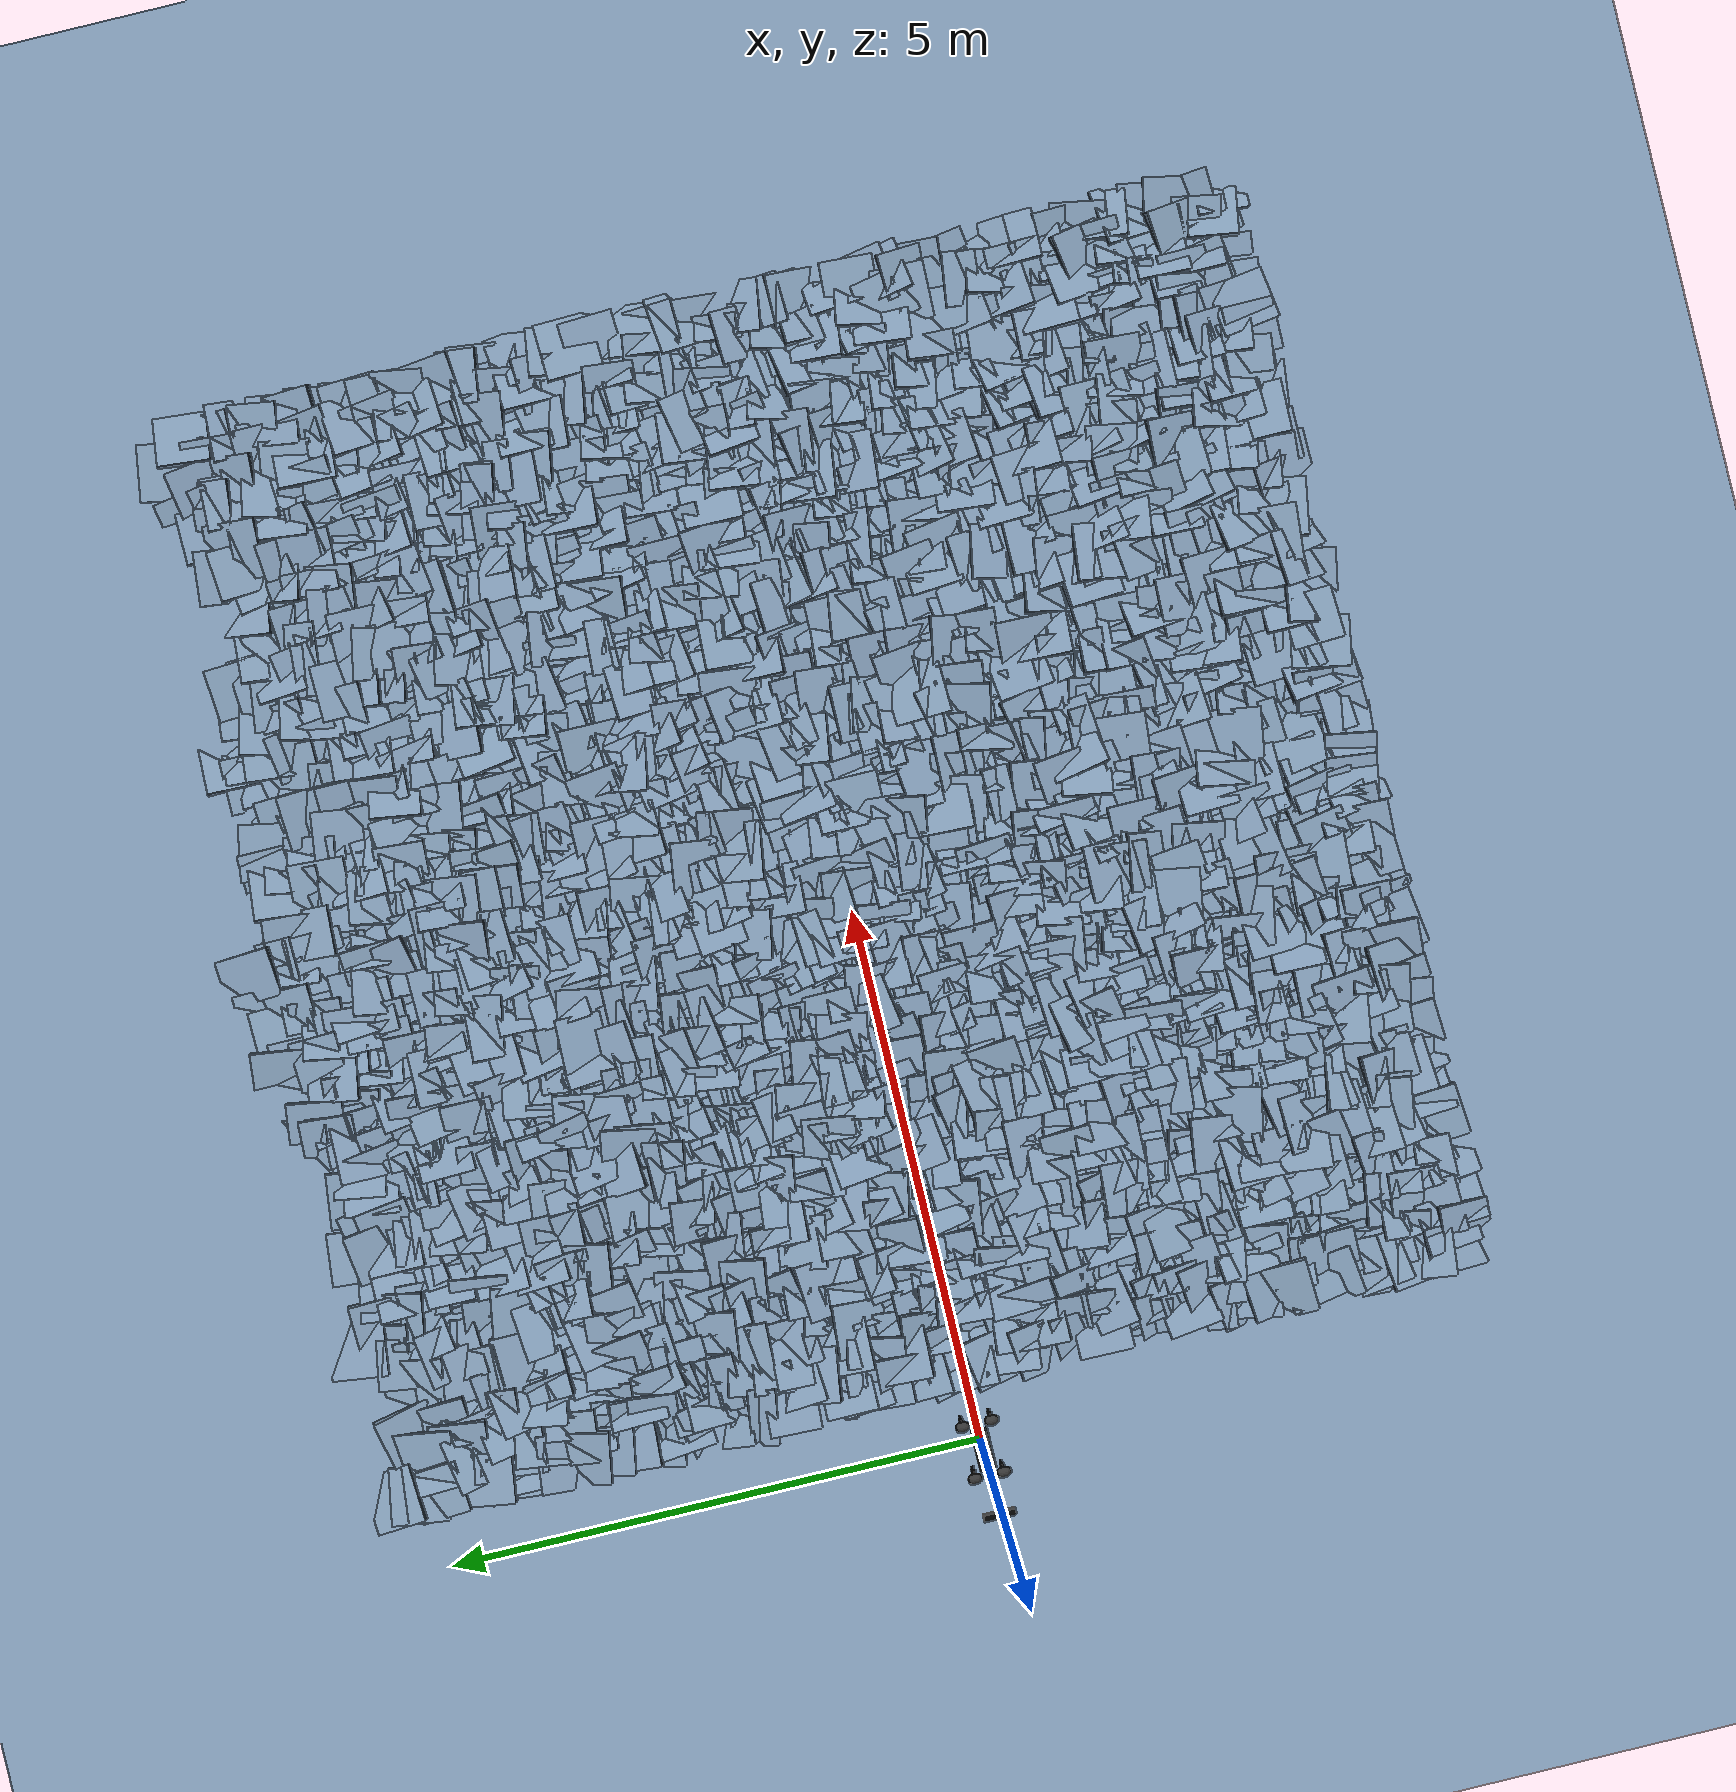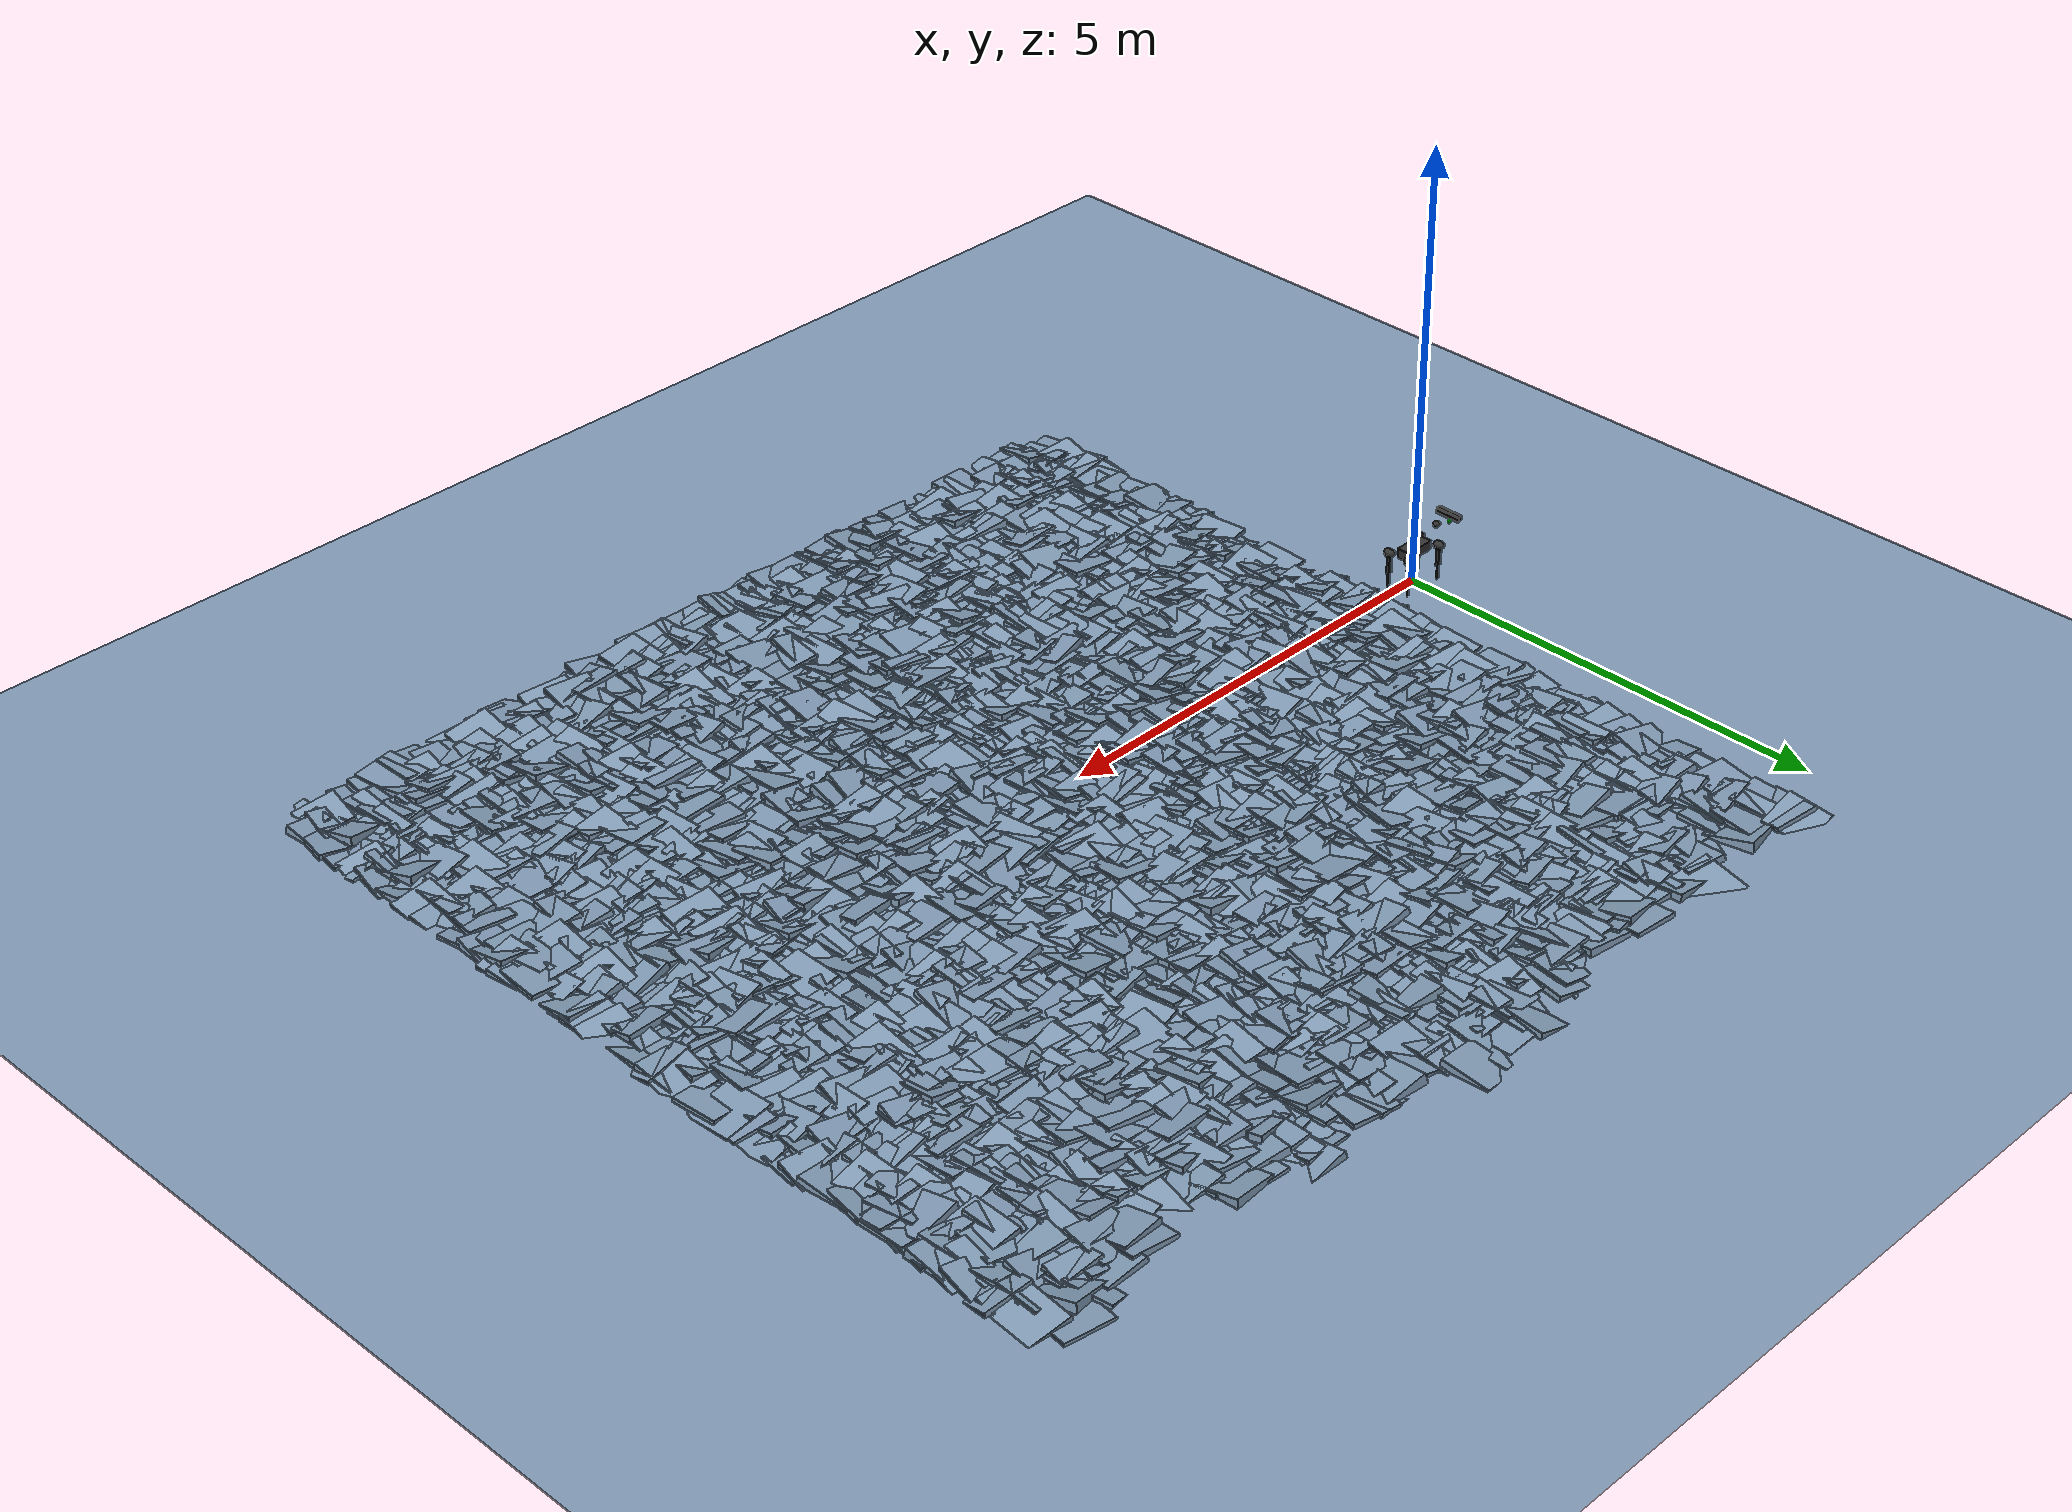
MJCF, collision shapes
<mujoco model="aliengo scene">
  <include file="aliengo_arm_leader.xml"/>

  <statistic center="0 0 0.1" extent="0.8" />

  <visual>
    <headlight diffuse="0.6 0.6 0.6" ambient="0.3 0.3 0.3" specular="0 0 0" />
    <rgba haze="0.15 0.25 0.35 1" />
    <global azimuth="-130" elevation="-20" />
  </visual>

  <asset>
    <texture type="skybox" builtin="gradient" rgb1="0.3 0.5 0.7" rgb2="0 0 0" width="512" height="3072" />
    <texture type="2d" name="groundplane" builtin="checker" mark="edge" rgb1="0.2 0.3 0.4" rgb2="0.1 0.2 0.3" markrgb="0.8 0.8 0.8" width="300" height="300" />
    <material name="groundplane" texture="groundplane" texuniform="true" texrepeat="5 5" reflectance="0.2" />
  </asset>

  <worldbody>
    <light pos="0 0 1.5" dir="0 0 -1" directional="true" />
    <geom name="floor" size="0 0 0.05" type="plane" material="groundplane" />
  <geom pos="0.7067622534350655 -4.7871004675510145 -0.25" type="box" size="0.23963224734048577 0.2565081741061708 0.24586039401329174" quat="0.9975695891534241 0.06761540782945477 0.015610834049503376 0.006274813192766089" /><geom pos="0.7067622534350655 -4.6052193791052 -0.25" type="box" size="0.23090548921014745 0.22541986029419558 0.2551428232484807" quat="0.9972532550389388 0.05753429150828926 -0.04654893754125933 -0.002991158414482515" /><geom pos="0.7067622534350655 -4.428876925130092 -0.25" type="box" size="0.27052374422232706 0.2674631348260342 0.25806657578743686" quat="0.9929091441489314 -0.0834761117183673 0.059997664383788736 -0.059694643866175436" /><geom pos="0.7067622534350655 -4.215557186506589 -0.25" type="box" size="0.2736942660827415 0.23264643266586574 0.2671322101434081" quat="0.9970398609163021 0.051534378119632775 0.019619915058209744 0.05357968410631143" /><geom pos="0.7067622534350655 -3.9964225484298095 -0.25" type="box" size="0.2675485064747317 0.2596086864984098 0.2466553808664563" quat="0.9901823269145215 -0.09505739115142045 0.06967445552908794 0.07515665040669836" /><geom pos="0.7067622534350655 -3.7893729038820463 -0.25" type="box" size="0.26641196806608136 0.25504104678170264 0.23944289935786087" quat="0.9974205693881342 -0.07122070766226217 -0.005334606101514982 -0.007166626771254596" /><geom pos="0.7067622534350655 -3.5461945353104545 -0.25" type="box" size="0.23463517757468447 0.23067515360789523 0.24718391405853932" quat="0.9943127716494737 -0.05877216341201402 -0.058757502855923724 0.06659955555969514" /><geom pos="0.7067622534350655 -3.312988723504767 -0.25" type="box" size="0.24143391025951347 0.2601130527082393 0.24615066313858072" quat="0.9955309801763512 -0.013099366286093865 0.0033361728513549697 0.09346306255800836" /><geom pos="0.7067622534350655 -3.089925241396667 -0.25" type="box" size="0.2531111733838731 0.2508369475806217 0.27314279847978723" quat="0.9938381983920949 -0.06623672582593498 -0.08432485574789851 0.028065107726691532" /><geom pos="0.7067622534350655 -2.92131819090236 -0.25" type="box" size="0.22648098956231302 0.25908524291672813 0.25568460182462843" quat="0.9945872365959083 0.08026305063486501 -0.03573027905288699 0.05547448658710205" /><geom pos="0.7067622534350655 -2.765375176127811 -0.25" type="box" size="0.23470253157211585 0.2585848757473558 0.24408797089823908" quat="0.9946084433841624 0.01545597296599131 0.023730849602341654 -0.0997597314839956" /><geom pos="0.7067622534350655 -2.606021721341286 -0.25" type="box" size="0.2264641155344396 0.2366114672820216 0.2596626943690515" quat="0.9930026013136692 0.06199249860462376 -0.058356895749272907 0.08183664594514119" /><geom pos="0.7067622534350655 -2.3564088236930094 -0.25" type="box" size="0.23730672386549723 0.25780462892424133 0.24368221321609676" quat="0.9962466237074453 -0.06009982426393617 -0.008549466890397813 -0.061705611502113435" /><geom pos="0.7067622534350655 -2.1624241079393 -0.25" type="box" size="0.23530554702212025 0.2550698152668639 0.2617804713589057" quat="0.9948476023299975 -0.01179152694931239 0.07743226384647985 0.06436965547575858" /><geom pos="0.7067622534350655 -1.915974959325716 -0.25" type="box" size="0.2634172510735695 0.24985747576392286 0.24759135766668564" quat="0.9966364984509404 0.024394437604672706 -0.07555624029561653 0.020294233707914455" /><geom pos="0.7067622534350655 -1.7351415188583208 -0.25" type="box" size="0.22804761796883757 0.25649678860777225 0.25176762935519187" quat="0.9934447289125743 -0.001968045139411053 -0.07531478327498287 -0.0859731400752202" /><geom pos="0.7067622534350655 -1.5388628324310258 -0.25" type="box" size="0.2515839297772572 0.24132422677942122 0.2334757983468535" quat="0.9985690132665777 0.013936774018728754 -0.04887867293235948 -0.01663031587600978" /><geom pos="0.7067622534350655 -1.3336932501578507 -0.25" type="box" size="0.24220690860769342 0.25519007534930055 0.2534032774767899" quat="0.9988435558498533 -0.012657430854387225 0.046236095519404 -0.0036829135895426256" /><geom pos="0.7067622534350655 -1.0864317123080944 -0.25" type="box" size="0.26743193170502455 0.2307228108199222 0.24061340850594182" quat="0.9936464728106404 0.05065500564908866 -0.09167813827413088 0.0411810203401174" /><geom pos="0.7067622534350655 -0.8491928367708175 -0.25" type="box" size="0.24299761876863243 0.26405034954283696 0.22688985584502844" quat="0.9934343276116412 0.03061747063236987 -0.0824413521155572 0.07317260878389462" /><geom pos="0.7067622534350655 -0.6827131078240436 -0.25" type="box" size="0.23539892568469506 0.24229228005875778 0.2620316242863373" quat="0.9932106127132668 0.09272089360097906 -0.04463079515125811 0.05425501642925967" /><geom pos="0.7067622534350655 -0.4655791476250819 -0.25" type="box" size="0.22625022995307073 0.25366780393193217 0.27224038287509894" quat="0.994831254824445 0.005522390219288024 0.08688776051020401 -0.05225700626908543" /><geom pos="0.7067622534350655 -0.2759864134315748 -0.25" type="box" size="0.23373062209104106 0.26594654490671604 0.27328355757204204" quat="0.9921927222893782 0.09406551403185723 -0.015521210387572922 0.08040132420563825" /><geom pos="0.7067622534350655 -0.09352995668658615 -0.25" type="box" size="0.2699615767112305 0.22691282797762694 0.27323975373538156" quat="0.9968809990881738 -0.04040631518692745 0.06766119376464495 -0.0041912060701251525" /><geom pos="0.7067622534350655 0.1559734774580015 -0.25" type="box" size="0.25540704780587237 0.2348887410009469 0.24254523864099425" quat="0.9920117100703824 0.07808468606852847 0.008534961355441871 0.09870513319719608" /><geom pos="0.7067622534350655 0.3399112717798438 -0.25" type="box" size="0.25014895156175665 0.23829431883053162 0.26161710402481353" quat="0.9956589268686777 -0.07933911184057213 0.039908632654127606 0.027855120153035238" /><geom pos="0.7067622534350655 0.5270496850768156 -0.25" type="box" size="0.26105101337616204 0.2697462987880312 0.2625930270859742" quat="0.9957643669719071 0.014876807022576152 -0.08828421250919802 -0.020926153575875774" /><geom pos="0.7067622534350655 0.7093915627057514 -0.25" type="box" size="0.24834093946176083 0.25929037378316827 0.2479158054952837" quat="0.9966497374945122 -0.07109818603650503 0.0372265137439294 -0.01576500456426195" /><geom pos="0.7067622534350655 0.9151300895782075 -0.25" type="box" size="0.25369953198288286 0.23591602573526005 0.2371991126099781" quat="0.9965670555618865 -0.028371762783698448 0.06432195869853757 0.04372450656601137" /><geom pos="0.7067622534350655 1.0734048304332457 -0.25" type="box" size="0.2507874891357783 0.2426867744879497 0.25021184020424325" quat="0.9966308365829374 -0.02238998440369528 0.07879553453561947 0.0041143538548116376" /><geom pos="0.7067622534350655 1.2395637271493287 -0.25" type="box" size="0.2360423974484471 0.23850548847577904 0.22997616762407097" quat="0.9973424978612361 -0.06451637181571604 -0.0175452391650595 -0.028943812988055782" /><geom pos="0.7067622534350655 1.4302487851986445 -0.25" type="box" size="0.2339703477008667 0.26435474151332083 0.2293948224460966" quat="0.9943535181165071 0.059276829536713746 -0.015344671614871137 -0.08667109981090856" /><geom pos="0.7067622534350655 1.6336657434626618 -0.25" type="box" size="0.27159935838822163 0.24167465140758543 0.2598297359249165" quat="0.9985445304376135 0.032624942572263005 0.035582677278805805 -0.024048013077069597" /><geom pos="0.7067622534350655 1.8241757894890789 -0.25" type="box" size="0.25705457810463034 0.23963909559924304 0.24176976788501953" quat="0.9915807135441307 0.08379170369508472 -0.07284278430001148 -0.0666375846997011" /><geom pos="0.7067622534350655 2.001532722585056 -0.25" type="box" size="0.26495929429551046 0.27302405187521755 0.25063160989233096" quat="0.9935765856417808 -0.06421301320356665 -0.04993977777397583 -0.0786655960101081" /><geom pos="0.7067622534350655 2.2248541975504565 -0.25" type="box" size="0.25829968075835547 0.2488837521809938 0.23412397682833" quat="0.9975328879846028 -0.04140878603029378 0.013867270416666164 -0.05496497648308714" /><geom pos="0.7067622534350655 2.4271173712554095 -0.25" type="box" size="0.2594198523253209 0.2250679009061468 0.24145838573933856" quat="0.9928662273793237 0.04684277061928941 -0.04998514887234365 0.09759044145031459" /><geom pos="0.7067622534350655 2.655705284401507 -0.25" type="box" size="0.2363282194731736 0.26577939919800175 0.23455229079439718" quat="0.9957761432986219 0.022892472737359806 0.07544305311209808 0.04705478579716396" /><geom pos="0.7067622534350655 2.8589307233141614 -0.25" type="box" size="0.26602593949107617 0.2382065224039629 0.24474963265447316" quat="0.9946785503763621 -0.028571583081428046 -0.019488870958765274 -0.09704859592056106" /><geom pos="0.7067622534350655 3.097647206931134 -0.25" type="box" size="0.2538786716696092 0.25448125355200724 0.2581275626137979" quat="0.9957725696448532 -0.08566168805011073 0.022994381331194913 -0.023881439874656463" /><geom pos="0.7067622534350655 3.339151971042268 -0.25" type="box" size="0.22850645244458212 0.25772933380711843 0.25430401168869254" quat="0.9938667240934992 -0.06039122585328501 -0.022414726330288515 -0.08988556404191046" /><geom pos="0.7067622534350655 3.5400965246719007 -0.25" type="box" size="0.24861602820201428 0.23640919503638658 0.263551282376906" quat="0.9912033936852688 -0.07320358974063798 -0.06069209625511057 -0.0920518128449986" /><geom pos="0.7067622534350655 3.777613952006986 -0.25" type="box" size="0.2706890256889065 0.2744131631054349 0.2529547878133911" quat="0.9954020822344832 0.07612361323384262 -0.025231578682625527 -0.052376116968153814" /><geom pos="0.7067622534350655 4.018210247387124 -0.25" type="box" size="0.27030967083222146 0.23520442428718083 0.23242672627740626" quat="0.9983941503320546 0.012759009520449694 0.02640260671640554 -0.04846886234863272" /><geom pos="0.7067622534350655 4.234775259322404 -0.25" type="box" size="0.24683624031370302 0.2644889584280286 0.22554967193222297" quat="0.9956004647543159 -0.005783762522057491 0.09339244143739982 -0.004910657231034494" /><geom pos="0.7067622534350655 4.4785896231170135 -0.25" type="box" size="0.2401359767551218 0.2412837822802159 0.27454047265528386" quat="0.9970797512260494 -0.0306613306606336 0.00593745887364716 -0.06968930390843824" /><geom pos="0.7067622534350655 4.696519311250164 -0.25" type="box" size="0.2255708970070851 0.253049866553077 0.23391300483917674" quat="0.9968968046656227 -0.047692802360999514 -0.043436138913077155 -0.045116064619487195" /><geom pos="0.7067622534350655 4.941684682099574 -0.25" type="box" size="0.240696938555356 0.24609863168350948 0.2702431237906737" quat="0.997217614229882 -0.05633596891422035 -0.021669217738061478 0.0437462395958668" /><geom pos="0.7067622534350655 5.178926487706708 -0.25" type="box" size="0.26079648498365315 0.2681787126611652 0.27323536284772" quat="0.9937019120088654 0.06814898000885301 0.03733222146383959 -0.08073742523918524" /><geom pos="0.7067622534350655 5.332743514177597 -0.25" type="box" size="0.26796722177437854 0.24152359401569493 0.27146289428515036" quat="0.9929494602039975 -0.09531074906934256 0.050722590081476025 0.04893311197805997" /><geom pos="0.9044791806684189 -4.7883055146787505 -0.25" type="box" size="0.22651394277690357 0.23106217803368412 0.26532807794029606" quat="0.9938961301962611 0.054221623134243224 -0.09578219054455638 -0.007501329220304481" /><geom pos="0.9044791806684189 -4.637996771533745 -0.25" type="box" size="0.2429033446668061 0.2587817842269033 0.2644473804299189" quat="0.9973965026136756 0.050291952318690776 0.0282826670022389 0.04325536791223909" /><geom pos="0.9044791806684189 -4.409928834177056 -0.25" type="box" size="0.24272609572173348 0.2572570366407637 0.23000815970691035" quat="0.999917012800856 0.004729809698743873 0.005880844397158129 -0.010440885058424786" /><geom pos="0.9044791806684189 -4.2526451172533175 -0.25" type="box" size="0.2590331303169081 0.27472486462341406 0.2307956491317491" quat="0.9895311502908624 -0.09394745285647639 -0.07373929450431763 -0.08102157213871207" /><geom pos="0.9044791806684189 -4.0679045656676145 -0.25" type="box" size="0.2694808883306253 0.2579671316700052 0.2607351569215011" quat="0.9990224937540421 -0.03572464948673845 0.023939976472442618 0.010231515968007098" /><geom pos="0.9044791806684189 -3.885340760955488 -0.25" type="box" size="0.24427400741668528 0.2675560509801003 0.24178016910226455" quat="0.9984314297587791 -0.004745915371307464 0.02622054674233695 -0.049240626373569824" /><geom pos="0.9044791806684189 -3.6994753300126706 -0.25" type="box" size="0.2694406008031122 0.24154173953457855 0.24356273469798098" quat="0.9949951412269034 0.04947884200619526 -0.08211415777004347 0.02817407003428527" /><geom pos="0.9044791806684189 -3.5194972158616444 -0.25" type="box" size="0.23512713704783741 0.26983079643357827 0.26807745057861143" quat="0.9974971893464244 0.0075299081009927125 -0.07016592886107177 0.004404560935815245" /><geom pos="0.9044791806684189 -3.3636772218591635 -0.25" type="box" size="0.2595860621928906 0.23915164566651842 0.2479662195635939" quat="0.9933487188462958 0.06231605698449696 -0.09073556003471987 -0.033794821400820824" /><geom pos="0.9044791806684189 -3.1405697829933934 -0.25" type="box" size="0.2703691393547252 0.2562509922964574 0.23373181535961815" quat="0.9943841782491069 -0.04640065495310989 0.0858959223330535 -0.04085310018009664" /><geom pos="0.9044791806684189 -2.933912252267503 -0.25" type="box" size="0.23308751854682663 0.2677272876858113 0.22503655916790222" quat="0.9935204170333898 -0.04518416444911527 -0.08839680159338349 -0.05533152527171547" /><geom pos="0.9044791806684189 -2.7188093780800324 -0.25" type="box" size="0.2278379957414289 0.26733396136319454 0.2710505358574953" quat="0.9985883231735035 0.03122848729916826 -0.028102487624437084 -0.03250219364680357" /><geom pos="0.9044791806684189 -2.4888429452024208 -0.25" type="box" size="0.2260704841644374 0.25672649010482296 0.27019034288149857" quat="0.9972442654196783 -0.06415497663741693 0.002397392167046303 -0.037178845746150734" /><geom pos="0.9044791806684189 -2.33059300268017 -0.25" type="box" size="0.22535430524413586 0.22979316817288659 0.26733989989561346" quat="0.9937954178280933 0.06612202372530726 -0.05744548878869162 0.06854605240408579" /><geom pos="0.9044791806684189 -2.151318880545656 -0.25" type="box" size="0.2552898026631975 0.27361461170099083 0.25533437768931005" quat="0.9944564017382198 0.06874689574723357 -0.06704533062489394 0.042839853038848734" /><geom pos="0.9044791806684189 -1.9021340936652318 -0.25" type="box" size="0.24614861899322993 0.230686591036001 0.241631923100721" quat="0.9900566665274934 0.08723698478758933 -0.07921779165350382 0.07682478138712708" /><geom pos="0.9044791806684189 -1.6770329000322892 -0.25" type="box" size="0.25884628569725904 0.2332426133091563 0.24420969201901083" quat="0.995485606628892 -0.03789164325815948 0.011760626802967505 0.08622249139931354" /><geom pos="0.9044791806684189 -1.4388678545875004 -0.25" type="box" size="0.24137376363095092 0.26337550858549763 0.263133800844315" quat="0.9910007840161772 -0.09517284238227285 0.03932766451571914 0.08551555973002742" /><geom pos="0.9044791806684189 -1.2207081741484664 -0.25" type="box" size="0.23051364062257304 0.2747827329980762 0.2669059088700898" quat="0.9944437454886276 0.02249951570120529 -0.09561385112068296 -0.03786027371312828" /><geom pos="0.9044791806684189 -1.0526833906460387 -0.25" type="box" size="0.23997558558073306 0.24560966017216987 0.23536717953868258" quat="0.9911109741486782 -0.08936231064949311 -0.09793449744895469 -0.011056607384820345" /><geom pos="0.9044791806684189 -0.8227619310592429 -0.25" type="box" size="0.24163805195972887 0.2524160127909745 0.25776524942389784" quat="0.994283067104096 -0.08997101937554018 0.057482886337516345 -0.0014546205367943063" /><geom pos="0.9044791806684189 -0.573376749760417 -0.25" type="box" size="0.2427959030696303 0.25156733836994827 0.25823480097122614" quat="0.9942462012830285 0.05868528475132921 0.07439791299622503 -0.04995477084052171" /><geom pos="0.9044791806684189 -0.38597778943379524 -0.25" type="box" size="0.2269177909304449 0.2393709998387396 0.24826259033186593" quat="0.9957342492392823 -0.020292623043580222 0.044608354900412574 0.07817678053599242" /><geom pos="0.9044791806684189 -0.13918413442431987 -0.25" type="box" size="0.2467120679047196 0.23806067530143538 0.2297650333669867" quat="0.9934525558919121 -0.03426669706722633 0.04102998237549559 0.10096708973817413" /><geom pos="0.9044791806684189 0.05929951919633325 -0.25" type="box" size="0.24813752899100625 0.250106298453901 0.24101311972050235" quat="0.9908062985819425 0.09408391109100905 -0.09549671557175672 0.018206418625772505" /><geom pos="0.9044791806684189 0.23546100811613258 -0.25" type="box" size="0.2734793205217325 0.25175825366533094 0.2571207455949473" quat="0.9983275250797063 -0.028686237424653042 0.0025730354743754014 0.05012616022689585" /><geom pos="0.9044791806684189 0.46487988699503546 -0.25" type="box" size="0.2745292051753343 0.24543444326370692 0.2743717724585217" quat="0.9927583319024587 -0.09182456253324406 0.07683240585415861 -0.009794159713205072" /><geom pos="0.9044791806684189 0.702951456056276 -0.25" type="box" size="0.255473417706723 0.2314034229262501 0.26738882665734653" quat="0.9930641043329138 -0.04685883054550267 -0.052342786557562145 -0.09427707770590352" /><geom pos="0.9044791806684189 0.8729229783863293 -0.25" type="box" size="0.2606217232014412 0.23596085450618945 0.24176702814986334" quat="0.9967685884548901 0.07546319279110762 0.008121533593170187 -0.026300728041499112" /><geom pos="0.9044791806684189 1.0768726923981413 -0.25" type="box" size="0.2615258158364886 0.22576811346336248 0.22510901587264764" quat="0.9971010411840218 -0.06669313489574903 0.025837453946496742 -0.02596084361263408" /><geom pos="0.9044791806684189 1.324464457417788 -0.25" type="box" size="0.25713613409975744 0.24717165655517404 0.271458879792263" quat="0.9929922877965951 -0.08817577737161521 0.04338827785908925 -0.06564149606626939" /><geom pos="0.9044791806684189 1.4955885905208604 -0.25" type="box" size="0.2705652958437756 0.24316086962695257 0.2567792860607184" quat="0.9931010255514026 -0.07723715275537205 0.0758159063339705 0.04513007455959263" /><geom pos="0.9044791806684189 1.724484032754626 -0.25" type="box" size="0.23465980094714378 0.24633024331584544 0.23294694105310274" quat="0.9946049598965869 -0.08189532290668361 -0.05472036920369038 0.03255473896885697" /><geom pos="0.9044791806684189 1.9533875767933493 -0.25" type="box" size="0.24361254955486383 0.26399135402415164 0.2476589111947457" quat="0.9996468166634808 0.008776384749597365 -0.02154852788560874 0.012840480959046078" /><geom pos="0.9044791806684189 2.1511666900940103 -0.25" type="box" size="0.2260132489636758 0.25342236896729947 0.23754972862541623" quat="0.9961143543523447 -0.01836452144554544 -0.08611393569251698 0.001824139477224239" /><geom pos="0.9044791806684189 2.3232933799645403 -0.25" type="box" size="0.24545294412541538 0.2689546386613699 0.2426090925939139" quat="0.995953914942887 0.07230727920277699 0.05306068259308631 0.0056586789080127434" /><geom pos="0.9044791806684189 2.4972023484720127 -0.25" type="box" size="0.24811442287558197 0.24542594713672614 0.23330135669752353" quat="0.9968365096273617 0.07246426088074549 0.02829606310788986 0.016286091659467285" /><geom pos="0.9044791806684189 2.682101319003708 -0.25" type="box" size="0.22764620423345291 0.2291279059771885 0.23915886500454403" quat="0.9934193350233276 0.0963793456887743 -0.05897961029427778 0.018720365807021418" /><geom pos="0.9044791806684189 2.8818875188869564 -0.25" type="box" size="0.25518522622862827 0.22819730698339258 0.27146223957293997" quat="0.9945736760563848 0.007848250999137161 -0.08910598840222297 -0.053119965011349" /><geom pos="0.9044791806684189 3.0487447281326148 -0.25" type="box" size="0.25160574066726515 0.2656722994649016 0.2524835981675787" quat="0.9916204872343629 0.08312541869341282 -0.08500382298755754 -0.05053042787894889" /><geom pos="0.9044791806684189 3.227169244262736 -0.25" type="box" size="0.27448437016537247 0.23888247605056123 0.23353193798969066" quat="0.9957842691993682 0.04867383327257736 -0.056492746177464824 -0.05341457478031598" /><geom pos="0.9044791806684189 3.4535048293543866 -0.25" type="box" size="0.23464474285277068 0.2442598167730429 0.23217093302732592" quat="0.9928835922709902 -0.05740262318250739 0.09439013611606888 -0.04447036378096492" /><geom pos="0.9044791806684189 3.6210419328242 -0.25" type="box" size="0.24695292145282363 0.23396479466131345 0.26876661130372764" quat="0.9967729049950267 -0.05202246505621193 -0.02846584161301206 -0.05410300230591052" /><geom pos="0.9044791806684189 3.807828608564426 -0.25" type="box" size="0.2620175507132316 0.23726817305266737 0.22530371837652832" quat="0.9937797007449836 0.05250206183820449 -0.07736830230085544 0.06049450957757689" /><geom pos="0.9044791806684189 3.960520297639448 -0.25" type="box" size="0.24005657077169829 0.27334360649029327 0.2626120709911052" quat="0.9886056372156675 0.09844475190829538 0.0790205170574429 -0.08199562653637324" /><geom pos="0.9044791806684189 4.15024378823488 -0.25" type="box" size="0.23788315622152845 0.2748870231201205 0.2583314299051825" quat="0.9975045566763778 -0.062166828061313795 0.006304272982502045 -0.03286641204664841" /><geom pos="0.9044791806684189 4.3738738324712845 -0.25" type="box" size="0.2678840684634534 0.2447033232763005 0.23543204866821693" quat="0.9923834443913555 0.08320974208999779 0.03649446427308293 -0.0831828840368389" /><geom pos="0.9044791806684189 4.5842959917621435 -0.25" type="box" size="0.25795086449283705 0.26317786340327654 0.2618343026960644" quat="0.9908171132968802 0.09061928016338719 0.038679374002038344 0.09259319676692003" /><geom pos="0.9044791806684189 4.754940567789365 -0.25" type="box" size="0.23014837275698835 0.23074766935574 0.2276749673397911" quat="0.9903052520510565 -0.04996421311659617 0.08289423946311922 0.09963749410520092" /><geom pos="0.9044791806684189 4.982838869717378 -0.25" type="box" size="0.2457634751467288 0.2601854395754482 0.2579992403492095" quat="0.996200088766244 -0.013143038024741037 0.08362648299994606 0.020475718172207374" /><geom pos="1.0866868671499994 -4.799902573028617 -0.25" type="box" size="0.22958248715345458 0.23746412446633777 0.24963128942686025" quat="0.99843407117684 -0.005656468465806601 0.045139813650940545 0.032554678639090985" /><geom pos="1.0866868671499994 -4.610898881356607 -0.25" type="box" size="0.265272412422917 0.2327558718157323 0.26311778928985663" quat="0.9979661177813592 -0.05240201592100454 -0.02673384017917588 0.02455520875682582" /><geom pos="1.0866868671499994 -4.459363146706913 -0.25" type="box" size="0.24307381441063192 0.27160723791119695 0.23941451632905755" quat="0.9935889421883342 0.0034907595011321796 0.09847092195795358 0.055428387022562774" /><geom pos="1.0866868671499994 -4.2723351027606675 -0.25" type="box" size="0.23178543977944097 0.2363584590636818 0.25708694229842627" quat="0.995408875805213 0.06737439517493216 0.057001939370366836 -0.03704915317562966" /><geom pos="1.0866868671499994 -4.067565682711911 -0.25" type="box" size="0.2508885662508108 0.23416256411022632 0.2425576770931008" quat="0.9944769800444077 -0.07064141623524425 -0.02308867774250976 0.0741096446769" /><geom pos="1.0866868671499994 -3.862267112319 -0.25" type="box" size="0.24679423893039854 0.2548829777687083 0.24620801800247563" quat="0.9957151052024703 -0.03376670093258144 -0.08450978987583904 0.016411416602608683" /><geom pos="1.0866868671499994 -3.636933774293447 -0.25" type="box" size="0.2283957874858482 0.24636261491745828 0.2337410296340158" quat="0.9970720796509559 -0.01972731621872313 -0.057328440585407 -0.046599902096141996" /><geom pos="1.0866868671499994 -3.4131701015379106 -0.25" type="box" size="0.2387058378549098 0.24170780423869567 0.23965443724211308" quat="0.9909866284482326 0.07537170092813658 -0.07719733199380026 -0.07940516903226776" /><geom pos="1.0866868671499994 -3.1718615526850087 -0.25" type="box" size="0.2458944061581362 0.26726977727742907 0.23352330411731695" quat="0.9929212038809551 -0.044708284478575715 -0.07282920164129789 0.08248975433875713" /><geom pos="1.0866868671499994 -2.973957894610926 -0.25" type="box" size="0.25146847231837577 0.24058507760234876 0.2592911750023909" quat="0.9933712629394126 -0.07041859364658362 -0.06114460731127668 -0.06720187967418435" /><geom pos="1.0866868671499994 -2.743052084200037 -0.25" type="box" size="0.25029808364181844 0.27126267868363896 0.27313182967526467" quat="0.9925151100887575 0.057385542936276616 0.10075698085985083 0.03832344602743856" /><geom pos="1.0866868671499994 -2.549555688818322 -0.25" type="box" size="0.24077476493398123 0.26743798755340675 0.2708803214998273" quat="0.9895023715474119 -0.09004138342066774 0.06691243463106127 -0.09110615821932028" /><geom pos="1.0866868671499994 -2.337414292092879 -0.25" type="box" size="0.24312746737532334 0.2553755188388284 0.2644857946654763" quat="0.9946234177406995 -0.0835764552341279 -0.01878060498908369 0.058193830330644306" /><geom pos="1.0866868671499994 -2.110298240333043 -0.25" type="box" size="0.23642944435581104 0.27052848758619263 0.24106673357701883" quat="0.9989817218278739 -0.0065368911202605216 0.04100628896926522 -0.01764292416997389" /><geom pos="1.0866868671499994 -1.9592008259377254 -0.25" type="box" size="0.24172483255178 0.2677813839533075 0.22972883683173076" quat="0.9940441444780769 -0.06975934472626852 0.08327513605068214 -0.008667431450560016" /><geom pos="1.0866868671499994 -1.7679922213527641 -0.25" type="box" size="0.23278021348354658 0.26868608620297063 0.2496421225509713" quat="0.9943168134812862 -0.09246559901752038 0.049585123529238315 0.018041700345100827" /><geom pos="1.0866868671499994 -1.5646533997866237 -0.25" type="box" size="0.24315743666359702 0.26686896678547445 0.23259759999299925" quat="0.9985667841238353 0.015337930957787408 0.025991187670574168 -0.044199362913836526" /><geom pos="1.0866868671499994 -1.3678328990391644 -0.25" type="box" size="0.2693068553385209 0.26137342190194945 0.23221294438174453" quat="0.9952912479428987 -0.0015985946292194969 0.08066434616472366 -0.05372187190797077" /><geom pos="1.0866868671499994 -1.2037813687768315 -0.25" type="box" size="0.26919984723959484 0.24389056091836983 0.2576505038415396" quat="0.9911497640792643 0.09027275516472538 -0.06734437955542784 0.07026883649871299" /><geom pos="1.0866868671499994 -0.982625031100623 -0.25" type="box" size="0.26565987738263525 0.2626770390053115 0.23140400533572555" quat="0.9925956035358531 -0.026023174251211187 -0.07498999651674286 -0.09194162640287526" /><geom pos="1.0866868671499994 -0.7411763639712428 -0.25" type="box" size="0.2313858650033689 0.24829510768807428 0.26472921929848214" quat="0.9964733704580592 -0.007144165083036213 -0.06730626718854572 0.04959485124855375" /><geom pos="1.0866868671499994 -0.5150634661026601 -0.25" type="box" size="0.2710288962295729 0.264427645132035 0.24693713491214397" quat="0.9950736050662835 0.07813629784143207 -0.045800913455255575 0.040317685780428505" /><geom pos="1.0866868671499994 -0.32392721333638974 -0.25" type="box" size="0.2503028442339119 0.27102943129837914 0.24375604040875493" quat="0.9947765801853756 0.02410805801016433 -0.06783125299570328 0.0723690415212231" /><geom pos="1.0866868671499994 -0.08696826802886903 -0.25" type="box" size="0.2565734011019472 0.2678519130792471 0.2436446580656044" quat="0.9911008638547397 0.0899164150838588 -0.06948762327775093 -0.06932233533332077" /><geom pos="1.0866868671499994 0.12498862808547084 -0.25" type="box" size="0.27350417554944073 0.23707522326784147 0.25163623105268496" quat="0.9957285014744562 0.04109147510313894 0.07433577463913273 -0.036199925885033214" /><geom pos="1.0866868671499994 0.29368606115710083 -0.25" type="box" size="0.22751388069090034 0.23225358143030975 0.2578614100647553" quat="0.9901853069938837 0.08701357753295134 -0.09710575768643157 -0.05032064151507942" /><geom pos="1.0866868671499994 0.5357676238875424 -0.25" type="box" size="0.2692079050021534 0.26053265466848036 0.2383016521403224" quat="0.9977235247294172 -0.008345798015124108 -0.04917539423487882 -0.045386082215178834" /><geom pos="1.0866868671499994 0.7849328631681631 -0.25" type="box" size="0.26378881030522416 0.25813558853834484 0.25641584710939097" quat="0.9868138340526289 0.09454215433336832 0.08845789810102929 -0.09713618398879127" /><geom pos="1.0866868671499994 0.9672938208449668 -0.25" type="box" size="0.2575880666843523 0.24105556784844123 0.2698305877051682" quat="0.9928123292588766 -0.0954767591323015 0.07189597272014454 -0.006231889262551553" /><geom pos="1.0866868671499994 1.1277908957917813 -0.25" type="box" size="0.26669639511761123 0.2536444650585763 0.24905277201899664" quat="0.9984499000119815 0.04579332487814398 -0.017752063984367364 0.02618459063960931" /><geom pos="1.0866868671499994 1.278297410665716 -0.25" type="box" size="0.23801344270628658 0.2385181409042619 0.25276316525543713" quat="0.9994887921446526 -0.010182813261420422 0.020702137402349982 -0.02213337295309529" /><geom pos="1.0866868671499994 1.4867556841004452 -0.25" type="box" size="0.2616486027088122 0.22811536880702366 0.270264685769755" quat="0.996720320057744 0.04149465522643658 0.06648769183149313 -0.02015400720819205" /><geom pos="1.0866868671499994 1.6722486784478843 -0.25" type="box" size="0.27102727322993364 0.2536315311548812 0.25404202185047425" quat="0.9934266913399349 0.07244895359632013 0.05672881034719087 -0.06809111640133844" /><geom pos="1.0866868671499994 1.8976483024682897 -0.25" type="box" size="0.23106503360942762 0.26780974323881956 0.2694992544605763" quat="0.990918001077448 0.07966828967806469 0.041182544380648854 -0.10019219929107682" /><geom pos="1.0866868671499994 2.1022352114621556 -0.25" type="box" size="0.25998290578260785 0.2349160989341364 0.25832725330143796" quat="0.995185906081847 0.029453539798196565 -0.04581376715020225 -0.08147760470777332" /><geom pos="1.0866868671499994 2.2574780226114575 -0.25" type="box" size="0.26195169876130353 0.26124515076658594 0.26482221108734244" quat="0.996107817894965 -0.06745587206800303 -0.056687266793637274 0.0023397084312809357" /><geom pos="1.0866868671499994 2.457766727531517 -0.25" type="box" size="0.2690087631782607 0.2715725169637225 0.23237483070890405" quat="0.996011114836087 -0.07454587185500042 -0.04803037283177548 -0.009892188736254273" /><geom pos="1.0866868671499994 2.6184316822009084 -0.25" type="box" size="0.23453754909411317 0.26305266859924603 0.2318113761850572" quat="0.9926582800033991 -0.08597490375871275 -0.054939641763158104 0.06495760792477946" /><geom pos="1.0866868671499994 2.849165482446675 -0.25" type="box" size="0.2647521626361588 0.26841738062786186 0.25943710082664206" quat="0.9962821848234878 -0.04151949290248369 -0.054858076908586996 0.05185104926951635" /><geom pos="1.0866868671499994 3.00888565832474 -0.25" type="box" size="0.2713969986157904 0.26708619293034136 0.2692767379767117" quat="0.9955029500135063 0.009374778735464767 0.09335629859877059 0.013061070017600658" /><geom pos="1.0866868671499994 3.2586203086139527 -0.25" type="box" size="0.2623583185590186 0.2631767127039917 0.2250127256147541" quat="0.991454212752123 -0.0701599675598493 -0.09561584169775142 -0.05434826385911065" /><geom pos="1.0866868671499994 3.4158831959355336 -0.25" type="box" size="0.27267461266081866 0.27471072273288716 0.2311457966665465" quat="0.9966522027758392 -0.029779526238548997 -0.06376449198798331 -0.04161317196020232" /><geom pos="1.0866868671499994 3.63339844357918 -0.25" type="box" size="0.24502867668162975 0.26584498763276365 0.2371964188806252" quat="0.9908123224670676 0.08124407239547585 0.06417720320382965 -0.08701510752132913" /><geom pos="1.0866868671499994 3.846108889268308 -0.25" type="box" size="0.2637347051564156 0.25862090943772426 0.23316429295237784" quat="0.9952079529234258 0.005679060314109552 0.026301989382338645 -0.09400576613402181" /><geom pos="1.0866868671499994 4.051789004405206 -0.25" type="box" size="0.26342478107045497 0.2542551270750149 0.2446125764941405" quat="0.9980248478451158 0.02240145654008237 0.01668305754693154 -0.05626947146990154" /><geom pos="1.0866868671499994 4.27125969614824 -0.25" type="box" size="0.26763428595507127 0.2329788948477979 0.25564513167941466" quat="0.9883590722812332 0.08456562431677155 0.09506421916915807 0.08341339015441801" /><geom pos="1.0866868671499994 4.467820010344578 -0.25" type="box" size="0.2541632938629549 0.23586349641069232 0.2514718313598038" quat="0.9958324922430765 0.03160884487582162 -0.03178890808207977 0.07942287857732429" /><geom pos="1.0866868671499994 4.651250754518237 -0.25" type="box" size="0.23797074405688345 0.2715973542735738 0.2576094384317725" quat="0.9937295581962361 -0.05249335885375366 -0.08488617265825178 -0.05040188622262162" /><geom pos="1.0866868671499994 4.804798882540595 -0.25" type="box" size="0.2357315204239708 0.2719920199397764 0.23806721480007909" quat="0.9952930556655107 -0.04426876415518434 0.002679763037839342 0.08616744590762855" /><geom pos="1.0866868671499994 5.025376402477949 -0.25" type="box" size="0.22770245486073723 0.2696127960460983 0.2706263353281196" quat="0.9947284343284561 0.0032295543003259004 -0.06616749723760618 -0.0782737135109299" /><geom pos="1.2720505177357677 -4.754573907410128 -0.25" type="box" size="0.2685633982879357 0.22870604466488825 0.2337102244494352" quat="0.994762466709022 0.015781124048116178 -0.026630493669972704 -0.09741359123681609" /><geom pos="1.2720505177357677 -4.574962362582681 -0.25" type="box" size="0.24860139187745758 0.2691930407095491 0.22919159571100686" quat="0.9977702966867582 -0.049312679112080544 -0.04483431478266465 0.0035466810367617238" /><geom pos="1.2720505177357677 -4.399278824060326 -0.25" type="box" size="0.2418626944621823 0.23796180343192083 0.272719518085553" quat="0.9964020099947629 0.04808811899434607 -0.05722964430990035 -0.03994164621224627" /><geom pos="1.2720505177357677 -4.193611485201359 -0.25" type="box" size="0.24507574713243457 0.27362843644774887 0.2591678372091996" quat="0.994352897915783 0.07778659165650348 -0.014564636196607639 -0.07070666119545968" /><geom pos="1.2720505177357677 -3.9509187858422363 -0.25" type="box" size="0.2437601093068537 0.2412516487337502 0.25855792786483534" quat="0.998646911877889 -0.03884558950804241 -0.014322579699265606 0.031467908784767656" /><geom pos="1.2720505177357677 -3.7557308875420063 -0.25" type="box" size="0.2525336022851614 0.25067122256363583 0.2281237764044827" quat="0.9896865014776178 0.046388479164790004 0.08982522388837925 -0.10148973813727973" /><geom pos="1.2720505177357677 -3.5069159360276263 -0.25" type="box" size="0.2465727865171286 0.23502229402011723 0.25227788199524903" quat="0.9978461420618601 0.0037819671179479034 0.03920206186107203 0.052459239823137986" /><geom pos="1.2720505177357677 -3.346012677771725 -0.25" type="box" size="0.2657282500168164 0.23132244802618665 0.2503669523184308" quat="0.9989464929945332 0.04276863636396297 0.01266971723965645 -0.010780822907230687" /><geom pos="1.2720505177357677 -3.100961590324819 -0.25" type="box" size="0.23309999142579735 0.25126997226917835 0.2573752281919832" quat="0.9964873468122759 -0.07452817432560663 0.023235559922934954 0.03030887048028392" /><geom pos="1.2720505177357677 -2.9254294549981505 -0.25" type="box" size="0.24433732272195913 0.2297073205530285 0.2511195347702001" quat="0.9933654012975184 -0.09327617978912675 0.0529072961172309 0.041539761753414554" /><geom pos="1.2720505177357677 -2.7552744146656067 -0.25" type="box" size="0.2544384476602763 0.2671733712783584 0.26246973533656504" quat="0.9985211885902336 0.026323351905238088 -0.04732509708803138 0.004780404421008274" /><geom pos="1.2720505177357677 -2.536800782157997 -0.25" type="box" size="0.265418568960319 0.2484278189785689 0.2398903815657444" quat="0.9903392104913258 -0.07890793631391263 -0.0890431054395607 0.07122577569796074" /><geom pos="1.2720505177357677 -2.370265309873715 -0.25" type="box" size="0.22642572432448302 0.2627690308001314 0.23953798900203666" quat="0.9971069728901124 -0.011074166385967072 -0.0018245061117789741 0.07517791318080547" /><geom pos="1.2720505177357677 -2.20867137071535 -0.25" type="box" size="0.2362476808157867 0.25885268434880365 0.25442143422770097" quat="0.9978468564652592 -0.053068777067346064 -0.03793491796555005 0.006804259101754095" /><geom pos="1.2720505177357677 -2.0170668595135934 -0.25" type="box" size="0.254628840527463 0.2554715946250952 0.259784467737103" quat="0.9955457849274962 0.06845228193028631 -0.06457944590495199 -0.00568949718704802" /><geom pos="1.2720505177357677 -1.821088551083681 -0.25" type="box" size="0.267429536483873 0.27383965088418194 0.24145891712727022" quat="0.9954311662962282 -0.002109828961231641 0.020398590656581273 0.09325362881470342" /><geom pos="1.2720505177357677 -1.5976014496275512 -0.25" type="box" size="0.2700915275828223 0.2565284522823366 0.23051972641334545" quat="0.995354296974208 0.044294068011876075 -0.037971309533583006 0.07659006910980258" /><geom pos="1.2720505177357677 -1.3987831713661456 -0.25" type="box" size="0.22878769776889468 0.2434960206935525 0.23895259679419983" quat="0.9961904643980148 -0.0856811139256142 -0.013332036836494298 -0.009249981228300487" /><geom pos="1.2720505177357677 -1.2143306848794952 -0.25" type="box" size="0.2509238935141174 0.22593007971515924 0.2511911799280684" quat="0.9917059782650425 0.09240665816411725 0.02150599892237875 0.086704983770633" /><geom pos="1.2720505177357677 -1.013511884612352 -0.25" type="box" size="0.2509237806652323 0.2720182371464014 0.2668350170910319" quat="0.9988530627495834 0.0038651379095101523 -0.03822314507369536 0.028576405046691716" /><geom pos="1.2720505177357677 -0.766654793720086 -0.25" type="box" size="0.2338737311073981 0.2458854846967592 0.25173268240495095" quat="0.9987503238411347 -0.004727596063588636 0.04641088314560261 0.017929595319839755" /><geom pos="1.2720505177357677 -0.5933443799099809 -0.25" type="box" size="0.2702343882946709 0.25339873517465633 0.2669860871206228" quat="0.9965017091092061 0.051197281167973376 0.0632476670239017 0.01905032176820723" /><geom pos="1.2720505177357677 -0.43020759257859975 -0.25" type="box" size="0.24147407379130478 0.25209809340956874 0.23635854376643725" quat="0.9968727285053269 -0.055095220600598495 0.047517196046767296 0.03084470633948303" /><geom pos="1.2720505177357677 -0.19450629365943684 -0.25" type="box" size="0.24113996226359288 0.2346637192948923 0.2667822117431694" quat="0.9946470905132746 -0.06528909406792019 0.0780511560230607 -0.017958746413154557" /><geom pos="1.2720505177357677 0.05258996144004868 -0.25" type="box" size="0.26603086054865926 0.23649755239441908 0.24611022996227586" quat="0.9942644956322385 0.06819344623764649 -0.0715868474695387 -0.040780999065455154" /><geom pos="1.2720505177357677 0.28779957087664076 -0.25" type="box" size="0.24231517412816717 0.23685941767170152 0.247387853591223" quat="0.9958901305357338 0.08591835255698674 -0.028132968124532635 0.0054240851685922594" /><geom pos="1.2720505177357677 0.49499560523178143 -0.25" type="box" size="0.26434041149972165 0.2589771654126579 0.23088732663395717" quat="0.9938950870225599 -0.006218258233767797 -0.06509247282694959 -0.08886427425140614" /><geom pos="1.2720505177357677 0.6680303732644735 -0.25" type="box" size="0.25384089340298244 0.230850151434491 0.2390282296533785" quat="0.9977614388067939 -0.04024054523315328 0.020490154980860965 0.04932507778397529" /><geom pos="1.2720505177357677 0.859037595948454 -0.25" type="box" size="0.2567664944512508 0.24977669589594176 0.27451723985048" quat="0.995450209062852 0.07834974152673846 -0.04009610143709833 -0.03650345091856065" /><geom pos="1.2720505177357677 1.0620303220910623 -0.25" type="box" size="0.2617800477111985 0.27403305011360235 0.238495967877231" quat="0.9982989059626401 -0.044826433097409565 -0.03665358800246501 -0.006811735175745393" /><geom pos="1.2720505177357677 1.2720958035757395 -0.25" type="box" size="0.26086258936902423 0.2513241134646776 0.23259209146772772" quat="0.9923804410639893 -0.06775531215173901 0.06535276791557516 -0.07949398464434639" /><geom pos="1.2720505177357677 1.4662034409841187 -0.25" type="box" size="0.25511764510127344 0.23880158922140904 0.2561571377135329" quat="0.9985627056027951 -0.023368809953719837 0.024886039302072144 0.04131714835789423" /><geom pos="1.2720505177357677 1.65995342485719 -0.25" type="box" size="0.2508870251004425 0.22778464219233371 0.24690788066788621" quat="0.9968491171039879 0.043410165973262305 -0.06637358076884206 0.0013939135897336162" /><geom pos="1.2720505177357677 1.880789416131364 -0.25" type="box" size="0.26907815058795836 0.23266657951403447 0.27468621134250154" quat="0.9980599074932157 -0.05338102820521975 -0.02593244418688754 -0.018825387668818142" /><geom pos="1.2720505177357677 2.0736845404504525 -0.25" type="box" size="0.26820696996549453 0.24816337448132425 0.27163692924957683" quat="0.9972044064234437 -0.0344524147950034 -0.010724427136368567 0.06543232830227791" /><geom pos="1.2720505177357677 2.283077044616441 -0.25" type="box" size="0.22581252203146673 0.2571156017318606 0.24769652311490564" quat="0.997498679708086 -0.03246479497555847 0.05215028158731503 -0.03496811688072226" /><geom pos="1.2720505177357677 2.5213109135507183 -0.25" type="box" size="0.26973017714698977 0.2539816569596273 0.2722709508253284" quat="0.9995789230480951 0.0001296615196134052 -0.0224697202221613 0.018359505958446327" /><geom pos="1.2720505177357677 2.7262592098194283 -0.25" type="box" size="0.24335245830394872 0.2260908876135703 0.2587845722081268" quat="0.9878089297401708 -0.08665206005216812 0.08165640922897316 0.10028544084823096" /><geom pos="1.2720505177357677 2.9414971582564817 -0.25" type="box" size="0.22728003327525742 0.25156640243823764 0.2325396254540066" quat="0.9971017834032277 -0.04522432538848783 0.060879282260794164 -0.006042095552829951" /><geom pos="1.2720505177357677 3.1559956795671784 -0.25" type="box" size="0.26325944902595094 0.23989321582817247 0.24585662158716273" quat="0.9976113435978377 -0.01597668574499865 -0.06703969041463774 -0.004693883960224384" /><geom pos="1.2720505177357677 3.323385462327888 -0.25" type="box" size="0.26303252925155685 0.27366164038178864 0.2490354201622274" quat="0.9949061738114445 0.007307896292146825 0.07105848851600327 -0.0711265855603679" /><geom pos="1.2720505177357677 3.546863781415171 -0.25" type="box" size="0.2660651554060553 0.26920542769427797 0.25987936947888374" quat="0.9964284433958696 0.026630061338893406 -0.00977532176757169 -0.07953389283262441" /><geom pos="1.2720505177357677 3.7254803563085517 -0.25" type="box" size="0.26669774204927743 0.24713054869537882 0.2445567646753946" quat="0.9909661290124026 -0.05622016308345384 -0.08884683875050498 0.08325661329339522" /><geom pos="1.2720505177357677 3.8823563073268055 -0.25" type="box" size="0.254657484213454 0.27297653841204095 0.2532401660507161" quat="0.9916535829075737 -0.008936064207526616 0.09909415160604955 -0.08199797180740646" /><geom pos="1.2720505177357677 4.04123316177575 -0.25" type="box" size="0.22866330657187928 0.2695187110188716 0.26710800465494094" quat="0.9935791223670322 0.061579631760633025 0.04944486973401301 0.08101655019543567" /><geom pos="1.2720505177357677 4.290070659035434 -0.25" type="box" size="0.24690275692029168 0.25783654946859014 0.24443680676120733" quat="0.9947518447002103 -0.07600313499069623 -0.05565968982148645 -0.03992855952937589" /><geom pos="1.2720505177357677 4.52637636600844 -0.25" type="box" size="0.23153760550609231 0.27100836544148454 0.25655748329438943" quat="0.9987284581944287 0.00794368574553549 0.03507504926985527 -0.03532853758751933" /><geom pos="1.2720505177357677 4.775567426845916 -0.25" type="box" size="0.262976869223464 0.2618705593297678 0.2423357753494318" quat="0.9953341377670863 -0.03493651789305796 -0.08614655600846763 0.025848883937970465" /><geom pos="1.2720505177357677 4.976320978052135 -0.25" type="box" size="0.25693873382673577 0.2720961074684824 0.23130759582050753" quat="0.9974027663674516 -0.05935456740737757 0.021041270176612975 0.03495743010852414" /><geom pos="1.2720505177357677 5.13018243712003 -0.25" type="box" size="0.2720141858299886 0.26320483630563757 0.26712614186073463" quat="0.9881766618570395 0.09051446791886764 -0.06702698104211555 0.10402595767798889" /><geom pos="1.4906582970830329 -4.801174099611019 -0.25" type="box" size="0.22896222943890554 0.23732642326381434 0.2510475198713258" quat="0.9957723596915027 0.03361939726867459 0.07484131644075391 0.04130279839336167" /><geom pos="1.4906582970830329 -4.615806506012207 -0.25" type="box" size="0.2382486150870377 0.24264260203423108 0.2689151764982143" quat="0.9997609932405545 -0.021436978435822925 -0.0014703336754355802 -0.0040311870565653985" /><geom pos="1.4906582970830329 -4.4598870341465044 -0.25" type="box" size="0.23955360010147797 0.2355402024252619 0.25560818505035915" quat="0.998283385404861 -0.030615848818380493 0.04573916127064022 0.020022021676093536" /><geom pos="1.4906582970830329 -4.29168889505479 -0.25" type="box" size="0.23897276418027896 0.2566167288893674 0.2620681664316815" quat="0.993759693955233 -0.0387943320617547 0.07543420454605879 -0.0724317006178044" /><geom pos="1.4906582970830329 -4.08937525354179 -0.25" type="box" size="0.23184334387256497 0.23973407862808901 0.2671459699432059" quat="0.9959822827460904 -0.0892197031000534 0.007640079019721232 0.0008753440452957888" /><geom pos="1.4906582970830329 -3.8963529704809696 -0.25" type="box" size="0.27497095133450405 0.2432461789320489 0.23817562603060297" quat="0.9952561132561684 0.02291804117090681 -0.09449166980742338 -0.003369978059015338" /><geom pos="1.4906582970830329 -3.7426094526106386 -0.25" type="box" size="0.26629058511583176 0.26388714216974624 0.2454737887451943" quat="0.9958163129422747 0.02649252373659527 0.0410322369484583 -0.0772293506066531" /><geom pos="1.4906582970830329 -3.59072944559111 -0.25" type="box" size="0.251503985703789 0.26890457525422634 0.2549651889501518" quat="0.9939683621075608 -0.09199879123634976 0.05728174059719758 -0.01679046558076477" /><geom pos="1.4906582970830329 -3.367980152375223 -0.25" type="box" size="0.23553955261945075 0.22624889451307054 0.23791237810282875" quat="0.9956686983891894 -0.02166505617189298 0.06441483529021483 0.06344444328371726" /><geom pos="1.4906582970830329 -3.2131296640431573 -0.25" type="box" size="0.24060791074850676 0.24101320007231633 0.2467471391044763" quat="0.9925852440488555 0.07130681031809748 0.0623813912516166 -0.07614744988668572" /><geom pos="1.4906582970830329 -3.0394017766692265 -0.25" type="box" size="0.22636233699523545 0.24815216633358447 0.272637576769942" quat="0.9950266898894499 0.006119634347363977 0.0991078424883327 -0.007878581116369665" /><geom pos="1.4906582970830329 -2.8525363687882956 -0.25" type="box" size="0.26026560806749865 0.24920183111983132 0.2502599269604875" quat="0.9969906492814765 0.06393174934718386 -0.01890488600472717 -0.03955985282906214" /><geom pos="1.4906582970830329 -2.702239724829715 -0.25" type="box" size="0.23620067773784983 0.2724019975680779 0.2699237175757119" quat="0.998930284538146 0.03451419238839026 -0.005815040525927614 0.03021990172051253" /><geom pos="1.4906582970830329 -2.5420369784644756 -0.25" type="box" size="0.26712367830286415 0.26276664469363764 0.25684099502046115" quat="0.994041138309413 -0.08518622896586509 -0.008674724699843468 0.0674556957897838" /><geom pos="1.4906582970830329 -2.383473490592067 -0.25" type="box" size="0.27083155743304127 0.2637177170507483 0.2557841610583058" quat="0.9980916755119125 -0.013916960255082614 -0.0018030831226973677 0.06013380399022287" /><geom pos="1.4906582970830329 -2.165646654406621 -0.25" type="box" size="0.27440276323405105 0.2614287641568894 0.27465129097966684" quat="0.9968164796006569 0.05667072588437846 0.02196899178877231 0.05160133936319501" /><geom pos="1.4906582970830329 -2.001827665292097 -0.25" type="box" size="0.259042829209331 0.24548184317608107 0.2671293829044386" quat="0.9931645192000337 0.07642457077253638 -0.06611332494012676 0.058417044171718085" /><geom pos="1.4906582970830329 -1.761165183445895 -0.25" type="box" size="0.2301922153460046 0.23236862169708694 0.27227749786505856" quat="0.9953626706384672 0.04100188204957157 -0.059793449667294725 -0.06321979867680773" /><geom pos="1.4906582970830329 -1.5720138991781964 -0.25" type="box" size="0.22950014363533847 0.2488325514397779 0.2596465083399298" quat="0.9933653321546062 -0.060308105464200346 0.08710891624411846 0.04472455700689404" /><geom pos="1.4906582970830329 -1.3487753219723628 -0.25" type="box" size="0.24787624554832122 0.26177649892277194 0.23003428343686996" quat="0.9940379058226676 -0.014148933249825236 0.0768800911135562 0.0760125059838763" /><geom pos="1.4906582970830329 -1.16998904618033 -0.25" type="box" size="0.24154181858318288 0.2433380361903797 0.25171817589707546" quat="0.999635519490703 0.019012683381983597 0.010117514542711497 -0.01627826595945509" /><geom pos="1.4906582970830329 -0.9553648870881641 -0.25" type="box" size="0.2393474052955929 0.22546313995953943 0.273137678183511" quat="0.9937890844034895 -0.09553432353604314 -0.03346296886304537 0.046224219429382936" /><geom pos="1.4906582970830329 -0.730951135380117 -0.25" type="box" size="0.268487608373296 0.24473685069850606 0.2589223999696149" quat="0.9953286476430313 0.011380056173571759 -0.021185970546395698 -0.09350150883589" /><geom pos="1.4906582970830329 -0.5573109728494954 -0.25" type="box" size="0.23396641223626044 0.2614780986102757 0.2596714552445007" quat="0.9927980016076565 0.028907679379413277 -0.0778283797146408 -0.08636676089639062" /><geom pos="1.4906582970830329 -0.31455629030869403 -0.25" type="box" size="0.2382161347453833 0.2441225960270064 0.2467458207624303" quat="0.9941115149421064 -0.01477793965720427 -0.09912785672913493 0.04120165505518664" /><geom pos="1.4906582970830329 -0.14753713602150853 -0.25" type="box" size="0.2509424922397462 0.2545487874876487 0.2592040030180848" quat="0.999749708995066 0.006744880633448387 -0.013281398265403128 -0.016692226024017535" /><geom pos="1.4906582970830329 0.0025941646948552943 -0.25" type="box" size="0.26762646446225496 0.259545729112493 0.26894514359720834" quat="0.9996397082167722 0.0009296993828306803 0.01668445299124969 0.02100520039721478" /><geom pos="1.4906582970830329 0.19119783231203957 -0.25" type="box" size="0.26846886747093973 0.22913438279866702 0.25984359656920164" quat="0.9895823713102279 -0.09219847416567738 -0.05740788692330515 -0.09450135592968048" /><geom pos="1.4906582970830329 0.43936137010543774 -0.25" type="box" size="0.25753116855222535 0.25435444630825177 0.24156938551802043" quat="0.990663883379114 -0.05268375274873466 -0.07553889668899096 -0.1005155085125345" /><geom pos="1.4906582970830329 0.6862131261301316 -0.25" type="box" size="0.2598908257318129 0.25900916540599106 0.22839829476535795" quat="0.9950745816071479 0.07207601109109964 0.06125640785482338 0.0296526248632152" /><geom pos="1.4906582970830329 0.8987979254887817 -0.25" type="box" size="0.2590385476889274 0.2714557259827028 0.23902620414928644" quat="0.9957140825281879 -0.011271324333338495 -0.09126856957034597 -0.009821981032580565" /><geom pos="1.4906582970830329 1.1004818918950914 -0.25" type="box" size="0.24786412591254509 0.24530531271200734 0.24175910810888468" quat="0.9912601833388736 0.0803000553391039 0.02614705228260526 -0.1013483186661246" /><geom pos="1.4906582970830329 1.3180494691542357 -0.25" type="box" size="0.27498818738619557 0.2512139101970418 0.23743946778429945" quat="0.9957324385675432 -0.056346745292905974 -0.04433537464789596 -0.058106192734172876" /><geom pos="1.4906582970830329 1.5667546475407041 -0.25" type="box" size="0.2699685944170202 0.2652135331180168 0.24539101667089278" quat="0.9947469781212784 0.09741273247724713 -0.018995574747865396 -0.02506745319930077" /><geom pos="1.4906582970830329 1.7545892928193316 -0.25" type="box" size="0.27303156082728686 0.2550275755832307 0.24641306435708651" quat="0.995839172036695 0.025668099418567968 -0.08486889308227427 0.021041936614713545" /><geom pos="1.4906582970830329 1.9757619692239468 -0.25" type="box" size="0.2530047336974237 0.25074270621578276 0.2492739926806642" quat="0.9949981354326083 0.03911026357441363 -0.039488458925149614 -0.08300457445520475" /><geom pos="1.4906582970830329 2.1492862408323603 -0.25" type="box" size="0.2618992765500833 0.2517688233725317 0.26944512865496906" quat="0.9914392433608303 -0.0990836395681082 -0.05429742433465806 -0.06544042179466465" /><geom pos="1.4906582970830329 2.353884727052905 -0.25" type="box" size="0.270353243974891 0.24153336144760984 0.24500149123324683" quat="0.9980062090471198 0.043226864140647414 0.0458811617578554 -0.0031565670770859595" /><geom pos="1.4906582970830329 2.59082412981157 -0.25" type="box" size="0.24249686229920014 0.25220117283223886 0.2308512111086938" quat="0.9920282390171019 0.0493572703559719 -0.09208242485016158 0.07046034267124816" /><geom pos="1.4906582970830329 2.760460033704497 -0.25" type="box" size="0.23331230198970415 0.25205524865619267 0.26604233789005627" quat="0.9974611747800274 -0.055599737812252935 -0.019873989989006427 0.039810783508662" /><geom pos="1.4906582970830329 3.002402862123027 -0.25" type="box" size="0.23842144101364077 0.24032507843867393 0.2685943171164721" quat="0.9934197510006689 -0.01863807273428741 -0.08643991109568844 0.07278710281560752" /><geom pos="1.4906582970830329 3.1533798770081596 -0.25" type="box" size="0.27070765283926695 0.25855333096556443 0.2607332229130917" quat="0.993962819029417 0.05612443681087108 0.0720041406378095 -0.06085528498633169" /><geom pos="1.4906582970830329 3.349997421422616 -0.25" type="box" size="0.27219935941535395 0.24458891143425016 0.23172432807038817" quat="0.9952173892620975 0.06277908930121864 0.06161449403215314 0.04248279866023508" /><geom pos="1.4906582970830329 3.5743614118538165 -0.25" type="box" size="0.24608716822892063 0.2475035796498368 0.22900135528709964" quat="0.9903346989247656 0.0877335235187129 0.10132792388210937 0.03567442779256082" /><geom pos="1.4906582970830329 3.756338502100517 -0.25" type="box" size="0.23825868680596018 0.26233488378636477 0.2718850151272826" quat="0.9948950118403703 -0.08690529023329992 0.044892477857707 0.02482038227768537" /><geom pos="1.4906582970830329 3.975009717666282 -0.25" type="box" size="0.23446467501518975 0.2543215338137466 0.2328322793428294" quat="0.9978328498889474 -0.04644720821871366 0.022639380647050032 0.040739648686590496" /><geom pos="1.4906582970830329 4.206533548257207 -0.25" type="box" size="0.2279170364025044 0.2497037587259584 0.2384902081819795" quat="0.99322709518984 0.08084502321923805 -0.059703595353357765 0.058305233927290395" /><geom pos="1.4906582970830329 4.3807997195151245 -0.25" type="box" size="0.22950701825799086 0.24022548234128316 0.23594857689408952" quat="0.9970423845926359 -0.0010757989226467834 0.05098758341671324 0.057494280757584046" /><geom pos="1.4906582970830329 4.572558560096105 -0.25" type="box" size="0.2705758380026068 0.22693496520903417 0.23173063900093044" quat="0.9997186927590449 -0.006284585652466667 0.019931376921832687 -0.011215148029474016" /><geom pos="1.4906582970830329 4.732452838338835 -0.25" type="box" size="0.2399945283574898 0.23907331759817402 0.24535712145088806" quat="0.9995261711262341 0.0205117045425788 -0.008263046764122017 -0.021410868003473166" /><geom pos="1.7051927327928003 -4.757254687513775 -0.25" type="box" size="0.26415491624240833 0.27246261230065283 0.2270736191786047" quat="0.9929087777636203 0.06480512860325237 0.08502488508440813 -0.05199253083908125" /><geom pos="1.7051927327928003 -4.5403064961494 -0.25" type="box" size="0.23016287655324186 0.2346952903852758 0.24525857940955925" quat="0.9920283125946304 0.06883787411706034 -0.030546273501530108 0.10103513880261518" /><geom pos="1.7051927327928003 -4.351308153524809 -0.25" type="box" size="0.23327945862142976 0.2580637265204283 0.2263159076229439" quat="0.9953436997288833 -0.0936765226016365 0.01946406937879244 -0.011695235205039579" /><geom pos="1.7051927327928003 -4.194200397468072 -0.25" type="box" size="0.25023084226582504 0.2466954844396465 0.2674115723246936" quat="0.9921856810074676 0.08670382158264514 -0.05859327588723874 0.06794740427355977" /><geom pos="1.7051927327928003 -4.035956545958014 -0.25" type="box" size="0.23990910884203084 0.2512421905198091 0.24718238071333382" quat="0.9936504116194861 -0.08212608800472591 -0.06568585773168328 -0.03999416521843019" /><geom pos="1.7051927327928003 -3.8704727211399885 -0.25" type="box" size="0.22875149662472388 0.23838412910051823 0.23314128991945451" quat="0.9944855460782739 -0.06310979445092073 0.04346609545885499 -0.07159854070664738" /><geom pos="1.7051927327928003 -3.648895720084273 -0.25" type="box" size="0.27333442687125065 0.2649242322215988 0.26047373711507615" quat="0.9969464580661985 -0.07182750828016993 0.0260994103217142 0.016043365743574654" /><geom pos="1.7051927327928003 -3.4263361130782988 -0.25" type="box" size="0.2656229063490734 0.23670609884565563 0.2536034480340175" quat="0.9937394377469122 -0.051735861783025104 0.03239102007572759 0.0935743142666415" /><geom pos="1.7051927327928003 -3.2267697800864523 -0.25" type="box" size="0.2356109203739024 0.2593406882000769 0.23533057449774905" quat="0.9997344715698421 -0.02279844534250985 -0.002194787774432111 -0.0025298520823568084" /><geom pos="1.7051927327928003 -3.064541819061312 -0.25" type="box" size="0.26964336559046576 0.23140642711634507 0.2548988813700821" quat="0.9928678752615091 -0.03510922667142589 0.05794591305602006 0.09809686863674508" /><geom pos="1.7051927327928003 -2.8791116973402104 -0.25" type="box" size="0.26569559577208485 0.24972053790946497 0.2398049424924488" quat="0.9959598234318602 -0.07572717893464329 -0.01876382112838349 -0.0444673306691602" /><geom pos="1.7051927327928003 -2.689816263264346 -0.25" type="box" size="0.23041420413810865 0.2420044864120619 0.24846688478521536" quat="0.9959618337939394 -0.0691886137299941 -0.022343165270305727 -0.05266634904413811" /><geom pos="1.7051927327928003 -2.4744981230549468 -0.25" type="box" size="0.22658409903246637 0.22734399086150467 0.27321660756077104" quat="0.997458969729435 -0.04623488258678486 -0.034611449725217444 -0.04171315004166803" /><geom pos="1.7051927327928003 -2.2874107577817653 -0.25" type="box" size="0.24901867895113183 0.24490172119815037 0.26420903140494534" quat="0.9979145165221991 0.02263151088644981 -0.05790547629327687 -0.017360536987971412" /><geom pos="1.7051927327928003 -2.0562382600189038 -0.25" type="box" size="0.24965165983265777 0.27278096559466347 0.2491915403084213" quat="0.9954058401290867 0.04033507133192275 -0.03673226513632406 -0.07868313768216484" /><geom pos="1.7051927327928003 -1.8079601173319375 -0.25" type="box" size="0.23473607716511483 0.2274444848454021 0.25666927884995755" quat="0.995745335014591 0.06082720129936438 0.04220084603193607 -0.05486682032845809" /><geom pos="1.7051927327928003 -1.6364671675073388 -0.25" type="box" size="0.23569977929925465 0.2662762449433725 0.2559829666123116" quat="0.9930813183517119 0.06238848725487696 -0.09392464644184262 -0.0327922641738666" /><geom pos="1.7051927327928003 -1.3978241054582714 -0.25" type="box" size="0.251835114914835 0.25213908754979236 0.26753782351421806" quat="0.9934757979164379 -0.09762543685546882 0.0458949633291756 -0.03699682924372803" /><geom pos="1.7051927327928003 -1.1669213810979016 -0.25" type="box" size="0.22830599525233466 0.25155697688801165 0.2377774807423262" quat="0.9991686548960061 -0.03632211915328308 0.011106808005208045 0.014810183977779902" /><geom pos="1.7051927327928003 -0.9890467925260618 -0.25" type="box" size="0.25969465297752725 0.26115660931851575 0.2565820237626757" quat="0.9959403229448575 0.04573538109233405 0.010630721073234163 0.07679932173069647" /><geom pos="1.7051927327928003 -0.8110099283899155 -0.25" type="box" size="0.2708336817826326 0.22959808156576322 0.24857025829221885" quat="0.9945743856413779 -0.03854580903084351 0.09644791391859789 -0.005814802918755138" /><geom pos="1.7051927327928003 -0.6094449371003341 -0.25" type="box" size="0.22506489497166296 0.2325835090182329 0.23184773675792875" quat="0.9976478877109085 -0.011796399925876853 0.060036048311023285 -0.030906471780969263" /><geom pos="1.7051927327928003 -0.3853728746982732 -0.25" type="box" size="0.2536977475366743 0.23774279041598523 0.25962436038012315" quat="0.9963046333480151 0.037982600071875844 0.07229565966354154 0.02660333164982679" /><geom pos="1.7051927327928003 -0.17640857873350502 -0.25" type="box" size="0.23783706797734125 0.265398630973398 0.2585657251843837" quat="0.9943178335660658 -0.0907749748696452 -0.055589887646839815 -0.0013092674715940375" /><geom pos="1.7051927327928003 0.02684639202006789 -0.25" type="box" size="0.27291565775114457 0.25090209607585146 0.2503397844073872" quat="0.9945805749927871 0.050520593584156906 0.07042830763358272 -0.05741953460966874" /><geom pos="1.7051927327928003 0.2568491410538938 -0.25" type="box" size="0.25598988185134697 0.23340362244031274 0.26273906094763455" quat="0.9932062709981756 -0.05372604014382115 0.0690442344376963 0.07673141176386476" /><geom pos="1.7051927327928003 0.44326398989685867 -0.25" type="box" size="0.22713601333318342 0.27074561377218537 0.27336221799501575" quat="0.9969299562281788 0.03722935473879603 -0.03637609952646313 0.0584928790867318" /><geom pos="1.7051927327928003 0.6227102354900085 -0.25" type="box" size="0.24016664846886204 0.22632480905158342 0.2520880304430812" quat="0.9922652979521676 -0.08537009650477886 0.07679497641345606 0.0471599056436487" /><geom pos="1.7051927327928003 0.829035777195136 -0.25" type="box" size="0.25591505987207 0.23536850171986134 0.2437737277159073" quat="0.9942437356335738 0.04726391955327794 0.08875880982949384 -0.036978233320551515" /><geom pos="1.7051927327928003 1.0465105904067844 -0.25" type="box" size="0.26667479790587895 0.2726658317745797 0.2686916251183133" quat="0.9966813757469453 0.06717848898765637 -0.023476352229283782 0.0395240021065532" /><geom pos="1.7051927327928003 1.2497232799555942 -0.25" type="box" size="0.24820373463621578 0.23614225985428253 0.25874263332979647" quat="0.996196026928454 0.07889739806220009 0.02217046644283326 -0.029616666400609233" /><geom pos="1.7051927327928003 1.469300930381463 -0.25" type="box" size="0.25795594958164214 0.2277445029701577 0.2554546290605381" quat="0.9888823077848533 -0.07785189154081248 -0.09354784358300391 0.08543807871546474" /><geom pos="1.7051927327928003 1.6680296574798783 -0.25" type="box" size="0.23746596180455462 0.26679544080174566 0.2340384996772665" quat="0.9964392703993976 -0.06116206041978902 -0.044181794156100754 0.037629135470668276" /><geom pos="1.7051927327928003 1.836699952764235 -0.25" type="box" size="0.2539719896887267 0.2600921831608145 0.27189035656710814" quat="0.9923509562843399 0.021339108295813022 -0.07253152427339798 0.09758790911415784" /><geom pos="1.7051927327928003 2.017550646161876 -0.25" type="box" size="0.23504648447044224 0.2744514436457155 0.2641270363330745" quat="0.9901834769010619 -0.09641407416809823 0.08568287315684521 0.05384657484019395" /><geom pos="1.7051927327928003 2.177026541522121 -0.25" type="box" size="0.2541280988918236 0.246979390542079 0.2718548172502298" quat="0.9977891021010179 -0.043176522999126325 -0.04542285106300328 0.022123747229127712" /><geom pos="1.7051927327928003 2.425802497179146 -0.25" type="box" size="0.23728391055327006 0.2544665622276865 0.24601054351859408" quat="0.9947115862211785 0.0969627216062899 -0.005738059582711057 0.03337911814702747" /><geom pos="1.7051927327928003 2.6643406032743577 -0.25" type="box" size="0.2638443003445961 0.261133762261206 0.2508921798142939" quat="0.9971004627769302 0.000876778031062288 -0.02079498747380597 0.07319471897808112" /><geom pos="1.7051927327928003 2.8686396996123795 -0.25" type="box" size="0.27045197989432646 0.2379838458609194 0.2499877313508508" quat="0.9957240418658568 0.011764113354941059 -0.07373133921916829 0.05439602654828161" /><geom pos="1.7051927327928003 3.0595655682220944 -0.25" type="box" size="0.26345649749382893 0.2668799325691198 0.2603595114798446" quat="0.9969798132443678 0.03649199820042239 -0.05840380481014122 -0.03589681927782413" /><geom pos="1.7051927327928003 3.233865622156955 -0.25" type="box" size="0.2443131741224413 0.24883867334294868 0.26847143791139705" quat="0.9913551829878199 0.07349358020869705 0.05731274581336042 0.09235174063669406" /><geom pos="1.7051927327928003 3.4205402417265027 -0.25" type="box" size="0.22628148254661856 0.2372338404030778 0.2278136136199032" quat="0.9971993683864198 -0.0741260690432664 -0.004612405781887791 0.00880177770803428" /><geom pos="1.7051927327928003 3.6278866553014453 -0.25" type="box" size="0.2580370256212701 0.25573974186078235 0.22628500795132173" quat="0.9958286870596558 -0.0553185613606543 0.06853931708649337 -0.023821100128809503" /><geom pos="1.7051927327928003 3.7813932806336563 -0.25" type="box" size="0.2358477569346436 0.2261032750824325 0.23470892876294608" quat="0.9934017866892462 -0.06092824058451728 0.08776370297683272 0.041691391697603705" /><geom pos="1.7051927327928003 3.971394696555766 -0.25" type="box" size="0.2651196263957418 0.249883244653174 0.2698032361482142" quat="0.9974830823387612 0.062344297143058815 -0.03147883427874655 -0.012238139325626403" /><geom pos="1.7051927327928003 4.153038462709379 -0.25" type="box" size="0.25873065659921013 0.26324509130951335 0.2320966958517003" quat="0.9977726706838735 -0.03725645415869381 -0.04691739071269029 -0.02933279237652741" /><geom pos="1.7051927327928003 4.330970356068983 -0.25" type="box" size="0.2256802125403566 0.23261900500167032 0.26136103024645396" quat="0.9956522955864403 -0.0845780853655555 -0.03747529158536651 0.010892946797829853" /><geom pos="1.7051927327928003 4.542848600321346 -0.25" type="box" size="0.256204230405745 0.25410685607385053 0.2585789926178975" quat="0.9978991096015304 -0.014465104672546162 -0.019061130177338452 0.06020632125987705" /><geom pos="1.7051927327928003 4.702483607434907 -0.25" type="box" size="0.25083530617407823 0.25968529824064157 0.22643224948774884" quat="0.998707153444415 -0.016232037932534308 -0.04817191519029732 -9.58666229097172e-05" /><geom pos="1.7051927327928003 4.946476705149209 -0.25" type="box" size="0.26603039151184915 0.27235396067189155 0.25309061385709525" quat="0.9947435094123906 -0.024777686582661922 -0.04921793407232767 -0.08630765722219866" /><geom pos="1.922330624403041 -4.817042528249332 -0.25" type="box" size="0.2436041704707366 0.2504353094764881 0.25551688993043287" quat="0.99531891750882 -0.06844321895913151 -0.04596970792776743 0.05042384535731964" /><geom pos="1.922330624403041 -4.638499887985435 -0.25" type="box" size="0.2515456669660265 0.23524010304980433 0.23280243978792028" quat="0.9922979321035713 0.08121521732221737 0.007733933616856957 -0.09321528141400082" /><geom pos="1.922330624403041 -4.394145880587256 -0.25" type="box" size="0.2616163483240005 0.22520986863746323 0.26315974285349647" quat="0.994270712012363 -0.013267639126129119 0.06373399533298803 0.08478029738885155" /><geom pos="1.922330624403041 -4.191911086589203 -0.25" type="box" size="0.27316946078637994 0.26170643245910663 0.2749463240734684" quat="0.9953994233323337 -0.06834195513957185 0.06237950667743984 0.024862870792357935" /><geom pos="1.922330624403041 -3.976918026907123 -0.25" type="box" size="0.2524292397932194 0.2715740775720363 0.2325585191273339" quat="0.998219198432979 0.020725527398780322 0.05361191855540567 -0.015957649660014988" /><geom pos="1.922330624403041 -3.7577885661106114 -0.25" type="box" size="0.2605128409846481 0.2579924357699621 0.25284676780725035" quat="0.9894066066759374 -0.09312000453609996 -0.06490556700686195 0.09050137453498511" /><geom pos="1.922330624403041 -3.5467098926068252 -0.25" type="box" size="0.2578072569485414 0.23828540974248966 0.2683353768731814" quat="0.9963867606491453 -0.02558608057727075 0.06450156887576779 -0.04897267908089665" /><geom pos="1.922330624403041 -3.314862446991558 -0.25" type="box" size="0.2430076445537535 0.2381803281954718 0.27033841217877075" quat="0.9991107306619338 0.025782786492795483 -0.029180659869732912 0.016170494315596053" /><geom pos="1.922330624403041 -3.1324349286371405 -0.25" type="box" size="0.25267024607747585 0.25861528012545126 0.25838167283235497" quat="0.9951850538517768 0.03296957991562509 0.09068394772849425 -0.017208631979304657" /><geom pos="1.922330624403041 -2.9673652816805887 -0.25" type="box" size="0.2705016293561734 0.22899595839108752 0.26613668718099925" quat="0.9946714112146341 0.07932661409660477 0.06193848419435724 0.022353885209556786" /><geom pos="1.922330624403041 -2.7514184145121363 -0.25" type="box" size="0.2508669075962633 0.2388332286633118 0.2295282326358094" quat="0.997554407392799 -0.06714163917568072 0.018811729248881436 0.004829432955446378" /><geom pos="1.922330624403041 -2.5195168950362463 -0.25" type="box" size="0.22821756590983827 0.2737746690103285 0.22520875102494994" quat="0.9937341835829971 -0.04436671022252493 0.03448203706343441 0.09661757874538575" /><geom pos="1.922330624403041 -2.2880832043197348 -0.25" type="box" size="0.27002226994516826 0.24543823405558943 0.2713868255451148" quat="0.9958941779830923 -0.01675504235312295 0.07040091994212345 -0.054385340731014364" /><geom pos="1.922330624403041 -2.1158084942524606 -0.25" type="box" size="0.2511811671600052 0.2348546095493241 0.2740813584380665" quat="0.9966419676071279 -0.06176613730999596 0.0474005223042842 0.025355929706411654" /><geom pos="1.922330624403041 -1.8767692432570904 -0.25" type="box" size="0.270901215882871 0.27441595368818555 0.2708780542776771" quat="0.9975033704020336 0.058505840630159844 -0.02514404231964641 -0.030526542296326897" /><geom pos="1.922330624403041 -1.6304477553322898 -0.25" type="box" size="0.24776028047742668 0.23485944715126547 0.25780794151972874" quat="0.9882512150998181 0.09752454254257188 -0.08081734489436873 0.08553979319486123" /><geom pos="1.922330624403041 -1.4739025135640826 -0.25" type="box" size="0.2656625991918087 0.2492405260328858 0.26214150588629176" quat="0.9974438652865599 0.004230599913947569 -0.06245423234500108 -0.03445731400982455" /><geom pos="1.922330624403041 -1.242120309900634 -0.25" type="box" size="0.26761042449978273 0.27313222048215124 0.22620299053235313" quat="0.9951473669932933 0.029217091262703197 0.09366307293776656 -0.007436955850145869" /><geom pos="1.922330624403041 -1.0759352529977901 -0.25" type="box" size="0.2595520457384749 0.26423615083172125 0.24779864389711162" quat="0.998240743006295 -0.004682102037991262 -0.022102407727188574 -0.05481770239080623" /><geom pos="1.922330624403041 -0.887660434800968 -0.25" type="box" size="0.26370933770468796 0.23228632688160744 0.23749065370088948" quat="0.9949292085255557 -0.04140131444055398 0.08161339609324623 -0.041725948322747855" /><geom pos="1.922330624403041 -0.6395120319193541 -0.25" type="box" size="0.26919620144181355 0.23632633143806175 0.23527726965183757" quat="0.9930947095922587 0.02020932357039586 -0.0977593353070859 0.06162461668043863" /><geom pos="1.922330624403041 -0.3923437490016388 -0.25" type="box" size="0.2502398578006652 0.27026768938236184 0.2307177896529232" quat="0.9955930237148459 -0.0847211831636926 -0.005221537758718841 0.03986963502602689" /><geom pos="1.922330624403041 -0.22064111319093271 -0.25" type="box" size="0.2287000644185051 0.22691346589980882 0.2271653156632481" quat="0.9942760203414194 -0.09669027139274494 0.006685267723823819 -0.04496102742917943" /><geom pos="1.922330624403041 -0.0032907169871130293 -0.25" type="box" size="0.24148952851449582 0.2458875770539316 0.2645659062864862" quat="0.997045202726375 0.017921244611564437 -0.03372194162533005 0.06665225701289026" /><geom pos="1.922330624403041 0.1522230535585125 -0.25" type="box" size="0.25768967961101236 0.2732658048497822 0.2663069686386534" quat="0.9959369887233418 -0.0010471672360792862 0.07663772244624702 -0.047276605543479" /><geom pos="1.922330624403041 0.3025705481504959 -0.25" type="box" size="0.25457919821728947 0.26577012000760647 0.2603633936963076" quat="0.9923216551021092 -0.09542619905508351 -0.07846213837730481 -0.0059385343790128615" /><geom pos="1.922330624403041 0.5379745816771226 -0.25" type="box" size="0.26282599016347846 0.27493927313799277 0.22510461932944983" quat="0.9987046231159482 0.0499050332063172 0.008520148349768978 0.0050961259409649925" /><geom pos="1.922330624403041 0.7257776361802311 -0.25" type="box" size="0.23436859298605603 0.245372849015188 0.252082587812872" quat="0.9935953030769332 -0.09781553722961453 -0.003952048988047009 0.056434702876291605" /><geom pos="1.922330624403041 0.9335830361818447 -0.25" type="box" size="0.2634853649974081 0.22947552844136493 0.23810183481940803" quat="0.9954226198805253 -0.0698733511432499 0.0648274107968666 0.006994958154124837" /><geom pos="1.922330624403041 1.1412835897902625 -0.25" type="box" size="0.26644514354004273 0.24919996102306247 0.23832280700830455" quat="0.9942496908975013 0.03254943554105903 -0.03296239531414184 -0.09654826197988112" /><geom pos="1.922330624403041 1.3891304916597047 -0.25" type="box" size="0.23506051856293167 0.25931135924412263 0.24734263319465366" quat="0.993040924958047 -0.052588134621486315 0.056743541493613166 -0.08879403107338808" /><geom pos="1.922330624403041 1.6021390629043593 -0.25" type="box" size="0.25935992798120394 0.24299962216800486 0.24573328415257548" quat="0.9946193588937825 -0.007622629160862786 0.04956728577443094 0.09064938289560044" /><geom pos="1.922330624403041 1.7775412438161542 -0.25" type="box" size="0.2459434177608795 0.25552308305044164 0.27161748524539453" quat="0.9909353392574259 -0.08985828559504723 -0.06981711493257818 -0.07140176736734202" /><geom pos="1.922330624403041 2.013585855248107 -0.25" type="box" size="0.24561132193815916 0.2549141429583064 0.24349293583198212" quat="0.9975352507552915 0.004766672209915713 -0.009295099376379443 -0.0693851818777199" /><geom pos="1.922330624403041 2.1681350697791464 -0.25" type="box" size="0.24983681770367577 0.2652643654254527 0.2556569349701908" quat="0.9927768406469821 0.0733781827158744 0.05983544600678458 0.07368518424677749" /><geom pos="1.922330624403041 2.3620824917459817 -0.25" type="box" size="0.26084820853801793 0.2553341587668781 0.2603826387903755" quat="0.9941373364656938 0.008132204090457501 -0.049034548543329316 -0.09602310425454373" /><geom pos="1.922330624403041 2.5859259427983474 -0.25" type="box" size="0.22960307800852217 0.24850089706099093 0.2420633791865352" quat="0.9947792677281478 -0.03437497606324427 -0.06771505470167884 -0.06817067467503965" /><geom pos="1.922330624403041 2.7705506297415683 -0.25" type="box" size="0.2617739471637642 0.240388883015315 0.2735819893835176" quat="0.9953799609378472 -0.019036098798295868 0.0057608024053539125 -0.09393174895400189" /><geom pos="1.922330624403041 3.008498572129964 -0.25" type="box" size="0.25501648890348183 0.2734156853981604 0.2697624616356209" quat="0.9951940019981721 -0.03325661096890541 -0.05818278727069262 0.07139789548115763" /><geom pos="1.922330624403041 3.1711558977572043 -0.25" type="box" size="0.22566908640824623 0.26126724255473943 0.2570524807609243" quat="0.9980293861722207 -0.0010871649833798897 0.011576430328093846 0.06166156558066033" /><geom pos="1.922330624403041 3.3404333213331387 -0.25" type="box" size="0.2500714938141591 0.2393423629405319 0.26401833534637625" quat="0.9962619020716397 0.024036714924044224 -0.007934979626309045 0.08259234174297837" /><geom pos="1.922330624403041 3.492612421585674 -0.25" type="box" size="0.23101530543592552 0.2639368501920091 0.26066028446108636" quat="0.9964893514565506 0.022197452724520887 0.052628069547676154 0.06120891946383745" /><geom pos="1.922330624403041 3.679635382922255 -0.25" type="box" size="0.25500615507419494 0.2660994826478399 0.2748249988777075" quat="0.9941311818544207 0.08465976618937539 0.045055894412896993 0.050058801745013336" /><geom pos="1.922330624403041 3.9141698620155214 -0.25" type="box" size="0.2510664445654428 0.235315489653676 0.22715260590697736" quat="0.9961535040142552 -0.02804855142498577 -0.06419148465774471 0.05263960961591248" /><geom pos="1.922330624403041 4.0660630992488525 -0.25" type="box" size="0.24386299875430142 0.2385876269961132 0.23912278311487184" quat="0.9985477787919568 -0.030678894302061742 0.026620651773010533 0.03539039153827643" /><geom pos="1.922330624403041 4.294022599834408 -0.25" type="box" size="0.2565492704951534 0.25902866515769307 0.25705633403982714" quat="0.9950757718421821 0.0038579441781129652 -0.013941993694221461 -0.09805582782902024" /><geom pos="1.922330624403041 4.452937179596477 -0.25" type="box" size="0.27348802181509974 0.22702578589110103 0.2610188194041552" quat="0.9974277509567527 -0.06673395428307183 0.002265562994462853 0.02606392509614042" /><geom pos="1.922330624403041 4.637714186606729 -0.25" type="box" size="0.25477975943287656 0.23502492183388615 0.2573517377251161" quat="0.9920027930961823 0.0991210166745933 -0.014090291784027056 0.07685666022023611" /><geom pos="1.922330624403041 4.83993376537301 -0.25" type="box" size="0.23593798623994147 0.25289701578486173 0.22580223791345977" quat="0.9947490197680494 0.05400048631128366 -0.08511261467191049 -0.017725066215974965" /><geom pos="1.922330624403041 5.018042009897689 -0.25" type="box" size="0.23276738236853062 0.2606683310481585 0.2680833911182569" quat="0.9934673585785474 0.07619926189684988 0.0067155072895179685 -0.08468283112404558" /><geom pos="2.1393893881656805 -4.761770250375709 -0.25" type="box" size="0.2580030957111936 0.23680149782579318 0.24121710634005267" quat="0.9943477956147097 -0.046205815150068955 0.08689622774773387 0.03983126417400399" /><geom pos="2.1393893881656805 -4.533852989530674 -0.25" type="box" size="0.26152430588794506 0.25824068537984746 0.2570345866545891" quat="0.9970496557156273 0.03223780066778971 -0.04595761184824447 -0.052350799025986106" /><geom pos="2.1393893881656805 -4.383105807027885 -0.25" type="box" size="0.2423666909374786 0.2678529508935779 0.2657233254404511" quat="0.9913902557707135 -0.09911335012985029 -0.03886006374260646 -0.0762351627192954" /><geom pos="2.1393893881656805 -4.192449352566174 -0.25" type="box" size="0.22765508659337066 0.26035113893829936 0.24037919035881844" quat="0.9932411143315291 0.06146361302582887 -0.08077354809359888 0.056302282401732295" /><geom pos="2.1393893881656805 -3.9608467568991528 -0.25" type="box" size="0.2533483034805204 0.2415502952419108 0.2745617110979117" quat="0.9965854121608487 -0.07281005350877624 0.011316746151573073 0.03725779962345234" /><geom pos="2.1393893881656805 -3.8033116164064014 -0.25" type="box" size="0.22634581381618463 0.23394939971039222 0.24637278960823608" quat="0.9971452573692311 -0.03530920728798997 -0.0652443732662744 -0.014062977772657359" /><geom pos="2.1393893881656805 -3.6115555377101205 -0.25" type="box" size="0.2645730519098216 0.2604107229349683 0.25472268432564954" quat="0.9949083143252274 0.09847899554871248 0.007489101419426599 0.020081007997128357" /><geom pos="2.1393893881656805 -3.375541942369531 -0.25" type="box" size="0.2584008048601213 0.24810177610248413 0.22671947387626515" quat="0.9903202236884052 -0.07798173280185074 0.09539099105493098 -0.06391606002035606" /><geom pos="2.1393893881656805 -3.1616922220205534 -0.25" type="box" size="0.27332373901296275 0.24701090637186526 0.22537220302049674" quat="0.9928242309271939 0.08082564044366981 0.027572374839839233 0.08370798334918844" /><geom pos="2.1393893881656805 -2.9738751256353537 -0.25" type="box" size="0.25941706654853725 0.2685459641585747 0.25880843248332225" quat="0.9993254395848609 0.008669893004236099 0.01732749754699696 -0.031197060479767592" /><geom pos="2.1393893881656805 -2.7562206946523564 -0.25" type="box" size="0.25742943482444297 0.26349862112564465 0.27146889864530466" quat="0.9953240729204167 0.06347035751555562 -0.02845414190368771 -0.06702138009982503" /><geom pos="2.1393893881656805 -2.5239498154814646 -0.25" type="box" size="0.22714565178291365 0.25083741011374366 0.23690614936652601" quat="0.9900225993742899 0.06327971998236423 -0.09240829121237336 -0.08550811354682582" /><geom pos="2.1393893881656805 -2.284870225661202 -0.25" type="box" size="0.22732535274343582 0.22750050222108925 0.22618547901613759" quat="0.9950843218855978 0.036846914163751125 0.08954817607099783 -0.02075141962484467" /><geom pos="2.1393893881656805 -2.08784131530237 -0.25" type="box" size="0.2373260924706046 0.24147294739022876 0.24164516969750355" quat="0.9910140663183314 -0.08832568444836884 0.04202159713101044 -0.09123529580426448" /><geom pos="2.1393893881656805 -1.8665056718216606 -0.25" type="box" size="0.23817461465136014 0.25138618091752934 0.252941399691191" quat="0.9964072679263115 -0.05371823856772387 0.00438671710989625 -0.06532736013189698" /><geom pos="2.1393893881656805 -1.6682949954687651 -0.25" type="box" size="0.26690736258484105 0.2715625119370118 0.26057962965532666" quat="0.9918516474484237 -0.0591866603074251 0.04952894768868042 0.10136139322421267" /><geom pos="2.1393893881656805 -1.4689114327091342 -0.25" type="box" size="0.24532126024260625 0.2716477119863491 0.2528145332163162" quat="0.992956067185533 -0.0665080123959726 0.0021047917762617527 -0.09803317182543494" /><geom pos="2.1393893881656805 -1.2291410508154086 -0.25" type="box" size="0.237700275563021 0.2533423451088799 0.26041293543992555" quat="0.993971706735852 -0.09409667383295554 -0.05433320331630639 -0.014627549336121842" /><geom pos="2.1393893881656805 -1.0598704520653421 -0.25" type="box" size="0.24316770615995717 0.2471920695315578 0.2480933432718246" quat="0.9914222034828887 -0.07818362540297898 0.10166309795758285 -0.025178357246798226" /><geom pos="2.1393893881656805 -0.8558621461966771 -0.25" type="box" size="0.24531259387735135 0.2648417613122956 0.2550775732766674" quat="0.9925394787950417 -0.08299212231887003 0.043725505112741266 0.07788305893396938" /><geom pos="2.1393893881656805 -0.6461695471537565 -0.25" type="box" size="0.22941865432934275 0.2638298658136632 0.23720600129588912" quat="0.9957265160347153 0.07306222374013964 -0.051882734991056445 -0.022333798095290677" /><geom pos="2.1393893881656805 -0.45961269259565274 -0.25" type="box" size="0.24235913574714196 0.24401067027927958 0.2489470955916697" quat="0.9957233035923179 -0.06716940285349433 -0.026320362659254436 0.05771145911334402" /><geom pos="2.1393893881656805 -0.2910423777260016 -0.25" type="box" size="0.2607496170556279 0.25351401591059153 0.264220735691762" quat="0.9937970000128162 -0.06863479566815116 -0.05424574645916991 -0.06865993431547382" /><geom pos="2.1393893881656805 -0.12319483778071749 -0.25" type="box" size="0.24045764796433136 0.22520478526552684 0.27299385554947325" quat="0.992351529927599 0.014754063770597401 0.07935163655289255 0.09340276456820787" /><geom pos="2.1393893881656805 0.11318859393294023 -0.25" type="box" size="0.2528883536351647 0.2254307575493881 0.2402171917142226" quat="0.9949547968448588 -0.09970757482164423 0.009996946244225117 0.004838680024764938" /><geom pos="2.1393893881656805 0.35848067574768905 -0.25" type="box" size="0.26235414954740754 0.24683798957126313 0.24623008754005526" quat="0.9918206395318655 0.07719921733948192 -0.08676082937895489 -0.05295902497448913" /><geom pos="2.1393893881656805 0.594858981030634 -0.25" type="box" size="0.2556232054239447 0.24663582389522223 0.23506603767164075" quat="0.9969405145524622 0.01782839193085248 0.07382234881989493 0.01849377462135986" /><geom pos="2.1393893881656805 0.8074721825593514 -0.25" type="box" size="0.2559687353144743 0.2623563828272764 0.25504022069335275" quat="0.9912778654185795 0.09809777714781188 0.08562826987996289 -0.020317948892714852" /><geom pos="2.1393893881656805 0.997708926064333 -0.25" type="box" size="0.25430654164831806 0.2291920161135963 0.2303181648103151" quat="0.9898084958832898 -0.07264723203526247 -0.07912999483981015 0.09348778033264953" /><geom pos="2.1393893881656805 1.1863271976355554 -0.25" type="box" size="0.24604684871666205 0.26825228047046984 0.2729079713085682" quat="0.9938043198066178 -0.053789303745597275 0.027996550996079703 -0.09314439257729616" /><geom pos="2.1393893881656805 1.4272569933009125 -0.25" type="box" size="0.26724127306240775 0.24465783516999431 0.23465382392772127" quat="0.9912328211240549 0.08559500411423808 -0.09729392587827887 -0.025785297832733565" /><geom pos="2.1393893881656805 1.6437835038771276 -0.25" type="box" size="0.2445645569935518 0.24767579161713746 0.26749174803688297" quat="0.9974197332116715 -0.008773024664771902 0.019829027917641736 -0.06843770517799946" /><geom pos="2.1393893881656805 1.8850108712752718 -0.25" type="box" size="0.2664712738353183 0.22770772335909062 0.2545204963331418" quat="0.9940394150386126 0.06941005004318651 -0.08405725382332763 0.0015047864885152614" /><geom pos="2.1393893881656805 2.130322458792798 -0.25" type="box" size="0.2714341590583948 0.26631188752446516 0.23321767370569926" quat="0.9980650935657842 -0.01458812388163679 -0.05715945947022697 -0.019648201958650836" /><geom pos="2.1393893881656805 2.330639306598596 -0.25" type="box" size="0.25237804252969803 0.2651102756401964 0.22809557501835023" quat="0.9963185422609929 0.03117501062146242 -0.032797933571202954 0.07281329969957709" /><geom pos="2.1393893881656805 2.544527213026587 -0.25" type="box" size="0.26930699923684315 0.26540768838378626 0.2559568314293991" quat="0.9949840896115695 0.051851020151942574 -0.051391270073127764 0.06838911089720281" /><geom pos="2.1393893881656805 2.781956423406064 -0.25" type="box" size="0.2633179232799569 0.25570182614052517 0.23764552892291635" quat="0.992924912325932 -0.006098328471113707 -0.08132486083932937 0.08630872425115643" /><geom pos="2.1393893881656805 2.9523760107427135 -0.25" type="box" size="0.24825312861358645 0.2420017025954455 0.22527189453155919" quat="0.9957898772561915 0.062188682474201326 -0.06726475339241239 -0.0032467025241159813" /><geom pos="2.1393893881656805 3.1970757366319553 -0.25" type="box" size="0.2552908530435857 0.24247092435889395 0.23962950514584866" quat="0.9952230179453581 0.02798615622443625 0.08054186628934905 0.047549210152678316" /><geom pos="2.1393893881656805 3.3710131769267964 -0.25" type="box" size="0.22824440836982296 0.23157650327231863 0.2531568422242473" quat="0.9928626506678582 -0.08736564973719323 0.08068731555984922 -0.00897536977167578" /><geom pos="2.1393893881656805 3.579616279766759 -0.25" type="box" size="0.2567517510011571 0.23707614979494662 0.23259425652304377" quat="0.9947437622445796 -0.09244942797993358 -0.03475141122806603 0.027023881278234168" /><geom pos="2.1393893881656805 3.746002466974719 -0.25" type="box" size="0.24733892966136747 0.27442499462137127 0.2484657465882178" quat="0.9951503113006115 -0.07882191721380315 -0.013506609007823415 0.057275953053146936" /><geom pos="2.1393893881656805 3.9038858658793725 -0.25" type="box" size="0.26221010028132385 0.25356782910778125 0.2738541680842289" quat="0.9918388078702057 0.09167231995967812 -0.035414825421079495 -0.08122656644358471" /><geom pos="2.1393893881656805 4.122906123423368 -0.25" type="box" size="0.24500138836350416 0.27376961044847187 0.2601622651780369" quat="0.9919081265163812 0.053100067065587335 -0.0995515476144559 -0.0582077382824615" /><geom pos="2.1393893881656805 4.2970608540764506 -0.25" type="box" size="0.271675469994713 0.25410526222552815 0.2294094153898616" quat="0.9937938445058525 -0.061081073933637674 0.022445200074390634 -0.09021701626085624" /><geom pos="2.1393893881656805 4.523942841427104 -0.25" type="box" size="0.26566922483614075 0.24202493023449198 0.2510754786940353" quat="0.9982769063098453 -0.011838426306059198 0.026301146943019115 0.05110107298797386" /><geom pos="2.1393893881656805 4.7559398675911915 -0.25" type="box" size="0.272211067686403 0.24103507054131074 0.24363976042507746" quat="0.9931013587376701 -0.03651457832932255 0.07495665209408671 0.08244923983683124" /><geom pos="2.1393893881656805 4.927043989087359 -0.25" type="box" size="0.2679913989445253 0.26358280668369555 0.2387847826073986" quat="0.9964052300058733 0.017489054785566123 -0.049646223737550316 0.06637773006250712" /><geom pos="2.1393893881656805 5.133454674903968 -0.25" type="box" size="0.22589793994227678 0.26584480403421684 0.2311129929105122" quat="0.9891275629980825 -0.08847644406618778 -0.08465117288753662 -0.08144176994418584" /><geom pos="2.1393893881656805 5.348845582007032 -0.25" type="box" size="0.27430030920773496 0.2719127041421091 0.25795178787636197" quat="0.9955407631117923 -0.06693914509535458 0.038600510687647714 -0.05410859831252229" /><geom pos="2.365804016971313 -4.812843563523463 -0.25" type="box" size="0.267889657015995 0.2585968644427925 0.238458115863713" quat="0.9983727874591471 0.03851131402334186 -0.006876902374768163 -0.04148932594024862" /><geom pos="2.365804016971313 -4.636674823042414 -0.25" type="box" size="0.2579690052570302 0.24407606895648065 0.2596619906609393" quat="0.9959494150835284 -0.05974875311066862 0.05866443515112025 0.03276176345830538" /><geom pos="2.365804016971313 -4.425111296823551 -0.25" type="box" size="0.2562281646978567 0.24577446641646816 0.26034761327983647" quat="0.9946562079200638 0.09053666062020006 -0.04475975178068047 0.021417416986021308" /><geom pos="2.365804016971313 -4.232237930340522 -0.25" type="box" size="0.2694419168852116 0.24927257399885316 0.2509434144292325" quat="0.9925137237596472 -0.09290026961629219 0.04520131162586142 -0.06513746603361867" /><geom pos="2.365804016971313 -4.047665168395828 -0.25" type="box" size="0.25366755377561867 0.24245900159508268 0.2728530952033658" quat="0.989272171020284 0.0974014843405933 0.0665983157493502 -0.08612889661671591" /><geom pos="2.365804016971313 -3.887780374754954 -0.25" type="box" size="0.24004327350980073 0.24599927637792654 0.2573462619390513" quat="0.9928141839099456 -0.08209871678819092 0.05695869960110455 0.06584454015871194" /><geom pos="2.365804016971313 -3.648253341981647 -0.25" type="box" size="0.2281871465561246 0.25415849448649613 0.22806102826817806" quat="0.9983029070877751 -0.01508866453235377 0.01847825553960842 -0.053124306818443684" /><geom pos="2.365804016971313 -3.4499913580413937 -0.25" type="box" size="0.27412481176940295 0.23025524400785638 0.2620191982007404" quat="0.9906537614630778 0.0984884203394721 -0.008220213212651033 0.09400842543532699" /><geom pos="2.365804016971313 -3.2503321744560028 -0.25" type="box" size="0.2704277913574366 0.2507155745212285 0.22869316895971875" quat="0.9959685438101703 -0.06528421701970816 0.061505085158302025 0.0013248578952801647" /><geom pos="2.365804016971313 -3.019622865649428 -0.25" type="box" size="0.25674603192735046 0.2562290848840906 0.273276116623317" quat="0.9912456342432738 -0.08488539927394305 -0.031954433838274426 -0.09594517049767835" /><geom pos="2.365804016971313 -2.81405441696952 -0.25" type="box" size="0.23246530566907647 0.24545427617237714 0.2555939156706158" quat="0.9987507091622455 0.02104352394611497 0.045262857501296036 -0.002337686603948471" /><geom pos="2.365804016971313 -2.5913232677116236 -0.25" type="box" size="0.2667832366812132 0.24561537975126005 0.24682659123233996" quat="0.9968358485999218 0.05621325551446883 0.05394043101953874 0.01577310216682279" /><geom pos="2.365804016971313 -2.3471620660664394 -0.25" type="box" size="0.22654331439760084 0.24461325698403202 0.265100287228294" quat="0.9999849395326091 0.0022977277381165157 0.0004537857354644204 -0.0049633893371435304" /><geom pos="2.365804016971313 -2.1090089580236557 -0.25" type="box" size="0.2620332398432763 0.23902472275440886 0.2679922750588617" quat="0.9961409881704463 -0.08606588863266758 -0.009978578484835533 -0.014007943178726223" /><geom pos="2.365804016971313 -1.861095401258646 -0.25" type="box" size="0.2419213894603838 0.272840446486169 0.24640729314215523" quat="0.9957878467170874 -0.08779148539116578 -0.024248112838290026 -0.010547437942017804" /><geom pos="2.365804016971313 -1.6848811399752983 -0.25" type="box" size="0.22676336400120142 0.27183135002222397 0.25946729003570457" quat="0.9958447621688127 0.030016865239748673 0.08274083161248431 -0.02336990043183417" /><geom pos="2.365804016971313 -1.4392406391798511 -0.25" type="box" size="0.26447959265533755 0.23908907966361478 0.26877613750275275" quat="0.9951644526256274 -0.029407839190201762 -0.08957838448298641 0.027542771427669175" /><geom pos="2.365804016971313 -1.2682643728468492 -0.25" type="box" size="0.2461348931531463 0.24918779416280942 0.27065955492109744" quat="0.9966420436873747 0.030950133923634594 0.06820351460096313 -0.03309088334932204" /><geom pos="2.365804016971313 -1.1111195527496278 -0.25" type="box" size="0.2499514681826125 0.25538452350066826 0.2415473639169123" quat="0.9949075382216035 0.0031528871669971896 -0.03169462320685371 -0.09562688195333165" /><geom pos="2.365804016971313 -0.9361654926114245 -0.25" type="box" size="0.2525391911382439 0.26115871941296714 0.2287743654350042" quat="0.9934606984170774 -0.04876780029800606 -0.0746626805182303 0.07129534692095461" /><geom pos="2.365804016971313 -0.6960325489471479 -0.25" type="box" size="0.25261397663944174 0.24712597048182938 0.247485330187794" quat="0.9969436534536641 0.009815838293129443 0.051720651591099245 0.0577232652927389" /><geom pos="2.365804016971313 -0.5015579535591161 -0.25" type="box" size="0.2496657650812883 0.2586196662506152 0.25123146519687606" quat="0.9972530354331987 -0.002222499714598906 0.020682767237016564 0.07108914793207961" /><geom pos="2.365804016971313 -0.2910461369117563 -0.25" type="box" size="0.2366402691003862 0.23973202989801687 0.2647248892696978" quat="0.9966371074576491 0.0619317344815364 0.04693843103514111 0.025994614721477953" /><geom pos="2.365804016971313 -0.07290774087208618 -0.25" type="box" size="0.2522586145810189 0.2568343193222919 0.2280511060907905" quat="0.9899918518982719 0.09096092813811829 -0.09631267059936535 -0.048642699445040335" /><geom pos="2.365804016971313 0.10802668340294463 -0.25" type="box" size="0.24733696412480627 0.2588080828676744 0.23039204266099642" quat="0.9985290262211565 -0.016549374314736617 -0.04989018627578818 0.013299297612539517" /><geom pos="2.365804016971313 0.3020662014503621 -0.25" type="box" size="0.24967684239395627 0.22567711786760414 0.2619440775461808" quat="0.9919768982018853 -0.07339115940240333 -0.027915777553512433 -0.09907714428121153" /><geom pos="2.365804016971313 0.4618452550896368 -0.25" type="box" size="0.2562032795907482 0.2684825130119227 0.25243438288265063" quat="0.9916593457640098 -0.0668466019436961 0.07122872185750277 0.08408176348069571" /><geom pos="2.365804016971313 0.6982263450368613 -0.25" type="box" size="0.23731453411554354 0.2293495613092372 0.2740346569698769" quat="0.9948725680961759 -0.03267431273517342 0.04636984154377396 -0.0837305221063941" /><geom pos="2.365804016971313 0.9153145082618162 -0.25" type="box" size="0.2505023779687306 0.2554743274773848 0.25570477882929604" quat="0.9885018197790668 -0.07309509926190964 0.09043360135271379 0.09665931152115446" /><geom pos="2.365804016971313 1.1298723458984208 -0.25" type="box" size="0.230139098067356 0.2456632509500619 0.25166924265751334" quat="0.9972134520749232 0.03298063975241113 0.04426531996173872 0.05018156883778478" /><geom pos="2.365804016971313 1.2964858592021384 -0.25" type="box" size="0.2483034601243699 0.2585939495056796 0.2706406967937217" quat="0.992420866369946 -0.08578053355576075 0.08598579827719753 -0.018680646430145283" /><geom pos="2.365804016971313 1.4969656669588467 -0.25" type="box" size="0.2401452196567953 0.2662005191042896 0.2510821012822316" quat="0.9929830724563953 -0.05666146361232895 0.08715436323424725 0.056375644790980145" /><geom pos="2.365804016971313 1.665801700986285 -0.25" type="box" size="0.23182626250763153 0.26626661796636836 0.24632814656103738" quat="0.9968546082254724 0.01168609280216146 -0.07806209192569227 -0.00711583437440347" /><geom pos="2.365804016971313 1.8950238410410591 -0.25" type="box" size="0.2429911003406787 0.24067404512792492 0.2540009087356387" quat="0.9952881987534472 -0.06194861797638519 -0.028614942822156705 -0.06888363521344712" /><geom pos="2.365804016971313 2.124171846624047 -0.25" type="box" size="0.27441619313988175 0.2338105462457614 0.2514982832785741" quat="0.9946120841316628 0.05371112491298999 -0.007282750870762691 0.088367860105388" /><geom pos="2.365804016971313 2.369806050393785 -0.25" type="box" size="0.2691400188424611 0.23422718953231125 0.2268332557931426" quat="0.9955738007506778 -0.01961505346168608 -0.07474321868847265 0.05349306680899862" /><geom pos="2.365804016971313 2.565290151851581 -0.25" type="box" size="0.265742111175755 0.25545555456662195 0.2649297013892737" quat="0.9947840807386052 0.011056614324427986 -0.03610775999573035 -0.0947555468393255" /><geom pos="2.365804016971313 2.742578105542144 -0.25" type="box" size="0.24088462397670815 0.26411762514947096 0.27463925099081926" quat="0.9935202161590297 -0.0014142512950504667 -0.06906460820046174 0.09025330947231737" /><geom pos="2.365804016971313 2.967531429294982 -0.25" type="box" size="0.26831901834693744 0.2548035313389487 0.2391987281406969" quat="0.9926460629509513 0.06024508635900013 -0.08542043471567304 0.061054669031599694" /><geom pos="2.365804016971313 3.151550886336171 -0.25" type="box" size="0.27062222373808753 0.2661991474041025 0.2733521071387853" quat="0.9921404789073788 -0.08787773362042471 -0.0488541756135656 -0.07448519028836192" /><geom pos="2.365804016971313 3.345406230665901 -0.25" type="box" size="0.22976591671833377 0.26108640426884844 0.2626608779275262" quat="0.9962420971688994 0.014812640595536117 -0.0711437728276046 0.04712571585615145" /><geom pos="2.365804016971313 3.5117707762360855 -0.25" type="box" size="0.2664692366152 0.2628432045031043 0.23986613804640153" quat="0.9911811675395528 0.03802686186443779 0.08346540010014845 0.09564192531413088" /><geom pos="2.365804016971313 3.750962868943832 -0.25" type="box" size="0.26479453280728993 0.24746980729115542 0.23134041425393104" quat="0.9962208033558165 0.030637480322758 0.01930169051722255 0.07894872072264084" /><geom pos="2.365804016971313 4.000914388654921 -0.25" type="box" size="0.24354021012384267 0.23563585804415974 0.23533902140317692" quat="0.9950096055184305 0.05200581826916636 0.05853648859053568 -0.06184463837473585" /><geom pos="2.365804016971313 4.161650767301957 -0.25" type="box" size="0.22773449729181755 0.2716344627307453 0.2748190673492435" quat="0.9937178249189338 -0.019736386085721435 -0.08789258521580305 -0.06640973548164136" /><geom pos="2.365804016971313 4.376951078414324 -0.25" type="box" size="0.23691521074258318 0.22993147630923141 0.2253082665453307" quat="0.9976989866292268 0.014391712174859551 -0.06295845080361209 0.020635992152038332" /><geom pos="2.365804016971313 4.54514467852427 -0.25" type="box" size="0.228186161188551 0.27303891553623616 0.25188059929139867" quat="0.9949162106286021 -0.007881315187714882 -0.03930302303324102 0.09238447423557292" /><geom pos="2.365804016971313 4.722171054540148 -0.25" type="box" size="0.26443844720963905 0.23276688899071163 0.2645991762015967" quat="0.9979244120723395 0.053834680278820914 -0.018166718298718295 -0.030309492499998574" /><geom pos="2.365804016971313 4.930492955016536 -0.25" type="box" size="0.23701143790192358 0.2601630349658729 0.27175792158276013" quat="0.9922139064392376 -0.07495925494586136 -0.04541624294039801 -0.0884875067098641" /><geom pos="2.365804016971313 5.1591681256767945 -0.25" type="box" size="0.22750183257147516 0.23069528319329374 0.27135678873909014" quat="0.9964289149797577 0.042405755402667916 -0.072500506721163 0.008651348228253712" /><geom pos="2.543126339968324 -4.763164801550009 -0.25" type="box" size="0.24657577671284267 0.2263897532062651 0.23327152575486135" quat="0.9969847448048077 0.019368716948970723 0.035206399178140016 0.06638358898969565" /><geom pos="2.543126339968324 -4.517849618699274 -0.25" type="box" size="0.24002752060717822 0.23337662135540088 0.25808466812649355" quat="0.9980233254198192 -0.056194003735179875 -0.005295538193085668 0.02763391281418362" /><geom pos="2.543126339968324 -4.345820030465625 -0.25" type="box" size="0.2527348846466741 0.2627109474405273 0.24064221274506276" quat="0.998484070701927 -0.024998816228074667 -0.048091506201616195 -0.009582628708469465" /><geom pos="2.543126339968324 -4.141466206887885 -0.25" type="box" size="0.2515367633184686 0.2556405357475495 0.24132492408660863" quat="0.9932364035042637 -0.02442498949720462 -0.06060474618574503 0.09597880694058661" /><geom pos="2.543126339968324 -3.951779236890403 -0.25" type="box" size="0.24088109312680475 0.25707975283866763 0.23938469194218023" quat="0.9991671499001105 0.013271821873847843 0.03384934880409679 -0.018522604843209167" /><geom pos="2.543126339968324 -3.7296599888358934 -0.25" type="box" size="0.2524205486948841 0.24171379033652632 0.23577234098673538" quat="0.9954612485239716 -0.07672732467281385 0.04720785955700508 0.03067960775001472" /><geom pos="2.543126339968324 -3.5212275423894477 -0.25" type="box" size="0.2294421677961613 0.2638688912620693 0.24910736078644274" quat="0.9948799722394791 0.05721359069131667 -0.05885992337282789 -0.058957232783813505" /><geom pos="2.543126339968324 -3.3366066920263107 -0.25" type="box" size="0.270240797217467 0.23789806516892625 0.23800664574158803" quat="0.9978324942931764 -0.010610320824511073 -0.05930653619314717 -0.026466378472125768" /><geom pos="2.543126339968324 -3.1786247660469273 -0.25" type="box" size="0.24501855136544992 0.25325416702571935 0.2497588457252612" quat="0.9932710821830736 -0.026673348074474308 -0.0523439406340557 -0.09980581987170015" /><geom pos="2.543126339968324 -3.002799074659276 -0.25" type="box" size="0.22916925462198365 0.23237509591919792 0.2685677574732698" quat="0.9957643756307444 -0.06493267374823222 -0.01866543245000049 -0.06235910307303853" /><geom pos="2.543126339968324 -2.763710366163806 -0.25" type="box" size="0.262273443402998 0.22854643607399822 0.22528312934372066" quat="0.9912047912079762 0.028722029813803344 -0.09641523859826494 -0.08597795447535901" /><geom pos="2.543126339968324 -2.5732667775993097 -0.25" type="box" size="0.23300649835337406 0.26129721701657427 0.2339353327680754" quat="0.9941034941663058 -0.06950803539485217 -0.01660926274560577 0.0815537141578302" /><geom pos="2.543126339968324 -2.3247568516224075 -0.25" type="box" size="0.23304825840615245 0.25511112768158484 0.25505213441184743" quat="0.9986035931296199 -0.037143267675251446 -0.01928924221236074 -0.03223610692825421" /><geom pos="2.543126339968324 -2.0873607500002613 -0.25" type="box" size="0.26405959940085516 0.26678700329096616 0.2345448543374426" quat="0.992487160220056 -0.08413729293123111 0.08288195811246606 -0.031948924175572685" /><geom pos="2.543126339968324 -1.8848608847489121 -0.25" type="box" size="0.2390542965921328 0.2702388264586358 0.25749684214188256" quat="0.9957614110866642 0.03285676037446963 -0.0381082418954391 -0.07698965766925339" /><geom pos="2.543126339968324 -1.7132804435240647 -0.25" type="box" size="0.2427922503624728 0.2496038465025638 0.2742933531216484" quat="0.997349088625534 0.05827386894945162 0.042514107765803104 -0.00956568117577562" /><geom pos="2.543126339968324 -1.4866424006854775 -0.25" type="box" size="0.23882028098947308 0.2724817576762795 0.25826569433820745" quat="0.9958079731191861 0.026639539970326084 -0.023522655790183263 -0.0842822653172311" /><geom pos="2.543126339968324 -1.2505167584755466 -0.25" type="box" size="0.2438232997922392 0.239134082664971 0.23607140545440036" quat="0.9955415775712754 0.06648782811891053 0.02349772817623902 -0.06264337801780921" /><geom pos="2.543126339968324 -1.0673109761345523 -0.25" type="box" size="0.26412576934955834 0.22765395488244536 0.2727020179874293" quat="0.9973805828053586 0.06382501802671915 -0.03373041209602422 -0.004538658013587273" /><geom pos="2.543126339968324 -0.817877054967429 -0.25" type="box" size="0.2596125867522634 0.23185907941786138 0.22502773283676303" quat="0.9951150500422427 -0.04381076003521754 -0.06384085054331232 -0.061245410329818006" /><geom pos="2.543126339968324 -0.633192391214318 -0.25" type="box" size="0.23912572644895796 0.24147249572603183 0.23776902026090907" quat="0.9994200853033285 0.029370323233587584 -0.013276780958728982 0.010981998580229527" /><geom pos="2.543126339968324 -0.43387558138886817 -0.25" type="box" size="0.2720399058600633 0.2681854488359943 0.24546317136111342" quat="0.9970571714979329 0.004751166339774984 -0.07635889041191965 -0.004872682835292533" /><geom pos="2.543126339968324 -0.20713952903010302 -0.25" type="box" size="0.23852942271840843 0.2458993315963758 0.2700931990441694" quat="0.993355586016059 -0.08470800945597332 0.06666522118863576 -0.04031105491758992" /><geom pos="2.543126339968324 0.019288654623792922 -0.25" type="box" size="0.2555203813921734 0.24569962295881226 0.2618201675307827" quat="0.9975955931859354 0.014464661420369599 -0.0599876597019172 -0.031548164914661246" /><geom pos="2.543126339968324 0.22233251801271603 -0.25" type="box" size="0.27070597238472827 0.24443998162626332 0.2632158563736195" quat="0.9917966211826459 -0.07578046564951146 -0.06659984044539742 0.07849359521182568" /><geom pos="2.543126339968324 0.45188487612827366 -0.25" type="box" size="0.2250452350140262 0.2477774016839401 0.2456712220188426" quat="0.9954585866390064 -0.022148965865541808 -0.03654538879903885 0.08506503485737023" /><geom pos="2.543126339968324 0.6612699550678807 -0.25" type="box" size="0.242636770038422 0.22503436786817071 0.22708228626889823" quat="0.9925327371044793 -0.09834240169717175 -0.00782789908699567 -0.07173745047188734" /><geom pos="2.543126339968324 0.8499871399997252 -0.25" type="box" size="0.25553032242101453 0.23527281580536138 0.25694690773525536" quat="0.9981059691216216 0.009095051828719876 0.012726937246831195 0.059496046123559326" /><geom pos="2.543126339968324 1.01506242142535 -0.25" type="box" size="0.23583576176882817 0.25796413008631913 0.2614204313282857" quat="0.9951439328225206 -0.05338004331615928 -0.07362263293935231 0.037667384580946296" /><geom pos="2.543126339968324 1.2327147643130312 -0.25" type="box" size="0.25446266697685194 0.24215220100468446 0.2612037387521038" quat="0.9963249098196371 0.026454023706513397 0.0633815980382065 -0.051182338093824394" /><geom pos="2.543126339968324 1.4720550516590052 -0.25" type="box" size="0.22905651064596214 0.24907158228780601 0.2326331752571357" quat="0.9965012206882313 -0.07077904714614998 0.03408854759740918 -0.028523929859803954" /><geom pos="2.543126339968324 1.6683183921495202 -0.25" type="box" size="0.26309558622113804 0.23999034617236284 0.25124351222249197" quat="0.9900943010089628 0.08713754700791362 -0.08610470211652534 0.06860250202756116" /><geom pos="2.543126339968324 1.8617802155324448 -0.25" type="box" size="0.23778723742206145 0.2460944883063286 0.22552047388816956" quat="0.9979034180445449 0.03910278831825781 -0.018310738766505734 -0.04821262331150155" /><geom pos="2.543126339968324 2.060418209427775 -0.25" type="box" size="0.25793686728750326 0.27166858773297353 0.2630018905149178" quat="0.9940952728369619 0.060872253078904925 -0.07064437838814622 -0.05548449450483098" /><geom pos="2.543126339968324 2.2387515258374453 -0.25" type="box" size="0.26872502445820734 0.2601075808939893 0.22610448150812343" quat="0.9978493898207668 -0.05647538903674827 -0.029640806308303045 -0.01511781296567167" /><geom pos="2.543126339968324 2.4465837054416273 -0.25" type="box" size="0.23581192532709472 0.22695722259266757 0.25812731236004394" quat="0.9936391059810898 0.020942576663373645 0.055559848404483 -0.09568614734155523" /><geom pos="2.543126339968324 2.65687666173522 -0.25" type="box" size="0.2613579526951451 0.22985407364297428 0.24170889299963788" quat="0.9944771754521335 0.03947402792018191 -0.04886120985034478 0.08408050188042385" /><geom pos="2.543126339968324 2.840555308424685 -0.25" type="box" size="0.24016833967178428 0.252128975627636 0.26455011912847115" quat="0.9942066488633737 -0.08199671653342341 0.05193073800157585 -0.046183073568238" /><geom pos="2.543126339968324 3.02097809580315 -0.25" type="box" size="0.24728827205830328 0.2725247074458088 0.2270357802229118" quat="0.993927855348122 -0.04334122233169489 0.08784731430537655 -0.05011792273438302" /><geom pos="2.543126339968324 3.2073121482937825 -0.25" type="box" size="0.24083448639091715 0.2523605291002196 0.22652753102425663" quat="0.998269671122424 0.047471178644290395 0.005987285789406055 -0.03418045236864188" /><geom pos="2.543126339968324 3.418838283145977 -0.25" type="box" size="0.24269694715264578 0.24413303989167845 0.24037762339792132" quat="0.9975890116599309 0.04477231552930616 0.03847350661105186 0.03648825655681669" /><geom pos="2.543126339968324 3.5693273915547543 -0.25" type="box" size="0.27362770331311986 0.2548459163765211 0.26384146866582875" quat="0.9964379897180701 -0.03188848540046582 0.07015942380921883 0.034236127062418374" /><geom pos="2.543126339968324 3.7810395875054805 -0.25" type="box" size="0.2511287079505837 0.2280464554528102 0.24827809147749316" quat="0.9951429549845934 -0.0014585745281025164 0.01694947757268023 -0.09695920232185662" /><geom pos="2.543126339968324 3.93474432008275 -0.25" type="box" size="0.2627580895162405 0.24365546353747092 0.27422980093307914" quat="0.9949707758383155 -0.01365102778597166 0.0975711753898541 0.018074025592810797" /><geom pos="2.543126339968324 4.089588129066556 -0.25" type="box" size="0.26832349682172674 0.26842183974899975 0.24355789563455632" quat="0.9947750164754469 0.002898274314123832 -0.0593689688596732 0.0830035670246391" /><geom pos="2.543126339968324 4.284245456737658 -0.25" type="box" size="0.2543190976832715 0.26052725451605646 0.23174043166513564" quat="0.9953894652706459 -0.03133586913641152 0.07780404268890014 0.04652318427350643" /><geom pos="2.543126339968324 4.442987907888371 -0.25" type="box" size="0.2305477275506806 0.2529815250881341 0.26447436089080145" quat="0.9963000080640694 -0.015080842365679782 0.0845732521454434 -0.002495425138101048" /><geom pos="2.543126339968324 4.655928197746139 -0.25" type="box" size="0.2437633175681068 0.25166282182006144 0.23436037023349374" quat="0.9963160182221248 -0.062365965192463346 0.01707389428735515 -0.05633258695894928" /><geom pos="2.543126339968324 4.882969299346442 -0.25" type="box" size="0.25263213424651537 0.2405089544246337 0.2698454391659319" quat="0.9955027349768117 0.030758195541129293 0.0878350928496334 0.017698432835637396" /><geom pos="2.543126339968324 5.063493006401426 -0.25" type="box" size="0.2263697358738647 0.22734143953005548 0.2598928550891811" quat="0.992806248579998 0.06971359896149996 0.06487972379649437 -0.07256988590618563" /><geom pos="2.7406321732075383 -4.801554921565736 -0.25" type="box" size="0.2418045243698132 0.24932887282022526 0.23231250596349515" quat="0.9954606692404989 -0.0539209235115187 -0.06753155296818862 0.03987579913465995" /><geom pos="2.7406321732075383 -4.581393962696846 -0.25" type="box" size="0.24288371071136394 0.2558463421319052 0.23746578531499385" quat="0.990849829646308 0.09302777820808748 -0.016729718112575946 0.09634606428610916" /><geom pos="2.7406321732075383 -4.332012618760325 -0.25" type="box" size="0.2690078010825056 0.2730883597454383 0.23441791087137687" quat="0.9993934297071195 -0.01131305783431073 0.008488004867282514 0.031823594298117916" /><geom pos="2.7406321732075383 -4.114005165660335 -0.25" type="box" size="0.23938867346386913 0.2450431585802899 0.2389585591653427" quat="0.9931872132743859 0.040260994280913974 -0.09893414938521586 -0.046585897149198585" /><geom pos="2.7406321732075383 -3.8924685447197414 -0.25" type="box" size="0.264695107872728 0.24430924424943357 0.22694571018135973" quat="0.9910653082397587 -0.08809799270271022 0.08726587047162065 -0.04912195370926882" /><geom pos="2.7406321732075383 -3.6846032510442743 -0.25" type="box" size="0.2297039827786398 0.2709332781896404 0.23241377368745544" quat="0.9946885737217552 -0.08274075362116458 -0.03806967999711459 -0.04795110491427011" /><geom pos="2.7406321732075383 -3.4942765685507267 -0.25" type="box" size="0.2530754145282687 0.22904437043675843 0.26292666753786936" quat="0.9944400555216244 0.04248293913251612 0.08673910554072063 -0.0419583534806498" /><geom pos="2.7406321732075383 -3.295051891203542 -0.25" type="box" size="0.26394462868859697 0.2644540409851306 0.24549709231530126" quat="0.9949597016342153 0.06323668004046615 -0.0038905094244175435 -0.07772501758012926" /><geom pos="2.7406321732075383 -3.134544157368844 -0.25" type="box" size="0.2518741867375331 0.24933517389456172 0.253955580521605" quat="0.9929075567922423 -0.08906366429859341 0.07860775621243073 -0.004802918884896849" /><geom pos="2.7406321732075383 -2.9797030233829394 -0.25" type="box" size="0.2551061969391208 0.2602989600331838 0.2539859338968532" quat="0.995797412733391 0.05353185842241534 0.07232081798816326 -0.017074900083166818" /><geom pos="2.7406321732075383 -2.7454890812013084 -0.25" type="box" size="0.23226081057625214 0.2641772930425307 0.2358982279680643" quat="0.9963514593122115 -0.002534259884651854 -0.0376030646105926 -0.0765725576506056" /><geom pos="2.7406321732075383 -2.594406473878859 -0.25" type="box" size="0.25203678680671127 0.22773986565818255 0.23683089787447567" quat="0.9918493086401153 -0.09104538274344816 0.03544101888510485 -0.0817901058295559" /><geom pos="2.7406321732075383 -2.4281145539776237 -0.25" type="box" size="0.24925410885038488 0.26943775578367923 0.25522623162899255" quat="0.994301324464406 -0.0978199285682 0.011524280612054667 -0.04078392697638528" /><geom pos="2.7406321732075383 -2.2583900786769218 -0.25" type="box" size="0.24609023567864438 0.22769287286954076 0.24202857116235987" quat="0.9945327418106297 0.08994960424452297 0.028042537532335293 0.045025662145411184" /><geom pos="2.7406321732075383 -2.063712672757294 -0.25" type="box" size="0.26900613614811525 0.23076085166064542 0.2616578751101694" quat="0.9947232602291503 0.06406401250302965 -0.06205533473715303 0.05070082141111612" /><geom pos="2.7406321732075383 -1.8682867929821443 -0.25" type="box" size="0.24973086286978063 0.23614011772024535 0.22576980249674208" quat="0.9976764602482633 0.018392613311109685 0.05651348522069122 0.03331093559620004" /><geom pos="2.7406321732075383 -1.7002805671029733 -0.25" type="box" size="0.27142336134720274 0.258507095957942 0.23740949968822878" quat="0.9957932343804899 -0.0074958139147877295 -0.030039164225593655 0.0862397573537016" /><geom pos="2.7406321732075383 -1.4826145000798285 -0.25" type="box" size="0.24047779120967788 0.2534214972118041 0.25358011953266557" quat="0.9969045494308568 0.0341024552003121 0.03351720420685513 -0.062409445563368283" /><geom pos="2.7406321732075383 -1.29795537235894 -0.25" type="box" size="0.2687694754150553 0.2556069847167675 0.24622659784537415" quat="0.9996165443526301 0.001972677189859998 -0.0022210368380376766 -0.027530706430722935" /><geom pos="2.7406321732075383 -1.1342111335251581 -0.25" type="box" size="0.22871052027508973 0.2703287785795597 0.23678853309200792" quat="0.9960378096418214 0.08304902773946433 0.01281241235049067 -0.029109841037241714" /><geom pos="2.7406321732075383 -0.9603012475563153 -0.25" type="box" size="0.2288956837673969 0.26373003756029456 0.2617229502879096" quat="0.9971394011129274 0.014234011333777106 0.0541765796845266 -0.050747471692572564" /><geom pos="2.7406321732075383 -0.8009348003079966 -0.25" type="box" size="0.22916125427539635 0.23209306480362435 0.25423790652169276" quat="0.9892178193214464 0.08873625647195252 -0.08665492912310088 -0.0778775062706605" /><geom pos="2.7406321732075383 -0.6085788869192497 -0.25" type="box" size="0.25400623836123193 0.2460521914819842 0.2658639636720002" quat="0.9916405102962981 0.07854898970502219 0.08467214795574561 -0.057530704116827765" /><geom pos="2.7406321732075383 -0.40220931536556925 -0.25" type="box" size="0.24124119371138597 0.26596481801356997 0.23040672960480776" quat="0.9975116883030075 -0.029250933906374118 0.057827630213884325 -0.027762920385556986" /><geom pos="2.7406321732075383 -0.25206073386417405 -0.25" type="box" size="0.24068924833905023 0.24924084271237384 0.22899073975705014" quat="0.9932230004479647 -0.08291136343652615 0.059962600794182946 0.055120447206420994" /><geom pos="2.7406321732075383 -0.08472370192175571 -0.25" type="box" size="0.22993954392893146 0.2542459671300001 0.27499811977008154" quat="0.9953240948628604 -0.06056899110392188 0.03452774565432586 0.06685191307741807" /><geom pos="2.7406321732075383 0.09158205633980288 -0.25" type="box" size="0.26515772356677325 0.2282013288313953 0.27480583681346316" quat="0.9955992562571789 0.02180439821777863 -0.043251447182145006 0.08022469367447081" /><geom pos="2.7406321732075383 0.2872627070178977 -0.25" type="box" size="0.27398301329845026 0.2653978252574998 0.2599177335934634" quat="0.9978915855538951 -0.02536048102013833 0.005571250995445158 -0.05948269198267992" /><geom pos="2.7406321732075383 0.4912156299706494 -0.25" type="box" size="0.22595788650698512 0.24789456723450523 0.2729702870860425" quat="0.9934413833571056 0.02206186417663185 0.09696621246010943 0.05643620844557958" /><geom pos="2.7406321732075383 0.6768357441634869 -0.25" type="box" size="0.23107522652326762 0.22847167811134855 0.23504250280320882" quat="0.9999150145666161 -0.00284411875396184 0.0022444921885750903 0.012523453500235112" /><geom pos="2.7406321732075383 0.9088751211688031 -0.25" type="box" size="0.2602096803922106 0.2578185787284631 0.2642780980362119" quat="0.9971441056171577 0.015072515626885975 0.045265364608515005 -0.05854484326133492" /><geom pos="2.7406321732075383 1.1077679455439604 -0.25" type="box" size="0.2502719888307895 0.23885478362285142 0.22700680667673814" quat="0.9990439497090624 0.0027533270319487382 -0.04305693084617239 0.007050279858262866" /><geom pos="2.7406321732075383 1.2862921933584959 -0.25" type="box" size="0.27374026026222387 0.23420994592199934 0.25878350514857396" quat="0.99149730399351 -0.0916788756208735 -0.05293544405870754 -0.07566980045435177" /><geom pos="2.7406321732075383 1.4965080085265727 -0.25" type="box" size="0.23345815138401244 0.23754096208918504 0.26628654334437396" quat="0.9962994423316431 0.07292418511152943 -0.045402763946436574 -0.002841383729918552" /><geom pos="2.7406321732075383 1.7247904917261492 -0.25" type="box" size="0.24533925668305792 0.26082832168951914 0.2618587089837464" quat="0.9945439749289213 0.05642454275031692 -0.012581486556184273 -0.08683466533611674" /><geom pos="2.7406321732075383 1.8916632571919907 -0.25" type="box" size="0.24158208788205893 0.27379472822138073 0.2636497288437256" quat="0.9920086858990783 0.049798829218316173 -0.05641148673430892 0.10127481361964324" /><geom pos="2.7406321732075383 2.048065969074524 -0.25" type="box" size="0.22626661162459039 0.2341467189983315 0.2568218506234302" quat="0.9916847770608849 -0.087670856066484 0.045688683310173235 -0.08238730581622142" /><geom pos="2.7406321732075383 2.277162302937281 -0.25" type="box" size="0.24335479175749286 0.23226165534944665 0.26110540108914676" quat="0.9966059711198312 -0.015508532903643948 0.023258650855009107 0.07742776566503436" /><geom pos="2.7406321732075383 2.4476196018019047 -0.25" type="box" size="0.2631744913157442 0.23205893490125418 0.2267731978214447" quat="0.9931378395007882 0.0884904017445671 0.022809633985873847 -0.07298219747460655" /><geom pos="2.7406321732075383 2.6345734573992923 -0.25" type="box" size="0.23164445056344996 0.24911660161878993 0.2727567650994305" quat="0.9978304260943739 0.06467273940024057 0.0035688180609558967 -0.0117958075788109" /><geom pos="2.7406321732075383 2.8770647975831807 -0.25" type="box" size="0.24903068377356002 0.22803079938366763 0.26432568169346704" quat="0.9895184832709223 0.08278658689039939 -0.0856110991155769 0.08167185564485911" /><geom pos="2.7406321732075383 3.086550601660994 -0.25" type="box" size="0.2517079828617814 0.26629324783037184 0.26579769213809784" quat="0.9948230841177801 -0.016463387555697474 -0.08728210440340765 0.04937430938749334" /><geom pos="2.7406321732075383 3.293841657588228 -0.25" type="box" size="0.26912861804978877 0.2394303594808588 0.2657799781370167" quat="0.9955120062130421 -0.09225380994517307 -0.0028720652124858115 -0.020900509029661767" /><geom pos="2.7406321732075383 3.449494141757979 -0.25" type="box" size="0.24673737887805192 0.2330436137188465 0.26381034014990135" quat="0.9966857542101055 0.030374442334893885 -0.07519567663661561 -0.006364811280694331" /><geom pos="2.7406321732075383 3.614205191410834 -0.25" type="box" size="0.27420655438300573 0.26272228293493943 0.24755221339893185" quat="0.9948047325717733 0.08493825908525282 0.013818120571399688 0.05438837872416899" /><geom pos="2.7406321732075383 3.861668150581604 -0.25" type="box" size="0.2600449516218422 0.2619978841538188 0.2315221906758401" quat="0.9977846454181933 0.014492176885475634 -0.02358696409638157 0.06049325004929326" /><geom pos="2.7406321732075383 4.0488412835134575 -0.25" type="box" size="0.23550028591094652 0.25218200157058973 0.24977680286301737" quat="0.9931346349708662 0.0908830413013233 -0.037773454874042184 0.06322211426380045" /><geom pos="2.7406321732075383 4.217423746750752 -0.25" type="box" size="0.2646451425762849 0.24600089713630113 0.22794610368702242" quat="0.9970902523010752 0.035482872872211316 0.04389132715915973 -0.05124008098276546" /><geom pos="2.7406321732075383 4.41071125921942 -0.25" type="box" size="0.24250061060493802 0.2264864446869171 0.2631261407942936" quat="0.9964819957023688 0.015825177379760087 0.0722781215862003 0.03935821568482859" /><geom pos="2.7406321732075383 4.624831833045745 -0.25" type="box" size="0.24293727837721138 0.25596509126229616 0.24156183415584148" quat="0.9866031329967091 -0.10233924609668223 0.08656682823784867 0.09298989686132414" /><geom pos="2.983011277648435 -4.758966378972732 -0.25" type="box" size="0.24307423629777158 0.24694438192803542 0.25019341024888186" quat="0.9954032158915586 0.020494384391831738 -0.056078782976679384 -0.07488383070461689" /><geom pos="2.983011277648435 -4.5717946746549085 -0.25" type="box" size="0.2649727405032792 0.24122473890075122 0.25603340283312603" quat="0.997697006437208 -0.0551213989888002 0.019685329314844274 -0.03427539247794877" /><geom pos="2.983011277648435 -4.388962148400861 -0.25" type="box" size="0.2655294548930544 0.2362888300128114 0.23469581134567108" quat="0.994770695816856 -0.026134306722271246 0.03129522933823731 0.09364224141305985" /><geom pos="2.983011277648435 -4.167193436233518 -0.25" type="box" size="0.26614151875016057 0.26985624157860966 0.261834822976538" quat="0.9922374174705646 -0.07469069448313913 0.056260185401112925 -0.08198169958962356" /><geom pos="2.983011277648435 -3.985708076994616 -0.25" type="box" size="0.2531733748199356 0.2339047731963362 0.2543186414508094" quat="0.9953463677992018 0.023828656414219947 -0.03286004845958005 -0.08739576910619433" /><geom pos="2.983011277648435 -3.831731827169114 -0.25" type="box" size="0.2420198461027424 0.2580854898614245 0.2735185135656047" quat="0.9941714054325619 -0.0384050890354572 -0.019092040869169723 0.0989128896144144" /><geom pos="2.983011277648435 -3.660715487202553 -0.25" type="box" size="0.24494336064574013 0.23823434449436723 0.247957317414914" quat="0.9978272638920817 -0.024171864649464428 -0.02684760181760417 -0.0550969932905001" /><geom pos="2.983011277648435 -3.503974760951474 -0.25" type="box" size="0.23309750883021768 0.23855922594158788 0.25383783290098394" quat="0.9984713626292788 0.04680160042018403 -0.028929825207688636 -0.0052548473615491335" /><geom pos="2.983011277648435 -3.3358756004675705 -0.25" type="box" size="0.26000493071252284 0.2442360704332461 0.26071888119613784" quat="0.9968944939686738 0.011712936616887663 0.05715356845037654 -0.052892765328908055" /><geom pos="2.983011277648435 -3.08768496171872 -0.25" type="box" size="0.2733409560742218 0.26723489037336234 0.2370640817243065" quat="0.9977841536561699 -0.042945694893686846 0.02334256730554648 -0.04513950104204678" /><geom pos="2.983011277648435 -2.902217472381342 -0.25" type="box" size="0.2530936000571043 0.24622744657424603 0.23585002213861048" quat="0.9969986906017447 -0.040287614074516004 -0.06436077925736453 0.01510659405603822" /><geom pos="2.983011277648435 -2.7231868217818906 -0.25" type="box" size="0.25630897458798085 0.24018685475135626 0.23374804826853735" quat="0.9958928788189686 -0.0349950626812912 -0.08348775855446963 0.001585458025330097" /><geom pos="2.983011277648435 -2.5309898915439395 -0.25" type="box" size="0.2352775440042459 0.2663849858858995 0.2621766039964227" quat="0.998719542231171 0.015379388721341607 0.04011506558375251 0.026712017545089464" /><geom pos="2.983011277648435 -2.3809718400345723 -0.25" type="box" size="0.2337557256351868 0.260277924002814 0.2256990589553633" quat="0.9958669319421449 0.07173330172119495 0.049498415749824075 -0.02555961906157206" /><geom pos="2.983011277648435 -2.1909730201027733 -0.25" type="box" size="0.22707997509920755 0.23107770407096723 0.24386156109136853" quat="0.9932861992854795 0.07702026691680379 0.05421531123965955 0.06716475876721477" /><geom pos="2.983011277648435 -2.0211039533445634 -0.25" type="box" size="0.22537543735359383 0.23466547412618344 0.25272448750741133" quat="0.9995718643172499 0.004741206841588146 0.0010719006879474468 0.028852383817245038" /><geom pos="2.983011277648435 -1.8062942665079413 -0.25" type="box" size="0.2523436829408601 0.22602179783614817 0.24579943611276137" quat="0.9948835485013646 0.033266649510064174 -0.07627975822907859 -0.057283971896338506" /><geom pos="2.983011277648435 -1.5842864896999047 -0.25" type="box" size="0.24980889639212578 0.25753165348002105 0.24084941041759014" quat="0.9962428540372045 -0.04369079007629678 0.05518003779400901 0.050462402552453094" /><geom pos="2.983011277648435 -1.4002136603818274 -0.25" type="box" size="0.2613416570173227 0.23036489598474694 0.2317555047143713" quat="0.9987101812414864 0.04778977527206234 0.008983227516969096 0.014608657961002226" /><geom pos="2.983011277648435 -1.1649588726275786 -0.25" type="box" size="0.23391200131788825 0.25969633446570817 0.2678990759293898" quat="0.9936166856956117 -0.09778348651915264 0.05024286908882967 0.02529675428092286" /><geom pos="2.983011277648435 -0.9911456064879092 -0.25" type="box" size="0.2375084005222567 0.24260733355902225 0.27337440157497517" quat="0.9994210610826377 0.008506915769575706 -0.004085728819849152 -0.03268764091448544" /><geom pos="2.983011277648435 -0.8131948283108539 -0.25" type="box" size="0.2401647093823687 0.2724705799998443 0.25441018395135484" quat="0.9946263215171628 -0.097459418164096 -0.009657269270246486 -0.03356902600010293" /><geom pos="2.983011277648435 -0.5641998738586027 -0.25" type="box" size="0.2632208552824025 0.2514301894318441 0.2534157383554863" quat="0.9901686002816648 0.09124854825197985 -0.053762047639317 0.09137553114364118" /><geom pos="2.983011277648435 -0.383285783233716 -0.25" type="box" size="0.23268344540355887 0.2563800533626904 0.24436622317273798" quat="0.9908622272344836 -0.09758302611947743 0.025126544037867828 -0.08965632402679237" /><geom pos="2.983011277648435 -0.14741664884552375 -0.25" type="box" size="0.2723900145357205 0.2676695900499052 0.25826443802230337" quat="0.9975530660297345 -0.008149217165924868 0.03291645821858536 0.06113900140338235" /><geom pos="2.983011277648435 0.032176566686864305 -0.25" type="box" size="0.22504923028537585 0.26856816172859765 0.27101189666401476" quat="0.9931580578036475 0.07300404000450732 -0.033198736698198075 -0.08488419313600554" /><geom pos="2.983011277648435 0.21489996505959308 -0.25" type="box" size="0.22895494338003114 0.23573119677926688 0.24223992637047262" quat="0.9949431708401197 0.09606293762408939 0.028285423357260038 -0.007741681932183124" /><geom pos="2.983011277648435 0.45229138865595075 -0.25" type="box" size="0.24451178293804646 0.2268173962413883 0.2573340413787375" quat="0.9957133506684639 0.05086222901312512 -0.024923367760753667 0.07312169787319907" /><geom pos="2.983011277648435 0.6999664917603026 -0.25" type="box" size="0.268886503715294 0.2474980269624694 0.27013534967555985" quat="0.9950883353951234 -0.012949393532124027 -0.06403446784757254 -0.07437139836785915" /><geom pos="2.983011277648435 0.9213630700557003 -0.25" type="box" size="0.2538069249469858 0.25166265686482425 0.24412074519350155" quat="0.9936864773248126 -0.06250394826040917 -0.08768138534875393 -0.03150263317546942" /><geom pos="2.983011277648435 1.0818717565690479 -0.25" type="box" size="0.24549429431687766 0.24489007809093313 0.24908463597686198" quat="0.996589308291031 0.03609191343462346 0.07419015586964406 -0.001716145876592801" /><geom pos="2.983011277648435 1.2324662235871902 -0.25" type="box" size="0.22818628761538023 0.26606373692845203 0.24816304802672487" quat="0.9944160098311174 0.08549897126416112 0.05842886376423422 -0.02031731240961072" /><geom pos="2.983011277648435 1.4328552620641926 -0.25" type="box" size="0.25835394864314687 0.23388592977305558 0.2685345085307749" quat="0.9932488324447004 0.0042478321827985185 0.09664765198107608 0.0640151867569797" /><geom pos="2.983011277648435 1.680315160678429 -0.25" type="box" size="0.2687982841791953 0.2649887922010553 0.2626204100057117" quat="0.998341160592496 -0.03656742945821933 0.04447190020923645 -1.6168666595686417e-05" /><geom pos="2.983011277648435 1.9165440348950513 -0.25" type="box" size="0.24371990101533741 0.26237031253917475 0.2595981513542082" quat="0.9924161506905058 -0.08773830279657036 -0.04171756504756167 0.07531147878988553" /><geom pos="2.983011277648435 2.146271148614626 -0.25" type="box" size="0.2707711611105106 0.23155664471593157 0.26069494682372446" quat="0.9997399306959173 0.0010408212216628404 -0.019576517665463297 0.011651078035988693" /><geom pos="2.983011277648435 2.370212336911135 -0.25" type="box" size="0.2282847231124397 0.2543073630159638 0.23996347055407388" quat="0.9938246378356711 -0.0916895587943873 0.0199186327603519 -0.0592356489611297" /><geom pos="2.983011277648435 2.5871621108273297 -0.25" type="box" size="0.22918153094704377 0.2407969446444086 0.23927171893630844" quat="0.9924788353677607 -0.08720619606756988 -0.08314408470912596 -0.021631040020299423" /><geom pos="2.983011277648435 2.8108994314567797 -0.25" type="box" size="0.27479729370961575 0.27475389620518714 0.22874531055992503" quat="0.9925080455586137 -0.05265782163689359 -0.05481904329945616 -0.09565461731463956" /><geom pos="2.983011277648435 3.0603169870813343 -0.25" type="box" size="0.2538586654586279 0.23510208830981563 0.2396775794149804" quat="0.997208294311133 -0.06111500483091113 -0.016151273741391296 -0.039745569540882555" /><geom pos="2.983011277648435 3.3011919943043626 -0.25" type="box" size="0.2724663023455557 0.25022037841797706 0.2730740174933091" quat="0.9969608827495792 0.050861809039806694 -0.03080233739202693 -0.05033180564579183" /><geom pos="2.983011277648435 3.5327770977809667 -0.25" type="box" size="0.26320229393391137 0.23160905210297836 0.22874193906643414" quat="0.994098232137078 0.08966690946290305 -0.019491552993283236 0.057867344601405454" /><geom pos="2.983011277648435 3.7713565511711433 -0.25" type="box" size="0.25625095425031535 0.22937572148629107 0.2663607396804851" quat="0.996176137235702 0.06261511304793192 0.058276048170692964 0.01778632704517155" /><geom pos="2.983011277648435 4.0000476825793925 -0.25" type="box" size="0.2708846179650948 0.22673523786334324 0.2581290123087928" quat="0.9938470915091313 -0.03821587086068111 -0.06296089978041634 -0.08272503255992418" /><geom pos="2.983011277648435 4.2395275950691005 -0.25" type="box" size="0.23526440621537048 0.26431267380745704 0.26152210959665334" quat="0.9934387698248806 0.01728494680735891 0.07959205868893429 -0.08028539977076765" /><geom pos="2.983011277648435 4.468881046192756 -0.25" type="box" size="0.26570872565036363 0.2274086796005514 0.2703050112723306" quat="0.9944056748924817 0.08811619798038348 0.04142144358395327 -0.040953063457220495" /><geom pos="2.983011277648435 4.621540681102319 -0.25" type="box" size="0.2253624448292708 0.23737913379867967 0.27459985754153443" quat="0.9936778666851639 0.07468034736987672 0.04324747990986691 -0.071810851952765" /><geom pos="2.983011277648435 4.812008007956678 -0.25" type="box" size="0.2729055153085278 0.26860804613145745 0.2633851453905397" quat="0.9929989438908405 -0.06332331709861594 0.09963415738151819 0.004036040903936316" /><geom pos="2.983011277648435 5.027646970607572 -0.25" type="box" size="0.268813846978987 0.2531811098398335 0.26504949342756173" quat="0.9922603058196907 0.08111556596920882 -0.07075297148963157 0.061917424667824475" /><geom pos="2.983011277648435 5.2017910587333525 -0.25" type="box" size="0.2433101735494551 0.27062118647254846 0.24653832640732035" quat="0.9967074169776805 0.06476991731855022 0.006146751606263346 -0.04838801707984381" /><geom pos="3.1642101850521267 -4.798585281800797 -0.25" type="box" size="0.23250783755706098 0.22739563910914318 0.2557598076370322" quat="0.9941197558507577 0.05217611106206947 -0.07357890495469328 0.05991418202175962" /><geom pos="3.1642101850521267 -4.640771776143701 -0.25" type="box" size="0.25173615719168063 0.22771399968397438 0.2713684554519029" quat="0.9892670243359208 -0.08420473604323904 -0.07565089973920582 -0.0923972854476249" /><geom pos="3.1642101850521267 -4.4258066499681314 -0.25" type="box" size="0.2637493283901925 0.23934437468892736 0.26224337604857484" quat="0.9967610671961401 -0.02295764450275084 0.04369761088644729 0.0634888989014125" /><geom pos="3.1642101850521267 -4.235375138518559 -0.25" type="box" size="0.253869275248123 0.26895355540609156 0.2708337000321489" quat="0.9951397543375277 -0.00381636205666635 -0.08380644900122163 0.051563396159515856" /><geom pos="3.1642101850521267 -4.0067139133 -0.25" type="box" size="0.23848845318707254 0.268251347927713 0.2315552708752016" quat="0.9933988097810024 0.050451639560655515 -0.060470850811300256 0.08340691214454007" /><geom pos="3.1642101850521267 -3.835071789147991 -0.25" type="box" size="0.26355520650424047 0.2257556118332188 0.26341518186474877" quat="0.9968078580624767 -0.00582608496552009 0.04397357770440903 -0.06638128729352828" /><geom pos="3.1642101850521267 -3.671677345902786 -0.25" type="box" size="0.26578070742098514 0.26506527177770106 0.232778408344552" quat="0.992718614950092 0.09763511767362795 -0.07022297280545924 -0.00677269656724426" /><geom pos="3.1642101850521267 -3.431592875100904 -0.25" type="box" size="0.23835191538192754 0.24274899943043704 0.25216255413869837" quat="0.9963823318919097 -0.08125774191352106 -0.007804075756881199 -0.023633122399229652" /><geom pos="3.1642101850521267 -3.1828730426415612 -0.25" type="box" size="0.255505673171898 0.2284426376507901 0.25578554123785185" quat="0.9986285592192028 -0.03845788951399979 0.03139768445725745 0.016618569632509635" /><geom pos="3.1642101850521267 -2.984339834462174 -0.25" type="box" size="0.23876994264247023 0.2258523181079631 0.23233880665318815" quat="0.9922218064347149 -0.0943830070268678 0.06409357622356247 -0.04979707126801656" /><geom pos="3.1642101850521267 -2.749924460162841 -0.25" type="box" size="0.23099412219380033 0.26342729471671067 0.2476828644022959" quat="0.9947443807544488 -0.04639499666706115 -0.01067570697839002 -0.09064849983437571" /><geom pos="3.1642101850521267 -2.539782163454191 -0.25" type="box" size="0.2699380166299038 0.25580113860269954 0.22846453878307554" quat="0.9941236235138796 0.05171528005443944 -0.0826371341020442 -0.047062246524425845" /><geom pos="3.1642101850521267 -2.389370178437731 -0.25" type="box" size="0.2290354156639503 0.23969210964729856 0.26778601563855103" quat="0.9940834903399393 0.052669258784031225 0.056683195918408695 -0.07622977576498555" /><geom pos="3.1642101850521267 -2.193842595265049 -0.25" type="box" size="0.24515750779983725 0.26491010489001615 0.2634227071066337" quat="0.9947746498525629 -0.07685552773427123 0.03657307468936733 0.05638292361312569" /><geom pos="3.1642101850521267 -2.016877131827091 -0.25" type="box" size="0.22799548433739528 0.2356251888476331 0.2704286897253344" quat="0.9966749461183463 0.010974502660151946 0.061571593654875655 -0.052225960270278614" /><geom pos="3.1642101850521267 -1.7945078635591543 -0.25" type="box" size="0.2584369511419043 0.2613206498066081 0.2694690457041842" quat="0.9960617931476299 0.034703464660273665 0.08143686243631758 -0.004960968517303809" /><geom pos="3.1642101850521267 -1.6236356502133509 -0.25" type="box" size="0.2339746061403695 0.26466290806126713 0.2519693499692497" quat="0.9938160261668215 0.07400508366188738 0.050809590233150154 0.0653554838290105" /><geom pos="3.1642101850521267 -1.4047210837881439 -0.25" type="box" size="0.2702157136629223 0.26991076952997317 0.24227144726442987" quat="0.9920081861281569 0.06968029953246667 0.08487914265091241 -0.06212846090670609" /><geom pos="3.1642101850521267 -1.1910361418025341 -0.25" type="box" size="0.2518995816380711 0.23445881312255665 0.2569449212062749" quat="0.9940594134674742 -0.02024513849021383 0.041945892333325775 0.0983695022889432" /><geom pos="3.1642101850521267 -0.9567248240354536 -0.25" type="box" size="0.26676911888791377 0.23447483131428784 0.25330129607097235" quat="0.9994111748241548 0.02428331265029253 -0.02112042585755073 0.011897561721900785" /><geom pos="3.1642101850521267 -0.7745320326758804 -0.25" type="box" size="0.2575038707977761 0.22714917309259577 0.2723380479556997" quat="0.9924518647367477 0.07768668360054456 0.024862145409333604 0.09157482785867672" /><geom pos="3.1642101850521267 -0.5351006293185279 -0.25" type="box" size="0.23570280671634505 0.22912320191375452 0.24224516530578755" quat="0.9913596839033639 0.09604456903870928 -0.08525541049297314 0.026700802813132245" /><geom pos="3.1642101850521267 -0.343530196977194 -0.25" type="box" size="0.2533076909626935 0.2688885735335574 0.23554018787952952" quat="0.9942218158722805 0.047274313502749805 -0.08101019812436017 -0.05220601427346107" /><geom pos="3.1642101850521267 -0.17794118460493102 -0.25" type="box" size="0.22541794776406454 0.25339445532629135 0.22552850217999612" quat="0.9915342100278276 -0.08471122104945807 0.027405574341293842 0.09451377607431442" /><geom pos="3.1642101850521267 -0.0078093488589878746 -0.25" type="box" size="0.2708133464117833 0.23402346065538504 0.2582755724671337" quat="0.9923257469033478 0.08520775046269634 -0.07672148523418626 0.046293250018337034" /><geom pos="3.1642101850521267 0.15448003417930067 -0.25" type="box" size="0.2276698735634153 0.25137818560370684 0.2723536488545621" quat="0.9962511532768404 -0.024014049743245978 -0.05656422418294464 -0.060888862299075815" /><geom pos="3.1642101850521267 0.33474786791537436 -0.25" type="box" size="0.27231691697209126 0.23815902966813113 0.27294655866812334" quat="0.9912439186350217 -0.08408856745627918 0.05290388213650567 0.08698152589558333" /><geom pos="3.1642101850521267 0.5298361805777425 -0.25" type="box" size="0.23394024128087007 0.22799113577966046 0.24818176040508114" quat="0.9943066175870316 0.031296156328948166 0.09851638386034824 -0.025873208783435776" /><geom pos="3.1642101850521267 0.7239956604861035 -0.25" type="box" size="0.2276666830336439 0.2679888317549225 0.22536148947675994" quat="0.995969631399205 -0.028482361331589434 -0.037363400395800064 0.07640173253514235" /><geom pos="3.1642101850521267 0.8869536582799835 -0.25" type="box" size="0.2321891432713266 0.22581599602323474 0.2747711272785117" quat="0.9981562106542569 -0.016026203083436125 -0.0507592189455787 0.029169189894440967" /><geom pos="3.1642101850521267 1.0649057458537827 -0.25" type="box" size="0.2710143589581661 0.25473493776503714 0.2319317361640821" quat="0.9981248099470941 0.029673957791545042 0.05345972123208926 0.002894512541022157" /><geom pos="3.1642101850521267 1.2207439174985417 -0.25" type="box" size="0.2410554407053539 0.27426552467349913 0.25812320983924236" quat="0.9994583948359805 0.005481705619081391 -0.03032346627659019 0.011547956025355426" /><geom pos="3.1642101850521267 1.4419904416622487 -0.25" type="box" size="0.2677086342570221 0.26770453696831914 0.25399438969988936" quat="0.9935123240191746 0.03705633145039088 0.08653338054249969 -0.06381272892882793" /><geom pos="3.1642101850521267 1.6439256516526646 -0.25" type="box" size="0.2540066068058629 0.25216768557273406 0.2368079806651318" quat="0.9926051568366983 -0.07876282479475306 0.08382109394237569 0.03880005492068852" /><geom pos="3.1642101850521267 1.8174480914527527 -0.25" type="box" size="0.24173970529964953 0.23777152100653723 0.2692766033048963" quat="0.9971029219559141 -0.03121716025292443 0.06605575112359796 0.021163404173686045" /><geom pos="3.1642101850521267 2.031094507986581 -0.25" type="box" size="0.24632594720179385 0.26340916800700187 0.22987058036350913" quat="0.9989948680762667 -0.027744092606682407 0.007527621165015735 -0.03439264168845139" /><geom pos="3.1642101850521267 2.2474556686462135 -0.25" type="box" size="0.24874090907772892 0.2548256234831423 0.2693509642290726" quat="0.9889315184703579 -0.08992437966059609 -0.08537367855959911 -0.08148246883699323" /><geom pos="3.1642101850521267 2.4322345794054225 -0.25" type="box" size="0.23127014177434754 0.2527473718984674 0.2310430615755612" quat="0.9938057785849443 -0.0652507071584115 -0.07646863938597094 0.04738108121347693" /><geom pos="3.1642101850521267 2.6578257645629453 -0.25" type="box" size="0.2331340841703609 0.262329088030599 0.2707163841419802" quat="0.9920777828637154 -0.09998687818967014 0.0627682012582099 0.04294705867586067" /><geom pos="3.1642101850521267 2.9058020423455098 -0.25" type="box" size="0.234083026702477 0.2254306262277828 0.24688421400664723" quat="0.9950660450055238 0.03616413122837214 0.06389557289199571 0.06673138282971444" /><geom pos="3.1642101850521267 3.1466876975106857 -0.25" type="box" size="0.2603004668491831 0.24626645214415283 0.26816369638287874" quat="0.9978749039530154 0.03896386922135456 0.052085459469468895 -0.003820715628776025" /><geom pos="3.1642101850521267 3.3269035447166235 -0.25" type="box" size="0.2574155074555253 0.2601811770695812 0.2654202183164045" quat="0.9983367081970408 -0.02769740787523167 -0.0024390369576309857 0.050504670694985675" /><geom pos="3.1642101850521267 3.5454389348886224 -0.25" type="box" size="0.24616224865781716 0.24312797649860876 0.2673451922085571" quat="0.9985970381276746 0.019365677823357536 0.045297230519297293 -0.019418724787148116" /><geom pos="3.1642101850521267 3.783847896475214 -0.25" type="box" size="0.27015459372035416 0.2436509609217664 0.23226055781244664" quat="0.9957051359707028 -0.08612482092518826 -0.0321939696153329 0.010832623993083814" /><geom pos="3.1642101850521267 4.004018851350699 -0.25" type="box" size="0.24726075189011718 0.23568142024957667 0.2701490402215541" quat="0.993505207534607 0.07275375433126806 0.013643676019951126 0.08641842359697097" /><geom pos="3.1642101850521267 4.248782113988655 -0.25" type="box" size="0.2727423612499369 0.24448235922393458 0.2555089533987089" quat="0.9932781188504309 0.016108948524796704 0.0872730390036011 0.07431350518883227" /><geom pos="3.1642101850521267 4.469979710843564 -0.25" type="box" size="0.24443888625973123 0.2511840422289287 0.26248394274480313" quat="0.9985320868846699 0.04380505508052577 0.0013569054655886436 0.031826834883409726" /><geom pos="3.1642101850521267 4.658449914063828 -0.25" type="box" size="0.2484633166627036 0.22551857988145815 0.25917474186053235" quat="0.9985713566190133 0.036351254976561706 0.014162894253065808 0.03651361976124515" /><geom pos="3.1642101850521267 4.849966424742748 -0.25" type="box" size="0.27350554747864264 0.25037966183132293 0.2689437840007671" quat="0.9938630018725896 0.013156298568571045 -0.08823932879179971 0.06539928265013244" /><geom pos="3.1642101850521267 5.06383636281916 -0.25" type="box" size="0.2609589276382758 0.2288129429758586 0.24841870308921657" quat="0.9900801433985228 0.09940859262517764 -0.03514881117238701 0.0928644303994243" /><geom pos="3.330671841551753 -4.755662517175934 -0.25" type="box" size="0.267093730672063 0.268078625741032 0.2650125293937642" quat="0.9958295306524594 0.07495171596543884 -0.035865969192026226 0.03767516965130978" /><geom pos="3.330671841551753 -4.5384566760987015 -0.25" type="box" size="0.22556844116171793 0.2463805091266722 0.2498317953021476" quat="0.9917395356337363 0.08776375624053816 0.056256139350912726 -0.07473595745598582" /><geom pos="3.330671841551753 -4.38506929765027 -0.25" type="box" size="0.2619927525598439 0.24214785747350295 0.22926495514148054" quat="0.995582240835239 -0.05947304796892218 0.05274372187242995 0.04997057235828087" /><geom pos="3.330671841551753 -4.224162608156313 -0.25" type="box" size="0.2676465365843841 0.2531789514614293 0.22749380498054547" quat="0.9959426404837515 -0.0808415507834119 -0.020436033885659954 -0.0338418240083208" /><geom pos="3.330671841551753 -4.039606979313755 -0.25" type="box" size="0.26703396431512894 0.271473127322545 0.2648959768161475" quat="0.9974341989456016 0.06907034586532786 0.0017836525896108202 -0.018738321142237606" /><geom pos="3.330671841551753 -3.8355099700077933 -0.25" type="box" size="0.24673495825423528 0.26894555592373415 0.22553494679243927" quat="0.9897846457430525 -0.06650506579252913 0.09689284356864321 -0.0807168392617914" /><geom pos="3.330671841551753 -3.6109981984388795 -0.25" type="box" size="0.24044142026631232 0.2391882519556356 0.2696963517104559" quat="0.9972844785450995 0.06243279441298457 -0.0009126539487824819 -0.03905101916191937" /><geom pos="3.330671841551753 -3.445909053157221 -0.25" type="box" size="0.2699011858831795 0.2613010259931707 0.2526903607299127" quat="0.9958444527679596 -0.056225152019088794 0.07052991152289981 0.012573374737322892" /><geom pos="3.330671841551753 -3.2344814193320506 -0.25" type="box" size="0.26186584413598285 0.2360543903863146 0.25510593918788177" quat="0.9944060333423399 0.045503597981216934 0.09175195902369518 0.025838758453748112" /><geom pos="3.330671841551753 -3.039905615858898 -0.25" type="box" size="0.23065569459659938 0.26176813979632113 0.24246813933907901" quat="0.99452047789028 0.06990891521865736 -0.06889643888731509 -0.035986710581631415" /><geom pos="3.330671841551753 -2.867227145142323 -0.25" type="box" size="0.23207676126905652 0.24298476714190778 0.26439263351706344" quat="0.9923157070745147 0.0639103749139798 -0.08093967982740101 -0.06836497422656028" /><geom pos="3.330671841551753 -2.710473654914667 -0.25" type="box" size="0.2558998717122581 0.23460871413016096 0.2528021465705939" quat="0.9930983462762593 -0.09239059680970603 0.0044024459909330444 0.07211290254734082" /><geom pos="3.330671841551753 -2.482995163403119 -0.25" type="box" size="0.24597336303195613 0.2650695421211255 0.2738586182601717" quat="0.9941173964516523 -0.0352890747004921 -0.09825166664445568 -0.028842560228908545" /><geom pos="3.330671841551753 -2.2611330664960785 -0.25" type="box" size="0.2747378992332457 0.25885308481174507 0.2520643952356483" quat="0.9928718389135138 -0.05625546194412265 -0.07312624166661005 0.07545453779374305" /><geom pos="3.330671841551753 -2.1018790577897937 -0.25" type="box" size="0.2666242791298105 0.24445258371920786 0.2483028634115632" quat="0.994954701605282 -0.011755200704001623 0.05337508021730603 -0.0841311941062835" /><geom pos="3.330671841551753 -1.9449297284643015 -0.25" type="box" size="0.2618221160851164 0.25893824767298096 0.2536519370189363" quat="0.9948099150416351 -0.03306321370861847 0.04997492290578247 0.0822348096287345" /><geom pos="3.330671841551753 -1.7202638453624783 -0.25" type="box" size="0.24439771675682104 0.2580750151954414 0.2608149267861253" quat="0.9964834842221565 -0.07932315742785441 -0.0096188659584181 0.025218639650483037" /><geom pos="3.330671841551753 -1.5096623646614744 -0.25" type="box" size="0.2631529310997604 0.24911477969752086 0.24895044926979973" quat="0.9972060541874659 0.0554425925040814 -0.04992229164674407 0.0037375426457533973" /><geom pos="3.330671841551753 -1.3402384631654067 -0.25" type="box" size="0.26775832227710555 0.2554903369909649 0.27064797239709804" quat="0.9993859819028457 0.008073709990908994 -0.011040890573431996 0.032257915593127684" /><geom pos="3.330671841551753 -1.1474735447711413 -0.25" type="box" size="0.25692914985148135 0.2642017505515155 0.2404712774112043" quat="0.9952434961488501 -0.007543835834361758 0.03683155191352001 0.08987163455706888" /><geom pos="3.330671841551753 -0.9882478489678705 -0.25" type="box" size="0.24152157970438545 0.23316515587776526 0.2672281209149918" quat="0.9924601033135394 -0.04467533177359101 -0.10144102262682786 0.05231421403616316" /><geom pos="3.330671841551753 -0.7466629558266309 -0.25" type="box" size="0.2632602797351406 0.2624743692755231 0.23673398796605954" quat="0.9975807223117124 -0.034796602686616954 0.04904936201801956 0.0348720374962116" /><geom pos="3.330671841551753 -0.531440026471981 -0.25" type="box" size="0.27420793914309705 0.2656775917216066 0.2597828103852765" quat="0.9937863798441292 0.04910576288452897 -0.08444975755864499 -0.053343169535703915" /><geom pos="3.330671841551753 -0.3612537790069492 -0.25" type="box" size="0.25612703285747596 0.22767211108537067 0.2604203445952362" quat="0.9950806603904622 -0.0339863850349147 -0.02731756441892485 0.08895591955209124" /><geom pos="3.330671841551753 -0.13107435730791295 -0.25" type="box" size="0.24637831038226482 0.2731971489939434 0.2630099410574352" quat="0.9962109434602077 0.062495222454163474 -0.03072748998198709 0.05209534201763559" /><geom pos="3.330671841551753 0.06600945913494538 -0.25" type="box" size="0.2622408428915335 0.23070658602141383 0.24143041357121675" quat="0.9957783293537756 0.09099068546791846 0.00811127576097501 -0.008967784175122626" /><geom pos="3.330671841551753 0.31518183650033205 -0.25" type="box" size="0.257776658403922 0.2538757073503683 0.2747700545811832" quat="0.9888975053602618 -0.07834361856303815 0.09656693310655058 -0.08135618447970118" /><geom pos="3.330671841551753 0.4950010375104581 -0.25" type="box" size="0.2726307599409225 0.2370648333191889 0.24081049393884213" quat="0.9934715835724653 0.09871592825974479 -0.015579378431172172 -0.055015098923235264" /><geom pos="3.330671841551753 0.6564190162431398 -0.25" type="box" size="0.24879384105849778 0.24274980663560344 0.2515684981733328" quat="0.9921485971985256 -0.04045550288177754 0.06157043720776038 0.10106233039874753" /><geom pos="3.330671841551753 0.8729152858078599 -0.25" type="box" size="0.26088590868102063 0.26653634218128874 0.266100855001415" quat="0.995279862267089 0.043178090902975544 -0.03035338346694095 -0.08143905907908852" /><geom pos="3.330671841551753 1.0944662290225322 -0.25" type="box" size="0.2343538392014322 0.2351100113273256 0.2626297824400472" quat="0.9930656439554598 0.0903026522004633 -0.003952728377170735 0.07516936702717601" /><geom pos="3.330671841551753 1.250160422918551 -0.25" type="box" size="0.2419862665658989 0.2671702371261261 0.27421720568652735" quat="0.996456569862913 -0.025837399407099358 0.029496478698212446 0.07440894377238363" /><geom pos="3.330671841551753 1.4010631839169463 -0.25" type="box" size="0.25110564877771324 0.26173520711633463 0.23491310059497744" quat="0.9979557098933265 0.02118444732028335 -0.05571889721346767 0.023043974838467984" /><geom pos="3.330671841551753 1.56988254418828 -0.25" type="box" size="0.26028220009609826 0.2553505149914136 0.22742478349242337" quat="0.9923938808056488 -0.004932545369327829 -0.09725479539814565 -0.07530976103897903" /><geom pos="3.330671841551753 1.7991813451876677 -0.25" type="box" size="0.2731110221784361 0.23486774946565458 0.23367364455207257" quat="0.9964068332933371 0.05517690601470682 -0.015814419580472236 0.06228029979311868" /><geom pos="3.330671841551753 2.0241603770162193 -0.25" type="box" size="0.26368449399580113 0.26354362048122426 0.2732805238980803" quat="0.9948416601657651 0.08195748233024527 0.05515143633034951 -0.023051276741458026" /><geom pos="3.330671841551753 2.1972530695953 -0.25" type="box" size="0.23193795611406903 0.2575740728270928 0.258099373776221" quat="0.9973196186910525 -0.05584191123999038 0.019586173943298597 0.0430306973364546" /><geom pos="3.330671841551753 2.3679340558832083 -0.25" type="box" size="0.26319517201297354 0.2607443940702212 0.27156609561366324" quat="0.9944326677789623 -0.02108606163554487 -0.07393723235655604 -0.07205784433474573" /><geom pos="3.330671841551753 2.527977365192137 -0.25" type="box" size="0.26396222496759836 0.25313158829013566 0.2668882291562733" quat="0.9920940144434361 -0.002946310622645878 -0.08846555970061655 -0.08896420912973153" /><geom pos="3.330671841551753 2.7182867714433225 -0.25" type="box" size="0.25031260049335163 0.2668221755144628 0.23396974148255964" quat="0.9965755882111609 0.005428065312083863 -0.04365165088105274 0.0700154730320758" /><geom pos="3.330671841551753 2.8782780481310484 -0.25" type="box" size="0.26338762190545406 0.2629984616720262 0.2565626146308983" quat="0.9957088315828342 -0.0030456720860641212 0.04431184315475472 0.08118563386289203" /><geom pos="3.330671841551753 3.1266573871985344 -0.25" type="box" size="0.2733645546288655 0.23666922763069706 0.2336416230273032" quat="0.9992634674256066 -0.0068656070556542765 -0.028140952749672366 0.025168887274805207" /><geom pos="3.330671841551753 3.3189799532356297 -0.25" type="box" size="0.2476560213381645 0.25880725597102006 0.25547414943235336" quat="0.9924128278900297 -0.05024131291734978 -0.08677561038659462 -0.07115183031861551" /><geom pos="3.330671841551753 3.482819764967365 -0.25" type="box" size="0.24353447083337149 0.2648840733772551 0.2348214659084271" quat="0.9967675292563734 0.03572214179566524 0.05426261212894269 -0.047265104787982466" /><geom pos="3.330671841551753 3.6448548318946017 -0.25" type="box" size="0.24757615587821324 0.25532363354541787 0.2578475756483186" quat="0.9929010055725745 -0.026039184611037013 0.05748055505766602 0.10082430157469553" /><geom pos="3.330671841551753 3.866975932340468 -0.25" type="box" size="0.22806232677032448 0.23269239445200657 0.2384980928367025" quat="0.9899660893032646 0.0890627493715831 0.06086183144133494 0.09127325006584391" /><geom pos="3.330671841551753 4.084543605553822 -0.25" type="box" size="0.2428102385139358 0.2580654201270433 0.22711985387138783" quat="0.9991922900188014 0.008329310998494176 -0.03877650511558945 0.006463187781176861" /><geom pos="3.330671841551753 4.3064327240533835 -0.25" type="box" size="0.2610185423610877 0.2514204351684888 0.26211685728847034" quat="0.9965358537715343 0.08116479754745505 0.003255881355456045 -0.01783162986153649" /><geom pos="3.330671841551753 4.461370586418749 -0.25" type="box" size="0.2565377849423185 0.22938059159996502 0.23665382942449945" quat="0.9952327025540892 0.06581447355915711 -0.005240981012055874 -0.07178338913039856" /><geom pos="3.330671841551753 4.6670727461791035 -0.25" type="box" size="0.2643278617690184 0.269027505851989 0.2383887819857934" quat="0.9983498565323682 -0.012724897514464182 -0.01103488662780838 0.054898745178351645" /><geom pos="3.524645781490528 -4.796658430458623 -0.25" type="box" size="0.2580153033427063 0.2439616183465343 0.25616743766828365" quat="0.9946045496555523 -0.027838752916702483 -0.0994371191235692 -0.009952536406561087" /><geom pos="3.524645781490528 -4.5610630697918175 -0.25" type="box" size="0.26749659993143876 0.25802740791041023 0.2505839635691354" quat="0.9959801031246375 0.019130572685151028 -0.08578000033892966 -0.017304534389227164" /><geom pos="3.524645781490528 -4.3632521515156695 -0.25" type="box" size="0.27152589010796585 0.25247132528783367 0.26571057823517386" quat="0.99487473674689 0.09415036460557796 -0.027167679321026688 0.02493760669657209" /><geom pos="3.524645781490528 -4.149077245910511 -0.25" type="box" size="0.23689080796225284 0.2668417135147436 0.2617361541089157" quat="0.9984928492491533 -0.030525021704667928 0.040145459892826085 0.021647057495899166" /><geom pos="3.524645781490528 -3.971975842025427 -0.25" type="box" size="0.23947744042765992 0.2576869555023463 0.23857175246437032" quat="0.9969421903923771 0.012662718469976311 0.047702829336212435 0.06058353447859932" /><geom pos="3.524645781490528 -3.790418014524845 -0.25" type="box" size="0.24409046217654545 0.235657497757312 0.24111709217704153" quat="0.9958497220168049 -0.011037718398463073 0.04691996854169927 0.07720114302038958" /><geom pos="3.524645781490528 -3.6125936930437805 -0.25" type="box" size="0.23395777863731457 0.24642659866551167 0.2534198048487068" quat="0.9926935270966407 0.07368187452246251 -0.04771772327928461 -0.08278623987311454" /><geom pos="3.524645781490528 -3.424910297161686 -0.25" type="box" size="0.26515435065609533 0.2587864187963316 0.24724051973435587" quat="0.9935242058035654 0.09766776548073347 0.05744883327789275 0.008384009983548804" /><geom pos="3.524645781490528 -3.245477623394602 -0.25" type="box" size="0.24480791868548077 0.24792165727998672 0.26606296709607047" quat="0.9979842952006641 -0.005009177385258551 -0.016788902951027192 0.060994978583961613" /><geom pos="3.524645781490528 -2.9970584166997916 -0.25" type="box" size="0.26366373909270224 0.2663509738263056 0.2662193683085476" quat="0.9973065938633529 0.027300582403549715 0.05995283889430451 0.032247374243771706" /><geom pos="3.524645781490528 -2.8181824268459335 -0.25" type="box" size="0.24632720384340956 0.2604786952492261 0.2700596655599208" quat="0.9964377948120277 0.025033854900022405 0.07001694506059318 0.03978259146121341" /><geom pos="3.524645781490528 -2.6164284480003985 -0.25" type="box" size="0.2736004114554843 0.23969312861080275 0.24230813098038337" quat="0.9936644069658657 -5.526267447350866e-05 -0.0737050454369796 0.08484462005539284" /><geom pos="3.524645781490528 -2.399372475070659 -0.25" type="box" size="0.2493073506181549 0.2722055886181856 0.2736774845973178" quat="0.9948734697897378 -0.036813823535265036 0.04940280540755909 -0.08019279470815828" /><geom pos="3.524645781490528 -2.1594265394740746 -0.25" type="box" size="0.2590818284835241 0.24326301931402797 0.269748272798536" quat="0.9960973664853382 -0.03316571301332852 0.05228916037143008 0.06289607037758498" /><geom pos="3.524645781490528 -1.9684473954067716 -0.25" type="box" size="0.24043603187327953 0.2612695296878881 0.2680154554732207" quat="0.9916022105839619 -0.04831522706580363 -0.07460704480772128 0.09393872291892569" /><geom pos="3.524645781490528 -1.8092859463832607 -0.25" type="box" size="0.2422766132516957 0.2619674773572141 0.27058250149686003" quat="0.9907636573598482 0.08404021471939063 0.05019799339147867 0.09383378402433434" /><geom pos="3.524645781490528 -1.5914501067820552 -0.25" type="box" size="0.2519983081355095 0.25322033504394487 0.22845723711614238" quat="0.992844635003673 -0.08541357181089387 0.06259619687663488 -0.05518848277956202" /><geom pos="3.524645781490528 -1.3650400309479398 -0.25" type="box" size="0.2550685959672545 0.23530021587819344 0.24829057338997404" quat="0.9994626313115277 0.006935232193784551 0.027375609012952037 -0.016641129691985144" /><geom pos="3.524645781490528 -1.16480616709234 -0.25" type="box" size="0.24407121154378064 0.24706512516051368 0.2667972038682672" quat="0.9992611280798795 -0.0010540647303848353 -0.009277397166661759 -0.03728292850464695" /><geom pos="3.524645781490528 -0.9859356205842476 -0.25" type="box" size="0.26900042037024463 0.24164364340048658 0.27012144198092014" quat="0.9977624194712481 0.013501491185085703 -0.03408362568352206 -0.05591216761068753" /><geom pos="3.524645781490528 -0.7961477665789971 -0.25" type="box" size="0.24027319616715073 0.22983303357179102 0.23152395114998134" quat="0.9982646742285507 0.049871297889367006 -0.024111227631830736 -0.019978551906519128" /><geom pos="3.524645781490528 -0.5805960080760357 -0.25" type="box" size="0.2653089538355156 0.258585254537305 0.2523565529641867" quat="0.9971250755118387 -0.015534925764181867 0.00890486925937051 0.07362712251938767" /><geom pos="3.524645781490528 -0.3408557165848265 -0.25" type="box" size="0.236586853660444 0.2564194402043253 0.24369608230582385" quat="0.9996168735682535 0.024673148101870594 -0.006681470666119046 -0.010616015736196957" /><geom pos="3.524645781490528 -0.09766378644437879 -0.25" type="box" size="0.26790579798584 0.26841528254843455 0.25201330878470174" quat="0.9966238347767408 -0.05296747678605929 -0.061254230799182366 -0.013538743184735726" /><geom pos="3.524645781490528 0.10549526770784379 -0.25" type="box" size="0.23198179981492725 0.22825194928540907 0.245773393189489" quat="0.9991617484293721 0.02784990522206531 -0.027006370676957433 0.013070546948812654" /><geom pos="3.524645781490528 0.34318214890660137 -0.25" type="box" size="0.25129918970257875 0.22966019626837994 0.25190511852499203" quat="0.9962011210233886 -0.035480731988335706 -0.05926851380165125 -0.053025346779246654" /><geom pos="3.524645781490528 0.4987157033757148 -0.25" type="box" size="0.25381512754500835 0.2516935700595867 0.2569292254948877" quat="0.9962085140929269 -0.06269181975043767 0.013750621911062052 0.05873033783489054" /><geom pos="3.524645781490528 0.6528053368768107 -0.25" type="box" size="0.2366696407813021 0.22708443662745909 0.2704763440979495" quat="0.9994391747818978 -0.021857577900737883 0.025345448354356443 0.0010910762158979747" /><geom pos="3.524645781490528 0.8159312484263923 -0.25" type="box" size="0.26688963168915214 0.25090229177276413 0.23389938549982497" quat="0.9934023808713275 -0.0639148002706507 0.04870063217673227 0.08182210221650034" /><geom pos="3.524645781490528 1.0516358160803483 -0.25" type="box" size="0.26834293678109494 0.24042439939748386 0.2284734778272565" quat="0.9935393003416758 0.0630650880566034 -0.0715717020036855 -0.06148125582063231" /><geom pos="3.524645781490528 1.2934551638323128 -0.25" type="box" size="0.25430962268523616 0.26816998123021313 0.2327879764453443" quat="0.9969524024821099 0.07517919771456853 -0.0038121881522200536 -0.020480787036519045" /><geom pos="3.524645781490528 1.4466444849629339 -0.25" type="box" size="0.23461800267827748 0.2606805690700476 0.22861126961738498" quat="0.9943418216771744 0.08410352935403864 -0.01552989927054339 0.06300603338220236" /><geom pos="3.524645781490528 1.6414113485157173 -0.25" type="box" size="0.25884143685494365 0.2615938460165646 0.24485763687221299" quat="0.9955401889819095 -0.04374066523864325 -0.008569800462100687 0.0831447223002437" /><geom pos="3.524645781490528 1.8146930191701323 -0.25" type="box" size="0.27098073997193867 0.26352840380808046 0.22898748287106613" quat="0.9926567387867581 0.06721006616593828 0.10014329623711286 0.009312688439661147" /><geom pos="3.524645781490528 1.9697292632739103 -0.25" type="box" size="0.2622389923222439 0.23863451630153665 0.2617162899765084" quat="0.9949967112443017 -0.04182495839494721 0.04218159862255743 0.08033013261491666" /><geom pos="3.524645781490528 2.166116696243871 -0.25" type="box" size="0.22796020828496336 0.26994118622413543 0.26852147682842276" quat="0.9938899052626007 -0.03951990870732678 -0.028217677253947714 -0.0991201075627696" /><geom pos="3.524645781490528 2.3648777344419374 -0.25" type="box" size="0.22837368326293345 0.2551094077133563 0.22758635270140617" quat="0.9959498890673613 -0.027094717370693102 -0.05417292591713591 -0.06644538249486914" /><geom pos="3.524645781490528 2.594140432235956 -0.25" type="box" size="0.2330492433508744 0.25487606899641946 0.23288351286288508" quat="0.9916049159333243 0.08503194890965762 -0.08129393303979458 0.0536708003705157" /><geom pos="3.524645781490528 2.8186574732836425 -0.25" type="box" size="0.23729715432485346 0.2514728008040745 0.24372072219635404" quat="0.9976794539098149 0.05003116481875547 0.013703954790586106 0.04409978929869667" /><geom pos="3.524645781490528 3.039974447663317 -0.25" type="box" size="0.2659617335761171 0.2394859708016312 0.2609938552944387" quat="0.9916947092601548 0.029106195684880147 -0.08028333995211631 0.09617181668401355" /><geom pos="3.524645781490528 3.196594384387616 -0.25" type="box" size="0.2721896675958544 0.22675906706518545 0.2669866349691843" quat="0.9970439034548726 0.060909757124795495 -0.021471921612456056 0.0416222615043646" /><geom pos="3.524645781490528 3.4250819447854095 -0.25" type="box" size="0.23367725277054177 0.23367705025412383 0.26960706909777227" quat="0.9911499354899205 0.09190678377668388 -0.09392173306844935 0.018805757936641965" /><geom pos="3.524645781490528 3.6418183646742737 -0.25" type="box" size="0.23124198620096031 0.2571251909076244 0.25970515114727855" quat="0.9961060030915546 0.04343302463567196 0.0110174759253715 0.07592771694314619" /><geom pos="3.524645781490528 3.880763804119418 -0.25" type="box" size="0.23428067891000456 0.23187495326523458 0.26071638009450093" quat="0.9962620986429493 0.05956736297523079 -0.04891260031011354 -0.039001507748117" /><geom pos="3.524645781490528 4.1288216181654125 -0.25" type="box" size="0.2537204032561666 0.2342081487629127 0.25116955157771587" quat="0.998710159402181 0.032915621650103796 -0.0386524247138628 -0.0007546005542354043" /><geom pos="3.524645781490528 4.339696001142919 -0.25" type="box" size="0.24649760193658335 0.2646070527487423 0.25756267917542613" quat="0.9962309957340171 0.07653177108458535 0.03318293924144752 0.02378200363223738" /><geom pos="3.524645781490528 4.524045435613429 -0.25" type="box" size="0.2593890644595902 0.26098277011798365 0.24938983478974955" quat="0.9951282160225852 -0.0957448690285538 0.01894552252000352 -0.013921957723550905" /><geom pos="3.524645781490528 4.685655631620435 -0.25" type="box" size="0.26697174622707015 0.26277720544823424 0.2581960249935126" quat="0.9939986254740915 -0.0704877941267363 -0.009632589458984708 0.08309883666501452" /><geom pos="3.524645781490528 4.916383742392323 -0.25" type="box" size="0.24948473118650522 0.258631444120292 0.26585296700016425" quat="0.9933729839949996 0.0015913531598231766 0.09679523639747906 -0.06195372849754193" /><geom pos="3.524645781490528 5.095555614787322 -0.25" type="box" size="0.25855272181962885 0.26826916433800624 0.25732343748423114" quat="0.9934345217931847 0.08712789845416333 -0.0378347479749338 -0.0637582313601987" /><geom pos="3.724005040191358 -4.825994718371844 -0.25" type="box" size="0.26962237974873193 0.25352107356312864 0.24498874268242846" quat="0.9969109224082207 -0.024952106949077093 -0.020411744880070224 0.0716195909855928" /><geom pos="3.724005040191358 -4.58377685107838 -0.25" type="box" size="0.2642636333804951 0.22999778278686253 0.24750850303699395" quat="0.9980871936749895 -0.04537908623612028 0.01257485462018046 -0.04005702666998771" /><geom pos="3.724005040191358 -4.353200821865433 -0.25" type="box" size="0.25048509992597445 0.2505261356656676 0.23018854642016412" quat="0.9978637102146826 0.037762728463947334 0.04752842407213838 -0.024146243616044706" /><geom pos="3.724005040191358 -4.112614595854564 -0.25" type="box" size="0.2487621349288193 0.25845020614328224 0.2688668158205492" quat="0.9934487660669354 0.0007593147846138544 0.06717779212495106 -0.0924452101861313" /><geom pos="3.724005040191358 -3.874491704141401 -0.25" type="box" size="0.2623037020671705 0.24372212369614835 0.27374008042749914" quat="0.9947301161517828 0.024920816796105104 0.09908888199628423 -0.00850543212320142" /><geom pos="3.724005040191358 -3.7097920842089236 -0.25" type="box" size="0.2503410833857366 0.25750012769203645 0.23402902729583663" quat="0.9935755487395997 -0.05803346681569458 0.07854995931554569 0.057180849658615536" /><geom pos="3.724005040191358 -3.514093376556746 -0.25" type="box" size="0.25899053499325825 0.24919447733041125 0.22922395485131658" quat="0.9913850761067654 0.08563818330001716 -0.056107008811825516 -0.08169293724702051" /><geom pos="3.724005040191358 -3.3269944265151685 -0.25" type="box" size="0.2326737834616304 0.2686552930316691 0.22822961526360008" quat="0.9951557670775562 0.09371561899508324 0.0005673391939307088 -0.029699497216081745" /><geom pos="3.724005040191358 -3.175271451035157 -0.25" type="box" size="0.24405139924201366 0.22884386820513 0.24359229917731054" quat="0.9975857220623112 0.022130330613803813 -0.06552542721782686 0.006276463356216748" /><geom pos="3.724005040191358 -2.9509002976668084 -0.25" type="box" size="0.23984464108914588 0.2357307586888691 0.26732926751515074" quat="0.9938241950037183 0.05898044749494094 -0.09367388919174491 -0.007744593094565447" /><geom pos="3.724005040191358 -2.742221590659952 -0.25" type="box" size="0.24858033184127346 0.24947466665294574 0.2664964435265777" quat="0.9993105333480048 0.009132663030175707 -0.03503761557195458 0.008210840440270109" /><geom pos="3.724005040191358 -2.5609810396946866 -0.25" type="box" size="0.2253556241428791 0.23524703171723263 0.2377675846758568" quat="0.9944680884623976 -0.045019486055396 0.0796097567326815 -0.05165998004467551" /><geom pos="3.724005040191358 -2.3590057919364193 -0.25" type="box" size="0.2687440318546423 0.2395076558360706 0.24598766656805504" quat="0.9927198722439505 -0.06391289978876895 -0.0819429428247321 0.06089130162648779" /><geom pos="3.724005040191358 -2.2050375971649188 -0.25" type="box" size="0.24807695168919203 0.23656970694988252 0.25805161525044146" quat="0.9953944801675095 0.038474559769615176 0.03101535793328026 -0.0821436831098904" /><geom pos="3.724005040191358 -2.0066140557126166 -0.25" type="box" size="0.24267874120370533 0.26392620970238756 0.2609964475404412" quat="0.9931301129674871 0.07598958300531372 0.012448024675959136 0.08810907259488847" /><geom pos="3.724005040191358 -1.8396505650978656 -0.25" type="box" size="0.22690228823468384 0.27341564783023753 0.22793791357022536" quat="0.998276491790371 0.007634158804735037 -0.05662350075292973 0.013399429858636826" /><geom pos="3.724005040191358 -1.6744884301014453 -0.25" type="box" size="0.26975677874374976 0.2318451240204219 0.25255105934506017" quat="0.9961699936698717 0.08048755250594111 -0.0008014531583892736 0.03415340797352691" /><geom pos="3.724005040191358 -1.5143986879472764 -0.25" type="box" size="0.25731462983061043 0.2560566783719389 0.2626902667221239" quat="0.9990901955236932 0.04052297412028184 0.0117343296806802 0.0062430188066775905" /><geom pos="3.724005040191358 -1.323645646747643 -0.25" type="box" size="0.26611347326436835 0.2637704688994823 0.2698639910640105" quat="0.9984047881254594 0.038258776398247006 0.04018758323957151 0.010445249160657354" /><geom pos="3.724005040191358 -1.1181614180505175 -0.25" type="box" size="0.27110371888049367 0.24347984707792847 0.22762758315102716" quat="0.9935248918267715 -0.07366472464162356 -0.0834852678614609 -0.022627587458148156" /><geom pos="3.724005040191358 -0.9239045040607472 -0.25" type="box" size="0.25255716927177674 0.25566085955616796 0.263644892653873" quat="0.9939461673252677 0.057034432398689196 -0.03444817910063211 0.0873579586358406" /><geom pos="3.724005040191358 -0.7548664776680081 -0.25" type="box" size="0.25930483187947007 0.24594881310902136 0.25862820584601565" quat="0.997134458901703 0.004582608608979231 0.04989611495056518 -0.056676699639135984" /><geom pos="3.724005040191358 -0.5481276380393174 -0.25" type="box" size="0.2271667476910756 0.23159454319488093 0.2567684019591794" quat="0.9932545853975112 0.08244118775277912 -0.07956481387038425 -0.01783870910409019" /><geom pos="3.724005040191358 -0.391690576020709 -0.25" type="box" size="0.23137596549842085 0.25769555239389025 0.2292768200356378" quat="0.9968035546026092 -0.04477806951350475 -0.03519392796066913 0.056026649524543004" /><geom pos="3.724005040191358 -0.16493505684568266 -0.25" type="box" size="0.2665413655893452 0.22801357616944196 0.22930401006696358" quat="0.9907027724391742 -0.059941037826783915 -0.0974958544414757 0.0735503027343091" /><geom pos="3.724005040191358 0.017923862934510204 -0.25" type="box" size="0.2744439449414476 0.23819403124876437 0.2511151502821008" quat="0.9967321500932146 0.07439883955947972 0.026520175299268152 -0.016926722803206763" /><geom pos="3.724005040191358 0.24286693194056586 -0.25" type="box" size="0.2506382195192378 0.22628743849160074 0.2516583429459462" quat="0.9968605248572052 -0.06811939791444231 0.031245167938601798 0.02554566674956316" /><geom pos="3.724005040191358 0.4757837072682518 -0.25" type="box" size="0.24629174821829858 0.23779414176954963 0.2540339957958024" quat="0.9946559617808383 -0.06369465105270564 -0.07306251247405283 0.03555809882556151" /><geom pos="3.724005040191358 0.6508441529348898 -0.25" type="box" size="0.24366681272915292 0.26535575819023455 0.251113390403476" quat="0.9940808344987827 0.0576892552249046 -0.051996169444449375 -0.07597132799223523" /><geom pos="3.724005040191358 0.8416784530003865 -0.25" type="box" size="0.24659642927212547 0.2569097960009779 0.24310790717273842" quat="0.9943697178137374 -0.019188217770670188 -0.05451180236272093 0.08882083087306245" /><geom pos="3.724005040191358 1.042452949806422 -0.25" type="box" size="0.23121060630239057 0.26749108504726277 0.23313601848721488" quat="0.9975741626498702 -0.008748992247104624 -0.051745183299515884 -0.04573490082387778" /><geom pos="3.724005040191358 1.2257553390004006 -0.25" type="box" size="0.2538420699204098 0.2644957973531471 0.258556185921079" quat="0.9986480288301361 -0.005987391764125088 -0.0095972645024643 -0.05073616232645128" /><geom pos="3.724005040191358 1.4048545330189253 -0.25" type="box" size="0.2348663922680855 0.23337129453004288 0.2349693587493184" quat="0.9945697771092574 0.009055923467780037 0.03944639038474254 -0.09587977365744116" /><geom pos="3.724005040191358 1.6005460956461928 -0.25" type="box" size="0.25129929978973603 0.26869123254086397 0.22852230259741613" quat="0.9958367944558333 0.015388596627458237 -0.012801433911389676 0.0889291470305441" /><geom pos="3.724005040191358 1.8449377633844861 -0.25" type="box" size="0.2729168756952483 0.27491846713828494 0.2402150433311165" quat="0.9944046445880615 -0.031659360169031536 -0.0727368463761166 -0.06975986607380981" /><geom pos="3.724005040191358 2.058453461720653 -0.25" type="box" size="0.2288614187194725 0.2735476030086745 0.268897338819972" quat="0.9943149964497385 -0.027552846585537746 0.032755814100948195 0.0974965903135815" /><geom pos="3.724005040191358 2.2875563889033943 -0.25" type="box" size="0.24179069699005853 0.26337152813891973 0.27146688945453906" quat="0.9980759200327957 -0.05918978074019344 -0.018103968166003084 -0.003643356043619044" /><geom pos="3.724005040191358 2.479063597493478 -0.25" type="box" size="0.25780388404278204 0.24169533402654178 0.2396360541066921" quat="0.9942500478718682 -0.0358105309833912 -0.0963600208873077 0.029986572863085197" /><geom pos="3.724005040191358 2.665755836043304 -0.25" type="box" size="0.26877682291823174 0.2287349122908342 0.2705950607054839" quat="0.9996369743246498 -0.008378017543183977 0.012416334868193013 0.022395602549310823" /><geom pos="3.724005040191358 2.881582406534977 -0.25" type="box" size="0.24372129054149308 0.26936743799967605 0.27064467756791066" quat="0.9961646903925828 0.03301969919158933 -0.013015831055622809 -0.07997622910764211" /><geom pos="3.724005040191358 3.124420765172321 -0.25" type="box" size="0.23875704344947954 0.2633091425561606 0.2684990669747809" quat="0.9954184544278728 0.015594303175612338 -0.0486163191646732 -0.08084164646870062" /><geom pos="3.724005040191358 3.30876403702338 -0.25" type="box" size="0.2726232787178777 0.2629560154183863 0.2714756187883674" quat="0.9903667371020961 0.08822694897022912 0.0838929149216141 0.06596749459474104" /><geom pos="3.724005040191358 3.5207555362303307 -0.25" type="box" size="0.25241026244588866 0.26972419805239467 0.2604107639914418" quat="0.9947540235002484 -0.05942190288450079 0.009645848604507132 0.08270687874869292" /><geom pos="3.724005040191358 3.715870418190528 -0.25" type="box" size="0.23501115788443638 0.24290694428635834 0.22747537176764293" quat="0.9982246771031676 0.02743282440341639 -0.04683746627854774 0.024519092971269824" /><geom pos="3.724005040191358 3.9405161886741897 -0.25" type="box" size="0.2385340699783255 0.26141165005632094 0.22652595442360912" quat="0.9963645783255063 -0.08411380706534118 0.01048218659104431 0.008521636197426848" /><geom pos="3.724005040191358 4.184619460225468 -0.25" type="box" size="0.25565549827364814 0.25770396493967707 0.27497869475091385" quat="0.9976348571626987 -0.0023095057068305506 0.0670561499763858 0.014927515121284199" /><geom pos="3.724005040191358 4.404761368455361 -0.25" type="box" size="0.2559406306294927 0.239703170917876 0.2467063425649806" quat="0.992716806338258 -0.08194022171858904 0.015906686537652176 -0.08686840508303893" /><geom pos="3.724005040191358 4.598297106418267 -0.25" type="box" size="0.25460052533868355 0.27400136294178257 0.2593499408518839" quat="0.9948277906832278 -0.020851400608410325 -0.012503095235110449 0.09862331664741861" /><geom pos="3.724005040191358 4.83220367660703 -0.25" type="box" size="0.23704413237671174 0.2747602945480529 0.2548870526025524" quat="0.9934555857869941 0.03315834881771975 -0.08486216348939973 0.06888349715426136" /><geom pos="3.724005040191358 4.992943284680184 -0.25" type="box" size="0.27183221662825896 0.24075637932584276 0.25235197774475254" quat="0.9917549102800493 0.023944220590312065 0.09670997582925563 -0.08059809433751473" /><geom pos="3.9065386400496487 -4.810480611859724 -0.25" type="box" size="0.2276384994376939 0.2534379451413008 0.24146832508998745" quat="0.9923396858277316 0.06357078346276156 -0.0841443657941338 0.06434616636873428" /><geom pos="3.9065386400496487 -4.60200818452683 -0.25" type="box" size="0.2601321038811205 0.2334047655441635 0.26637409893136" quat="0.995253145342136 0.05524627667415399 -0.07899456396309319 -0.013374769699267566" /><geom pos="3.9065386400496487 -4.435959358402073 -0.25" type="box" size="0.23476563717891186 0.24115376786073797 0.24970053258216804" quat="0.9935048540791912 -0.07579063057509627 0.06155462159798124 0.05843726377957501" /><geom pos="3.9065386400496487 -4.24023064592174 -0.25" type="box" size="0.25527414720469516 0.2318416033839622 0.24370604073376767" quat="0.9894379959211177 0.07595894831598352 -0.08549424606159554 0.08906977202559617" /><geom pos="3.9065386400496487 -4.060006415018737 -0.25" type="box" size="0.2411810528228584 0.2456804694289798 0.22913559291177038" quat="0.9920714615433981 0.08186667134635828 -0.004366570107669413 0.09525227755444005" /><geom pos="3.9065386400496487 -3.890527933213467 -0.25" type="box" size="0.24153232599352115 0.22969675751501797 0.24211072286623148" quat="0.996878643149399 -0.015295572343863386 -0.024239148990138973 -0.07356276201666487" /><geom pos="3.9065386400496487 -3.714612906310065 -0.25" type="box" size="0.2358488925081188 0.2707750005775396 0.26649934925310453" quat="0.9973959631074214 0.03429431453212388 0.05912553999394525 0.023007896214465622" /><geom pos="3.9065386400496487 -3.563151129508018 -0.25" type="box" size="0.2730801972089996 0.2483723891950198 0.23240739641163638" quat="0.9945857364923585 0.09076161426915483 0.024500852673652557 -0.044286006361763296" /><geom pos="3.9065386400496487 -3.4117256466788373 -0.25" type="box" size="0.2556383077986626 0.22914372204766126 0.2514694116310816" quat="0.996114660834078 -0.014577398034268784 -0.05937983672770428 -0.06338072994334742" /><geom pos="3.9065386400496487 -3.204136313715737 -0.25" type="box" size="0.24917792688513019 0.24131983844363292 0.23395456838356915" quat="0.9946629644541414 0.06686291166373189 -0.019371603787069147 -0.07615562457142629" /><geom pos="3.9065386400496487 -3.0510609986450676 -0.25" type="box" size="0.2449451798233267 0.23317367993650598 0.2515496065635071" quat="0.990640420840759 -0.08831753112975944 0.06964605954953741 -0.07733690374465581" /><geom pos="3.9065386400496487 -2.815732494972439 -0.25" type="box" size="0.2413124370572666 0.22824283124833555 0.25965256464283953" quat="0.9939245659899716 0.0972283950679392 -0.03792231788521392 0.03496418339346611" /><geom pos="3.9065386400496487 -2.6345167952906237 -0.25" type="box" size="0.24917143367620984 0.23457055579238428 0.22621029441273718" quat="0.9941529083408148 0.018724027742665475 0.071050620754856 -0.07912783905137831" /><geom pos="3.9065386400496487 -2.4780368663630763 -0.25" type="box" size="0.23508910319280094 0.22727431720803193 0.23099963179839247" quat="0.9958138992508239 -0.06371381331190294 0.05496842804020396 -0.03568893345163404" /><geom pos="3.9065386400496487 -2.268647095219701 -0.25" type="box" size="0.2624862666837066 0.24892140415426658 0.25376369558999384" quat="0.9945085111629172 -0.07608991929483452 0.07140855637679608 0.007997717324680109" /><geom pos="3.9065386400496487 -2.0979123567334925 -0.25" type="box" size="0.24684854554752522 0.2732373062133499 0.23780462280243045" quat="0.9921854419628688 -0.01115843551052357 0.08892023962825148 0.08681433670977702" /><geom pos="3.9065386400496487 -1.848949093625691 -0.25" type="box" size="0.2691366242952892 0.22727969512709448 0.26194871517156243" quat="0.9986440152561783 0.0013258529815634316 -0.028996089539917138 -0.043215734383238065" /><geom pos="3.9065386400496487 -1.6284419541527377 -0.25" type="box" size="0.2287805164729871 0.23098973172293216 0.25741517289430904" quat="0.9960453914155999 0.04884349144825981 -0.031031543976437377 -0.0674161320555165" /><geom pos="3.9065386400496487 -1.3933524653218 -0.25" type="box" size="0.24954296617766264 0.23168275083164508 0.24976368244431324" quat="0.996247206857827 -0.009618706531231964 -0.049774880222665435 -0.07015300857029166" /><geom pos="3.9065386400496487 -1.1645935430757692 -0.25" type="box" size="0.2356023889140316 0.2674069990081287 0.23787101261318974" quat="0.9964983663586281 -0.07271437570256661 -0.006585046679351244 0.040746319723407955" /><geom pos="3.9065386400496487 -1.0142495313591855 -0.25" type="box" size="0.23798604454429145 0.23603770853821976 0.2254599830118056" quat="0.9951574824202184 -0.096434514358671 -0.012438412463620872 0.014396371725019522" /><geom pos="3.9065386400496487 -0.8312933727247165 -0.25" type="box" size="0.2410534507625046 0.25432800800648636 0.22930666203117267" quat="0.9948245656615544 -0.07001432108664954 0.011134411357420923 0.07278807101990617" /><geom pos="3.9065386400496487 -0.648476213344102 -0.25" type="box" size="0.2646507592384518 0.23749966118365137 0.2340950405477006" quat="0.9892717717071493 -0.10299219765687453 0.07631370684704554 0.07007272702320354" /><geom pos="3.9065386400496487 -0.4441586153722614 -0.25" type="box" size="0.22975467256708867 0.268666965895103 0.2532382053567923" quat="0.996277927011356 -0.07455337114561149 0.02977643427125568 0.03139189326672874" /><geom pos="3.9065386400496487 -0.25207001789991246 -0.25" type="box" size="0.25741096549162096 0.271190542205352 0.2525867822372772" quat="0.9962360110601834 -0.05798122168380852 -0.06365055069943658 -0.010029735520211481" /><geom pos="3.9065386400496487 -0.024074601329780343 -0.25" type="box" size="0.2622997504664689 0.22643746797380757 0.24925702738199654" quat="0.9976630572965839 0.02508229370765629 -0.058711062397472556 -0.024337497820366396" /><geom pos="3.9065386400496487 0.1878757414811112 -0.25" type="box" size="0.26120470556611547 0.24035695282379463 0.24450425921456564" quat="0.9965948319004991 0.07360543992536774 0.033981313687150634 0.015041627661403194" /><geom pos="3.9065386400496487 0.3616346071829337 -0.25" type="box" size="0.22735747315549107 0.23592413103134793 0.27105371036256937" quat="0.9954998981280856 -0.00614455836336023 -0.03271708052626485 -0.08872310787685674" /><geom pos="3.9065386400496487 0.5231792663415664 -0.25" type="box" size="0.2597850854986098 0.2319296718018184 0.2336351111382207" quat="0.9923826103273587 0.08430135518547686 0.0076884167026078695 0.08950376797854276" /><geom pos="3.9065386400496487 0.7477430680180284 -0.25" type="box" size="0.2603580193382067 0.25895617590918246 0.2440718931682129" quat="0.9968646242502709 -0.028837748352218938 0.004270443672406036 0.07355996532884593" /><geom pos="3.9065386400496487 0.9599862144703897 -0.25" type="box" size="0.2623775769063567 0.23067582701592282 0.2417495499037242" quat="0.9975730495752996 -0.00022392759078881832 -0.013359792051901418 0.06833356842578128" /><geom pos="3.9065386400496487 1.169994616827288 -0.25" type="box" size="0.24630218056074318 0.2685972563597355 0.24466908777653348" quat="0.9891313672301824 0.07562711773748343 -0.07964138370118488 0.0977595387991962" /><geom pos="3.9065386400496487 1.4011057599919363 -0.25" type="box" size="0.2501951981134115 0.24106494142574086 0.23153621419217876" quat="0.9932406172569753 -0.05714226086520876 -0.08931572266776584 -0.047228592383529944" /><geom pos="3.9065386400496487 1.5903484940466184 -0.25" type="box" size="0.24375279205095599 0.23722050545188778 0.2578457604299568" quat="0.994591723319905 -0.0027533085898790183 0.08499227874190071 -0.059632505813604055" /><geom pos="3.9065386400496487 1.8191445857923778 -0.25" type="box" size="0.2675140176934215 0.24527030047051335 0.264790641560486" quat="0.9938986246113366 0.08709363328907212 0.021100555349957098 0.06430388479808408" /><geom pos="3.9065386400496487 2.007095464963375 -0.25" type="box" size="0.22664336479870636 0.24527286029531742 0.2685728787536982" quat="0.9930689386585154 -0.0011651556870428455 0.09310133002897114 -0.07172773404138222" /><geom pos="3.9065386400496487 2.180669536693017 -0.25" type="box" size="0.24809609371480973 0.2553097070160922 0.2626831375792228" quat="0.9977683748606576 0.034064431400775516 -0.048462892713201616 -0.030809619782345914" /><geom pos="3.9065386400496487 2.381003985390354 -0.25" type="box" size="0.24660494567211383 0.2595003483886886 0.23062795715023707" quat="0.9941816457305933 0.06502587011124598 -0.08492806487866413 -0.012716733253865083" /><geom pos="3.9065386400496487 2.5983474783084315 -0.25" type="box" size="0.23443971307896655 0.24936221967944017 0.24736533643320838" quat="0.9988370280872797 -0.048023221557951044 0.0035781857269054774 -0.002357562272863444" /><geom pos="3.9065386400496487 2.7671668674266314 -0.25" type="box" size="0.2632172715628321 0.24214519246655483 0.22843617683461734" quat="0.9967288155688029 0.05855622534808606 -0.027311758645871022 -0.04854796110512945" /><geom pos="3.9065386400496487 3.0076532550413297 -0.25" type="box" size="0.24618379416362676 0.23161964454528358 0.22606931960144844" quat="0.9949795383555937 -0.08080084932548663 -0.05867622853079568 -0.006636354976303549" /><geom pos="3.9065386400496487 3.2487916149253255 -0.25" type="box" size="0.2563060683112941 0.27212654907456385 0.244025733675202" quat="0.9953843930381581 -0.03534874991039079 0.058776983526188514 -0.0671240805031442" /><geom pos="3.9065386400496487 3.4568505691092373 -0.25" type="box" size="0.25594958987664795 0.2554160874871534 0.26558958882136774" quat="0.9965665144394152 0.06273276842349476 0.02704514220158827 0.046779721539303515" /><geom pos="3.9065386400496487 3.7038815947981245 -0.25" type="box" size="0.26800058656800624 0.2699754046189044 0.25559823058480896" quat="0.9962473148008358 -0.0166970330307121 0.0075831907387013935 -0.08458718613546753" /><geom pos="3.9065386400496487 3.8865356818469845 -0.25" type="box" size="0.27193793572541725 0.24021039894739785 0.27350969972970085" quat="0.9974099223816436 0.009216115847883118 -0.07130622934736228 0.0019828261607032203" /><geom pos="3.9065386400496487 4.053585291861351 -0.25" type="box" size="0.2639821138270396 0.23421249851026765 0.23881190335727756" quat="0.9934189029760758 0.07875111557639368 0.03454463568684362 -0.07565588642364053" /><geom pos="3.9065386400496487 4.217803729675763 -0.25" type="box" size="0.27320808987755024 0.2605272060557487 0.22580998858003337" quat="0.9926712299719358 0.06549924501330738 0.09891339802077315 0.023017770975378816" /><geom pos="3.9065386400496487 4.458227348641694 -0.25" type="box" size="0.2670259670549555 0.23078989195297536 0.2661849849770042" quat="0.9990720810882591 -0.009204208395878844 0.040498915942760824 0.011406013556076762" /><geom pos="3.9065386400496487 4.680348358013708 -0.25" type="box" size="0.2362920352205216 0.24687984838060406 0.254477408118981" quat="0.9953149066324408 0.02401972875895874 -0.07841201205549399 0.0512137250257261" /><geom pos="3.9065386400496487 4.924326876851795 -0.25" type="box" size="0.26743487692500073 0.27119114851210807 0.2712281665282732" quat="0.9964001674791351 0.07653177954920683 0.03632815511746557 -0.003139763103241277" /><geom pos="4.095694721480433 -4.763857361411327 -0.25" type="box" size="0.26161894732222724 0.23231765998768802 0.26081736881420703" quat="0.9961318292127321 0.057385997332769396 -0.0020443621424264535 0.0665135078224731" /><geom pos="4.095694721480433 -4.571980579792658 -0.25" type="box" size="0.27151360029237637 0.2550360065356242 0.24514678584737348" quat="0.9918101151051132 0.09697710623413974 0.0339360530438508 -0.07587147517637578" /><geom pos="4.095694721480433 -4.380225201457715 -0.25" type="box" size="0.22623094095691582 0.25299373033647443 0.24826952692535284" quat="0.9903701342985792 0.08769594825098768 0.08728448095763866 0.06211148954685941" /><geom pos="4.095694721480433 -4.162800547271914 -0.25" type="box" size="0.23453740936990666 0.2374125403604394 0.25562821587321577" quat="0.9950385262999613 -0.02592308655121542 -0.050675894580806236 -0.08159827492597231" /><geom pos="4.095694721480433 -3.9268034759785193 -0.25" type="box" size="0.26179519541987084 0.23530066333831082 0.23781322174329245" quat="0.9974515570718295 -0.0462156987282916 -0.03242778871290263 -0.043622689110485995" /><geom pos="4.095694721480433 -3.7459698593543624 -0.25" type="box" size="0.23098235282945898 0.23418145429406426 0.229074766289164" quat="0.9939105655627339 -0.06405921390310577 -0.08684329335450226 0.022281094592188643" /><geom pos="4.095694721480433 -3.5523702364376875 -0.25" type="box" size="0.2744119764444484 0.2633243439108729 0.25752166018687733" quat="0.9912055350692898 -0.09444501694595862 0.0042965565509763895 -0.09259193066290873" /><geom pos="4.095694721480433 -3.347379682479092 -0.25" type="box" size="0.24324327717701377 0.2638239063523711 0.22767529298512934" quat="0.9941633826338679 0.008304308965051091 0.08313426908388093 0.06825613808652904" /><geom pos="4.095694721480433 -3.151319105855593 -0.25" type="box" size="0.23499809789271803 0.2595621890475114 0.23918021340228876" quat="0.9968271334454405 0.07587712958333587 0.005844178083119195 0.023327511990615994" /><geom pos="4.095694721480433 -2.9152723305963306 -0.25" type="box" size="0.23717150280900523 0.24214161384155072 0.24270890128810377" quat="0.9957286268999617 -0.08206231883570625 0.030431241104309503 -0.029397567315595962" /><geom pos="4.095694721480433 -2.746576861723123 -0.25" type="box" size="0.23328077872295275 0.25715581499446116 0.25931947544605466" quat="0.9941594958249714 -0.03870777108041498 0.024412355682262257 -0.09773761921116883" /><geom pos="4.095694721480433 -2.5010991390558623 -0.25" type="box" size="0.2537786379027827 0.24459253062058353 0.2282132631269199" quat="0.9933846524268127 0.01916184527575431 0.06714094962770978 0.09116934184021545" /><geom pos="4.095694721480433 -2.34245145194774 -0.25" type="box" size="0.27020084337091904 0.2566370498531558 0.2323222599729582" quat="0.9942280505414888 0.04744681357811083 -0.0514672353031217 -0.08130502498620819" /><geom pos="4.095694721480433 -2.12489036398143 -0.25" type="box" size="0.26375599220113555 0.26156853911402894 0.24885672707809986" quat="0.9972740215239629 0.04255692852500026 0.05330798435811737 -0.028137033099015593" /><geom pos="4.095694721480433 -1.9054520715206391 -0.25" type="box" size="0.2599943010701705 0.23437198664401562 0.23336007148550617" quat="0.991274409385579 0.004366171060388993 -0.0954774216659514 -0.09077468699789108" /><geom pos="4.095694721480433 -1.7091396228824531 -0.25" type="box" size="0.24345889201981485 0.24921198962453325 0.2651043973336104" quat="0.9982339097125184 -0.011735774637326843 -0.05739905755323781 -0.009832664222973485" /><geom pos="4.095694721480433 -1.468637330165837 -0.25" type="box" size="0.2718878418223881 0.26361325519541545 0.22515708708777954" quat="0.9964928335160651 0.007402373182571186 -0.07263001612784299 0.040891544109496324" /><geom pos="4.095694721480433 -1.2651730966063037 -0.25" type="box" size="0.2406585813086652 0.22802446362994963 0.2702899687691166" quat="0.9929175674589863 -0.0922403366329074 -0.04772598880982416 0.057694492989384075" /><geom pos="4.095694721480433 -1.0805827131679338 -0.25" type="box" size="0.22534518454599417 0.2380829757803585 0.25873811966179094" quat="0.9961417239243472 0.06002581862773939 0.05615002234692948 -0.030752917675213553" /><geom pos="4.095694721480433 -0.8633298351145715 -0.25" type="box" size="0.26672468086330625 0.2434894733698027 0.2648478287788203" quat="0.9989341399669238 0.017814330391495346 -0.03132202299879527 -0.028847261854600823" /><geom pos="4.095694721480433 -0.6670206515588415 -0.25" type="box" size="0.23477120956026148 0.23975081702360151 0.2719664211832329" quat="0.9966762095608954 0.03995277155793038 -0.06495356181071935 0.028659102363244246" /><geom pos="4.095694721480433 -0.4254968190267565 -0.25" type="box" size="0.23439092843188164 0.2681649225519503 0.2299339675538818" quat="0.995812487632948 0.08734707465252708 -0.013130994771423708 0.023570214259494942" /><geom pos="4.095694721480433 -0.19089468104566354 -0.25" type="box" size="0.2575687131986476 0.24007970433930567 0.23846542668717724" quat="0.9965521441545827 -0.019399532667545412 0.028073168967579783 0.07562657798223003" /><geom pos="4.095694721480433 0.032660337702957065 -0.25" type="box" size="0.2524645670765187 0.24812562896531648 0.2687772767544784" quat="0.9925594981842111 -0.09339201741862434 0.006706297374258473 0.0778370041966836" /><geom pos="4.095694721480433 0.21438457351280427 -0.25" type="box" size="0.2402786108207732 0.2403591116338599 0.24794901446327913" quat="0.9958420395126463 -0.05885789399374973 -0.0342819797739671 0.06049071430137948" /><geom pos="4.095694721480433 0.4277339637229316 -0.25" type="box" size="0.26295473089352067 0.2584581352537876 0.2601531928598312" quat="0.9984751113384306 -0.03196894795680883 -0.044960758927596496 0.0019921247194090302" /><geom pos="4.095694721480433 0.658757670813686 -0.25" type="box" size="0.24281894143317553 0.2656684115342159 0.23752595603337745" quat="0.9927637269146506 0.0935146570881198 -0.07531619141388016 0.0016317913874297355" /><geom pos="4.095694721480433 0.8977693394245074 -0.25" type="box" size="0.25047034443409744 0.2315387803414552 0.23355217488519325" quat="0.9878461315534423 -0.09521362057817553 -0.08877223981591098 -0.0849345410852427" /><geom pos="4.095694721480433 1.0702732167568954 -0.25" type="box" size="0.24910072719208345 0.26728794478975104 0.23419131416978164" quat="0.9967593320178689 -0.020152547822532108 0.07154517525311187 0.030757060157855298" /><geom pos="4.095694721480433 1.2891184755535283 -0.25" type="box" size="0.26123830451737906 0.2435249758524819 0.2609656835538891" quat="0.9921730678369067 -0.05488418822231548 0.06559915121310265 0.09097846284917555" /><geom pos="4.095694721480433 1.5063771532655439 -0.25" type="box" size="0.23174647490875994 0.23759951540859367 0.23669656498029798" quat="0.9965077317695543 0.014186236441438538 0.07956866902328481 -0.020974225348949157" /><geom pos="4.095694721480433 1.6983648143204073 -0.25" type="box" size="0.25287448976771143 0.22541403581670832 0.25496381873182333" quat="0.9963283667568182 -0.009242517365034801 -0.0736955188735298 -0.04258323574376854" /><geom pos="4.095694721480433 1.91323762128697 -0.25" type="box" size="0.2386353746727783 0.22909518876834778 0.2575335223620787" quat="0.9930442102138292 -0.08842462034062555 -0.055131278441893944 0.05481628604503396" /><geom pos="4.095694721480433 2.1282790349694816 -0.25" type="box" size="0.2517445453016075 0.2287586554924011 0.2446056677244149" quat="0.9991276106940687 0.022067891263620576 0.034224152561773816 -0.009259217319332888" /><geom pos="4.095694721480433 2.2784439636070246 -0.25" type="box" size="0.27313930558214194 0.2406970575799659 0.2590241292231501" quat="0.9969341660864633 -0.06500256740243995 -0.032525602172019635 -0.028965840639043897" /><geom pos="4.095694721480433 2.517749495504745 -0.25" type="box" size="0.2400676116964672 0.24891352588194926 0.23153585690407236" quat="0.9910870533735069 -0.06089688398530762 0.06592901292238527 0.0984448445139689" /><geom pos="4.095694721480433 2.69684459831333 -0.25" type="box" size="0.22721978752699487 0.26489524818113064 0.23317314897570046" quat="0.9943242688111257 0.09274202305802665 -0.05006724631302014 -0.014540854822050947" /><geom pos="4.095694721480433 2.8643735406801545 -0.25" type="box" size="0.27310608656501417 0.23000302418273869 0.23828697390810072" quat="0.9988884792694642 -0.01054007536316581 -0.01727693543555624 0.0425701808315555" /><geom pos="4.095694721480433 3.096177721329255 -0.25" type="box" size="0.2559234451319359 0.2322478163806149 0.24944314994045308" quat="0.9940572535866185 0.08037256612625496 0.018810094059800015 -0.07096906063610839" /><geom pos="4.095694721480433 3.318246038047798 -0.25" type="box" size="0.2709074227159267 0.23048051617023918 0.27414908169549446" quat="0.9951366914459223 0.0295819284576842 0.056511793950308586 -0.07506192104726496" /><geom pos="4.095694721480433 3.5486940160145313 -0.25" type="box" size="0.2493925374972527 0.2287714642612069 0.2681377035363165" quat="0.9923254695840883 0.06675529886174593 -0.07583364211912264 0.07129622157973309" /><geom pos="4.095694721480433 3.776628381272497 -0.25" type="box" size="0.26350138436507997 0.24553613035144803 0.23276107582369238" quat="0.9993677878146572 -0.024782458133000573 -0.013568386466566645 -0.021581319144529407" /><geom pos="4.095694721480433 3.9434899849637546 -0.25" type="box" size="0.23477444117659774 0.26731208914453014 0.27403835174830204" quat="0.9973189295099523 -0.052221811338389365 -0.03560456333079206 -0.036880215992918394" /><geom pos="4.095694721480433 4.183383404655624 -0.25" type="box" size="0.24879556799510053 0.26256947150919385 0.2715680493160255" quat="0.994716198535551 0.03914960426985736 0.042169539791784394 0.08502189582833829" /><geom pos="4.095694721480433 4.36581817042538 -0.25" type="box" size="0.27459180724651877 0.258602867337182 0.2706522337120703" quat="0.9938691499746325 0.053561198568017075 -0.09424320635642469 -0.021760716723480553" /><geom pos="4.095694721480433 4.610669745333032 -0.25" type="box" size="0.2664281206184767 0.2684741798718197 0.23339745557086036" quat="0.9928541992201576 0.0804349774526122 0.008419081307753904 -0.08774891773139364" /><geom pos="4.095694721480433 4.76964244183139 -0.25" type="box" size="0.2569473638700422 0.23697461234327008 0.2527419599045093" quat="0.9944504716388264 0.05739354846952364 -0.08357218247246195 0.028105699923356053" /><geom pos="4.095694721480433 4.970137178263602 -0.25" type="box" size="0.2698750719255288 0.25177948093611624 0.26609189624203955" quat="0.999803592401787 0.007681058763956843 -0.010550566763198098 -0.01491521028083139" /><geom pos="4.095694721480433 5.169767878655145 -0.25" type="box" size="0.250787419698381 0.2527927525472944 0.26398111348445097" quat="0.9951489713522801 -0.02564843394799109 -0.08766413457541405 -0.036546985671299326" /><geom pos="4.095694721480433 5.3920654664434355 -0.25" type="box" size="0.2689985541459316 0.23745976734116409 0.23313311322301555" quat="0.9914824767304385 -0.08732859974759162 -0.05998453098266936 -0.07575004980453563" /><geom pos="4.261254768481901 -4.776401908565922 -0.25" type="box" size="0.225354975470958 0.2523553505009958 0.2502117938024593" quat="0.999115533869302 -0.0076768310945309545 -0.02038226511360729 0.03596914669886664" /><geom pos="4.261254768481901 -4.62118063067209 -0.25" type="box" size="0.24420060918937656 0.2546856506085436 0.2265621741665882" quat="0.9933918850576497 -0.07882543307242512 -0.06864010603219055 -0.047409383527350454" /><geom pos="4.261254768481901 -4.45233833300378 -0.25" type="box" size="0.27328616852467946 0.2320897671346694 0.23690489615998095" quat="0.9946899463609594 -0.053559100869730855 -0.056919444521394635 -0.06695901849514857" /><geom pos="4.261254768481901 -4.206013937637721 -0.25" type="box" size="0.2735044543467917 0.23455767142879203 0.26872357823567" quat="0.9989925837330579 0.039211040427753835 -0.003937722099501581 -0.02146639931589631" /><geom pos="4.261254768481901 -4.0511402236646274 -0.25" type="box" size="0.25411163575815476 0.25955064448000703 0.26110111839608263" quat="0.992962208247275 -0.07499059888142942 -0.07391877709993183 0.05420772513351389" /><geom pos="4.261254768481901 -3.8456153781359195 -0.25" type="box" size="0.23410665665104297 0.25863262889330946 0.2669025194718105" quat="0.9944390165412691 -0.016965333024528968 -0.05372657438866378 0.08897569926816905" /><geom pos="4.261254768481901 -3.686571805884939 -0.25" type="box" size="0.2382702843569134 0.25299534118112554 0.25351797182384267" quat="0.9936694945071158 0.08816560101555758 -0.06893572960780503 0.009778939972111933" /><geom pos="4.261254768481901 -3.47896929060287 -0.25" type="box" size="0.2505058611935927 0.2681198208549421 0.236298509544205" quat="0.9979882572920481 -0.03226176242021388 0.040459605515286226 0.036628367616781114" /><geom pos="4.261254768481901 -3.2860759921950935 -0.25" type="box" size="0.25593826761341476 0.23811544410783153 0.22794836882670555" quat="0.9941439210761588 -0.08399875185029416 -0.06791957084475822 -0.0030009617086434234" /><geom pos="4.261254768481901 -3.1160372105020833 -0.25" type="box" size="0.2308453904421832 0.2254313414486821 0.232030231393619" quat="0.9976636390114144 0.026482547958520977 -0.022681431742245427 0.0587493889521305" /><geom pos="4.261254768481901 -2.8682324709919342 -0.25" type="box" size="0.22708093808103147 0.2650665017082613 0.2591328243253711" quat="0.9904031113249067 -0.06639416626926842 0.0660134485314473 0.10166472532958139" /><geom pos="4.261254768481901 -2.6597687195842514 -0.25" type="box" size="0.24002136889574285 0.25865610996548877 0.2689757381200682" quat="0.9928137199792485 0.09051521894085013 -0.0012174818261066478 0.0782715165245897" /><geom pos="4.261254768481901 -2.426005062176445 -0.25" type="box" size="0.24882211936425508 0.27464810329347494 0.23732993340865957" quat="0.9896640098871228 0.0862996817473022 0.05744795346084261 -0.09908201202850098" /><geom pos="4.261254768481901 -2.243599448644834 -0.25" type="box" size="0.23956697457989612 0.2426607186047828 0.2437310485559327" quat="0.9933028196604421 -0.09056444369120824 -0.03241432240714945 0.064007044115493" /><geom pos="4.261254768481901 -2.0072134713020966 -0.25" type="box" size="0.23605091842184575 0.24784514131845614 0.25578166278768794" quat="0.9981261788790221 -0.03682164004300824 -0.04735781709550634 -0.012063789655587215" /><geom pos="4.261254768481901 -1.8297445460431474 -0.25" type="box" size="0.25137967320522636 0.2290686282035892 0.26869219219860585" quat="0.9926702581893194 -0.09212204498020865 -0.031164795810133233 -0.07174986297636501" /><geom pos="4.261254768481901 -1.6226925680524928 -0.25" type="box" size="0.22722978654587883 0.24385205753348022 0.259841766851288" quat="0.9971669499738728 0.05363296585941987 0.0510778324145751 0.013139021605684498" /><geom pos="4.261254768481901 -1.4633704550895907 -0.25" type="box" size="0.26150792358812947 0.27342426536629144 0.2720577514720097" quat="0.9980029303373591 0.020284744547473105 0.01957580619178389 0.05652847060225185" /><geom pos="4.261254768481901 -1.2795706274752372 -0.25" type="box" size="0.2250862330966913 0.24343933331960912 0.23363402758853566" quat="0.9931193501258356 -0.008322638839109307 -0.0990166389757906 0.06197092297464614" /><geom pos="4.261254768481901 -1.1094476841003051 -0.25" type="box" size="0.2266475917027115 0.22956507536537973 0.24589531942573722" quat="0.9948253107563483 0.04769885544639671 0.007623709570806476 0.08938288046387158" /><geom pos="4.261254768481901 -0.8774564585033993 -0.25" type="box" size="0.244175519333237 0.24119069894263834 0.24298293053877335" quat="0.9919916030609518 0.08245123829405847 0.037590734252952146 -0.087985166128521" /><geom pos="4.261254768481901 -0.7043334207737972 -0.25" type="box" size="0.26947502957252034 0.2582768921083613 0.23024336783171873" quat="0.990206891257735 -0.09526221830411342 -0.09916380082184441 0.02412390673247748" /><geom pos="4.261254768481901 -0.4753119099813059 -0.25" type="box" size="0.2649725452223125 0.24323124692657389 0.2656340580095263" quat="0.9942788666358763 -0.03334634140305036 0.020543234229482163 0.09937571334939595" /><geom pos="4.261254768481901 -0.2260070498926856 -0.25" type="box" size="0.2649029008480551 0.23063188050088373 0.24912272806186359" quat="0.9949810730272719 0.0416492632950571 -0.07887353881901855 0.04535380974783041" /><geom pos="4.261254768481901 0.020632242760084907 -0.25" type="box" size="0.27295453253335555 0.23021908578492403 0.2673698740388655" quat="0.9947388380437924 0.023028416506497177 -0.06125578118454567 -0.07881665681795992" /><geom pos="4.261254768481901 0.22940993292232204 -0.25" type="box" size="0.2630455871963548 0.23265174702797342 0.24102398472250747" quat="0.9936179212642068 0.07872772315059072 0.077759296044287 -0.021882962066816846" /><geom pos="4.261254768481901 0.3843476995110473 -0.25" type="box" size="0.2700518157740598 0.23817334950975613 0.23823282978876165" quat="0.9973420884311126 0.010860092582240235 0.06780531567715158 -0.02435685116951216" /><geom pos="4.261254768481901 0.6196870857322594 -0.25" type="box" size="0.2621277093693911 0.23237214399096254 0.2551397401403255" quat="0.9955447673181498 0.03861408399044725 -0.06412968497494224 0.05733194823171757" /><geom pos="4.261254768481901 0.8342744220300284 -0.25" type="box" size="0.2503907267393253 0.22618338754258824 0.24394980376510372" quat="0.9940803223400032 0.03154307137481272 -0.08188821558235215 0.0640598745969513" /><geom pos="4.261254768481901 1.012143937424348 -0.25" type="box" size="0.24589902390274537 0.23183988559858398 0.25570979191943316" quat="0.9949266084966364 -0.05067739310039085 0.04395985777671562 -0.07496916991790711" /><geom pos="4.261254768481901 1.219406767080538 -0.25" type="box" size="0.23127264491105343 0.22745615363904587 0.27028404979962883" quat="0.9941509761692083 -0.0966687995848655 -0.007944886045414684 -0.04749587934080743" /><geom pos="4.261254768481901 1.4542611898393734 -0.25" type="box" size="0.24401771388382731 0.2607487015922838 0.22850114842399724" quat="0.9890144365870962 -0.08353269909029783 0.08565935590044783 -0.08680557097167642" /><geom pos="4.261254768481901 1.677328506052839 -0.25" type="box" size="0.263382260110415 0.2612667590926623 0.2541921928409135" quat="0.9914631056108911 -0.10063396871309233 0.012344525158681589 0.0819837011366635" /><geom pos="4.261254768481901 1.843584315253417 -0.25" type="box" size="0.23378082407675282 0.2686188446761904 0.2439606293152265" quat="0.9918414827364715 0.08099410959571114 0.028122659856423357 0.09433739097789007" /><geom pos="4.261254768481901 2.067605473432889 -0.25" type="box" size="0.22672555046067108 0.24575180274914074 0.23108017359425503" quat="0.9960259337231486 -0.06560971736594706 -0.060212888762959625 -0.001453397712279144" /><geom pos="4.261254768481901 2.238382735741917 -0.25" type="box" size="0.248980927464468 0.26163356197493254 0.22704379167101613" quat="0.9947406264420038 0.07686710319353797 0.05462024773819627 0.03998953724940878" /><geom pos="4.261254768481901 2.4665000308126785 -0.25" type="box" size="0.2564677062593837 0.2597011088278021 0.2610074260105053" quat="0.9944750093656617 -0.09104388752236832 -0.02730042331452804 0.04455505783667019" /><geom pos="4.261254768481901 2.7042837649643996 -0.25" type="box" size="0.26619573148671916 0.24909189117166858 0.2579640960431989" quat="0.9958200276655684 0.0420677381874061 0.06758158315340766 0.04478289318949273" /><geom pos="4.261254768481901 2.937325416400049 -0.25" type="box" size="0.2726356650319387 0.23317517186652806 0.24535929727123618" quat="0.9957929314095542 0.05479104769772321 0.029268054650623238 -0.0673628964929556" /><geom pos="4.261254768481901 3.146491818843547 -0.25" type="box" size="0.24262234573896865 0.27445812503863254 0.24070770459411242" quat="0.9954037186218715 0.05057697752594603 0.022286852103695902 0.07820935060079572" /><geom pos="4.261254768481901 3.3493161364681328 -0.25" type="box" size="0.2602795432046408 0.26812449959715057 0.23540879531468614" quat="0.9979002132112395 -0.055140803749684185 0.0322133588421017 0.010814608033199327" /><geom pos="4.261254768481901 3.585511664845331 -0.25" type="box" size="0.23105058828133812 0.24628997808982034 0.23939003915403093" quat="0.9988099653179806 -0.025177345094403242 0.033595458581106886 0.02482135447990325" /><geom pos="4.261254768481901 3.788225999130322 -0.25" type="box" size="0.23946200236903079 0.25430475103576666 0.24580862098537856" quat="0.9952725506146612 0.06833177017082201 -0.012601281151170764 0.06785666431278169" /><geom pos="4.261254768481901 4.031999810525484 -0.25" type="box" size="0.2682451033871409 0.2685332930333938 0.22905882754733753" quat="0.9974837992226178 0.06522473462252756 0.016948357933996162 0.022012665562684684" /><geom pos="4.261254768481901 4.249178748734321 -0.25" type="box" size="0.27173601829094307 0.22833661488037404 0.2602278869296749" quat="0.994370523177516 -0.005621759013241052 -0.0864541628089162 0.061002755628573595" /><geom pos="4.261254768481901 4.464228321039261 -0.25" type="box" size="0.2359811910372632 0.2637449432567919 0.27372614505740894" quat="0.9934067479863923 0.0760305843182105 0.05238597260792969 0.067956553600469" /><geom pos="4.261254768481901 4.6927066556087595 -0.25" type="box" size="0.2333060291882048 0.22974771060153684 0.23391280776232962" quat="0.9933300245844929 -0.06394969780800246 0.09214763913069628 0.026734079596551934" /><geom pos="4.261254768481901 4.87920158530159 -0.25" type="box" size="0.26180740592194524 0.27016207007341503 0.23629534466890534" quat="0.9904965256326198 -0.08145237434035502 -0.08081765813805608 -0.07583303737229662" /><geom pos="4.261254768481901 5.111037437302045 -0.25" type="box" size="0.24586698536751908 0.22519576722473308 0.23687456077728253" quat="0.9924508389466972 -0.011134477415342459 0.08168133204572667 0.0908048219089721" /><geom pos="4.261254768481901 5.261627302103038 -0.25" type="box" size="0.24948661009630493 0.2606453567458297 0.2605215964073889" quat="0.9935971453503419 -0.010555962492165415 -0.08206637852513511 -0.07693109854463766" /><geom pos="4.4305230678828575 -4.771033926001784 -0.25" type="box" size="0.24903306951682067 0.25500526710083704 0.2687943864239006" quat="0.9988014525564711 -0.027055055315530565 -0.023099727833545962 0.03361673581674718" /><geom pos="4.4305230678828575 -4.564395626163166 -0.25" type="box" size="0.263799846623633 0.258276043798522 0.22548139267834838" quat="0.9965701016664908 -0.0023613929526370364 0.02168968053497444 -0.07982489615435925" /><geom pos="4.4305230678828575 -4.34209298381379 -0.25" type="box" size="0.2621428370949081 0.23187050666873502 0.27272126595722873" quat="0.998653334593919 -0.04410819728666915 0.004553910946258671 -0.02693039419800019" /><geom pos="4.4305230678828575 -4.117092903646304 -0.25" type="box" size="0.23048871456130052 0.254956298983157 0.23125009628931006" quat="0.9960650120007143 0.026587982625047673 0.03467623730150167 0.07710466661984329" /><geom pos="4.4305230678828575 -3.9531562128726128 -0.25" type="box" size="0.233874956665379 0.27433959869762864 0.2554187436613174" quat="0.9948299385370313 0.04163909046974822 -0.09223983586423161 -0.008449391398102194" /><geom pos="4.4305230678828575 -3.735083579755607 -0.25" type="box" size="0.24358873291711938 0.25179208350224547 0.2625445082291789" quat="0.9967794176936013 -0.01956064469472698 -0.0016012090010798863 0.07775351934971661" /><geom pos="4.4305230678828575 -3.547092755758463 -0.25" type="box" size="0.266221348172782 0.22575517820448587 0.22734707606568555" quat="0.9984774011171349 0.03648290918660626 0.03334464743136902 -0.024495127746795044" /><geom pos="4.4305230678828575 -3.31225833464386 -0.25" type="box" size="0.25091854281121906 0.22635076079368477 0.24636668300262154" quat="0.9939778538704128 -0.08641719222309448 -0.060198446847744336 0.0302694879468492" /><geom pos="4.4305230678828575 -3.137796453148278 -0.25" type="box" size="0.24897302760281995 0.23598966953624445 0.2491758299115182" quat="0.9993415440554115 -0.0028284691579117207 -0.035001173114676695 0.009132139276485787" /><geom pos="4.4305230678828575 -2.931858533671001 -0.25" type="box" size="0.2709725558699492 0.25619023626432236 0.26980909414200405" quat="0.9951843702945429 -0.05344798719314914 -0.01546751234343165 -0.0806978181140047" /><geom pos="4.4305230678828575 -2.739786253057012 -0.25" type="box" size="0.26071935555477066 0.2537193228209819 0.24228105435273706" quat="0.9987849688743843 -0.02199343094834423 0.018572710099367947 -0.03999911730626834" /><geom pos="4.4305230678828575 -2.5670387515357103 -0.25" type="box" size="0.2386674856593155 0.22751156553801763 0.2682645667125458" quat="0.9949907441504352 -0.06421033197755871 0.0664358899801589 -0.038167064923031555" /><geom pos="4.4305230678828575 -2.413777366566357 -0.25" type="box" size="0.23359424844209847 0.24636324055090378 0.25212858821900663" quat="0.9909139323709921 -0.056442940965600354 0.08003366314639904 -0.09218668999144929" /><geom pos="4.4305230678828575 -2.2035707294357447 -0.25" type="box" size="0.24077279216053019 0.25777756193935863 0.23328282239326303" quat="0.9932509061398229 -0.061188631970351084 0.06295044931223177 -0.0758012513182055" /><geom pos="4.4305230678828575 -2.0179138364552935 -0.25" type="box" size="0.2655538185297777 0.23860089732962958 0.2587556794561535" quat="0.9990447743463138 0.013321708082964182 -0.011310264256626904 0.04005182726818155" /><geom pos="4.4305230678828575 -1.8131684726358528 -0.25" type="box" size="0.2549420622907713 0.2251732327777391 0.22615389396182126" quat="0.9975278577577525 8.242987367851231e-05 -0.06527119774405772 0.02603530194949222" /><geom pos="4.4305230678828575 -1.6363908260021098 -0.25" type="box" size="0.24083806365859967 0.2570533810156277 0.242717342164598" quat="0.9974356832197783 0.04296834130516511 0.05525877861148008 0.014907946597187319" /><geom pos="4.4305230678828575 -1.4489011110012795 -0.25" type="box" size="0.2568334903263828 0.2537582119566212 0.25474879441937537" quat="0.9953851179277978 -0.019963972398232895 0.05237160544142832 -0.07789173099523525" /><geom pos="4.4305230678828575 -1.2317136523040104 -0.25" type="box" size="0.23963607135558726 0.26298273369841213 0.26610542236982776" quat="0.9928502528915841 -0.05343924814692933 0.07429505258322104 0.07663463480871392" /><geom pos="4.4305230678828575 -0.9940543961223094 -0.25" type="box" size="0.2287967046176869 0.2477081768427989 0.2721556472077625" quat="0.9964387283199964 0.01785591972699598 -0.08184266844556723 0.009633506964795332" /><geom pos="4.4305230678828575 -0.7767758205962636 -0.25" type="box" size="0.2543280415144428 0.25640261487918026 0.25733113766634147" quat="0.9938221998246298 0.0810229819407593 -0.008319651041834289 0.07538895767752025" /><geom pos="4.4305230678828575 -0.5887986861329004 -0.25" type="box" size="0.25577833041339326 0.255434985599936 0.26063143712937725" quat="0.9951193936641995 0.06633316106376279 -0.06973778936020483 -0.021770274041371804" /><geom pos="4.4305230678828575 -0.3848889391950756 -0.25" type="box" size="0.23818424394318008 0.22711615345093356 0.25349784363767447" quat="0.9972901548732158 -0.06229011885671678 0.03805790797872304 0.00915880592959815" /><geom pos="4.4305230678828575 -0.19304086265618903 -0.25" type="box" size="0.23909739041588401 0.23552897378712284 0.26773201460410073" quat="0.9956253016961258 -0.07445226079415723 0.056372621918823716 -0.003040885255084609" /><geom pos="4.4305230678828575 0.037120087554536774 -0.25" type="box" size="0.2677609266178476 0.2624654451526946 0.23848728662551827" quat="0.9934293042497112 -0.025372037002755612 -0.06305636908125667 0.09207807293027943" /><geom pos="4.4305230678828575 0.25184483601278274 -0.25" type="box" size="0.22666510349964986 0.2308715918494179 0.23291766958196167" quat="0.9925632775501089 -0.07650010488503646 0.006322754333773102 0.09447696433098683" /><geom pos="4.4305230678828575 0.42916042375388486 -0.25" type="box" size="0.23155069309547308 0.22833623962622285 0.23717812637343424" quat="0.9963755604528222 -0.03197745760208993 0.0031626290232108292 0.07876028513973786" /><geom pos="4.4305230678828575 0.6115317458010141 -0.25" type="box" size="0.2747921398338224 0.2582898620133682 0.2431232565630524" quat="0.9928746746122705 0.0806496857939381 -0.014021361149528469 0.0865962477618492" /><geom pos="4.4305230678828575 0.8224657699724887 -0.25" type="box" size="0.2342119939839888 0.24312350575181538 0.2663961383856059" quat="0.9937384624815274 0.0057534661648760595 -0.06189416135685329 0.09284330133009779" /><geom pos="4.4305230678828575 1.0162132154197545 -0.25" type="box" size="0.23489411486679262 0.24421708955805688 0.2600004899334941" quat="0.9991913425578136 0.0021558339384339592 -0.039164504025473224 0.008840529508042205" /><geom pos="4.4305230678828575 1.253569422926124 -0.25" type="box" size="0.22943937704147052 0.26699270546980897 0.25472112851193196" quat="0.9917866539763729 -0.027645831360144184 0.08474454609174278 -0.09172405851498898" /><geom pos="4.4305230678828575 1.4275438409813725 -0.25" type="box" size="0.25235851714761787 0.25888478121769465 0.2647779313471835" quat="0.9983111099632056 0.025702655986475784 -0.04092881257644538 0.03223559368703159" /><geom pos="4.4305230678828575 1.5916340038885979 -0.25" type="box" size="0.22619709675387076 0.2586742605167994 0.23828197015258248" quat="0.994973038627073 -0.02553275365739909 0.05139250244363297 0.08207034536579576" /><geom pos="4.4305230678828575 1.7538070888412065 -0.25" type="box" size="0.2559623776909087 0.23109937152970397 0.2568307323268664" quat="0.9916406595755658 0.08254724840348673 -0.07526178213246237 -0.0645787752113317" /><geom pos="4.4305230678828575 1.940005112225955 -0.25" type="box" size="0.23966813563985462 0.23940095120967492 0.25010040542278605" quat="0.9947344739552328 -0.052803439212707894 -0.05143657655337242 0.07119973121287032" /><geom pos="4.4305230678828575 2.1262004424494636 -0.25" type="box" size="0.22903133834796166 0.262449520950488 0.2297360193161065" quat="0.990838360710322 0.010669950931574673 0.09809125517571543 0.09221497031421756" /><geom pos="4.4305230678828575 2.2953709407622807 -0.25" type="box" size="0.25809316176953145 0.26554578381558624 0.23281488997362337" quat="0.9967485092244808 -0.05705604571129493 -0.056408525968110114 -0.007422614409408395" /><geom pos="4.4305230678828575 2.44567188807988 -0.25" type="box" size="0.27477721509908976 0.263828483497226 0.24937247844710148" quat="0.9944835958621848 -0.07958570451166355 -0.02984918286735662 0.06146152845928831" /><geom pos="4.4305230678828575 2.6783661410264337 -0.25" type="box" size="0.25545806403889904 0.2728685543513054 0.27388751908898" quat="0.9965106492461645 0.0763762712778552 -0.03201607767426384 -0.010400091107035912" /><geom pos="4.4305230678828575 2.916752350216374 -0.25" type="box" size="0.23016569685302057 0.24308189724028545 0.26522047034956153" quat="0.9936085060700742 0.09209697640617003 -0.06413341002763448 0.012132160576909502" /><geom pos="4.4305230678828575 3.1109574898921473 -0.25" type="box" size="0.2578531075532661 0.26721511700125505 0.26733970810397084" quat="0.9924283051690546 0.040614166541792084 0.08274806732064699 0.08117453991302363" /><geom pos="4.4305230678828575 3.279119257352285 -0.25" type="box" size="0.27145761165637816 0.23882604475355826 0.24684015383196123" quat="0.9908180132751788 -0.07045381983325746 -0.08088893683712532 -0.08229765329394204" /><geom pos="4.4305230678828575 3.4742146514480776 -0.25" type="box" size="0.23409395557071908 0.23800843824826445 0.2736597802281112" quat="0.9935941153110679 -0.09000898742466705 0.053430666878806966 0.04259436628110218" /><geom pos="4.4305230678828575 3.701251053376863 -0.25" type="box" size="0.25045215912649726 0.23173029016928504 0.2695957942356729" quat="0.9942150753498665 0.05665024698406421 0.06351554532535679 0.06552029430433322" /><geom pos="4.4305230678828575 3.859610998633519 -0.25" type="box" size="0.2278878660458342 0.24549936190847024 0.23127136911274723" quat="0.9926225625640936 0.09055861137524214 0.04823561591123763 0.06459807700035149" /><geom pos="4.4305230678828575 4.096986406486806 -0.25" type="box" size="0.2592936943203902 0.2488718874728764 0.2735750408478557" quat="0.9953988284126888 0.09445219030943204 0.01602647368122767 0.0017630319742126593" /><geom pos="4.4305230678828575 4.273770000340539 -0.25" type="box" size="0.26670215622340465 0.23630512323015923 0.23926449137596145" quat="0.9976102574686505 0.026985772563330162 0.05253092308959438 -0.03586146109471791" /><geom pos="4.4305230678828575 4.488501147028046 -0.25" type="box" size="0.22914887244935775 0.24100938889091106 0.2704349444408454" quat="0.9957363983413133 -0.0708741864637531 0.037373331320478605 -0.045706769929415185" /><geom pos="4.4305230678828575 4.735073763862536 -0.25" type="box" size="0.24993474428488674 0.27415989484140807 0.2318261907140052" quat="0.9876108548394411 -0.08329320456844293 -0.0900670445922526 -0.09785177031840028" /><geom pos="4.4305230678828575 4.946303368059835 -0.25" type="box" size="0.25735152925926336 0.22742799218373302 0.2362998715506084" quat="0.9915174756163302 0.07470429749049194 -0.09954613002259778 -0.0374557269505775" /><geom pos="4.645197832485738 -4.8092133295281085 -0.25" type="box" size="0.2450395591524679 0.24280519815145132 0.269789932696273" quat="0.9953850349556063 -0.07062096603859383 -0.06393198739621585 -0.011576369455579966" /><geom pos="4.645197832485738 -4.632062539295747 -0.25" type="box" size="0.2663309410435519 0.2296968451200103 0.25883195189276004" quat="0.9937844461097901 -0.07308313655299208 0.0762470064534667 -0.03518129941772278" /><geom pos="4.645197832485738 -4.407780176850606 -0.25" type="box" size="0.2455089445566537 0.23171608767988666 0.2730962088463275" quat="0.9944848255206676 -0.009839162208081769 -0.05567402350506306 0.08833756733648518" /><geom pos="4.645197832485738 -4.186355685202013 -0.25" type="box" size="0.23481305781603404 0.24305333143694538 0.25092329719441187" quat="0.9976166203265527 0.06685069121386286 -0.008816417527911947 -0.014640174672087135" /><geom pos="4.645197832485738 -4.005297762342445 -0.25" type="box" size="0.23564155693013114 0.2735136968643109 0.23558819931041453" quat="0.9935191787919005 0.01971570734506224 0.09710079632799125 -0.05569890132687743" /><geom pos="4.645197832485738 -3.7753419002439976 -0.25" type="box" size="0.2719045533079517 0.25235781017259784 0.26930138858389735" quat="0.9929832491395686 -0.08032622649130396 -0.008801225475595552 0.08633946198593445" /><geom pos="4.645197832485738 -3.6022860750658148 -0.25" type="box" size="0.2549003792921077 0.26280207738493805 0.2260602246579327" quat="0.9982030865231668 0.006557628271515565 -0.02800454302991785 -0.05256749125420644" /><geom pos="4.645197832485738 -3.3935492137704433 -0.25" type="box" size="0.273923119157059 0.26922883985290724 0.2313929857347902" quat="0.9984051339141989 -0.009519529363601622 -0.033859703663363196 -0.044159796221167225" /><geom pos="4.645197832485738 -3.2359262249282574 -0.25" type="box" size="0.27192958125982347 0.23427011807392228 0.24872640260109016" quat="0.9927363965690643 -0.07759560732465302 0.08815335425812212 -0.026121921522539823" /><geom pos="4.645197832485738 -3.055078392984396 -0.25" type="box" size="0.25086312572583797 0.23190681546355557 0.2728978503235813" quat="0.9966584278833022 -0.03757340209893764 -0.04236219106404779 0.05886987644074819" /><geom pos="4.645197832485738 -2.851961468627923 -0.25" type="box" size="0.22889096132954337 0.2322228619882257 0.25101028248500173" quat="0.9965729354311336 -0.004291779571326079 -0.009020120935351063 -0.08211335100089659" /><geom pos="4.645197832485738 -2.6492560131261587 -0.25" type="box" size="0.23664005431454188 0.24932815691983043 0.22815625047556246" quat="0.9979879523657093 0.010725005035041821 -0.040010801006640756 0.048001635416972534" /><geom pos="4.645197832485738 -2.444873074733086 -0.25" type="box" size="0.24861186382579825 0.23760465977755055 0.24035067031866034" quat="0.9944692041579964 0.07365149641166308 0.053663789168097956 0.05221739930143784" /><geom pos="4.645197832485738 -2.249351928486016 -0.25" type="box" size="0.22677343080661877 0.2371538259583278 0.25926679007089454" quat="0.9923278602909443 -0.04191664014272622 0.09463824600335931 -0.06761667962085208" /><geom pos="4.645197832485738 -2.094806428682511 -0.25" type="box" size="0.22990039635164 0.23993567236673258 0.2402633853614334" quat="0.9905221178407003 0.07911551089719478 -0.0469174050778195 0.1020069953709714" /><geom pos="4.645197832485738 -1.895423666011149 -0.25" type="box" size="0.27452124245296333 0.24903622196437336 0.25888524245860384" quat="0.9904961869085533 0.030974296936886688 0.0947305841068013 -0.09478403390690786" /><geom pos="4.645197832485738 -1.6493973121292318 -0.25" type="box" size="0.26247228967325514 0.23998127019506146 0.22889087682931247" quat="0.9927320661281712 -0.05326029892063239 -0.09561908955907078 0.05003374013274995" /><geom pos="4.645197832485738 -1.4311105062237583 -0.25" type="box" size="0.24469601042279768 0.2332148248530695 0.2501869379748181" quat="0.9933693447502139 0.08593010100012555 -0.07248766086496372 0.024060375619784146" /><geom pos="4.645197832485738 -1.1821689511671463 -0.25" type="box" size="0.22703962723733037 0.2733997654686925 0.2470138665549583" quat="0.9952409787681383 0.06756306731095223 -0.015188670314769755 -0.06855603846666651" /><geom pos="4.645197832485738 -0.9410451224037066 -0.25" type="box" size="0.22867268934274687 0.24156382718952493 0.2372418235591415" quat="0.9986863219253879 -0.010608301454925922 -0.0068792386974188095 0.049656524388299" /><geom pos="4.645197832485738 -0.7351231796828381 -0.25" type="box" size="0.24728772033072696 0.2439219624815401 0.24426921848595784" quat="0.9941464684160198 -0.06514052658035481 -0.07191274454761847 0.047519136191842226" /><geom pos="4.645197832485738 -0.513055226743651 -0.25" type="box" size="0.27014893208064195 0.23907079759473004 0.264502533654578" quat="0.9975812794174328 -0.025975198535200375 0.011727667725815974 0.06339827936661548" /><geom pos="4.645197832485738 -0.3117180383821996 -0.25" type="box" size="0.22511021287867986 0.25624491440653774 0.27441311102504906" quat="0.9961783695228283 0.05945793544902954 -0.05615446706990694 0.03066081921725309" /><geom pos="4.645197832485738 -0.07490640288643302 -0.25" type="box" size="0.25164112069454264 0.26727269274063997 0.2516622364611684" quat="0.9967230694332957 0.03873535905425 -0.06666307445208404 0.024468946095077326" /><geom pos="4.645197832485738 0.1321839204624462 -0.25" type="box" size="0.23959087541796162 0.23905366577714177 0.23424917083480687" quat="0.9945054360133699 0.05981776908440374 0.021267456437348106 -0.0832374166965038" /><geom pos="4.645197832485738 0.35211718544954085 -0.25" type="box" size="0.2439533163932444 0.2257267715011086 0.23202014275726715" quat="0.992177590866221 0.03749610863271273 0.07344501681334184 0.09372032610695283" /><geom pos="4.645197832485738 0.5437742346230747 -0.25" type="box" size="0.2550862536771794 0.23813471216367563 0.265754114660574" quat="0.9926094565797167 -0.002949026315006208 0.07372833628772553 0.0963426301309913" /><geom pos="4.645197832485738 0.7332989705608473 -0.25" type="box" size="0.27352772021053934 0.2570802372774552 0.2557115715039612" quat="0.9940519518196201 -0.06985583949094788 0.05574212655621598 0.06223900786170421" /><geom pos="4.645197832485738 0.9337186593627758 -0.25" type="box" size="0.2353094347096245 0.2744056869913402 0.24660481854753338" quat="0.9896294091260028 0.10079799115005075 -0.07356741317988749 0.07114234527376906" /><geom pos="4.645197832485738 1.10747938246572 -0.25" type="box" size="0.25720365129064904 0.23418500744332713 0.22649871941908278" quat="0.9934737148435101 0.004700071077555717 -0.09469479017727883 -0.06340965194813077" /><geom pos="4.645197832485738 1.3293840907683512 -0.25" type="box" size="0.2496913047079603 0.23398222083946696 0.23053506257121278" quat="0.9989964713762566 0.03575218172892463 0.026405244222643356 0.005531252747123638" /><geom pos="4.645197832485738 1.5297907697034727 -0.25" type="box" size="0.22517261436781674 0.22924053247475912 0.2599962275806263" quat="0.9917261154489627 -0.09396883386444821 -0.08745946242217369 0.00011238990510556955" /><geom pos="4.645197832485738 1.6922740759435868 -0.25" type="box" size="0.25838740632826535 0.23566463633093807 0.2490362943726846" quat="0.9957772147488987 -0.01351501907062521 0.046493787467182746 -0.07799622153285796" /><geom pos="4.645197832485738 1.8426695783168494 -0.25" type="box" size="0.24939496468555253 0.2511004402146807 0.2256837264435121" quat="0.9940106972749354 0.096284521313006 0.03451992310131142 -0.03847596090550225" /><geom pos="4.645197832485738 2.0499301672926507 -0.25" type="box" size="0.24063475898933206 0.23485512632727462 0.2437228712574996" quat="0.993340193790582 0.07794143926675912 -0.07028191908069276 -0.04754832589534226" /><geom pos="4.645197832485738 2.206266285195259 -0.25" type="box" size="0.24876800370671862 0.25782649099037 0.26327270095576166" quat="0.9945071911550022 0.07609846823447709 -0.07159171902808091 -0.006252650634615775" /><geom pos="4.645197832485738 2.439502826425832 -0.25" type="box" size="0.2520064077609676 0.2618531523959221 0.22510918432971377" quat="0.9980179814083644 0.04069776997676259 0.04762949088004268 -0.00593564680554981" /><geom pos="4.645197832485738 2.644336943428484 -0.25" type="box" size="0.26845444716879946 0.2687676087553418 0.2718938803558491" quat="0.9933902029890328 0.05737906680685704 -0.028334074790218794 -0.09529285127208974" /><geom pos="4.645197832485738 2.819132256169338 -0.25" type="box" size="0.233023368542426 0.2568100475142515 0.26003362958337445" quat="0.997714627857783 -0.01025261548751992 -0.00600219198341305 -0.06651600503386218" /><geom pos="4.645197832485738 3.0620894010740844 -0.25" type="box" size="0.2421829568422154 0.2730532562096024 0.23184319977792542" quat="0.9958923827835643 -0.08956198005957909 0.012742565533134092 -0.0038263122083896295" /><geom pos="4.645197832485738 3.257850069850816 -0.25" type="box" size="0.26151644345442865 0.2391901466766705 0.23078675013036373" quat="0.9957537156873723 0.024116800497124575 -0.08844627217158448 -0.008377026174226683" /><geom pos="4.645197832485738 3.4895189794320487 -0.25" type="box" size="0.22815114883063947 0.26898804664109677 0.2629637446871565" quat="0.9912345395651823 0.09674997621983839 0.08815026113532845 -0.017973901530706354" /><geom pos="4.645197832485738 3.6819233334608494 -0.25" type="box" size="0.2739951649815399 0.23746674388935468 0.2340462943822819" quat="0.9985859162529536 -0.028154980333797083 0.042855014436683936 0.014032557902408864" /><geom pos="4.645197832485738 3.873820321849905 -0.25" type="box" size="0.254657139119817 0.26954931011909905 0.2578287045850188" quat="0.9945165562354371 0.057496651275750474 -0.055062584016326035 -0.06781641620674506" /><geom pos="4.645197832485738 4.031673375847822 -0.25" type="box" size="0.2273422807625265 0.22846162659776278 0.256309928817347" quat="0.9953127139015644 0.04389792111927343 0.060252596912365126 -0.061605183488282374" /><geom pos="4.645197832485738 4.255032340249571 -0.25" type="box" size="0.2653831973805537 0.26171366274495744 0.2558830871711915" quat="0.9946767061975216 0.06498577351056263 -0.07979912460240908 -0.005215275828993593" /><geom pos="4.645197832485738 4.414668197598157 -0.25" type="box" size="0.2620824304366008 0.2317922736004891 0.23053709998632982" quat="0.9939387993062692 -0.031665956889712195 0.07600578633054607 -0.07284264446151263" /><geom pos="4.645197832485738 4.576024159087213 -0.25" type="box" size="0.22595190962894413 0.2402257724126691 0.26611208848937495" quat="0.992880111145231 -0.01994481634768136 0.09870516775967339 -0.06362844529474189" /><geom pos="4.645197832485738 4.803296543901899 -0.25" type="box" size="0.24339989435665807 0.2580900936523691 0.2303163001179589" quat="0.9930439566246002 0.0869709021864273 0.07791634098335155 -0.015126340998538908" /><geom pos="4.645197832485738 4.973018996799009 -0.25" type="box" size="0.26458122303285714 0.24006279875217343 0.2749802065601182" quat="0.9930334044287159 -0.07069928487252909 0.061400071231878586 -0.0715283164903799" /><geom pos="4.823950416700639 -4.765154064920707 -0.25" type="box" size="0.244072750197776 0.23665943354689617 0.24112681470454173" quat="0.9931130000767008 -0.08727074689965791 -0.07815098315849668 0.00167619974677568" /><geom pos="4.823950416700639 -4.57599260246239 -0.25" type="box" size="0.22642621184813355 0.24313946974591477 0.24228017650874467" quat="0.9914802852170005 0.0827699050643891 0.09141971783574207 0.041933543047068325" /><geom pos="4.823950416700639 -4.3346327836883525 -0.25" type="box" size="0.26532671650874823 0.24441109986946624 0.24357213578863246" quat="0.99240257171337 0.07111044427318593 -0.05750322522246555 0.0823032165894749" /><geom pos="4.823950416700639 -4.149711080746874 -0.25" type="box" size="0.25718727523906365 0.2430557618686158 0.2399077023634507" quat="0.9987749239932622 -0.004073884239150041 0.04880849749033039 -0.007055865800565252" /><geom pos="4.823950416700639 -3.915817179155595 -0.25" type="box" size="0.27172949123679707 0.2352355649897538 0.2469104012888709" quat="0.996976114967839 -0.010527625680867521 0.010828946011440488 0.0762268273604455" /><geom pos="4.823950416700639 -3.676447506637154 -0.25" type="box" size="0.26858662613832907 0.24479887996479788 0.271305595763937" quat="0.9988802509954954 0.006727669818620838 0.007494296657089867 0.046225730363115405" /><geom pos="4.823950416700639 -3.444242778043479 -0.25" type="box" size="0.24691459274707975 0.2657013834873638 0.2352931240743859" quat="0.9922512512331796 0.06867924264551278 0.06686594736130487 0.07905416585672988" /><geom pos="4.823950416700639 -3.2310756038057473 -0.25" type="box" size="0.2736338945167513 0.24334626567869935 0.2668452159627416" quat="0.9928838284957767 0.008552953965836604 -0.0812381680731081 -0.08665396781540163" /><geom pos="4.823950416700639 -2.993972354675836 -0.25" type="box" size="0.26408544534463424 0.23052716074878704 0.25459435855563994" quat="0.9948429553279023 -0.051160958435939215 0.006974251260506063 -0.08730068949164496" /><geom pos="4.823950416700639 -2.7913782760942474 -0.25" type="box" size="0.26899599551941045 0.2546831821858997 0.26554547481214524" quat="0.992890697454122 0.08648907837507672 -0.04599186946174285 -0.06761989481144495" /><geom pos="4.823950416700639 -2.560068934371389 -0.25" type="box" size="0.2509723779741258 0.24845477627545204 0.2668204516914968" quat="0.992234569857635 -0.09302185343570867 -0.06816070606451151 -0.046600550550466996" /><geom pos="4.823950416700639 -2.3959587857749756 -0.25" type="box" size="0.2638265397637921 0.24783557970401768 0.27359542603469555" quat="0.9972158473941527 0.07163580009660604 -0.020706594972207223 -0.000320585617109446" /><geom pos="4.823950416700639 -2.16314676125041 -0.25" type="box" size="0.2476137917877148 0.24708776776679753 0.2645357051252629" quat="0.9967508857356313 -0.0015058267058058498 -0.08052937142129415 -0.0006516207929903886" /><geom pos="4.823950416700639 -1.9681936648713845 -0.25" type="box" size="0.25316059222021275 0.24559882092405722 0.22929509885441834" quat="0.9989083433397984 -0.01860095531020094 -0.04166307227005387 0.01001571149282451" /><geom pos="4.823950416700639 -1.738115026533439 -0.25" type="box" size="0.2693651727680274 0.27202409244773224 0.25108428016887274" quat="0.9906402642030743 -0.07087054274835285 -0.08152841375926019 -0.08344070265833009" /><geom pos="4.823950416700639 -1.5102839612720698 -0.25" type="box" size="0.2508019784409571 0.2479751292054263 0.25313822349451687" quat="0.9970817472600363 -0.029808711035979128 0.05163744240456238 -0.047676037683118955" /><geom pos="4.823950416700639 -1.3594559901698546 -0.25" type="box" size="0.26600069788783676 0.24215077697406806 0.2298799570903901" quat="0.995187120791051 0.06890305542591588 -0.06909084509016356 0.009023230536698429" /><geom pos="4.823950416700639 -1.120371399840252 -0.25" type="box" size="0.26931421723995874 0.23645363540974296 0.22914061335608077" quat="0.9990387804058749 0.023529492193721628 -0.029488470084865194 -0.022322821826591743" /><geom pos="4.823950416700639 -0.8737647107908746 -0.25" type="box" size="0.22655564902006556 0.257694269278427 0.2685868046111031" quat="0.9937333571804945 -0.08872361879448962 -0.015286468295459415 -0.06624543895126413" /><geom pos="4.823950416700639 -0.6692551000563141 -0.25" type="box" size="0.2595040065933107 0.25432303664939454 0.247453605721752" quat="0.9965055929417084 0.040037989737543966 -0.07329643195884869 -0.0010934696029540583" /><geom pos="4.823950416700639 -0.4899895607136706 -0.25" type="box" size="0.2616173891822763 0.23163526952194174 0.23405910237564365" quat="0.9938672341786521 -0.05747551135822078 -0.09367202494899779 -0.012249006577749601" /><geom pos="4.823950416700639 -0.26019269416082924 -0.25" type="box" size="0.23242438540368746 0.2731443221493464 0.26555483408652" quat="0.9947631852230763 -0.03336178344494646 -0.07902055352101695 -0.05557831277975436" /><geom pos="4.823950416700639 -0.03122921832638159 -0.25" type="box" size="0.2409264369462822 0.2642128970347514 0.25657538514999767" quat="0.9940337375083586 -0.06348355444217774 0.08342581019215901 -0.030114800419937936" /><geom pos="4.823950416700639 0.18026307347777504 -0.25" type="box" size="0.27407307004659676 0.2665115434134601 0.25154183814338127" quat="0.9964332446207992 0.05290921203616862 0.06042189933785552 0.025895914283614072" /><geom pos="4.823950416700639 0.3307185850820096 -0.25" type="box" size="0.23485156898247056 0.26592826362479294 0.25172574888419685" quat="0.9939950520866663 0.09302525195223549 0.050208236967521094 0.028271396623831692" /><geom pos="4.823950416700639 0.5252885259403373 -0.25" type="box" size="0.24235824222394695 0.2555701751259557 0.26561681834070294" quat="0.9970823271793731 -0.03321309118295829 0.011095445769149212 0.06782782971481577" /><geom pos="4.823950416700639 0.7124113987338552 -0.25" type="box" size="0.25311414495104423 0.23451301695261204 0.2358738065925513" quat="0.995317729771958 0.022325582565736725 -0.017065703354142165 -0.09248214386423315" /><geom pos="4.823950416700639 0.9569032009970968 -0.25" type="box" size="0.27380792240926166 0.22832973187352798 0.25462403548906093" quat="0.9942993480588757 0.0032811595504652 0.07429759300538982 -0.07640620469114195" /><geom pos="4.823950416700639 1.1585342866169457 -0.25" type="box" size="0.24401553590930955 0.227447015804293 0.26539891517771774" quat="0.9963024909009671 0.034879460740546576 0.0772911346089057 0.013814859892348383" /><geom pos="4.823950416700639 1.3866601384148929 -0.25" type="box" size="0.228183989284107 0.26983366503435846 0.2282334994938622" quat="0.9894373482859614 -0.08893995789920137 -0.05856701234832498 -0.09835305165740632" /><geom pos="4.823950416700639 1.5910666682804449 -0.25" type="box" size="0.23514856674955187 0.2597872738954121 0.2587654808808813" quat="0.9969095703097764 0.02218720315299727 -0.06327268049607056 -0.04093414887189814" /><geom pos="4.823950416700639 1.7687435960547244 -0.25" type="box" size="0.2269210401763949 0.2749820619964751 0.2352182177044476" quat="0.9962742061215177 0.03670963343803642 -0.07232412238126279 -0.029314336962734194" /><geom pos="4.823950416700639 1.9660747190848893 -0.25" type="box" size="0.23633388161509078 0.2411825508915753 0.2391383023424575" quat="0.9943146762362784 0.05341966339939884 -0.08707600284682546 0.030040537805762296" /><geom pos="4.823950416700639 2.1363198651520463 -0.25" type="box" size="0.2516546525531341 0.258599792933201 0.2622722759947916" quat="0.9954704750226199 -0.045242708769850835 0.010698295080418656 -0.08292874739062607" /><geom pos="4.823950416700639 2.3804228071274487 -0.25" type="box" size="0.265890664646232 0.22639917555474004 0.2473904797138692" quat="0.9991535193648355 -0.030503401293092963 -0.010588116938690686 -0.025488802053221085" /><geom pos="4.823950416700639 2.6277228622136626 -0.25" type="box" size="0.2693309167741872 0.27127232418800473 0.2565711053966347" quat="0.9943254091494944 0.06241570476629565 -0.07136285324537328 0.04825560791137601" /><geom pos="4.823950416700639 2.8363713979349123 -0.25" type="box" size="0.2516183791530854 0.26296061494415 0.2723558964360303" quat="0.9955590571901203 0.0014899686694230582 0.08100563570917092 0.04793777866606059" /><geom pos="4.823950416700639 3.0051875986412178 -0.25" type="box" size="0.23000323726895056 0.2613446886344386 0.25489904018540815" quat="0.9967290887130532 0.055888691400121565 -0.005791378217368694 -0.05808646852040398" /><geom pos="4.823950416700639 3.2028103795259124 -0.25" type="box" size="0.23818577556241077 0.2557463488181098 0.2563699113733056" quat="0.9922908555102248 0.0758989414239441 0.097963731698939 -0.0011471848714429316" /><geom pos="4.823950416700639 3.4148042032067156 -0.25" type="box" size="0.2621143390471645 0.22957216890939977 0.2603871110562381" quat="0.9972895527316071 -0.039267669442062406 0.022644333342021858 -0.05795543388221014" /><geom pos="4.823950416700639 3.585157003630961 -0.25" type="box" size="0.257042574784435 0.2682467418567558 0.25976574630828014" quat="0.9927127728348775 -0.08129564873257883 -0.01810094077267963 -0.08709032145297228" /><geom pos="4.823950416700639 3.8267215893406075 -0.25" type="box" size="0.2313613451747854 0.24113964524878653 0.22907676968583196" quat="0.9961315384145603 -0.07123856355896582 -0.044243422540526135 -0.02625918505584647" /><geom pos="4.823950416700639 3.9853333576516956 -0.25" type="box" size="0.2626000137444841 0.23596911943640897 0.25719293388558057" quat="0.9985511377604943 0.004159543685727726 0.05253501912356098 0.010880957643334608" /><geom pos="4.823950416700639 4.2251395437547945 -0.25" type="box" size="0.2693880371819042 0.2649127408436043 0.2295632623678821" quat="0.9917437059054828 0.06035468261308839 0.05924401108488673 -0.0963944045788269" /><geom pos="4.823950416700639 4.4230090908874615 -0.25" type="box" size="0.2403521838029305 0.25101334495699235 0.25679570977543326" quat="0.9979673966201341 -0.0507782698174935 -0.038357569144732255 -0.0033674154600883298" /><geom pos="4.823950416700639 4.64121728667971 -0.25" type="box" size="0.24296299451702277 0.22595603549640106 0.23949732354711922" quat="0.9896096157218405 0.06766453698764714 0.09441419541170012 0.08473652465070644" /><geom pos="4.823950416700639 4.851958083280497 -0.25" type="box" size="0.24144665202225035 0.26183916542192653 0.2448086582021056" quat="0.9915430973693413 -0.07810633783861877 0.0884697738751868 -0.05398875030157532" /><geom pos="4.823950416700639 5.0866663972009665 -0.25" type="box" size="0.2509666108845085 0.22693711549090193 0.27446219350120177" quat="0.9977999677800001 -0.03378861174762175 -0.05421472029132487 0.01772901909673772" /><geom pos="4.823950416700639 5.265618566868573 -0.25" type="box" size="0.264477484142532 0.2600432704848788 0.24896284166356306" quat="0.9994062262871561 -0.01443811025893108 -0.03127779202588401 -0.000659967121983563" /><geom pos="4.823950416700639 5.489907509190179 -0.25" type="box" size="0.228276826110221 0.2448290703052588 0.2538963526231807" quat="0.9928830468354644 0.007645617393892861 -0.09789613122261194 -0.06738803553329226" /><geom pos="5.013218549390239 -4.756126969157109 -0.25" type="box" size="0.24220445950301783 0.27245556649396613 0.25319020234092776" quat="0.9934590525363272 0.038242534081983526 0.07277909932081761 0.07924532934288388" /><geom pos="5.013218549390239 -4.54501002527291 -0.25" type="box" size="0.23087670995126466 0.2504952838928184 0.2358917778500258" quat="0.996501360610811 0.0008716606279234613 -0.06428490862176661 0.05340158267357962" /><geom pos="5.013218549390239 -4.394098795004121 -0.25" type="box" size="0.24170875061147742 0.2599654855095558 0.2518605333547473" quat="0.9899147657731497 0.07772156810607894 -0.08213114394198777 0.085338089679832" /><geom pos="5.013218549390239 -4.177889949503553 -0.25" type="box" size="0.2253811979230239 0.2535420840850086 0.23748380393053228" quat="0.9955567515339592 0.03741602100106992 -0.0038551007005650246 -0.08632458540987487" /><geom pos="5.013218549390239 -3.969861781402053 -0.25" type="box" size="0.2504397321179803 0.2535151900971991 0.2272757046572045" quat="0.9950380160143331 -0.00841282760444095 -0.09816997860584659 0.013828460452462846" /><geom pos="5.013218549390239 -3.7655909748437417 -0.25" type="box" size="0.25889757410696085 0.24177057001296978 0.27272995559076135" quat="0.9984064509906547 -0.011583018736098944 -0.04565502356447312 0.031080719433948727" /><geom pos="5.013218549390239 -3.6065055522122766 -0.25" type="box" size="0.25230051235940465 0.2705076611655479 0.26450658004831595" quat="0.9955293179566376 -0.05623465499399929 0.02166421271651011 0.07273034135676375" /><geom pos="5.013218549390239 -3.4271934871858085 -0.25" type="box" size="0.23000261566310318 0.2469958242269167 0.2601356080935149" quat="0.997548790011953 0.00954797170705335 -0.006124763083074218 -0.06904878752842919" /><geom pos="5.013218549390239 -3.181159216737548 -0.25" type="box" size="0.2514137608174907 0.24859148437782191 0.23725171622811891" quat="0.9939441119033854 -0.09556966508423091 0.03585452265950559 -0.04069391518565435" /><geom pos="5.013218549390239 -2.93341908344597 -0.25" type="box" size="0.2305843536603306 0.2745122736255997 0.2645846912872309" quat="0.9958009793339063 -0.07651800127216739 -0.03839935725222453 0.03241750147006407" /><geom pos="5.013218549390239 -2.776630594800019 -0.25" type="box" size="0.2343524875932014 0.2542482539939685 0.24273986484456306" quat="0.9933754269091276 0.0784386680580002 0.061419860785126346 -0.057273355651042114" /><geom pos="5.013218549390239 -2.551463724658082 -0.25" type="box" size="0.26171232031252084 0.2595141054440108 0.23161936606730144" quat="0.997079606088902 -0.047226020180857274 -0.010172622451501884 0.059147949177774294" /><geom pos="5.013218549390239 -2.3576509958529592 -0.25" type="box" size="0.24308974424303068 0.24743262821281503 0.2531343831246412" quat="0.9974890831435306 0.047651669534856486 0.02023651866360003 -0.04832525956885542" /><geom pos="5.013218549390239 -2.1847918179355488 -0.25" type="box" size="0.22583751285941722 0.22750924231093766 0.22969929821187493" quat="0.9937877390364241 0.02216833738994442 -0.06488938649727442 -0.08765764129980337" /><geom pos="5.013218549390239 -1.9831065184857692 -0.25" type="box" size="0.251902268144448 0.25057099830325547 0.24816566030407958" quat="0.9946071520764795 0.0925611571930882 0.031786756678030735 -0.03433143337064349" /><geom pos="5.013218549390239 -1.767298891475606 -0.25" type="box" size="0.2546660619500756 0.23721035356155312 0.24695599261106055" quat="0.9985090323083899 -0.048191000854766894 0.020174048104812586 -0.01582237713630293" /><geom pos="5.013218549390239 -1.5498686225047154 -0.25" type="box" size="0.25692875371800306 0.24735779244609074 0.24627640589041325" quat="0.9940436160661741 -0.046128193119593756 0.05727277803806572 -0.08043200888581845" /><geom pos="5.013218549390239 -1.3343338089752925 -0.25" type="box" size="0.2742528372354511 0.2483133108947459 0.2488583068079968" quat="0.9944162698568128 0.026929051361854032 -0.06500699597095222 -0.07864603557488342" /><geom pos="5.013218549390239 -1.1739292544238307 -0.25" type="box" size="0.2675235401225487 0.27440802903665523 0.24299725383784634" quat="0.996624340345615 -0.02041562013500852 -0.05792585285283514 -0.05447680475617377" /><geom pos="5.013218549390239 -0.9663510864480811 -0.25" type="box" size="0.2569505187808392 0.27261790443989 0.23598622539361344" quat="0.994312008658295 0.06735345579574592 -0.04574679452689754 -0.06866128618654646" /><geom pos="5.013218549390239 -0.8001710578370931 -0.25" type="box" size="0.2685358589864166 0.2707304118024441 0.24915437506751903" quat="0.997795343725102 -0.061968108787248566 -0.013138318812993929 -0.01979368870638967" /><geom pos="5.013218549390239 -0.6037774655369645 -0.25" type="box" size="0.24763401562659118 0.26765268021947713 0.24082643818329308" quat="0.9946912175276327 -0.08339300032230233 0.042331325597996614 0.04293073658529853" /><geom pos="5.013218549390239 -0.3842769162679902 -0.25" type="box" size="0.24176647425929806 0.2661297803285474 0.25682383438478057" quat="0.9932563722956143 -0.027646269514870852 0.08198838333489293 -0.07717102872320496" /><geom pos="5.013218549390239 -0.1918154450217644 -0.25" type="box" size="0.24638156498696723 0.26569072419787626 0.2641159771163378" quat="0.9968063457597973 -0.03523432394244457 0.00701182127032151 0.07131960341863602" /><geom pos="5.013218549390239 0.03638130042907228 -0.25" type="box" size="0.23409770624164172 0.2705106348713603 0.2298754932153056" quat="0.9991734085098987 -0.0028224863989239025 -0.030341532024421122 -0.02690584939469467" /><geom pos="5.013218549390239 0.22065629848178325 -0.25" type="box" size="0.22880633477528167 0.26104893997099 0.25774463106836853" quat="0.9965325889782809 -0.015862592190299896 0.05393836866138074 -0.06133375627986403" /><geom pos="5.013218549390239 0.4185734941696362 -0.25" type="box" size="0.25132978453781246 0.2561577744295143 0.2440619834916034" quat="0.9909917838134125 -0.036022377273302174 -0.09236620599099378 -0.09003419761801773" /><geom pos="5.013218549390239 0.5819169180519932 -0.25" type="box" size="0.2357773906668148 0.23812822554885718 0.23781887755936623" quat="0.9956167063257506 0.08888960286063291 -0.02872275984498202 0.004584283502432594" /><geom pos="5.013218549390239 0.7420027764751049 -0.25" type="box" size="0.24346960964461725 0.22789624741057127 0.23541440985953904" quat="0.9954875716221369 0.0755717058422482 -0.009854879065840337 -0.05653577080531415" /><geom pos="5.013218549390239 0.9919012609508586 -0.25" type="box" size="0.23120113635104017 0.2716820232401063 0.2567922815507724" quat="0.9912220899262939 -0.09338785606295699 0.013048779301260263 -0.09266717941570114" /><geom pos="5.013218549390239 1.2356096332784254 -0.25" type="box" size="0.23911006306952362 0.24213548208689317 0.22875983750010848" quat="0.9960125421082632 0.025442928671502094 0.0785835683807088 -0.03370899174117525" /><geom pos="5.013218549390239 1.4211093659973342 -0.25" type="box" size="0.24808440929904216 0.24252068598093532 0.25347585991512966" quat="0.9956567455795636 -0.030780840988325568 0.04159050179838833 0.07739777109272454" /><geom pos="5.013218549390239 1.664502505604779 -0.25" type="box" size="0.27259777841422794 0.265894582714249 0.23168531966086628" quat="0.9969567602725617 -0.011508025331254147 -0.07709526136380061 0.0010507973450633" /><geom pos="5.013218549390239 1.8491944263624367 -0.25" type="box" size="0.24304411130028689 0.23484472247749988 0.2643269760316408" quat="0.9936940657023637 0.08736208841950055 -0.06597640854843775 0.02422979178489338" /><geom pos="5.013218549390239 2.0699475753220034 -0.25" type="box" size="0.22790025274490913 0.25028920195818166 0.2714117996370157" quat="0.996086406361739 0.04151032809397478 0.037272262033676715 -0.06855320711520481" /><geom pos="5.013218549390239 2.2813796300043787 -0.25" type="box" size="0.2675822122406661 0.22846600285739488 0.23368057967968406" quat="0.9968392146047644 0.03692926786771331 -0.046112923316502595 -0.05311692483679412" /><geom pos="5.013218549390239 2.5164329049398715 -0.25" type="box" size="0.22564734292338984 0.22661477009402373 0.25393798780983007" quat="0.9981664154738737 0.06023014772537288 0.003100603627460907 0.005150007977029711" /><geom pos="5.013218549390239 2.6731021922163904 -0.25" type="box" size="0.2666822646774843 0.2619373714248869 0.22539832894824186" quat="0.9985301091498286 -0.029112054277331822 -0.01870909827715923 -0.041714254861385046" /><geom pos="5.013218549390239 2.8368018763889626 -0.25" type="box" size="0.2463721078264695 0.2638551196144982 0.23196637242766333" quat="0.9985469020727966 0.03418930381771284 0.03843945589949743 -0.016049426638720655" /><geom pos="5.013218549390239 2.9936569271238316 -0.25" type="box" size="0.24882329967277345 0.26699046691082634 0.2514728474976991" quat="0.9942222570775944 0.07277387443267933 -0.05115960248661472 -0.06007297066903122" /><geom pos="5.013218549390239 3.1816315156381627 -0.25" type="box" size="0.27325331287229687 0.22561740919665882 0.255811324384135" quat="0.9926615473679026 -0.011215525303871446 -0.08446262775638569 -0.08580984140415195" /><geom pos="5.013218549390239 3.3664644459162023 -0.25" type="box" size="0.27439864284444176 0.23398669923487986 0.2393317461553629" quat="0.9966415023508983 0.04551428279139129 -0.009230952198832115 0.06744594409771909" /><geom pos="5.013218549390239 3.534516128941469 -0.25" type="box" size="0.2618893446436008 0.24718425551744747 0.23157020215179128" quat="0.9932796498552933 0.05923844827156995 -0.010813325460605403 -0.09884035320761347" /><geom pos="5.013218549390239 3.73430194871802 -0.25" type="box" size="0.25629199207832437 0.2264381659883833 0.24868587497279568" quat="0.9968630752052249 0.07459189286706028 -0.02109657697272623 -0.015968508099535452" /><geom pos="5.013218549390239 3.982450078055294 -0.25" type="box" size="0.22860805843853707 0.26402539522422347 0.2619354599601219" quat="0.9959416856707944 -0.020196734687389903 -0.07502693989073549 -0.04542255983336462" /><geom pos="5.013218549390239 4.217071904592894 -0.25" type="box" size="0.23294622030000028 0.22540619427200537 0.23222665592355943" quat="0.9935728132727263 0.0128964379346923 0.057917052343062464 0.09639689653618436" /><geom pos="5.013218549390239 4.407673587898596 -0.25" type="box" size="0.2314262799177772 0.2331394548574702 0.24964708898087556" quat="0.995414293976981 -0.07808370011083189 -0.05521140310593239 -0.002240555820451579" /><geom pos="5.013218549390239 4.565544787132996 -0.25" type="box" size="0.24854159084155852 0.27291443663272225 0.24116869719820258" quat="0.9949810512627468 0.06299345705394233 0.07670023937011125 -0.012712406422066936" /><geom pos="5.013218549390239 4.755648350482977 -0.25" type="box" size="0.24656403877079083 0.2444911074249412 0.2567322310562213" quat="0.9978233129922116 0.025033569272357704 -0.04838986452545764 -0.037153431469256586" /><geom pos="5.013218549390239 4.962328350369409 -0.25" type="box" size="0.2508150468759038 0.25136736911963664 0.26881585968591987" quat="0.9914298717265364 0.03684167976954174 0.0916942731155826 -0.08544975341021716" /><geom pos="5.1648225156787415 -4.778053010498223 -0.25" type="box" size="0.24084521267372397 0.23787580526951255 0.2563904278443723" quat="0.9939637789515678 -0.004173956431635787 0.05834942450041558 -0.09281125406165136" /><geom pos="5.1648225156787415 -4.610430416886651 -0.25" type="box" size="0.23660776834606098 0.2445381783998808 0.24184993304455685" quat="0.9952156443768186 -0.009179813663053947 0.09716792978892315 0.0044660529866974415" /><geom pos="5.1648225156787415 -4.363172060575067 -0.25" type="box" size="0.26138687533717675 0.22805081656743226 0.2637332408464814" quat="0.993912536167133 0.07790270178891859 0.0365286881585818 0.06880911600374848" /><geom pos="5.1648225156787415 -4.169372136265825 -0.25" type="box" size="0.2674244324441164 0.2567406418911927 0.24774595617568546" quat="0.9946590960357109 0.0021319347405702664 0.08101262641857164 -0.06391941714729027" /><geom pos="5.1648225156787415 -3.933255920720258 -0.25" type="box" size="0.25188568832688824 0.2287893908946063 0.2500687630879512" quat="0.9927135343041952 -0.06349884336623297 0.08456319343465055 0.05776505878606857" /><geom pos="5.1648225156787415 -3.7808266899972764 -0.25" type="box" size="0.26919187065184746 0.24696864429871132 0.24911274944297485" quat="0.9946611273589364 -0.06841058868970111 0.05957056687080093 0.04919939673278096" /><geom pos="5.1648225156787415 -3.576959884048177 -0.25" type="box" size="0.2686819185854818 0.2512853097087604 0.2658673096271681" quat="0.9981081262403706 0.004205737568646534 -0.007462159278353321 -0.060883464777759265" /><geom pos="5.1648225156787415 -3.3612082966142163 -0.25" type="box" size="0.25863181719383577 0.27213507004511817 0.2514957004508714" quat="0.9990613543490225 -0.02160949117760833 -0.005488234516497859 0.03713918980314039" /><geom pos="5.1648225156787415 -3.1784056021333296 -0.25" type="box" size="0.2540337454953425 0.2721703771207029 0.23678917643653363" quat="0.9968115907289032 -0.07399199923618581 -0.006733210195097923 0.029094681954168818" /><geom pos="5.1648225156787415 -2.9376968717295986 -0.25" type="box" size="0.2431747083446505 0.2287956549432688 0.22653840634961572" quat="0.9960438746561319 0.06526999397375405 0.0576752894611129 0.0176064940360938" /><geom pos="5.1648225156787415 -2.716875317171463 -0.25" type="box" size="0.24303799871186565 0.2306554976576449 0.26025249226745056" quat="0.9974633642051007 0.02526880613765901 -0.06653276085088491 0.0013100528916294427" /><geom pos="5.1648225156787415 -2.48836931831719 -0.25" type="box" size="0.2604210054864967 0.2669641893476501 0.24960091503402546" quat="0.9911543238871492 0.08639060683611252 0.05232442850429476 0.08609252854920284" /><geom pos="5.1648225156787415 -2.2437173650628957 -0.25" type="box" size="0.24591255047284305 0.2675402640677525 0.25046168978360833" quat="0.9916788503035388 0.0071150868346497465 0.08334869576429411 0.09785411751366557" /><geom pos="5.1648225156787415 -1.997722971155417 -0.25" type="box" size="0.2425947629796888 0.25364273685234057 0.24635669438091945" quat="0.996336012213475 -0.07304080992249894 0.043153743467192335 0.01083260251201397" /><geom pos="5.1648225156787415 -1.7580354224269934 -0.25" type="box" size="0.22875131513509717 0.26179098400094913 0.25422072228562814" quat="0.990856361888444 0.08966712905405852 -0.04291910342588453 0.09122185392502294" /><geom pos="5.1648225156787415 -1.5184707251767375 -0.25" type="box" size="0.27290600137839643 0.2337548411765667 0.2519284637669855" quat="0.9945716021737653 0.055035146556145303 0.06522230810049448 -0.05953579863491468" /><geom pos="5.1648225156787415 -1.337492263466543 -0.25" type="box" size="0.22931692739664872 0.2609302918529139 0.27369712202955526" quat="0.994659600462069 -0.024972911333695252 -0.08966517616802445 0.044595841632531295" /><geom pos="5.1648225156787415 -1.1045828292300355 -0.25" type="box" size="0.24442017777358158 0.24043573379317854 0.2522722789160313" quat="0.997195486446235 -0.026705745353672244 0.04096067767185048 0.05665851975673414" /><geom pos="5.1648225156787415 -0.8887079633545794 -0.25" type="box" size="0.2662941241686499 0.24726075030608446 0.2335347133445212" quat="0.9952422663565009 -0.058114770184682495 0.0567249948726584 -0.05383102916212893" /><geom pos="5.1648225156787415 -0.6512049395402961 -0.25" type="box" size="0.24697352473246068 0.24990088673375688 0.24477581660556824" quat="0.9923057021446553 -0.09085968140285804 0.03662478469452089 0.07571351882361543" /><geom pos="5.1648225156787415 -0.44004780037003144 -0.25" type="box" size="0.23883070695035616 0.23250202444379367 0.2519343020258938" quat="0.9933217477695969 0.061735342364157605 0.09647512323350751 0.013899766480520253" /><geom pos="5.1648225156787415 -0.22678871741168027 -0.25" type="box" size="0.25125252604911047 0.2453985423981007 0.2379652659877995" quat="0.9959509039534653 0.011205826610628765 0.06429652322760487 -0.06182380985583072" /><geom pos="5.1648225156787415 0.00326150169129491 -0.25" type="box" size="0.26986003962318306 0.24002801748133068 0.25750943225047107" quat="0.9945002145602558 0.01777363358924082 -0.08911855815806458 -0.0520701812985902" /><geom pos="5.1648225156787415 0.18143523054685584 -0.25" type="box" size="0.2346493561684373 0.25993477174199175 0.26048138716553226" quat="0.9947342677040206 -0.09571683344708841 0.010195662657798244 0.03518626028972854" /><geom pos="5.1648225156787415 0.3754691223600739 -0.25" type="box" size="0.23375743525100023 0.23050219986077444 0.24962039314500384" quat="0.9944399763182022 0.08198343199146993 -0.06606434070854167 -0.0018311924800719862" /><geom pos="5.1648225156787415 0.6056597929822178 -0.25" type="box" size="0.2432567517385282 0.26813195244829874 0.2256989330718876" quat="0.9912613373034201 0.03293956861225307 -0.09309298350868034 0.08746223418439847" /><geom pos="5.1648225156787415 0.7938096086964839 -0.25" type="box" size="0.23316695693442174 0.2665257285740395 0.22695970451385944" quat="0.9930151816124724 0.04165045174611678 -0.0910185051514285 -0.062463754902283064" /><geom pos="5.1648225156787415 1.0317237128693408 -0.25" type="box" size="0.26646949131931374 0.24280323184820365 0.22558671817689635" quat="0.9919835508634425 -0.09788654804761854 0.05540259009972136 0.05759697507612191" /><geom pos="5.1648225156787415 1.2533354837379695 -0.25" type="box" size="0.2518603314335356 0.22698382082157917 0.27251295205230175" quat="0.99668139491546 0.01606572421960769 0.054483513235961636 0.05830640033597534" /><geom pos="5.1648225156787415 1.4697209082869476 -0.25" type="box" size="0.23479339505893254 0.2385438924380223 0.2686893989745474" quat="0.9971397803341345 0.04952917199015145 0.05434487275173565 0.01748583434559458" /><geom pos="5.1648225156787415 1.6442277626540536 -0.25" type="box" size="0.2601779453350929 0.2425183205099527 0.22530211388637145" quat="0.9955102420251842 -0.0879293223227082 -0.014397798225403002 -0.031945198466889695" /><geom pos="5.1648225156787415 1.857333656557845 -0.25" type="box" size="0.249224908951865 0.23521497899783164 0.24270126664490416" quat="0.9983150609386874 -0.03204094302122862 -0.04267852113986662 -0.022780713478932145" /><geom pos="5.1648225156787415 2.0565833848509376 -0.25" type="box" size="0.25463271804212995 0.22950536689983697 0.2528076209509781" quat="0.9930730130887302 0.0005781415568088264 -0.09995505973723622 0.061762791874529765" /><geom pos="5.1648225156787415 2.3047375189403922 -0.25" type="box" size="0.23411540945720336 0.24062117591078014 0.23323594480897294" quat="0.9919089012723187 0.06443165134293692 0.09672234696735933 0.05108895652770171" /><geom pos="5.1648225156787415 2.4637724099809146 -0.25" type="box" size="0.2495213902874532 0.25985761380629846 0.2508097330072655" quat="0.9911619109048414 -0.09269487169862456 -0.07715878038233497 -0.05524716953971079" /><geom pos="5.1648225156787415 2.645243427880013 -0.25" type="box" size="0.24524702048347025 0.2576162950170638 0.2663248309222812" quat="0.9957021271925627 -0.02191358690272153 0.08440254086615609 0.031197431121798402" /><geom pos="5.1648225156787415 2.851418305885649 -0.25" type="box" size="0.2594897404602153 0.2633586588948245 0.26909260257909" quat="0.9990741284891115 0.03705841415151181 0.014494893779563197 0.016354136437497356" /><geom pos="5.1648225156787415 3.036447171886504 -0.25" type="box" size="0.26643025283445804 0.2708580316711859 0.23499854958773278" quat="0.9943931065146162 0.09958473951040102 -0.030369564852260326 0.018518069649432204" /><geom pos="5.1648225156787415 3.2821659638802068 -0.25" type="box" size="0.2318609108498066 0.25957993810631885 0.2734894309625137" quat="0.9914876499139162 -0.05711019377108219 0.05660831450588516 0.10240197539311319" /><geom pos="5.1648225156787415 3.4882155703884017 -0.25" type="box" size="0.23144618099719796 0.23427332444007926 0.26902501585487837" quat="0.996411973304363 -0.004490961753839317 0.005254340842412503 -0.08435284595402104" /><geom pos="5.1648225156787415 3.6915072663222954 -0.25" type="box" size="0.25565286679260574 0.25766602123437843 0.26288997111234486" quat="0.9934699309451919 0.05947853872133484 0.022288968589043886 -0.09477869812656839" /><geom pos="5.1648225156787415 3.9385187307270826 -0.25" type="box" size="0.2611897513401343 0.22544134459079546 0.2727933067044456" quat="0.9967011566401021 0.07985252997689182 -0.009896017693251557 0.010604086117484497" /><geom pos="5.1648225156787415 4.164651125080212 -0.25" type="box" size="0.228691441814106 0.24373957973418764 0.23912496580860418" quat="0.998207228584615 -0.018954587870286407 0.05326340708485594 0.01964845708452941" /><geom pos="5.1648225156787415 4.320652700998071 -0.25" type="box" size="0.24390686841980527 0.26352738886393895 0.26017118760310587" quat="0.9943285377861173 -0.03861662400760871 0.03309404013130812 0.09340396031306349" /><geom pos="5.1648225156787415 4.513084109842742 -0.25" type="box" size="0.2512724238620454 0.2638702098197093 0.24203773755957805" quat="0.9947636523220991 -0.09886614795702033 0.023355178505847136 0.011193589410838607" /><geom pos="5.1648225156787415 4.678945862729131 -0.25" type="box" size="0.2675769525510028 0.2606527513399016 0.24156024962236974" quat="0.9928581319932995 0.05879690428553682 0.09255847850558874 0.046995551256940424" /><geom pos="5.1648225156787415 4.8567155056760924 -0.25" type="box" size="0.2645892394551601 0.24636986963450894 0.25100958139596374" quat="0.9961965317973429 0.08674734346286683 -0.0032128682787972134 0.00755287458548418" /><geom pos="5.1648225156787415 5.031059623271458 -0.25" type="box" size="0.2510142079330427 0.2459170953575003 0.24759600599220194" quat="0.9950033889092997 -0.01822477765390613 -0.0851656220568826 -0.04881526767455634" /><geom pos="5.1648225156787415 5.189805136326926 -0.25" type="box" size="0.22647817160522452 0.23533167912559425 0.23376818819444686" quat="0.9959874571569264 0.007757047401022674 0.011605377845324196 -0.08839755995934083" /><geom pos="5.1648225156787415 5.363798632164627 -0.25" type="box" size="0.23507486312260448 0.27059383625086325 0.2484440654332453" quat="0.9997550739006662 -0.008220988039746961 0.013740593277367976 0.015277554186116513" /><geom pos="5.331840377262854 -4.798677986026683 -0.25" type="box" size="0.24178679610198683 0.23767155605169168 0.27469165364054954" quat="0.9918332030578436 -0.0069955742389940295 -0.09401430410386581 -0.08590267677407437" /><geom pos="5.331840377262854 -4.549507605246217 -0.25" type="box" size="0.24080053824013906 0.25290675068973 0.22506428094616943" quat="0.9958301083426377 -0.07000006648986945 -0.03912889209993967 0.04348926088973754" /><geom pos="5.331840377262854 -4.306562667331393 -0.25" type="box" size="0.2653899380839034 0.26978095147446746 0.23979948485703992" quat="0.9951215255910919 -0.042878333663009464 -0.031221208748073718 0.08318553919913492" /><geom pos="5.331840377262854 -4.1155740911051275 -0.25" type="box" size="0.23788365649736465 0.23721948951804894 0.2274815289390391" quat="0.9911342590801742 0.08474982972664805 0.051504981017762144 0.08841710111317902" /><geom pos="5.331840377262854 -3.8907916384377415 -0.25" type="box" size="0.24306604267159235 0.26674060080762907 0.2637661603720129" quat="0.9968108114421599 -0.05709602259557342 0.05553537258669158 0.00490640269910888" /><geom pos="5.331840377262854 -3.6520916534684105 -0.25" type="box" size="0.2329409252441602 0.25983247005432153 0.2747108221084761" quat="0.9929635971954094 -0.04983845322069444 -0.05567336805571715 -0.09186892464078363" /><geom pos="5.331840377262854 -3.438333204018561 -0.25" type="box" size="0.23908349689439912 0.2561952568157981 0.2719188697821695" quat="0.9974706030234423 0.001836634631695113 0.06817448595888069 0.02003153367874047" /><geom pos="5.331840377262854 -3.191693798129844 -0.25" type="box" size="0.26507048240657666 0.2547570332989559 0.2535038085183001" quat="0.9919177023737635 0.07847577921938667 -0.09017892860474373 0.04252745735597642" /><geom pos="5.331840377262854 -3.0077483092834996 -0.25" type="box" size="0.252012394451982 0.2746538069349515 0.23243344724039777" quat="0.9976757053214821 0.02781648717975708 0.05661563384199068 0.02577013886130912" /><geom pos="5.331840377262854 -2.7659288342853037 -0.25" type="box" size="0.2678897353496625 0.2420131847815483 0.25383808468497393" quat="0.9975130101221573 -0.03623937290831198 -0.05358041548645274 0.02799359863512146" /><geom pos="5.331840377262854 -2.545397084706558 -0.25" type="box" size="0.23442789017550011 0.22609249859748914 0.2477981425512099" quat="0.9976249409001997 0.04690550991821864 0.0013353416539729217 -0.05042387624778701" /><geom pos="5.331840377262854 -2.307013598689709 -0.25" type="box" size="0.26988282029738053 0.25678110187596304 0.26733914207578985" quat="0.9960397435636218 0.05742951075275443 0.044206984229294574 0.051501680378068244" /><geom pos="5.331840377262854 -2.1418784003795572 -0.25" type="box" size="0.225121794602426 0.2635176182552329 0.26751946503734747" quat="0.9963954512105268 -0.007792542072757898 -0.0838532173713381 0.010198972080092723" /><geom pos="5.331840377262854 -1.9732460210607083 -0.25" type="box" size="0.22539577099730854 0.2669728556727729 0.24907832752358505" quat="0.9951535604612485 0.01888439521348167 -0.01598483430001919 0.09516961590298859" /><geom pos="5.331840377262854 -1.7969271324897327 -0.25" type="box" size="0.23384580650179887 0.24349178007293876 0.26867692172227237" quat="0.9904189502060378 0.09125575971087349 -0.08190632718162029 -0.06351411622607046" /><geom pos="5.331840377262854 -1.5777853588782746 -0.25" type="box" size="0.22657920728724135 0.2423495850301439 0.22659563770444632" quat="0.9937649588622323 -0.05105374929515184 0.04391529670831811 -0.08886038451117631" /><geom pos="5.331840377262854 -1.356492062054543 -0.25" type="box" size="0.25865018195547984 0.22956891472534227 0.2608216506609437" quat="0.9944575915030176 -0.06980134294430163 0.07836498640800027 -0.006387497981469136" /><geom pos="5.331840377262854 -1.1091004701388978 -0.25" type="box" size="0.2530360811531758 0.22984067431193167 0.2504384998264829" quat="0.9960616743914741 -0.005960295446054632 0.08832059222693922 0.005008859683737387" /><geom pos="5.331840377262854 -0.9590811277186022 -0.25" type="box" size="0.23211796838917964 0.24038112897653138 0.24370767365042034" quat="0.9966020026285345 -0.018843153833326506 -0.06461012483262234 -0.04748595244407753" /><geom pos="5.331840377262854 -0.7120506445683503 -0.25" type="box" size="0.2619625350485848 0.23762844058238333 0.2581255981406496" quat="0.9954481857999636 0.07844404899174334 -0.025321384243909898 -0.04783584498380203" /><geom pos="5.331840377262854 -0.47852007603303637 -0.25" type="box" size="0.2594570935952125 0.22893783404319543 0.26728457882180545" quat="0.9984357823438431 0.03903081574110522 -0.011928136450961828 0.03821391786809303" /><geom pos="5.331840377262854 -0.24503183280026875 -0.25" type="box" size="0.255322804095423 0.2683428968480032 0.2562702133276268" quat="0.9926691675141193 -0.028920144677929006 -0.0778785428288644 0.08778656882169267" /><geom pos="5.331840377262854 -0.03662740514082152 -0.25" type="box" size="0.27407929469723796 0.22674160363279705 0.2688640100427605" quat="0.9972722326128478 -0.001743758171271959 -0.010027961266939797 -0.07310604188201394" /><geom pos="5.331840377262854 0.188770360035587 -0.25" type="box" size="0.2552078099216532 0.2636809147102654 0.2543791966990971" quat="0.9942306214023569 0.03078105568557256 -0.09329143431696611 0.04306630190587804" /><geom pos="5.331840377262854 0.402870488122975 -0.25" type="box" size="0.24699098027234206 0.23735315759460054 0.23942236850667914" quat="0.9950133004221828 -0.07250184923295358 -0.04308404298581647 0.0532520335832645" /><geom pos="5.331840377262854 0.6226191098461245 -0.25" type="box" size="0.23779747092877043 0.2531817237653491 0.2737878167035573" quat="0.9975987205669019 -0.05623828622083506 0.03181760188535669 -0.02493367394686485" /><geom pos="5.331840377262854 0.7749488969873557 -0.25" type="box" size="0.2283478721602948 0.2679377552115616 0.24565841493485607" quat="0.9953140131649314 -0.0769061923157082 -0.04951602419129283 0.03136265501046518" /><geom pos="5.331840377262854 0.9643946563748331 -0.25" type="box" size="0.23234145232482356 0.25764168576481494 0.2318976395444039" quat="0.9983396045708582 -0.0370967678108482 0.004963501839258127 -0.04378615549214518" /><geom pos="5.331840377262854 1.1562081436797342 -0.25" type="box" size="0.25010566169639514 0.23369949295260636 0.2345955505709048" quat="0.9916757772956658 -0.03226597597910628 0.09549043639070168 0.08012263149114769" /><geom pos="5.331840377262854 1.385447691372832 -0.25" type="box" size="0.25283672360390375 0.24139244337068616 0.239681852311525" quat="0.9944239581687896 -0.08158426530682221 0.06533224696331395 0.014024855827717425" /><geom pos="5.331840377262854 1.5925186443990258 -0.25" type="box" size="0.2637630341541511 0.25840986562326657 0.2650574218282659" quat="0.995325391169719 0.0626354265468871 0.04816024247995455 -0.05554061647485738" /><geom pos="5.331840377262854 1.8215276985533002 -0.25" type="box" size="0.26826537589469673 0.22512398850526832 0.2543377252357648" quat="0.9916819176258674 -0.05822057651554029 0.0731439864114455 0.0884720067361579" /><geom pos="5.331840377262854 2.0671422479741404 -0.25" type="box" size="0.2407526388209329 0.2623195161770467 0.2439281687694532" quat="0.9993636437869118 0.022118427125559316 -0.0022726657167558414 -0.027891175109306256" /><geom pos="5.331840377262854 2.252750157377818 -0.25" type="box" size="0.2681032095327516 0.27240952696214493 0.2586733375792551" quat="0.991753339386549 -0.09287285277380572 0.038545182384371546 0.07946204092671437" /><geom pos="5.331840377262854 2.433915164640575 -0.25" type="box" size="0.25795496331686424 0.2609938905768403 0.240482891173218" quat="0.9937580551773472 -0.045524150806699165 0.05663192560208482 0.08464812145621108" /><geom pos="5.331840377262854 2.6016548684238945 -0.25" type="box" size="0.2406465395557577 0.2429178431524856 0.25989313239000666" quat="0.9966874254741185 0.06005126813455419 0.01926022049443348 -0.05135236122819524" /><geom pos="5.331840377262854 2.782702607439437 -0.25" type="box" size="0.2684949844344043 0.24855111351788528 0.27471455811925327" quat="0.9997486361205097 -0.015943213980007958 -0.009485306398442965 0.012589974809186673" /><geom pos="5.331840377262854 2.995522264441327 -0.25" type="box" size="0.2735023113378738 0.22995081385830488 0.25201435745663897" quat="0.9979961684596466 0.02193733967823375 0.02354286826774203 0.05448058572954359" /><geom pos="5.331840377262854 3.159054077294078 -0.25" type="box" size="0.26280743594896355 0.26394207545215786 0.235525001984013" quat="0.9933338482537957 -0.04561888751408958 -0.06073796837859614 -0.08670456857929998" /><geom pos="5.331840377262854 3.399021386878175 -0.25" type="box" size="0.22627740970706198 0.25707746184447533 0.25591668995173983" quat="0.9931699219439953 0.07013555815609042 0.08121822934540435 0.045805118162592216" /><geom pos="5.331840377262854 3.6048601186796745 -0.25" type="box" size="0.24643129061517227 0.2604992543518207 0.2588288858032669" quat="0.9980753077588616 0.04495482529545476 0.007988492128500101 -0.0419634092778668" /><geom pos="5.331840377262854 3.808159199203578 -0.25" type="box" size="0.2573427192244454 0.25999702617362425 0.22654407238354562" quat="0.9985414407533132 0.0386049595641587 0.012905520628830148 -0.035469645228648455" /><geom pos="5.331840377262854 4.0421726485592 -0.25" type="box" size="0.24283595622120255 0.2577593202751331 0.24406261849419073" quat="0.9978725050456662 -0.0019407520546422287 -0.013290508560756009 -0.06379701824964605" /><geom pos="5.331840377262854 4.200990784806194 -0.25" type="box" size="0.25947835683273396 0.23778946507482263 0.25112434874576806" quat="0.9994501199153203 -0.010827573744507483 -0.009150195661335686 0.029974912300428678" /><geom pos="5.331840377262854 4.439093487505962 -0.25" type="box" size="0.25733800094841464 0.26374724939549465 0.26180436355770553" quat="0.9894280569380312 0.10386020808705988 0.059382100902867 -0.08196916134929375" /><geom pos="5.331840377262854 4.596750077363646 -0.25" type="box" size="0.25548433670075443 0.26259259363524795 0.2348762110763779" quat="0.9984318486788571 0.035698663943524125 -0.04146187830809724 0.011847429406053527" /><geom pos="5.331840377262854 4.8405937849148675 -0.25" type="box" size="0.25894161410990557 0.2738057974393729 0.2516450397745754" quat="0.9960018609601132 0.04344847529209708 -0.005659286559679826 -0.07784918390335696" /><geom pos="5.331840377262854 5.080753491439703 -0.25" type="box" size="0.2430470452146858 0.2576432174329118 0.24766276228428336" quat="0.9990121275185098 0.02902683880451253 0.03230543656846874 -0.00941118845195081" /><geom pos="5.331840377262854 5.24900235458254 -0.25" type="box" size="0.23636970566298163 0.26485129723302175 0.25801299125440746" quat="0.9951386368804568 -0.07933298783672549 -0.05760169674158992 0.009349596841268223" /><geom pos="5.331840377262854 5.471206259682919 -0.25" type="box" size="0.2747810552123758 0.2603414176246477 0.23032555868788931" quat="0.998640982638887 -0.021461157176737595 -0.04438920124968459 0.016888023540024034" /><geom pos="5.537925906794136 -4.8184791898158945 -0.25" type="box" size="0.2570698801668199 0.2319105454961642 0.2697883677404682" quat="0.9965526198036468 0.014725220795057477 0.059151524135889935 -0.05627735803523509" /><geom pos="5.537925906794136 -4.5768940566388245 -0.25" type="box" size="0.23579169916313814 0.2581103228828937 0.22952235479170338" quat="0.9984906035623364 -0.007706108466064751 0.05271760319148171 -0.013341094549388602" /><geom pos="5.537925906794136 -4.346910468538106 -0.25" type="box" size="0.2658891638758016 0.27005064577776483 0.26334776380908753" quat="0.9953573584738673 -0.032870151446423565 0.04502854133327941 0.07845834908543253" /><geom pos="5.537925906794136 -4.160850116082726 -0.25" type="box" size="0.24247693308062024 0.2291370040912746 0.22828643506298615" quat="0.9923478286551317 0.060807588712924715 0.09283813985010052 0.054123044145154973" /><geom pos="5.537925906794136 -4.008252615696393 -0.25" type="box" size="0.2551299454925582 0.274157834487615 0.24528347221499336" quat="0.997460551463551 0.052936172920073556 0.00989379902161517 -0.04660818180882719" /><geom pos="5.537925906794136 -3.828979337154862 -0.25" type="box" size="0.2297541564423006 0.26944994974117537 0.24723047823725988" quat="0.9976541519613222 0.017492034652502566 -0.0055888946983112895 0.06594684263937005" /><geom pos="5.537925906794136 -3.640063325241131 -0.25" type="box" size="0.2592820391456566 0.2602856673025219 0.2689687499368902" quat="0.9933419005597667 0.029542755009005703 0.07171946561887248 -0.08517870901893225" /><geom pos="5.537925906794136 -3.4435667725426535 -0.25" type="box" size="0.2719148423701501 0.23255376712453338 0.24338743876718716" quat="0.9953659256904938 0.02799474285650796 0.0187598966055327 0.09006128261386326" /><geom pos="5.537925906794136 -3.291126039235757 -0.25" type="box" size="0.2641428164881663 0.2568106730011393 0.2332971796175578" quat="0.9950499463868886 0.044555696996045405 -0.0841885663321541 0.028331596488433478" /><geom pos="5.537925906794136 -3.0443699147716865 -0.25" type="box" size="0.25756021260005707 0.27306882641045804 0.25504044977640367" quat="0.9958543493092641 0.06640320252819598 -0.05451862912186099 -0.029873880472658418" /><geom pos="5.537925906794136 -2.8493295964571104 -0.25" type="box" size="0.26070908933586817 0.2677035286511236 0.23471933093368025" quat="0.9925589741703362 -0.08385624558495586 0.017021266481834517 -0.08663191881564039" /><geom pos="5.537925906794136 -2.6724812482727067 -0.25" type="box" size="0.24712319004302297 0.23211975923440795 0.24468244501474123" quat="0.9986888050603863 -0.03878975710754508 -0.02872707226453034 -0.01705229338546318" /><geom pos="5.537925906794136 -2.5034635992054834 -0.25" type="box" size="0.23106757512688442 0.23585700725002862 0.24229260841195563" quat="0.9983267608747368 0.029823537534325126 0.0026207430470289138 0.049470868560963256" /><geom pos="5.537925906794136 -2.3366391377437936 -0.25" type="box" size="0.24403335068902446 0.25214447777478044 0.2507592361258755" quat="0.9984877098418944 -0.009723475496348945 0.023207586365888405 0.04887898581221533" /><geom pos="5.537925906794136 -2.1812939944516256 -0.25" type="box" size="0.26430913986135346 0.24136218275071938 0.22854655857073433" quat="0.9898365718434154 -0.07716209096255691 0.07574163352874394 0.09237303562164983" /><geom pos="5.537925906794136 -2.014548899208994 -0.25" type="box" size="0.26976352992212066 0.252003550999666 0.24541111756395748" quat="0.989910320786361 0.07545578839303349 0.09409767530665962 0.07436133605921816" /><geom pos="5.537925906794136 -1.8559769005701088 -0.25" type="box" size="0.23595869028839983 0.24321226492554102 0.23198904368980858" quat="0.9904859225905445 0.09412681594853109 0.09610174721698295 -0.02902126549950351" /><geom pos="5.537925906794136 -1.6317200928528277 -0.25" type="box" size="0.2715647926275867 0.26148626142018583 0.2514376122272859" quat="0.9919272139929443 0.01954800115340922 0.09665328760922882 -0.07972715839304328" /><geom pos="5.537925906794136 -1.43291759104339 -0.25" type="box" size="0.2743403572733485 0.24325566104140048 0.24713885271844954" quat="0.9929828763967038 -0.08551872188966045 0.020131117060825644 0.07915992366829874" /><geom pos="5.537925906794136 -1.2462019749319273 -0.25" type="box" size="0.244987630213411 0.2432014481493246 0.23284119887239538" quat="0.9993256653285776 -0.027249821030084616 -0.022655053319807508 -0.00961303430249711" /><geom pos="5.537925906794136 -1.0941678378187163 -0.25" type="box" size="0.23845140748402643 0.23878561612257368 0.23498311950917833" quat="0.9942161562423618 -0.09201744032063061 -0.03311026639804542 -0.04439296794035169" /><geom pos="5.537925906794136 -0.8462933073679837 -0.25" type="box" size="0.25894769147243024 0.2314126664351227 0.251835105040155" quat="0.9956484160335927 0.06948924289099692 -0.057389446587199563 -0.023705024628735666" /><geom pos="5.537925906794136 -0.6638433506889534 -0.25" type="box" size="0.23736948911329825 0.2596415886063046 0.24634247274660898" quat="0.9980618440397646 0.023394700607857918 -0.02690262134481354 0.05100482742046044" /><geom pos="5.537925906794136 -0.46111044005136925 -0.25" type="box" size="0.2408824891096684 0.24947281541407088 0.2555059501511084" quat="0.9982971152763106 -0.03564370232165304 0.03167803843283332 -0.03359907732140503" /><geom pos="5.537925906794136 -0.2948627711633742 -0.25" type="box" size="0.23126048767128038 0.24327797227190917 0.2686454939525183" quat="0.9964657952695426 -0.019814488071336366 -0.0019914286392892213 0.08160477395522582" /><geom pos="5.537925906794136 -0.06837624845394696 -0.25" type="box" size="0.2554629396294169 0.24283697992936065 0.23036547871684687" quat="0.9988002953310691 -0.02853489662118915 -0.0231015306417294 0.03240445962203911" /><geom pos="5.537925906794136 0.16466548639419987 -0.25" type="box" size="0.2508779222342436 0.2644913777644785 0.22988044736410218" quat="0.9981251928141686 -0.05882695295153281 -0.015546400450533534 0.006618044208729587" /><geom pos="5.537925906794136 0.32214577169165537 -0.25" type="box" size="0.26392825982543366 0.271850478279825 0.23868531827815975" quat="0.9952238081964104 0.07125145070023843 0.028451317942442277 -0.06035996089696906" /><geom pos="5.537925906794136 0.4921715894922798 -0.25" type="box" size="0.26827946112527495 0.2656044516154727 0.23453029154096197" quat="0.9917542324665737 0.09551866923869526 0.08347744202937607 0.018200079223403654" /><geom pos="5.537925906794136 0.6677023809901339 -0.25" type="box" size="0.27329010013841687 0.22809497521664124 0.2652798926806487" quat="0.9956907187591615 0.03002122798127956 0.05607709321758918 -0.06748390966464658" /><geom pos="5.537925906794136 0.905486518829969 -0.25" type="box" size="0.24186996199015887 0.2341980549759413 0.23417957350709667" quat="0.9967533430286625 -0.04183387101218178 0.03998477542655645 0.05598140880158026" /><geom pos="5.537925906794136 1.063968960939028 -0.25" type="box" size="0.24238294563072363 0.24424947326335902 0.27111111294169216" quat="0.994226066288907 -0.05816584424653644 0.01928934722189168 -0.08808623478459428" /><geom pos="5.537925906794136 1.3082697021914127 -0.25" type="box" size="0.2324600157036775 0.229306795319895 0.2526153074010493" quat="0.9983322041147956 -0.056413286321070816 0.007861875011034495 0.009409690487031126" /><geom pos="5.537925906794136 1.480863624149193 -0.25" type="box" size="0.26673616023035884 0.22669143832342925 0.23305223522326432" quat="0.9964069283195434 -0.06249346751957209 -0.055768666010490256 -0.012556098343160314" /><geom pos="5.537925906794136 1.7000861661547795 -0.25" type="box" size="0.23916656212112383 0.22876602317041764 0.26887951944252875" quat="0.9969957925792071 -0.010392496269111907 0.042883635781767605 0.06365830175862318" /><geom pos="5.537925906794136 1.9145991659894364 -0.25" type="box" size="0.26772545012822957 0.26589406422075756 0.25752380849570017" quat="0.9943620619818553 0.04919557741320296 -0.04660186534764259 -0.08156071971417864" /><geom pos="5.537925906794136 2.0710931868757845 -0.25" type="box" size="0.23252290659576896 0.2636609180811461 0.2582807619603821" quat="0.9915741179008295 0.07907197764876221 0.08933323584817336 -0.05047736158715416" /><geom pos="5.537925906794136 2.239103174238899 -0.25" type="box" size="0.2632808367545983 0.2407908510850444 0.27338035221660345" quat="0.9931681415697895 0.09392089823767548 -0.06913435320280073 -0.004043346666926933" /><geom pos="5.537925906794136 2.3986822474675087 -0.25" type="box" size="0.242741865036495 0.25020033370221084 0.2655731479700099" quat="0.9909599501365305 -0.0808740966320983 0.0754082427237572 -0.07596943233078716" /><geom pos="5.537925906794136 2.616516772988345 -0.25" type="box" size="0.2742913971068335 0.24896608416761126 0.24059748715407103" quat="0.9934389217108339 0.07754444014606152 0.044911389811860825 0.07105586321772854" /><geom pos="5.537925906794136 2.8204732148842897 -0.25" type="box" size="0.23272065263108863 0.24596967697428793 0.2493622242293523" quat="0.9978749434160369 -0.0099979355949977 -0.008773516748632072 0.06378607990887115" /><geom pos="5.537925906794136 2.9861236242057823 -0.25" type="box" size="0.24791732152165788 0.2358489355508809 0.22544263926565955" quat="0.996973936720817 0.029080157606946534 -0.07152983370405686 0.008988705313980822" /><geom pos="5.537925906794136 3.1598832243448136 -0.25" type="box" size="0.2713614492017539 0.2442149195484858 0.25780123792463" quat="0.9972629782959643 0.016812226438686524 -0.04537097758773027 -0.05590505840414718" /><geom pos="5.537925906794136 3.3373678587921987 -0.25" type="box" size="0.24605206654478717 0.24444152021378002 0.26590386379339864" quat="0.9974577056306521 -0.06751652159847003 -0.005599114735971555 0.022097391326851786" /><geom pos="5.537925906794136 3.5451590043264183 -0.25" type="box" size="0.26126336213527307 0.25975952037580263 0.2563374274305894" quat="0.9893482622321532 -0.09435798236176048 -0.09485147278623005 -0.05735664994679819" /><geom pos="5.537925906794136 3.7188302002296982 -0.25" type="box" size="0.23032212340165698 0.2436426251451947 0.2436978150054593" quat="0.9907385368550224 0.09478184019606183 0.07358164801530136 -0.0635554516526291" /><geom pos="5.537925906794136 3.8702355332829086 -0.25" type="box" size="0.2464561343878563 0.2265303844607964 0.2295105741219277" quat="0.9971188190211394 0.0326729778810878 -0.04555328024024039 -0.05110221061387207" /><geom pos="5.537925906794136 4.029461936901916 -0.25" type="box" size="0.27471038779474805 0.255503548687155 0.2366164153001759" quat="0.9958335851840829 -0.074138380173803 -0.05216196375377106 0.009904581867538464" /><geom pos="5.537925906794136 4.261326643831277 -0.25" type="box" size="0.23790391092183255 0.24770943005394286 0.263152568764883" quat="0.9895923547367912 -0.0687873732483435 -0.09254661814657779 0.086083634900701" /><geom pos="5.537925906794136 4.455031084231832 -0.25" type="box" size="0.26186283477007144 0.2341377948359732 0.25283789753888763" quat="0.9945840730831897 0.026279438650052375 -0.097055959350474 0.02630690837117932" /><geom pos="5.743890353076345 -4.840100250425243 -0.25" type="box" size="0.262918601974515 0.24769873293386116 0.2412948273007001" quat="0.9948189523961617 0.09004376871663798 0.043626299829984776 0.018003267254929515" /><geom pos="5.743890353076345 -4.675787608202196 -0.25" type="box" size="0.22758880194731354 0.25917935980167084 0.23564562437473546" quat="0.9962535157869646 -0.0360496602671813 0.07177599878842061 0.03205558102199538" /><geom pos="5.743890353076345 -4.453498331351307 -0.25" type="box" size="0.2532199636632178 0.23073776214530053 0.23748922282724852" quat="0.9912704845565738 -0.07237533965044636 -0.05905938226862556 0.09304099109266821" /><geom pos="5.743890353076345 -4.220869871569818 -0.25" type="box" size="0.2585852761389678 0.25330319053826433 0.23086686336298037" quat="0.998213605754329 -0.0035894739841081363 -0.023554244853440452 -0.05478969349104354" /><geom pos="5.743890353076345 -4.031295115906879 -0.25" type="box" size="0.26496321088623537 0.2391188123553378 0.24598475132415848" quat="0.9979784427158648 -0.039184813143498524 -0.03497686193164983 0.035779846600301556" /><geom pos="5.743890353076345 -3.7911236255542784 -0.25" type="box" size="0.2699472089205746 0.27330208127719346 0.2725088870752871" quat="0.9965716922541602 -0.015614713965841995 -0.03418553061152973 -0.07370476512582166" /><geom pos="5.743890353076345 -3.5423119881421123 -0.25" type="box" size="0.24367944446004547 0.26650078155565365 0.266673806990658" quat="0.9965553913328655 0.005306853639898824 -0.03048898511553216 -0.07693900893869814" /><geom pos="5.743890353076345 -3.361476045892135 -0.25" type="box" size="0.2622028839700301 0.22774538888132465 0.24220540365444213" quat="0.9952593599470515 0.0343483058195103 -0.014077827199271954 -0.08989335407282324" /><geom pos="5.743890353076345 -3.136945673796204 -0.25" type="box" size="0.2290716577967224 0.2467438262424553 0.25423687348714086" quat="0.9958596011525346 -0.05625460054144537 -0.05435462939422176 0.04631035492904426" /><geom pos="5.743890353076345 -2.9578898457820015 -0.25" type="box" size="0.26378148593848016 0.24334267210656987 0.24529917671890766" quat="0.996150040547035 -0.007733025376424452 0.07621684299765458 0.04261795255686253" /><geom pos="5.743890353076345 -2.776444019582256 -0.25" type="box" size="0.25097610286912914 0.22987412463658566 0.23672012493463568" quat="0.9963714522871122 0.07504430545609896 -0.023850496447031418 0.032302246131076455" /><geom pos="5.743890353076345 -2.548086341530419 -0.25" type="box" size="0.24634342058160658 0.2634836120615113 0.2447860943247156" quat="0.9945303778038589 -0.0059597111333475825 0.06803750111991748 -0.07902346429939719" /><geom pos="5.743890353076345 -2.391085001063794 -0.25" type="box" size="0.26331718865437376 0.23403031341038846 0.2622754770636195" quat="0.9922764826662975 0.009003410400715098 0.09499182845957736 -0.07926457641635011" /><geom pos="5.743890353076345 -2.162517086092377 -0.25" type="box" size="0.2574377975404006 0.22774922196237793 0.26945723633822427" quat="0.9940859716098402 0.03968745160898808 -0.08268130102415347 0.05815315721659093" /><geom pos="5.743890353076345 -1.9262247400562234 -0.25" type="box" size="0.2524110468311791 0.2502818457649972 0.27161214742529677" quat="0.9948118128574962 0.0388954559095579 -0.06966041674096911 -0.06311914803167427" /><geom pos="5.743890353076345 -1.677810356037892 -0.25" type="box" size="0.2564520394515487 0.25971772307360397 0.2566298976902426" quat="0.9961390438733071 0.07951063833033192 -0.03131412761583399 0.02011191376115113" /><geom pos="5.743890353076345 -1.4704218157134106 -0.25" type="box" size="0.2526767100671863 0.2688677543349343 0.2635986595169875" quat="0.9970727888599045 -0.07577822583324081 -0.010062856238524409 -0.001501042644738243" /><geom pos="5.743890353076345 -1.2277954408583556 -0.25" type="box" size="0.26302388464109755 0.25057973628520186 0.25598393155850396" quat="0.992824281202357 -0.05992776141939166 -0.03135705299562941 -0.0986171653096613" /><geom pos="5.743890353076345 -1.0678865828939066 -0.25" type="box" size="0.27410639948609944 0.2480109102909153 0.274020322645221" quat="0.9964208138114689 -0.04346894305404489 0.06880957944697866 -0.02283100018361701" /><geom pos="5.743890353076345 -0.9043739028915727 -0.25" type="box" size="0.23045798654708505 0.252203932404148 0.252414783343096" quat="0.9976666961435824 0.013281896756885661 -0.03263403727290379 0.05847883579346667" /><geom pos="5.743890353076345 -0.6757704239394577 -0.25" type="box" size="0.22876477693842479 0.24948372772999755 0.273546437374398" quat="0.9873359477741498 -0.10305678331732362 -0.09222174339987536 -0.07773143308530545" /><geom pos="5.743890353076345 -0.43527791406202354 -0.25" type="box" size="0.2412481093167959 0.26055302801523533 0.2652127288900793" quat="0.9981357437833512 -0.039414470219536486 -0.031136906893237403 -0.03467029778486506" /><geom pos="5.743890353076345 -0.24384765828390975 -0.25" type="box" size="0.25759976874583096 0.25543326212890455 0.2571119742429576" quat="0.995438828058351 0.07150360282407593 0.02141523789743347 -0.05941516610083666" /><geom pos="5.743890353076345 -0.0008512949580978812 -0.25" type="box" size="0.2415741312397146 0.2349087535957992 0.26575846013055954" quat="0.9964725501514488 0.02169784184831719 0.052355825417852775 -0.06189125946859655" /><geom pos="5.743890353076345 0.20939591636044952 -0.25" type="box" size="0.24275244096697046 0.2625944831211393 0.2575623188863857" quat="0.9969908298809708 0.030899368111596787 0.022364648110202005 0.06748582590784657" /><geom pos="5.743890353076345 0.39092301711083177 -0.25" type="box" size="0.26495293038902656 0.2568904106276183 0.22861332568318712" quat="0.995021503585822 0.03505931216271872 0.04948959593046388 0.07908117302573715" /><geom pos="5.743890353076345 0.6238588440772386 -0.25" type="box" size="0.27434020243520574 0.23157699583002314 0.2663539962448099" quat="0.9942845092787151 0.09938530263088331 0.007356259991127628 -0.038298324614730234" /><geom pos="5.743890353076345 0.8688150152063274 -0.25" type="box" size="0.26944835183881505 0.24623482333516872 0.2745557521645378" quat="0.9909541612025673 -0.09449277971816669 0.06259902214914581 -0.0718493382183942" /><geom pos="5.743890353076345 1.0991564596006098 -0.25" type="box" size="0.24249184750109554 0.2455743114820372 0.24550978674835594" quat="0.9956825397171016 0.062729045143152 0.05298035900572506 0.043294671237404415" /><geom pos="5.743890353076345 1.329761758736547 -0.25" type="box" size="0.2667814017371424 0.23361895411430178 0.2634458177150235" quat="0.9933745947621683 0.07237293671953447 -0.05811559851072065 -0.06776171279881467" /><geom pos="5.743890353076345 1.493338840960499 -0.25" type="box" size="0.2429189263224566 0.23886622380882677 0.22734186846213714" quat="0.9995316895770804 -0.004564443393822424 0.02175550963700187 0.021030101952345812" /><geom pos="5.743890353076345 1.736159056822447 -0.25" type="box" size="0.27060437514909425 0.26128565497916595 0.23059556257320496" quat="0.992027509112874 0.08048780588202056 0.010507453003423897 0.09639879511169243" /><geom pos="5.743890353076345 1.9460738817440904 -0.25" type="box" size="0.22984909464552764 0.23323580693378912 0.2256919589989913" quat="0.994719403542605 -0.0971707401015994 0.016564909671772647 0.02857900018400827" /><geom pos="5.743890353076345 2.1010188952222144 -0.25" type="box" size="0.26423896263132546 0.2627358092326474 0.23629506918932772" quat="0.9965419616819606 -0.016207809667930638 -0.046933608161632896 0.06662328375101273" /><geom pos="5.743890353076345 2.2806761787379513 -0.25" type="box" size="0.23536207877902765 0.25532435785702634 0.23872028146499827" quat="0.9973754224940221 -0.008619205128341835 0.01998222443083829 -0.06905567764218913" /><geom pos="5.743890353076345 2.5236704620941373 -0.25" type="box" size="0.27188742580468916 0.27440288246279837 0.2429287784359607" quat="0.994045187134234 0.08220149882060791 -0.03165120657838836 -0.06415045322555014" /><geom pos="5.743890353076345 2.7503899006268098 -0.25" type="box" size="0.2589900663707309 0.255524666933871 0.23207772733010587" quat="0.9925190251762559 0.07873328676578066 0.07619477634864469 -0.05386474055829074" /><geom pos="5.743890353076345 2.975880652898452 -0.25" type="box" size="0.2666314991606041 0.23167745427592704 0.24898233801596154" quat="0.9961922347295146 -0.00563613531939213 -0.08599304529995579 -0.013208391397784878" /><geom pos="5.743890353076345 3.164195273156052 -0.25" type="box" size="0.24310745810958295 0.25379615076878304 0.2531017948817009" quat="0.9952102079891032 -0.00841980631765884 -0.008233475259095098 0.09704616767815577" /><geom pos="5.743890353076345 3.3144417884811865 -0.25" type="box" size="0.23615600357975522 0.24285726832184082 0.24114927386075113" quat="0.9936678894667716 0.040133984966593386 -0.07053133115171986 -0.07770920163866823" /><geom pos="5.743890353076345 3.5165495643213873 -0.25" type="box" size="0.2351855733144934 0.2549671662368153 0.2546892338533635" quat="0.9979781969719282 -0.017399704803633967 0.04373079504177068 0.04271283421198093" /><geom pos="5.743890353076345 3.754093947308844 -0.25" type="box" size="0.27090363565369824 0.2641404375321745 0.24811358067716954" quat="0.992702595049487 0.09789887902705625 -0.07039156610624588 0.001547478067752902" /><geom pos="5.743890353076345 3.989483585289605 -0.25" type="box" size="0.2546527108077815 0.2374466402990235 0.2435043923577372" quat="0.9957844984572983 -0.028725773153758096 -0.08620458146361926 0.012523287250083623" /><geom pos="5.743890353076345 4.230444260209188 -0.25" type="box" size="0.26406933107201735 0.2548728186189478 0.22726800938416658" quat="0.9945610739029841 0.031479706452172754 -0.09261676991101798 0.03576915276991616" /><geom pos="5.743890353076345 4.46837594345112 -0.25" type="box" size="0.24633022349331193 0.2378956670883197 0.23906355736482673" quat="0.9946727815492308 0.004251808349277582 0.09904197879178481 -0.028260683075343643" /><geom pos="5.743890353076345 4.695377693861683 -0.25" type="box" size="0.23165179840171504 0.27193049412441667 0.24037873805124121" quat="0.9948245164631563 -0.011431896185510621 -0.08280826481716273 -0.057760578870211514" /><geom pos="5.743890353076345 4.896047671020925 -0.25" type="box" size="0.2559683458178906 0.2700923604021978 0.26933863815615977" quat="0.9994656548192865 0.007621532785024915 -0.027345538721178925 0.016203042513990885" /><geom pos="5.743890353076345 5.131430371512332 -0.25" type="box" size="0.2399545388949308 0.25743441529320127 0.2390431409350935" quat="0.9944678844958286 -0.018998293778711282 0.08902736125030662 -0.052410118190067405" /><geom pos="5.743890353076345 5.290884639959399 -0.25" type="box" size="0.2622720287317244 0.24525672849724486 0.24341624890806432" quat="0.9957925553290058 -0.08803862359571754 -0.02450832064131841 0.006762375769103965" /><geom pos="5.743890353076345 5.5186751757657095 -0.25" type="box" size="0.2275641008408528 0.2597116065970432 0.27029174042035775" quat="0.9953585634208686 -0.06966757074985153 -0.05883237285483379 0.030765430515904944" /><geom pos="5.971405175981027 -4.8420910290291905 -0.25" type="box" size="0.2726236250477664 0.24341387909523365 0.2397703579014767" quat="0.9955725991185027 -0.07283571464437569 -0.050793881949135096 0.03082434286743786" /><geom pos="5.971405175981027 -4.6469361876987385 -0.25" type="box" size="0.233690762668332 0.25061553567527833 0.24466833038125227" quat="0.9927987176297148 0.0645088441766606 -0.08992771601035478 -0.04585107620270455" /><geom pos="5.971405175981027 -4.443661027175646 -0.25" type="box" size="0.22628615803459398 0.2355272518375216 0.22526808895545034" quat="0.9962656199091385 -0.05540853886735524 0.058793004902456196 -0.03046458570511587" /><geom pos="5.971405175981027 -4.213703993040553 -0.25" type="box" size="0.22870847764875726 0.26209985167509914 0.2507134592052721" quat="0.9979320484893522 0.05373804382126597 -0.014015051034542328 -0.0323639859814527" /><geom pos="5.971405175981027 -4.018969213200446 -0.25" type="box" size="0.259666003606152 0.23903744508973954 0.2530655909686472" quat="0.9979520687625355 0.008740884297537912 -0.06159976580804657 -0.01485712780676391" /><geom pos="5.971405175981027 -3.808945731834492 -0.25" type="box" size="0.26149947007364166 0.2596147407598301 0.2305524177194125" quat="0.9962384326748491 -0.019235653827104966 0.07406857472922608 0.040654902791482726" /><geom pos="5.971405175981027 -3.6232837681057335 -0.25" type="box" size="0.2749383398818423 0.22516070792476772 0.24300826060982414" quat="0.995039966417788 0.07834160673598897 -0.052995263666871725 0.030814930053302242" /><geom pos="5.971405175981027 -3.3893097311439266 -0.25" type="box" size="0.2749652657863284 0.23037723163881732 0.2329508113142639" quat="0.9979515286911214 0.059321243960950905 0.02316408205424538 -0.00609603974422044" /><geom pos="5.971405175981027 -3.1620966100375982 -0.25" type="box" size="0.24427358032744761 0.24774977191111083 0.24322652991284235" quat="0.9939642822939578 0.013840245924244895 0.05578337920111876 0.0934433931400075" /><geom pos="5.971405175981027 -2.9719671802770966 -0.25" type="box" size="0.24908521763296923 0.2718311427498882 0.24551752833740315" quat="0.9976813611204136 -0.015453429971415291 -0.03437376911802929 -0.0566704258997374" /><geom pos="5.971405175981027 -2.791635847355695 -0.25" type="box" size="0.23985563704890406 0.2700631050780569 0.2716064578529966" quat="0.9957897273557914 -0.0652678063756749 -0.05019530971016124 -0.04029098195237846" /><geom pos="5.971405175981027 -2.550245960533522 -0.25" type="box" size="0.27346358246345903 0.27106256545904217 0.23609714408133742" quat="0.9954631204134238 0.09154180390878237 -0.017286514073435025 -0.0193507225985007" /><geom pos="5.971405175981027 -2.348455369069005 -0.25" type="box" size="0.2728496227757841 0.26643527466555994 0.2693115858075083" quat="0.9899252995917375 -0.05621580010849329 0.09184380658167118 0.09193693620607206" /><geom pos="5.971405175981027 -2.1071285144355225 -0.25" type="box" size="0.2610732348244745 0.25218003653032445 0.26615350693772355" quat="0.9972204222451749 0.06993372423152049 -0.02451224162278616 0.007736516198571723" /><geom pos="5.971405175981027 -1.888014360895263 -0.25" type="box" size="0.2529574267776825 0.26784725320945246 0.23111383928254015" quat="0.999101796089743 -0.001866324020582445 0.013769690435319532 0.04003140654804818" /><geom pos="5.971405175981027 -1.650227281555185 -0.25" type="box" size="0.25874168686079935 0.22576347012369952 0.24394317638558716" quat="0.9940410862840847 0.04134212627182055 0.09677803868413398 -0.028410536829383094" /><geom pos="5.971405175981027 -1.4175161415668693 -0.25" type="box" size="0.24745594838850898 0.2307489418555056 0.23034045904071435" quat="0.9944083182734805 -0.08243837356207033 0.055609212504639 0.035547525899316645" /><geom pos="5.971405175981027 -1.2362533962766404 -0.25" type="box" size="0.2694393043375344 0.2449375304910664 0.24911210481835871" quat="0.9936748584349747 -0.008556064487631215 -0.07409260432510202 -0.08394852862939334" /><geom pos="5.971405175981027 -1.0544963112342218 -0.25" type="box" size="0.23114882349823335 0.23568656859759046 0.23478939417825048" quat="0.9946555048690794 0.043442585368547275 -0.04891272694597072 -0.07987936875590809" /><geom pos="5.971405175981027 -0.8173078108528573 -0.25" type="box" size="0.2393954679098689 0.2608180602564315 0.23483121533443627" quat="0.9958477297311356 -0.023207419538051437 0.08800599980100006 0.0019128164455003021" /><geom pos="5.971405175981027 -0.662031869484343 -0.25" type="box" size="0.2532611863340193 0.2671823668376635 0.24788960926351686" quat="0.994900980903769 0.029698501653209076 0.05032058943964511 -0.08220629826673476" /><geom pos="5.971405175981027 -0.48368431337115236 -0.25" type="box" size="0.26455451695230153 0.26307415752584035 0.23359420328194633" quat="0.9970612614816612 0.0026252197198348873 0.0020707685045461494 -0.07653535778855025" /><geom pos="5.971405175981027 -0.28501347644890984 -0.25" type="box" size="0.2710565546598916 0.24491700069264113 0.26854975402400083" quat="0.9986552751292507 -0.026638701703480108 -0.04447312171288348 -0.00040307962594194973" /><geom pos="5.971405175981027 -0.10356286968372608 -0.25" type="box" size="0.2670029781828137 0.23273393302747 0.25173056912569813" quat="0.994989853832405 0.04443875362751322 0.08952344689155055 0.0024372942493980356" /><geom pos="5.971405175981027 0.10336516991189981 -0.25" type="box" size="0.2736169551992526 0.2564284889704529 0.2543491085151825" quat="0.9969329312593826 -0.04143423334026359 0.028549374727668077 0.05994053787495431" /><geom pos="5.971405175981027 0.34780395874312653 -0.25" type="box" size="0.23239180465094347 0.26772078562937773 0.26955384770630864" quat="0.9972518763364122 0.05006598416640717 -0.04889707979953756 0.024313945793141802" /><geom pos="5.971405175981027 0.5786363576754079 -0.25" type="box" size="0.270327217224126 0.23367908155995568 0.23984192406753937" quat="0.996840432653823 -0.07065004520679348 -0.014926908620031066 -0.0330894293977106" /><geom pos="5.971405175981027 0.8191846393428577 -0.25" type="box" size="0.2406163700282986 0.23992626557844032 0.22500876204627618" quat="0.9977504523905175 -0.018823636917859318 -0.05825673190024096 0.027310412593102754" /><geom pos="5.971405175981027 0.9696824392014083 -0.25" type="box" size="0.26982469147417215 0.26041292832199864 0.2566643699169227" quat="0.9921863691117226 0.005276835251976662 -0.10045832671048467 -0.07380032895014524" /><geom pos="5.971405175981027 1.2039499815353754 -0.25" type="box" size="0.25412749269916746 0.23763343011814564 0.234460688777508" quat="0.9910985162189406 -0.09417602996421037 -0.0839094361833145 0.04258888409189207" /><geom pos="5.971405175981027 1.3750715079941944 -0.25" type="box" size="0.25138591983610686 0.26545437057295823 0.23775764181949147" quat="0.9953849297110615 0.07037147738188075 0.06517296004207307 0.0030302070145556814" /><geom pos="5.971405175981027 1.6169287212912975 -0.25" type="box" size="0.23437165650466663 0.23742547444651088 0.263971156522789" quat="0.9993366527355887 -0.017662430801791404 -0.03105834357884831 0.007047860068089261" /><geom pos="5.971405175981027 1.8654797719847958 -0.25" type="box" size="0.25334806546118893 0.2566563878237771 0.26867283917737905" quat="0.9991669651068876 0.02869705857463083 -0.006915587112925674 -0.02817852592204909" /><geom pos="5.971405175981027 2.0921855163595495 -0.25" type="box" size="0.23142432434793464 0.23327831101417998 0.26017421926296763" quat="0.9941195475730383 -0.013282690728048384 0.06440186300915998 0.0860365928030037" /><geom pos="5.971405175981027 2.310191694809772 -0.25" type="box" size="0.253912592162313 0.25026870371201726 0.2672139299833303" quat="0.9979264800636004 -0.0047200183071246975 -0.003727738996189906 0.06408249196956567" /><geom pos="5.971405175981027 2.5110458773217843 -0.25" type="box" size="0.2303431365167104 0.2287991148165708 0.23312949823659904" quat="0.9952569149788097 0.02366738120449318 0.09424215274800933 0.0046845383128086065" /><geom pos="5.971405175981027 2.7205383022368075 -0.25" type="box" size="0.24353506648223527 0.2686526140462716 0.24077241965334575" quat="0.9993226103012394 0.03133680362383183 0.018495149146609376 -0.0055004306561736984" /><geom pos="5.971405175981027 2.9083759100854873 -0.25" type="box" size="0.22945559608711968 0.22668172434606107 0.2467578512341537" quat="0.9943350730465048 -0.07288699941748099 0.02078547967754617 -0.07451987426245574" /><geom pos="5.971405175981027 3.13588697286848 -0.25" type="box" size="0.24727883369051798 0.2737014869189416 0.2602445220990491" quat="0.9923998979665081 -0.08767256911383894 -0.07514963190233626 -0.042526414920455655" /><geom pos="5.971405175981027 3.3221622793546075 -0.25" type="box" size="0.24266706642244873 0.25445387418983567 0.2719580993530825" quat="0.9967654954400137 -0.06624999486870668 -0.040298967306565334 -0.02110636193531911" /><geom pos="5.971405175981027 3.530422563036323 -0.25" type="box" size="0.2333360161215328 0.25439068232781176 0.270358824137841" quat="0.995133290701962 -0.0666894497888127 -0.038971913084455606 -0.061183666236077384" /><geom pos="5.971405175981027 3.6967569210365934 -0.25" type="box" size="0.27192523980212235 0.2615303169921125 0.2565281315807633" quat="0.991427021418956 0.10049133966811309 0.07923364458887189 -0.02638145972475918" /><geom pos="5.971405175981027 3.8853355013596005 -0.25" type="box" size="0.24658789844760257 0.24893880806881907 0.24217178037588233" quat="0.9972354605279431 0.02285621531730686 -0.07069025156224938 -0.0013849263720174506" /><geom pos="5.971405175981027 4.1160313103286175 -0.25" type="box" size="0.24777865040837174 0.27293383280008393 0.26354949772492364" quat="0.9947112769621782 -0.07107396734907706 0.004112566108014522 0.07403413705543095" /><geom pos="5.971405175981027 4.316010491184267 -0.25" type="box" size="0.27258625019826954 0.2418465375140156 0.22676303523694172" quat="0.9927268215995972 0.052069401709159434 0.09388702825545588 -0.054474406906094765" /><geom pos="5.971405175981027 4.480476337691234 -0.25" type="box" size="0.2407971715505898 0.2613542296889513 0.26849939554683294" quat="0.9999249152082678 -0.0007791379155612224 -0.00026923266938917517 0.01222638146046565" /><geom pos="5.971405175981027 4.714866380333792 -0.25" type="box" size="0.23375542277643027 0.2660322796121283 0.22757644586271397" quat="0.9962535578648084 -0.05703253283960269 0.06353809083305124 -0.013749532824845721" /><geom pos="5.971405175981027 4.928172108982661 -0.25" type="box" size="0.2331465024009425 0.2729357235967538 0.27489787942140315" quat="0.9971819245969558 -0.07024879084634193 0.01217656201700088 -0.023346262638465332" /><geom pos="5.971405175981027 5.092657012300041 -0.25" type="box" size="0.26204130783272805 0.2509452282907997 0.24887201132532896" quat="0.9949971176295117 0.002465145603486936 -0.07577764651826735 -0.0650569539270745" /><geom pos="5.971405175981027 5.267470583056294 -0.25" type="box" size="0.23758664605120583 0.2592454061206191 0.24145261810303156" quat="0.9982631294344511 -0.03221914647585357 0.04854426437285493 -0.00872384139023952" /><geom pos="6.1547947329706165 -4.824342900915837 -0.25" type="box" size="0.22753817560534106 0.24052295505349922 0.2503211485719634" quat="0.9976706972124302 -0.03644103485273858 0.02473891240675368 0.05208855071372153" /><geom pos="6.1547947329706165 -4.584419859036868 -0.25" type="box" size="0.26363766313661985 0.24149342243026203 0.2583212572011082" quat="0.99161876669834 0.05903610470181445 0.0926581311512848 0.06798110476338771" /><geom pos="6.1547947329706165 -4.410455529546076 -0.25" type="box" size="0.2287388724446157 0.2406947844777706 0.24312111344962586" quat="0.9955975804575148 -0.0894641893741932 0.02651475305772266 -0.00886478860711969" /><geom pos="6.1547947329706165 -4.168366005502456 -0.25" type="box" size="0.25056935541376224 0.22720991764267512 0.26082439217515435" quat="0.9969651108521792 0.035955768417797365 -0.024169729995076317 0.06468055823006512" /><geom pos="6.1547947329706165 -3.950871127808103 -0.25" type="box" size="0.2599627730072082 0.25847389078312566 0.24704459119268346" quat="0.9921149316062778 0.07438923237357742 0.05924375170292013 -0.08163566913367756" /><geom pos="6.1547947329706165 -3.774282372795997 -0.25" type="box" size="0.22598648730126306 0.22887872552177993 0.23103278822919326" quat="0.9985619365138021 -0.0380016396969916 0.03695016715733547 -0.008038623836854194" /><geom pos="6.1547947329706165 -3.5814901229463656 -0.25" type="box" size="0.26243334289358333 0.23470109874938222 0.2366916009599196" quat="0.9921880145657409 -0.10197074646184429 -0.0521242297985902 -0.04947701775583331" /><geom pos="6.1547947329706165 -3.3708786788457212 -0.25" type="box" size="0.25333099136289333 0.27205470073235694 0.26116086612909967" quat="0.9957292431231185 -0.0602044151840363 0.06164386352309933 0.033147200059058066" /><geom pos="6.1547947329706165 -3.131892345706351 -0.25" type="box" size="0.22808799873266175 0.2749292369884812 0.27212064573073513" quat="0.9967236843820959 0.019451255495708225 0.0003215795177840637 -0.07850759350556336" /><geom pos="6.1547947329706165 -2.9489478086612264 -0.25" type="box" size="0.27104635998917487 0.261384991320739 0.2504267249078151" quat="0.9912638765928735 -0.09824494032402283 -0.08581870750512438 -0.01946813049441041" /><geom pos="6.1547947329706165 -2.785025852124118 -0.25" type="box" size="0.2677280374289278 0.25117958173499794 0.22519345502552696" quat="0.9982567270105371 -0.018814240670920378 -0.055229454212242096 -0.008901612977693698" /><geom pos="6.1547947329706165 -2.617431706105518 -0.25" type="box" size="0.2393864781206941 0.2734710676597872 0.23510815617651876" quat="0.9933051608848844 0.06752253660886949 -0.08502845360947658 0.03944269876845266" /><geom pos="6.1547947329706165 -2.38573415299769 -0.25" type="box" size="0.2739491259200885 0.23153102606336237 0.2611497682709949" quat="0.9967911918290472 -0.06247680477868971 -0.0019655483048994886 0.05000105375423823" /><geom pos="6.1547947329706165 -2.2155111547735817 -0.25" type="box" size="0.2594579945608865 0.2572253686679467 0.2401663672893405" quat="0.9953053547253072 0.09046393980854602 -0.033485157107750615 0.007891178803921785" /><geom pos="6.1547947329706165 -2.054037313467488 -0.25" type="box" size="0.22524688683508728 0.25126690919641803 0.22757014614520887" quat="0.9885858100019965 0.08137149917736444 0.10196391814662494 0.07536666889622305" /><geom pos="6.1547947329706165 -1.8791939443000127 -0.25" type="box" size="0.25683375889618665 0.2658832102158081 0.27421415902136087" quat="0.9885478244853677 -0.09780696773912875 -0.06985035937368032 -0.091257454831325" /><geom pos="6.1547947329706165 -1.6832077682210764 -0.25" type="box" size="0.24861908479209768 0.25502385606726424 0.24456038748220021" quat="0.992633048212031 -0.08370539976583355 -0.08572353886565212 -0.01801423136530205" /><geom pos="6.1547947329706165 -1.5180762183638326 -0.25" type="box" size="0.2739425520759835 0.24126158053915325 0.2553061096385756" quat="0.9939836114072822 0.09020766023327956 -0.0620896189249056 -0.002009355800778585" /><geom pos="6.1547947329706165 -1.2742486637317563 -0.25" type="box" size="0.2601274852236927 0.2425254936856462 0.2547386673397864" quat="0.994798356099587 0.089274540293416 -0.04877367004889946 -0.005236054518403174" /><geom pos="6.1547947329706165 -1.112612799549355 -0.25" type="box" size="0.2624623198508856 0.24846050132410233 0.22998938494081422" quat="0.997712525238431 -0.05065055886909365 -0.0439328869478201 -0.008610418865067197" /><geom pos="6.1547947329706165 -0.9384986166277347 -0.25" type="box" size="0.273696358266859 0.2617282198630959 0.2719274070841132" quat="0.9969897288542566 0.054441788798580776 -0.005716963589353762 0.05490800049942389" /><geom pos="6.1547947329706165 -0.7622784175129098 -0.25" type="box" size="0.2506517412282982 0.24688199245724496 0.24752434936459175" quat="0.9934181635259376 0.006334407156782375 -0.09105134381244194 0.06920896222798074" /><geom pos="6.1547947329706165 -0.5731187975032697 -0.25" type="box" size="0.2592508507659769 0.25253564247056853 0.2515778287797607" quat="0.9984991952342098 0.0015255478854608272 -0.04943108394204924 0.02352865828300978" /><geom pos="6.1547947329706165 -0.38180674441101914 -0.25" type="box" size="0.2711040568496577 0.261395799630164 0.2530077990860139" quat="0.9981011363028367 0.008542260668746027 -0.05021599648369938 0.034633873459409326" /><geom pos="6.1547947329706165 -0.18504909046604645 -0.25" type="box" size="0.25543354359502884 0.22771629950796762 0.2317245087763163" quat="0.9933797487611571 0.09079258639474497 0.06275871046655403 0.03185475266814193" /><geom pos="6.1547947329706165 -0.024043691718162563 -0.25" type="box" size="0.2442420738758893 0.22693229047170366 0.25499389213059054" quat="0.9944511278764647 0.04458210897492837 -0.02573810213829641 -0.09174388220962486" /><geom pos="6.1547947329706165 0.19560619150290126 -0.25" type="box" size="0.24414494265232123 0.2608522359970515 0.26613548966532585" quat="0.9952450440765136 -0.0014471398890249453 0.07014365910414257 0.06756533959628948" /><geom pos="6.1547947329706165 0.43342286725826806 -0.25" type="box" size="0.25905822298781145 0.23678113194978764 0.27155580618662456" quat="0.9953838258151004 0.060008624853188086 0.023651891334461165 0.07106751919988556" /><geom pos="6.1547947329706165 0.6657374010770987 -0.25" type="box" size="0.22539408867777536 0.2655309052977287 0.25466561518527037" quat="0.9991274531041002 -0.023464865408272587 0.025744109405405356 -0.023042859544946188" /><geom pos="6.1547947329706165 0.8662769171600182 -0.25" type="box" size="0.2413323021643106 0.22536770130784634 0.24441663434125482" quat="0.9977686006033424 0.010818636438656347 -0.02491080910797568 0.06099367463304803" /><geom pos="6.1547947329706165 1.098267526290667 -0.25" type="box" size="0.26826457474296017 0.22990657777981935 0.24404324392161322" quat="0.9956469246650276 0.04001383695740824 0.01352330759515636 -0.08308558484301444" /><geom pos="6.1547947329706165 1.3063968140502942 -0.25" type="box" size="0.2723551099109243 0.2273051631807975 0.2549520004289726" quat="0.9971700024189742 -0.022248618702368494 0.0029430084892720612 0.07175182187660013" /><geom pos="6.1547947329706165 1.5192482697229055 -0.25" type="box" size="0.2355334236017242 0.238318738800202 0.2486731601496612" quat="0.9975662421036756 0.011055802017085833 0.045042114735479984 0.05206313241695656" /><geom pos="6.1547947329706165 1.7582147257251366 -0.25" type="box" size="0.26046685371590833 0.2698052755275674 0.2710580347650946" quat="0.9949892443829532 -0.09395315095751972 0.024570235151931675 0.02378050739517909" /><geom pos="6.1547947329706165 1.9309913633778697 -0.25" type="box" size="0.22900974274406777 0.24434470244161358 0.2536921323005996" quat="0.9985333620165405 -0.03298749624039253 -0.007360015702829615 0.04229397357294187" /><geom pos="6.1547947329706165 2.110656766529143 -0.25" type="box" size="0.2747220065745329 0.2664252015576942 0.25281977765072794" quat="0.9954486225419766 0.07247439490190732 -0.061866324391448665 -0.0014352244339190983" /><geom pos="6.1547947329706165 2.2909785172528494 -0.25" type="box" size="0.23024593810844532 0.2499944584470136 0.22577161807917862" quat="0.9937161845881061 -0.06653649443763289 0.027142851378934504 -0.08581552898298288" /><geom pos="6.1547947329706165 2.536923632593229 -0.25" type="box" size="0.2714799436802937 0.2691424998402577 0.2479881560435631" quat="0.9959389402909093 -0.030172758053723252 0.08460252039071953 0.0061355869474840445" /><geom pos="6.1547947329706165 2.688764525522192 -0.25" type="box" size="0.2667816514587719 0.24812866483860668 0.2463067388238338" quat="0.9967004699429005 -0.04430408359219097 -0.058648271920006094 -0.03443401796849616" /><geom pos="6.1547947329706165 2.8964973356216985 -0.25" type="box" size="0.2429692277283718 0.22787110272703417 0.24556158909594297" quat="0.9932126035272972 -0.0971849311659205 0.043403592853660376 0.04690353372824688" /><geom pos="6.1547947329706165 3.0849359762770643 -0.25" type="box" size="0.24989909290575332 0.23050645583882756 0.25145308032137126" quat="0.9942297236102783 -0.04303762869429323 -0.0880883613327008 0.04353687866534465" /><geom pos="6.1547947329706165 3.301325054876786 -0.25" type="box" size="0.27022451407142123 0.2532469948489239 0.24583781085684414" quat="0.9914578651629594 0.08791000600055152 -0.07463100138009988 -0.06093723069268596" /><geom pos="6.1547947329706165 3.4744087816623512 -0.25" type="box" size="0.2322995775305821 0.2479761453838974 0.23401700402417758" quat="0.9960648910466933 -0.0569515556394133 -0.055215046600917014 -0.03952912550573927" /><geom pos="6.1547947329706165 3.6531969248750347 -0.25" type="box" size="0.2731266978552496 0.26912423743772024 0.24718191944009787" quat="0.9949220986683337 -0.09713448520259159 0.016270354478608275 -0.02074089995555617" /><geom pos="6.1547947329706165 3.8088871084613025 -0.25" type="box" size="0.24489964392976454 0.26376406982770434 0.2611778175824086" quat="0.9947303832752069 0.05072265095659909 -0.0004381590986078654 -0.0890981777911265" /><geom pos="6.1547947329706165 3.980571426231153 -0.25" type="box" size="0.2534967204352947 0.23623472128411183 0.2375512438390036" quat="0.9979631828590009 -0.05384607638598726 -0.01589397210927883 -0.030289723774842132" /><geom pos="6.1547947329706165 4.146240721940906 -0.25" type="box" size="0.26872437577532027 0.2525837853155825 0.2626081072338587" quat="0.9930577331114523 0.06272362119121122 0.01225744075310638 -0.09875141112100146" /><geom pos="6.1547947329706165 4.317972977459878 -0.25" type="box" size="0.2487761313579379 0.22821549331867846 0.2694359767273366" quat="0.9906217144940104 0.10230603562293387 0.05311980807248679 -0.07335107251028145" /><geom pos="6.1547947329706165 4.553364832637243 -0.25" type="box" size="0.25584117149439917 0.2628704172532498 0.23211554952477864" quat="0.9922613540173465 0.03566912846209907 -0.06633785772089375 0.09871376414370486" /><geom pos="6.1547947329706165 4.720302123310903 -0.25" type="box" size="0.26943284292518743 0.23415572485427968 0.22590987136978044" quat="0.9984414692720369 0.04521889217395252 0.02021179882118197 -0.02571706470165097" /><geom pos="6.38230835584346 -4.789120289838719 -0.25" type="box" size="0.23765400935062045 0.2727123468687709 0.27482996915399077" quat="0.9942469250547684 -0.03313956648147487 0.036208198207539566 -0.09520392604888193" /><geom pos="6.38230835584346 -4.560936378744861 -0.25" type="box" size="0.2399580122059646 0.24432963657884718 0.24526885849113955" quat="0.9918672607058346 -0.09656830188871952 0.02624972127370717 0.07864383220116986" /><geom pos="6.38230835584346 -4.321854584507256 -0.25" type="box" size="0.23672524595042804 0.27264402564230084 0.2704390139322677" quat="0.9983873656805883 0.0476891120577532 0.010507450467018849 0.02894840453637193" /><geom pos="6.38230835584346 -4.108501018083027 -0.25" type="box" size="0.22588223364994342 0.23928735089104344 0.257065722229392" quat="0.9946604871279786 0.07194969091123227 0.04572068868553195 -0.058166794223431545" /><geom pos="6.38230835584346 -3.9349518844736404 -0.25" type="box" size="0.26935758876433497 0.25185231339845593 0.2338288341231344" quat="0.9930093291091062 -0.08495083401355813 -0.08184068757116926 0.004234378415039579" /><geom pos="6.38230835584346 -3.7503941469467224 -0.25" type="box" size="0.2313473628092853 0.24198615601187104 0.26868009151450095" quat="0.9902038643486111 -0.057841661741822016 0.09190590016521567 0.08777217503766867" /><geom pos="6.38230835584346 -3.521514384561222 -0.25" type="box" size="0.2568154731893892 0.2612931869133948 0.25202368549133775" quat="0.997508336301045 -0.017209424347918036 -0.02729896540204273 0.06273532666299596" /><geom pos="6.38230835584346 -3.2890298395122066 -0.25" type="box" size="0.2587760582095266 0.2524003605328578 0.26115791024404156" quat="0.9922283521933284 0.0840225464324028 0.008054933180922243 0.09142333862957318" /><geom pos="6.38230835584346 -3.0567932281719754 -0.25" type="box" size="0.24845827344005894 0.2424917728039445 0.25654389511276987" quat="0.9958474181254209 -0.05872332118370147 0.06636797582561085 0.0208514543113956" /><geom pos="6.38230835584346 -2.8324512076260016 -0.25" type="box" size="0.2743429795535847 0.24014102233523787 0.2642578283007135" quat="0.9963904238944508 -0.0831691203609047 0.004599496423273788 -0.016366588602469465" /><geom pos="6.38230835584346 -2.616038929019477 -0.25" type="box" size="0.22636101042557852 0.26432636286051747 0.22633432371851284" quat="0.9911097432405177 0.08355995837683007 -0.05744504947835838 -0.08613522218120995" /><geom pos="6.38230835584346 -2.3984695115966472 -0.25" type="box" size="0.2550613915127443 0.22706307624460195 0.2280086426404999" quat="0.9923074573538367 0.09146789534805032 0.05777064738326677 0.060183772742159095" /><geom pos="6.38230835584346 -2.2446915814609243 -0.25" type="box" size="0.24755837719339824 0.2489142420215966 0.22848737261196905" quat="0.9970765073858419 0.032870247109049795 0.06891113727562669 0.0030398081552973164" /><geom pos="6.38230835584346 -1.9961414470625503 -0.25" type="box" size="0.23971782804856037 0.2397771548468367 0.2741282315615461" quat="0.9888867923668933 0.08614085348590846 -0.06692876865121074 0.10101091609261274" /><geom pos="6.38230835584346 -1.8352582416160321 -0.25" type="box" size="0.25858951820936354 0.27216428333659975 0.2449613305129937" quat="0.9979595576131014 0.059666086505692294 -0.020265963264156573 0.010294183927531312" /><geom pos="6.38230835584346 -1.585544863637462 -0.25" type="box" size="0.26555004418039896 0.24202338568617843 0.2597563242153654" quat="0.9927271908829244 0.032180561093508454 0.0689230618451046 -0.09330995399902807" /><geom pos="6.38230835584346 -1.4025704474017058 -0.25" type="box" size="0.23774472985805656 0.26067395800918597 0.2344179172783748" quat="0.9977532600970433 0.037477008834298754 0.007394495566591299 0.05503841576454818" /><geom pos="6.38230835584346 -1.2038784187645222 -0.25" type="box" size="0.2307202979352147 0.25064761653877976 0.22984727827535076" quat="0.9922154364893592 -0.06689490595405263 -0.07985303513841789 -0.06824288921793602" /><geom pos="6.38230835584346 -1.0132504065891275 -0.25" type="box" size="0.23886869152803128 0.24700618718044787 0.2503880483326201" quat="0.9982055857622139 -0.04354028087285531 -0.025959076045425116 0.031874423375116666" /><geom pos="6.38230835584346 -0.7719442365573776 -0.25" type="box" size="0.2563292225750937 0.22979476173045227 0.2518857640313864" quat="0.9941299903950683 0.0754976523732235 0.07749558559972154 -0.000317640975487336" /><geom pos="6.38230835584346 -0.5875646994158554 -0.25" type="box" size="0.2306829286639955 0.26810267278524935 0.24957739654145508" quat="0.9916832835626244 -0.08442618976667113 0.09611498405456619 0.01408522005948529" /><geom pos="6.38230835584346 -0.43107061397634716 -0.25" type="box" size="0.2534910829373935 0.2534647011403343 0.23840007388232515" quat="0.9949329290826265 -0.013067740587874226 0.09919812354177993 -0.009870819053294295" /><geom pos="6.38230835584346 -0.1862698039759394 -0.25" type="box" size="0.26776199409196877 0.2667263139990903 0.2525149903082429" quat="0.9954631608718737 0.06651304975248441 -0.0007565274056185681 0.06803335377508629" /><geom pos="6.38230835584346 -0.022894883862543125 -0.25" type="box" size="0.2570350475721584 0.22586395361966316 0.23837064759502014" quat="0.9986393211213324 0.00700648947883772 -0.028442123880493296 -0.04314465209819101" /><geom pos="6.38230835584346 0.13422055441683156 -0.25" type="box" size="0.24768328510024643 0.27454722383706925 0.2558613679623654" quat="0.9935059495190427 -0.01938083983286587 -0.07122267402014706 -0.0865889255220206" /><geom pos="6.38230835584346 0.36282920763955673 -0.25" type="box" size="0.25078973849706465 0.25847939692277777 0.2613069825611547" quat="0.9920064939870644 0.07030288470803732 0.09736314269615563 0.0387432411337646" /><geom pos="6.38230835584346 0.5193537860274926 -0.25" type="box" size="0.26553192297699174 0.2721493125830239 0.2568966312551364" quat="0.996329279850601 -0.011657181522226901 0.003831510162038145 -0.08471951228152197" /><geom pos="6.38230835584346 0.708289713918175 -0.25" type="box" size="0.23616594771003707 0.2662239422997373 0.2273834872974302" quat="0.9949166985521279 0.07735555976356862 -0.0641472730388809 -0.006481333001334901" /><geom pos="6.38230835584346 0.8754690984641478 -0.25" type="box" size="0.23344439938951045 0.2697369793773612 0.24242974671568898" quat="0.9955772034977538 0.06999297328058524 0.06203652545823558 0.00885918032353716" /><geom pos="6.38230835584346 1.0285088760175514 -0.25" type="box" size="0.25204684988986414 0.27178919754641717 0.23717896843277964" quat="0.9943638628010582 -0.09448872801780393 -0.010962017369628794 0.04682117905525138" /><geom pos="6.38230835584346 1.2549218449909585 -0.25" type="box" size="0.25754120125001695 0.24649975495902796 0.23662558409949672" quat="0.997466759638282 -0.0007487876389882621 0.051934575786017505 0.04860352427246215" /><geom pos="6.38230835584346 1.407662300808683 -0.25" type="box" size="0.261664433294428 0.22651007868312545 0.2464173713491653" quat="0.9959603263155475 0.055148815156616876 0.07084672213763524 0.001542256334832925" /><geom pos="6.38230835584346 1.5943378896126328 -0.25" type="box" size="0.24999461862420144 0.2332077871139841 0.25735787891342277" quat="0.9967347675477927 -0.06433514068957316 -0.04868031500302453 -0.0033196031550232178" /><geom pos="6.38230835584346 1.7482846691145797 -0.25" type="box" size="0.2712589984271616 0.2731756986955824 0.2647492060311319" quat="0.9922393195825046 -0.053117666980871545 0.06205940386099798 -0.09374580802028029" /><geom pos="6.38230835584346 1.9352666140820123 -0.25" type="box" size="0.23852621303435387 0.24214626226212638 0.2501522169687579" quat="0.9949550088247873 0.06674453198046462 0.05137695118833174 0.05449868578019254" /><geom pos="6.38230835584346 2.165038306921997 -0.25" type="box" size="0.2557654407063135 0.24723465495712957 0.24317859884490153" quat="0.9990955197847246 0.028377743451420797 -0.017033738427158322 0.02669640009236401" /><geom pos="6.38230835584346 2.3628158875683747 -0.25" type="box" size="0.2500179675930516 0.25466837772794965 0.24305852350825696" quat="0.9887685416174038 0.10342734154610222 0.03901495228243067 -0.10058523563077312" /><geom pos="6.38230835584346 2.5979319083178476 -0.25" type="box" size="0.23861087054573998 0.26354143196729957 0.2736557608421067" quat="0.9953106571653376 0.019247344218287065 -0.06730662260913352 0.06675368174563953" /><geom pos="6.38230835584346 2.8366948617898924 -0.25" type="box" size="0.24023818028221117 0.2518037551720486 0.2598608706343387" quat="0.9958512948542871 -0.05978445954179068 -0.05305961224172048 -0.04348211681937714" /><geom pos="6.38230835584346 3.0608478496061036 -0.25" type="box" size="0.22717480363513506 0.2545580340977461 0.2281646264960255" quat="0.9944012908021393 0.08190102716085457 0.007042256312908076 -0.06639805137998767" /><geom pos="6.38230835584346 3.2640748858496824 -0.25" type="box" size="0.23049524903468835 0.22717581374290652 0.23861702633998863" quat="0.990946585426047 0.0749213101631199 0.09251324879042686 -0.06207222337036294" /><geom pos="6.38230835584346 3.459268019498129 -0.25" type="box" size="0.2657074118786342 0.2610861661139107 0.23489678759165844" quat="0.9895631579244215 -0.07418254756203226 -0.07193105126295055 -0.10043719420643028" /><geom pos="6.38230835584346 3.705915195219637 -0.25" type="box" size="0.2681072862496312 0.2565512931036824 0.24849878827062682" quat="0.9944792715253828 -0.05227294283615487 -0.03903379647964801 -0.08218808116738764" /><geom pos="6.38230835584346 3.932556647672701 -0.25" type="box" size="0.24308506136948613 0.2376242696772515 0.2659512124013489" quat="0.9966790753926452 -0.009137394839595787 -0.0727005727078492 -0.03552401185054683" /><geom pos="6.38230835584346 4.145982248195233 -0.25" type="box" size="0.24036807415551298 0.22707699191565303 0.26440680510377135" quat="0.995142818520523 0.013958772363254029 0.07214860233459996 -0.06550192823348186" /><geom pos="6.38230835584346 4.354487423689131 -0.25" type="box" size="0.2613460361282483 0.2654693831997471 0.26297706470105253" quat="0.9953917968759237 -0.037426516058310655 0.08565141216260465 0.021407059639482924" /><geom pos="6.38230835584346 4.51154226047729 -0.25" type="box" size="0.23497690302788907 0.23385686681729015 0.26815934381256556" quat="0.9992956246312862 0.03574855521589301 -0.00455206732495414 -0.010467763649076789" /><geom pos="6.38230835584346 4.707859167178357 -0.25" type="box" size="0.25829092551445715 0.2653830126228567 0.27491931254954977" quat="0.9988041220482763 -0.012054867185484368 -0.03856620286157598 -0.027525514588322114" /><geom pos="6.38230835584346 4.908036835906076 -0.25" type="box" size="0.24887888536138816 0.24617346955027128 0.23800032263013282" quat="0.9936054862265783 -0.08247195466971198 -0.07475812467993422 -0.01891394268102346" /><geom pos="6.38230835584346 5.133911754301041 -0.25" type="box" size="0.23730773824512888 0.25999573411764865 0.2703279825014215" quat="0.9920420488432586 0.08834406828330442 0.08214731325279562 -0.03605159984482766" /><geom pos="6.614656047743021 -4.78497170459551 -0.25" type="box" size="0.24554070973519923 0.23840616715346744 0.27413175384063654" quat="0.9975271341311076 -0.05774652436595523 0.0353690657828278 0.018814483290314522" /><geom pos="6.614656047743021 -4.580718790105916 -0.25" type="box" size="0.23490107193666038 0.24300707188941914 0.232270250092673" quat="0.9956839075098626 0.07800771112575873 0.006123130521590227 -0.04990852235267276" /><geom pos="6.614656047743021 -4.42898819843214 -0.25" type="box" size="0.2468349253289385 0.24212784745502025 0.22576772183803054" quat="0.9943883681973218 -0.06390630560734645 -0.07133190322994458 0.04493903513741668" /><geom pos="6.614656047743021 -4.195646568647352 -0.25" type="box" size="0.239673406284178 0.2583102695289954 0.25216861968457577" quat="0.9949410048055253 0.06091568516682616 -0.0798013451567769 0.0036635458775128357" /><geom pos="6.614656047743021 -3.9926451823094498 -0.25" type="box" size="0.2578064515227758 0.2255123541261025 0.2594770932719672" quat="0.9922882288109512 -0.09530598375768884 0.00261405189752189 0.07920863056436185" /><geom pos="6.614656047743021 -3.834037248984056 -0.25" type="box" size="0.24770334062548252 0.2666751533580847 0.2663762369477205" quat="0.9891793341301948 -0.08568141274936726 0.10265845512486756 -0.06036706080630806" /><geom pos="6.614656047743021 -3.6799456897734633 -0.25" type="box" size="0.23474917593889322 0.2744267638989758 0.2608117707972393" quat="0.9961755766248587 -0.017982296279423524 0.06874072706427257 -0.050848500462892174" /><geom pos="6.614656047743021 -3.5234726332350577 -0.25" type="box" size="0.251488407306267 0.24592441000137003 0.2526337129596793" quat="0.9971467351579867 -0.044002039822905854 0.005949249485043312 0.061047649305735883" /><geom pos="6.614656047743021 -3.274990105481404 -0.25" type="box" size="0.2382695212317645 0.22780642981032062 0.22962970310252998" quat="0.991290242407973 -0.018182775787907356 -0.0925132881872191 -0.0919474495577607" /><geom pos="6.614656047743021 -3.0355749641879166 -0.25" type="box" size="0.2400618270930223 0.23797085006244448 0.2721293495562862" quat="0.9886356116140559 -0.08797311362818266 -0.10024010050898438 0.06937060600148592" /><geom pos="6.614656047743021 -2.8462893648755454 -0.25" type="box" size="0.2540866140940215 0.26873041230507216 0.2413390253361063" quat="0.9977545203929807 0.020906269593332968 -0.02040080534528109 0.060271486362357" /><geom pos="6.614656047743021 -2.6935379756640683 -0.25" type="box" size="0.24502934211169236 0.22756873448253395 0.2338206560994835" quat="0.9916186700754306 0.08187159094221025 0.006548990688907234 -0.09973247452752086" /><geom pos="6.614656047743021 -2.5369494570613 -0.25" type="box" size="0.24300528883761388 0.2445356915804075 0.23491719950412937" quat="0.9972118988241593 -0.005276375660607015 -0.05589580246888522 -0.04915534528168993" /><geom pos="6.614656047743021 -2.3722983276744456 -0.25" type="box" size="0.2394130635361182 0.2561281022076672 0.2574110230885057" quat="0.9963722576852417 0.08160964657373752 0.015467163512083241 0.018519086214353206" /><geom pos="6.614656047743021 -2.1229498437387666 -0.25" type="box" size="0.24985839825995446 0.2450867301616627 0.264194943208718" quat="0.9935703467322005 0.01737693840965531 0.05244362560066342 -0.09882142601591708" /><geom pos="6.614656047743021 -1.9566442243966948 -0.25" type="box" size="0.25641888852942957 0.2561768484443926 0.24299896772562826" quat="0.9956263112234031 0.03190267365367371 0.07963466583731849 -0.03699713246192416" /><geom pos="6.614656047743021 -1.7135639589477814 -0.25" type="box" size="0.2254528347467666 0.23574480870588788 0.22676747476913878" quat="0.9953772828099712 -0.094239008762161 -0.01851758464729747 -0.0004161156018485429" /><geom pos="6.614656047743021 -1.4789651918963038 -0.25" type="box" size="0.23158608229437735 0.2593323963694239 0.2701564536872206" quat="0.9864313678656538 -0.09215320008164442 -0.08576081112861914 -0.10538513880034893" /><geom pos="6.614656047743021 -1.2605830822362023 -0.25" type="box" size="0.24958079642393088 0.24206739128249802 0.2683563031196251" quat="0.9913794458398228 0.08673609684687462 0.002095624629172917 0.09817969355986489" /><geom pos="6.614656047743021 -1.0606060441527703 -0.25" type="box" size="0.2525656539374138 0.23290827722134722 0.2658736946493099" quat="0.9943124189076509 -0.0990445865692999 0.03619459385614919 -0.01493100307819086" /><geom pos="6.614656047743021 -0.8794903134541041 -0.25" type="box" size="0.24209367922993152 0.2622354431200978 0.24999046713964876" quat="0.9927344698716747 0.086879793684376 0.07627940808800379 -0.033341050968878516" /><geom pos="6.614656047743021 -0.6554009417119486 -0.25" type="box" size="0.25482914495057385 0.2310641595064714 0.26070435626124155" quat="0.9993942919227655 0.00786249144865781 0.03167549018936298 0.012078651484222188" /><geom pos="6.614656047743021 -0.43529719742217576 -0.25" type="box" size="0.24766747438423484 0.25917895482971454 0.23105846295272614" quat="0.9953085523222972 -0.07434073436871813 -0.056722843631022306 -0.024836664390039506" /><geom pos="6.614656047743021 -0.1878392323054685 -0.25" type="box" size="0.23410810035837254 0.2540954218764875 0.2256929273327139" quat="0.9935945375292712 0.07471175846740857 0.026852726919286654 -0.0804175304004026" /><geom pos="6.614656047743021 0.06194563596145475 -0.25" type="box" size="0.22736751645977935 0.27334190704945543 0.26042867699742084" quat="0.9910198728576126 -0.09453249253527662 0.0647594034070226 -0.06891617463785558" /><geom pos="6.614656047743021 0.22134657280887993 -0.25" type="box" size="0.2552455462993711 0.2463319194237403 0.27248026857540825" quat="0.9949082581535312 0.06822742230450145 -0.009802663867354056 0.07352880037572501" /><geom pos="6.614656047743021 0.4218379668744925 -0.25" type="box" size="0.26659895264509836 0.26459288330913816 0.25549260902938353" quat="0.9973597025205589 -0.03016301327260024 -0.037107980646401084 -0.05465175377575323" /><geom pos="6.614656047743021 0.6453418333815444 -0.25" type="box" size="0.273996946636786 0.22530928576690856 0.2616340719396559" quat="0.9977956544738389 -0.024987766520388553 -0.020631425436779587 0.05791189620356973" /><geom pos="6.614656047743021 0.8639799322094799 -0.25" type="box" size="0.24256100527544272 0.23662382312384295 0.23379009048386215" quat="0.9984566687044251 0.005632496417416902 -0.05443507821067249 -0.009453991959358532" /><geom pos="6.614656047743021 1.0388581453848325 -0.25" type="box" size="0.23990706280229418 0.26291006502832254 0.2660566588959118" quat="0.9932802869764772 0.07950403368636694 -0.05308374846748543 0.06523416114402576" /><geom pos="6.614656047743021 1.2214295202068373 -0.25" type="box" size="0.22626255637801143 0.23689617121453663 0.22894075350794993" quat="0.9939620885341099 0.06946651489315023 -0.07920213383115134 -0.03067233056196383" /><geom pos="6.614656047743021 1.4225638416413364 -0.25" type="box" size="0.266319408648247 0.2508401872566557 0.27317247777018683" quat="0.9950168938317056 0.021257941443147788 0.041498657484446665 0.08813252715140275" /><geom pos="6.614656047743021 1.611184752362341 -0.25" type="box" size="0.22941468595247255 0.2613150517354402 0.2434652695569668" quat="0.9920622925777169 0.10038351581824609 -0.046296159100092785 0.05993515704485115" /><geom pos="6.614656047743021 1.805034738523874 -0.25" type="box" size="0.2267170655316587 0.24092873945914986 0.2341144302164936" quat="0.9942170543382468 0.054023831718439275 0.020495278889250207 0.09051971063082863" /><geom pos="6.614656047743021 2.0056441073871234 -0.25" type="box" size="0.25003303248218545 0.25004217126669676 0.2728499072840182" quat="0.9944911734104801 -0.016676232059778584 -0.0820236812260208 0.06309774172715632" /><geom pos="6.614656047743021 2.2392899518160325 -0.25" type="box" size="0.24109549592673477 0.2508841381561129 0.2262851381379078" quat="0.9980178681522068 0.02379491664302193 -0.05580272042402962 -0.01673897201603106" /><geom pos="6.614656047743021 2.428589502329573 -0.25" type="box" size="0.25901135896802324 0.25883266880562456 0.24172653482996334" quat="0.9965697661718548 -0.06664152457464302 -0.039411084725009746 0.029229689620996972" /><geom pos="6.614656047743021 2.6456367351293366 -0.25" type="box" size="0.23569197886646356 0.23971364637202522 0.2382421226309161" quat="0.9935985160920924 -0.012235377891712605 -0.09245432995513984 0.06375328399372826" /><geom pos="6.614656047743021 2.8650631714128663 -0.25" type="box" size="0.24072495045404177 0.24891691952183562 0.26639674508743433" quat="0.9959603829864333 0.06157107213090833 -0.023369605060828445 0.06103916904306951" /><geom pos="6.614656047743021 3.070294949001859 -0.25" type="box" size="0.2421066565786413 0.22559294167932428 0.2726399364124227" quat="0.9913295887167319 -0.06745548805897897 -0.09678063821461544 0.0578697825485074" /><geom pos="6.614656047743021 3.269954158991908 -0.25" type="box" size="0.2705032801131292 0.25880001889910326 0.24945029543111075" quat="0.9978688785178381 0.011169145940913233 0.04736072772748581 0.04347312886859715" /><geom pos="6.614656047743021 3.511314575510351 -0.25" type="box" size="0.2625352128408269 0.25266890136907555 0.2466700053987966" quat="0.9976052977767822 -0.015007214553398344 0.05698715116233658 -0.036206601075591094" /><geom pos="6.614656047743021 3.7207166994331704 -0.25" type="box" size="0.2377295585854422 0.2557324957416634 0.22558905154145942" quat="0.9927298100770857 0.0522616931177324 -0.05474820258134949 -0.09358885580501922" /><geom pos="6.614656047743021 3.9006234777168807 -0.25" type="box" size="0.23805027733111364 0.24716407551144265 0.2686798447872496" quat="0.9977040814312028 0.042789118009790836 0.007779955050941088 0.05191463738551595" /><geom pos="6.614656047743021 4.130644668510813 -0.25" type="box" size="0.23114745481094903 0.2527461677932983 0.2308203762517538" quat="0.9957132583788153 0.06202706258413023 0.05676747401353137 0.03853835089816126" /><geom pos="6.614656047743021 4.3481200855076665 -0.25" type="box" size="0.2293865165654474 0.2589488621106913 0.22944835209260495" quat="0.9929788549339426 -0.05775890974800792 0.09238603702387664 -0.04606215541874521" /><geom pos="6.614656047743021 4.516188754355747 -0.25" type="box" size="0.2542985306844648 0.239413450918668 0.23707732175187757" quat="0.9964957455993011 0.0592291641153462 -0.022666332649094345 -0.0545378078486006" /><geom pos="6.614656047743021 4.73611682474783 -0.25" type="box" size="0.2542138192201852 0.23959610625943198 0.2587060938421109" quat="0.9940933321203389 -0.0373124044012305 -0.032673579294920777 -0.0965332519277118" /><geom pos="6.614656047743021 4.949178087630143 -0.25" type="box" size="0.27391408290790586 0.2594053357828237 0.22851646426608208" quat="0.9910785419172784 0.06766525202542004 0.08064291155727933 -0.08174018739287685" /><geom pos="6.614656047743021 5.141674597488896 -0.25" type="box" size="0.2494740178027686 0.26375457946620623 0.23532985031690448" quat="0.9970281326380049 0.03227986775702127 -0.06985400667881415 0.0036511117318037125" /><geom pos="6.81269486657198 -4.75099115311811 -0.25" type="box" size="0.2643855470520515 0.2329754082146496 0.25153399401969456" quat="0.98709169518287 0.09279062017777574 0.08470998125044232 -0.09931820167814914" /><geom pos="6.81269486657198 -4.534425207880392 -0.25" type="box" size="0.2717356321724833 0.23227754817730656 0.2556405795667709" quat="0.9954563528587633 0.023144634228946942 0.09219359000234735 0.005596197103110712" /><geom pos="6.81269486657198 -4.307905445735432 -0.25" type="box" size="0.22758758541511995 0.2301051011493166 0.25288644980166236" quat="0.9949139356531969 0.009734743593738854 -0.0682556606945603 -0.07343473424326939" /><geom pos="6.81269486657198 -4.060072433244238 -0.25" type="box" size="0.24370151026843576 0.25459820504599856 0.24144991552107392" quat="0.9950679010087168 0.0627247814279942 0.06732400336842859 -0.03705337700351467" /><geom pos="6.81269486657198 -3.874170130579294 -0.25" type="box" size="0.26394589347296327 0.2517221068826765 0.25063077762949837" quat="0.9952030514225655 -0.02527141994973304 -0.025449904139274795 0.09101947128082123" /><geom pos="6.81269486657198 -3.6253630444136125 -0.25" type="box" size="0.26294833181704436 0.25327045283791405 0.2599583761428048" quat="0.9986147128386841 -0.036090502907392984 0.018830417954602725 0.0333398599525998" /><geom pos="6.81269486657198 -3.3851191191737673 -0.25" type="box" size="0.261284740000506 0.26436791584925734 0.2524489826970189" quat="0.9947726026761364 0.07610860246871982 0.04065860329082441 -0.0546061129695511" /><geom pos="6.81269486657198 -3.1879664985403604 -0.25" type="box" size="0.25105412971130975 0.2327122336804424 0.24483153913416425" quat="0.9934597202500017 -0.0198332297484324 -0.08454110286211723 0.07414330155443048" /><geom pos="6.81269486657198 -3.001961363888519 -0.25" type="box" size="0.25502849351930107 0.23488923228019098 0.2663579183332635" quat="0.9944386381836157 0.07425588870405689 0.07373434384988968 -0.011878738035360534" /><geom pos="6.81269486657198 -2.8022004241405862 -0.25" type="box" size="0.2375163728530267 0.2291332692552698 0.2704999598321929" quat="0.9950906101639588 0.06287036731791536 0.07084070098473609 -0.028698250135187196" /><geom pos="6.81269486657198 -2.617750037804946 -0.25" type="box" size="0.24577214716383652 0.25966464251998733 0.23955376928323807" quat="0.991776405685001 -0.10107472299701405 -0.07125777800466271 -0.03295133641379712" /><geom pos="6.81269486657198 -2.4278634353104676 -0.25" type="box" size="0.26826837242335666 0.24057051087575018 0.26048576084962527" quat="0.9959560592429284 0.037169657846637394 -0.06586126443780203 -0.04849988081959169" /><geom pos="6.81269486657198 -2.2163137831249333 -0.25" type="box" size="0.24944007309636498 0.2728985865358602 0.23792021215117773" quat="0.9955261349410075 -0.03854345731451777 0.04637471902142459 0.07274271086058379" /><geom pos="6.81269486657198 -2.030183901532085 -0.25" type="box" size="0.2522319669503587 0.2630848158245151 0.27073358351765875" quat="0.9968563626250945 -0.025102007402297073 0.04654332063907309 0.05900000696719925" /><geom pos="6.81269486657198 -1.781664754353499 -0.25" type="box" size="0.2426611425538118 0.23653884139608905 0.22722794767797155" quat="0.9944627122510016 0.0587889556595624 0.08305363366006148 -0.02626531116701558" /><geom pos="6.81269486657198 -1.6287409149331449 -0.25" type="box" size="0.24666163718846112 0.24141268521774928 0.22504031003700253" quat="0.9947361390135551 0.034190830888099696 -0.014195880088547103 0.09554830093778834" /><geom pos="6.81269486657198 -1.4568708996242945 -0.25" type="box" size="0.23360959053933517 0.25988914096873816 0.2600346762916253" quat="0.9914103005176371 -0.07376796643432211 -0.09376907373064926 -0.05358417646441307" /><geom pos="6.81269486657198 -1.2729976359984234 -0.25" type="box" size="0.2695773404111527 0.2330320998429629 0.2417810893257332" quat="0.9925396599810425 0.08190858829795171 -0.010818379395149033 -0.08966029887868834" /><geom pos="6.81269486657198 -1.07965300489849 -0.25" type="box" size="0.2727046935713286 0.2637746988080216 0.274613067681332" quat="0.9971771912166009 -0.04764731641392516 0.055924416242130154 0.01548684034588081" /><geom pos="6.81269486657198 -0.8390673442215864 -0.25" type="box" size="0.25095236733906773 0.23683102914664697 0.24535805828700827" quat="0.9943337719622312 0.07292294232585303 0.01431977643708136 0.07601012051492692" /><geom pos="6.81269486657198 -0.6728938422878912 -0.25" type="box" size="0.2535762313481773 0.27283623382579986 0.25040735495751765" quat="0.9932041614654005 0.07493940219146643 -0.011207504001535962 -0.08834008999911526" /><geom pos="6.81269486657198 -0.44585736688503985 -0.25" type="box" size="0.26412656440859505 0.22722956109085687 0.2637384376174399" quat="0.9946757048292655 0.09518512947781482 -0.03948067313250587 0.0011444639354857965" /><geom pos="6.81269486657198 -0.2482375118711273 -0.25" type="box" size="0.2417443333664894 0.24678552558403977 0.25414896736063347" quat="0.9928166461659905 -0.06706518160692128 -0.002229440038232414 0.09905754947938698" /><geom pos="6.81269486657198 -0.054677742946444674 -0.25" type="box" size="0.2369622219123594 0.2663120433767623 0.2568376335612745" quat="0.9934711229584998 0.023634201122764143 0.05435522170595105 0.09747852203517908" /><geom pos="6.81269486657198 0.15521908280033436 -0.25" type="box" size="0.24132433227844585 0.2269071919400341 0.26285972736282015" quat="0.9972206139258099 -0.04530330300744657 0.025100665237003925 0.053559448304722417" /><geom pos="6.81269486657198 0.40459404940929833 -0.25" type="box" size="0.26521683451409683 0.23871753763466133 0.2640827370129352" quat="0.9979285247745665 -0.0015080375370855519 -0.051736528758141664 -0.038206241062189526" /><geom pos="6.81269486657198 0.6349504601233997 -0.25" type="box" size="0.24807116534072116 0.2308974540717431 0.26673261448923685" quat="0.9932762182470776 -0.04895394046014791 -0.05978267414511826 0.0862084557933095" /><geom pos="6.81269486657198 0.8571385058351932 -0.25" type="box" size="0.22838256192783313 0.24012650113391168 0.2348599339075359" quat="0.9903482225728478 0.07940210064939063 0.06811271116036871 -0.0909195415609292" /><geom pos="6.81269486657198 1.0257588549824135 -0.25" type="box" size="0.272128316833268 0.2503347044407161 0.24712724513270107" quat="0.9976489310897908 0.022347790917135048 0.03824962021281012 -0.052289129750815594" /><geom pos="6.81269486657198 1.201397657028707 -0.25" type="box" size="0.26894547672006264 0.239845489659341 0.25874491735660243" quat="0.9910290613316313 -0.06337494243592275 0.07414905219101925 0.09136155825380156" /><geom pos="6.81269486657198 1.3990413191573916 -0.25" type="box" size="0.23165757124133088 0.22675454577701862 0.26904406327559494" quat="0.9953636230529329 0.05660510812575147 -0.011622302454265888 -0.07688980246217697" /><geom pos="6.81269486657198 1.558283585646432 -0.25" type="box" size="0.25826407365261816 0.27344205402257854 0.2710817570764106" quat="0.9959070222939634 -0.01466780066774753 -0.004609564166524742 0.08906632633794334" /><geom pos="6.81269486657198 1.75156799463051 -0.25" type="box" size="0.2673977712640111 0.2667371712940761 0.2735074888965986" quat="0.9935422044480907 -0.057004052084591444 0.04503644504623342 -0.0871558640824764" /><geom pos="6.81269486657198 1.9410099874459332 -0.25" type="box" size="0.2457703761113359 0.2331257428732177 0.22688010366293887" quat="0.9971431881869786 -0.013280420431405777 0.06747469447048336 0.031245132286291874" /><geom pos="6.81269486657198 2.1203193635391973 -0.25" type="box" size="0.26002149326883256 0.26625039496966135 0.2285836619089113" quat="0.9935024969874026 -0.09325566690233865 0.053837125449275505 0.03684742859081368" /><geom pos="6.81269486657198 2.2928133399164103 -0.25" type="box" size="0.2561253480727723 0.24423634721678486 0.27193528020387386" quat="0.9963020217347661 0.058443362325821785 0.020815912928107604 -0.05944201086975146" /><geom pos="6.81269486657198 2.495506367183009 -0.25" type="box" size="0.25322792950052453 0.24955466267345408 0.25598529031870454" quat="0.990136536973101 -0.05868579868748529 -0.09354996422141101 0.08622075955069992" /><geom pos="6.81269486657198 2.6762495229815713 -0.25" type="box" size="0.2287388191168587 0.26630881044351407 0.23404086987607614" quat="0.9921802838605811 -0.05918893690589564 -0.09576751718089908 -0.05388447567985849" /><geom pos="6.81269486657198 2.8786826737895526 -0.25" type="box" size="0.2256373695623469 0.23143230161109082 0.25484295539863916" quat="0.9966724686103225 0.03587491092784021 -0.07107091764644693 0.01749016137767212" /><geom pos="6.81269486657198 3.030207468762166 -0.25" type="box" size="0.23889148450575845 0.26471737557977293 0.2458317495798242" quat="0.9929765578015899 -0.06003538208360422 0.09156678915484624 -0.0448199919506163" /><geom pos="6.81269486657198 3.26009873962386 -0.25" type="box" size="0.26324339666617325 0.22877400386043403 0.24817268111687266" quat="0.9939280216818805 -0.06905816556516974 0.08517137640281294 -0.009159373666749515" /><geom pos="6.81269486657198 3.4798000994722784 -0.25" type="box" size="0.25203256419065756 0.24055289399728885 0.2720685604382021" quat="0.9953326969237284 -0.055790358993571466 -0.023028897443809662 -0.07529892536038237" /><geom pos="6.81269486657198 3.682182567717991 -0.25" type="box" size="0.26653364512015026 0.234311932972772 0.25799646364456635" quat="0.9982062353532496 -0.026870423637417824 -0.04331686104833594 -0.03139970675592138" /><geom pos="6.81269486657198 3.881727475934472 -0.25" type="box" size="0.2647407391499199 0.2630429735915578 0.23477975024700878" quat="0.9973547923318267 0.0015969038740142024 0.06912544926274339 -0.022417412316765545" /><geom pos="6.81269486657198 4.081489155011514 -0.25" type="box" size="0.24590202012911022 0.27264275888527156 0.23624035231307988" quat="0.9955985244233561 -0.022296757074912243 -0.0907933213191666 -0.006557865034670851" /><geom pos="6.81269486657198 4.322536635785818 -0.25" type="box" size="0.2439072186564705 0.26645645726694783 0.23648120163696115" quat="0.9957208164168573 0.03141378747186371 -0.047221422146392876 0.07296140761588996" /><geom pos="6.81269486657198 4.473966483821201 -0.25" type="box" size="0.23897701700711854 0.23134329801574677 0.27135145206123684" quat="0.9949393091296982 0.06904903724702655 -0.028825959416346303 -0.06706016453532529" /><geom pos="6.81269486657198 4.661832897656627 -0.25" type="box" size="0.26173478501843583 0.27105371883264817 0.2405255812520126" quat="0.995417883244001 0.005299209854468596 0.07697793600000857 -0.056476131791486965" /><geom pos="6.81269486657198 4.887331119720992 -0.25" type="box" size="0.27074367511135833 0.24304321825197767 0.22609494992194906" quat="0.9965247719614497 -0.04357155983346945 0.05025284285939622 0.050145287170458665" /><geom pos="6.81269486657198 5.118410617312234 -0.25" type="box" size="0.26479770297330396 0.26038399072634577 0.26027810558959996" quat="0.9950348001613714 0.026577337909951197 -0.020534058941049954 -0.09368961522413022" /><geom pos="7.055571918517434 -4.842347787797861 -0.25" type="box" size="0.23525616960978654 0.2675316937718835 0.22730972946013814" quat="0.9929473939595435 -0.0637638990934511 -0.05363638323390455 -0.0843372776116078" /><geom pos="7.055571918517434 -4.60544378361116 -0.25" type="box" size="0.24319789726494792 0.27159892206878733 0.2299127871283759" quat="0.994084493710425 0.02709016704723477 -0.05391543255361904 0.09030652438443669" /><geom pos="7.055571918517434 -4.379606592491047 -0.25" type="box" size="0.22501276234828624 0.22906259979399365 0.2314584161478474" quat="0.9934831015928609 0.08492859404621933 -0.06914481226210488 0.03158252206522047" /><geom pos="7.055571918517434 -4.186696462858582 -0.25" type="box" size="0.25947152893698083 0.2691989986682329 0.26092177215777723" quat="0.9958301133134148 0.061748655603529205 0.06713021911841167 -0.0017385713853911955" /><geom pos="7.055571918517434 -4.001108118744641 -0.25" type="box" size="0.2286971150943288 0.22611605127644085 0.2571769010903201" quat="0.9953618771885577 -0.06479415918728432 -0.07100045898521475 0.003922397069657672" /><geom pos="7.055571918517434 -3.8499817994511836 -0.25" type="box" size="0.24674242094052343 0.263292099278979 0.23676052790020194" quat="0.9962217459858115 0.042255877546168684 -0.028313121715928504 -0.07039205052052079" /><geom pos="7.055571918517434 -3.629314033068323 -0.25" type="box" size="0.2716608733175453 0.2420948711075055 0.2746373276445511" quat="0.9982530713101936 0.045588279763288476 -0.03703393572589272 -0.006403278272884841" /><geom pos="7.055571918517434 -3.456086256771171 -0.25" type="box" size="0.23512365233496532 0.2389512850793477 0.26577670930241504" quat="0.9963377036587375 -0.007966548173341359 -0.06116621094004456 -0.05921493914101153" /><geom pos="7.055571918517434 -3.3007352589844823 -0.25" type="box" size="0.24670549542934073 0.26271263805829514 0.2614236182811676" quat="0.99116790997269 0.06295257640427408 0.10273573293814894 0.05539419231377207" /><geom pos="7.055571918517434 -3.0784078636810697 -0.25" type="box" size="0.22528974760362339 0.24707233256731134 0.2518487839459371" quat="0.9984826251100325 -0.0023448767416840966 -0.05476482083359112 -0.0052690896281057335" /><geom pos="7.055571918517434 -2.8778259136959425 -0.25" type="box" size="0.2510580038141322 0.27036446115806606 0.24682667147240883" quat="0.9944039403188231 0.0046521415527165395 0.07768749107318294 -0.07144098815194241" /><geom pos="7.055571918517434 -2.723692755281819 -0.25" type="box" size="0.2607346154984881 0.22547380660508148 0.2264058677555528" quat="0.99210574225163 0.05717927328068611 0.04801700368974689 -0.10075263894853513" /><geom pos="7.055571918517434 -2.51446447850629 -0.25" type="box" size="0.26865473945998714 0.26108312914448856 0.23579324681428535" quat="0.997893227791799 -0.011971259391583928 -0.06357094056458247 0.004952816529887458" /><geom pos="7.055571918517434 -2.3183087773349635 -0.25" type="box" size="0.24969487642100105 0.2740283759447023 0.269324967389056" quat="0.9924143223291373 -0.07843115771078253 0.09065825403742445 -0.027266230231397424" /><geom pos="7.055571918517434 -2.130634454033639 -0.25" type="box" size="0.2521172993614906 0.2629329805945265 0.265668295709305" quat="0.9953685721793964 0.033358079063361516 -0.08954113417717811 -0.010537047452526056" /><geom pos="7.055571918517434 -1.9296187423716558 -0.25" type="box" size="0.22646759307580644 0.26806445689312963 0.23025657130146998" quat="0.9990676550856592 0.03882287061376318 0.01844323282154022 -0.004056160997734023" /><geom pos="7.055571918517434 -1.771724023205591 -0.25" type="box" size="0.23275878952525197 0.2469935215926997 0.24360198147506215" quat="0.9947021036398146 -0.06103775480041905 -0.08263633486265418 -0.003654266536334767" /><geom pos="7.055571918517434 -1.5720965143202208 -0.25" type="box" size="0.23093988790763118 0.2558660036006377 0.22614838937864257" quat="0.9955104200804183 0.0894387035174924 -0.014129763706143328 -0.027569396112858177" /><geom pos="7.055571918517434 -1.34195970585546 -0.25" type="box" size="0.22616033900322205 0.24788658288857163 0.2544015766054689" quat="0.9976797683713625 0.005538651725581322 -0.0499470921417603 -0.04593137387570191" /><geom pos="7.055571918517434 -1.1368735907416845 -0.25" type="box" size="0.2742793067339545 0.23491877683015902 0.23974544638847906" quat="0.998768981832812 -0.04687455717327765 -0.0066320731289539435 0.014809200669495898" /><geom pos="7.055571918517434 -0.9622712699843046 -0.25" type="box" size="0.2391391403377953 0.23184354582779196 0.2504905922587209" quat="0.9939746052365279 0.023101644125977934 -0.08957173814697297 0.0588022270742829" /><geom pos="7.055571918517434 -0.7498929101149008 -0.25" type="box" size="0.230009600637514 0.255303177583201 0.2333957808935972" quat="0.9960531334526609 0.050950835752974155 -0.020219612983892833 0.06980927535786924" /><geom pos="7.055571918517434 -0.5209127138307696 -0.25" type="box" size="0.24021207141619252 0.23629055062113558 0.23575248842493157" quat="0.9963294124491894 0.0664732559569498 -0.020091331021204396 -0.050053436934256575" /><geom pos="7.055571918517434 -0.335477117593026 -0.25" type="box" size="0.23176391741691546 0.2674689069724251 0.23767278074158196" quat="0.9948367193099397 -0.08769448787945676 -0.04187900560565535 0.029252822046390535" /><geom pos="7.055571918517434 -0.1807708756569948 -0.25" type="box" size="0.23247544581197035 0.22625053224712244 0.26778979775402156" quat="0.9965489927796717 0.04560859632563407 -0.05715775142796631 -0.03928043256796223" /><geom pos="7.055571918517434 0.032631040148187296 -0.25" type="box" size="0.2300035247413315 0.2607143798742365 0.22736414421148682" quat="0.990411106665045 0.09811252043785865 -0.09654792328046746 0.011758896125087228" /><geom pos="7.055571918517434 0.22352075029852525 -0.25" type="box" size="0.23183351086859325 0.24285819186185162 0.2539686283410171" quat="0.9934847620881779 0.06021760725418532 0.0839477424214884 -0.048110745343555646" /><geom pos="7.055571918517434 0.44988086386292103 -0.25" type="box" size="0.2711870605047607 0.2661053174142002 0.2652941489155753" quat="0.9960622945162547 -0.0499024738545753 0.07099954854345472 0.018130434435854596" /><geom pos="7.055571918517434 0.6474637548824864 -0.25" type="box" size="0.234569780995054 0.22883223274706527 0.273668072733451" quat="0.993304184253452 0.08745846148743645 -0.02515498299386961 0.07116910769015476" /><geom pos="7.055571918517434 0.7990987603843722 -0.25" type="box" size="0.24894725562799686 0.24314786936840826 0.2555753128663055" quat="0.9931830456115688 0.045208603983643215 -0.07758582415419064 0.0743240198448217" /><geom pos="7.055571918517434 0.9930775272469194 -0.25" type="box" size="0.26147985453887496 0.23721512377114565 0.23804849275178055" quat="0.9937709391475497 -0.026952581767228968 0.058348047147109755 -0.09104056368452795" /><geom pos="7.055571918517434 1.1548983871639598 -0.25" type="box" size="0.25631698562763866 0.2381185664524381 0.2698079483750882" quat="0.9958987186528042 0.036125264503620934 -0.07802982233166746 -0.028143458869418735" /><geom pos="7.055571918517434 1.3967502908641043 -0.25" type="box" size="0.228165134577372 0.2632532031260937 0.26298907650245434" quat="0.9931239736196791 -0.0903753431297903 0.04033803855784649 0.06252929730404073" /><geom pos="7.055571918517434 1.602189508965158 -0.25" type="box" size="0.2409774361158373 0.27301832130200376 0.25378529327147636" quat="0.9948384392879499 0.00887477329060584 0.04414533945950325 0.09093353131909684" /><geom pos="7.055571918517434 1.8092308392777028 -0.25" type="box" size="0.22753714757851312 0.24561374200555128 0.2492576011791196" quat="0.9982846290160777 -0.01782781267896665 -0.005473197888473468 -0.055497861852407786" /><geom pos="7.055571918517434 2.014854060644355 -0.25" type="box" size="0.2302517590679245 0.27359737689178903 0.26530044366943195" quat="0.994952113442427 0.06582025875922273 -0.07571748137587318 0.002201932653638615" /><geom pos="7.055571918517434 2.246503727206516 -0.25" type="box" size="0.273673591788929 0.2293510013684532 0.22871611541644357" quat="0.9974919864622954 0.019007177778107714 0.06612967338069553 0.016593083950188086" /><geom pos="7.055571918517434 2.4224749211434142 -0.25" type="box" size="0.22616866753073972 0.25945472977647194 0.2643540653626804" quat="0.9934149574333848 0.08874718322616201 0.036238166169204306 0.06274914445426019" /><geom pos="7.055571918517434 2.6012555833709303 -0.25" type="box" size="0.22937644320457176 0.27233801693228704 0.2290250456656276" quat="0.9964815028700897 0.023503141667749142 -0.06959541385445828 0.04035709528620065" /><geom pos="7.055571918517434 2.8294248276100404 -0.25" type="box" size="0.2421131370716422 0.2486050893067248 0.254731699608125" quat="0.9949820670022327 -0.007480932580109087 -0.003438898212283774 -0.09971407107716546" /><geom pos="7.055571918517434 3.059963987574408 -0.25" type="box" size="0.2582067193733691 0.24558068738661573 0.23586975345024186" quat="0.9966197495487403 0.0029007142044610835 0.03852739658340349 0.07250034744065223" /><geom pos="7.055571918517434 3.217392927316009 -0.25" type="box" size="0.25257308128711686 0.2609185028455604 0.24824522350227668" quat="0.995819788440166 0.062134930472357054 -0.012225639953610663 0.06582349955678891" /><geom pos="7.055571918517434 3.3704407144294564 -0.25" type="box" size="0.2676597645865797 0.2726601607051543 0.2556106131609891" quat="0.9992396075392815 0.02254667040103841 0.028854674804811 0.013388880478893332" /><geom pos="7.055571918517434 3.599495959988303 -0.25" type="box" size="0.24385721798576462 0.2555463635686131 0.2253284324500386" quat="0.9900775961835268 0.09552364469999593 -0.07300293829406262 0.07274721877234512" /><geom pos="7.055571918517434 3.840522896246874 -0.25" type="box" size="0.2719626582099871 0.2403856086984651 0.2739882461017565" quat="0.9928871011809827 -0.0009129655561833719 0.09293786307704004 -0.0744105127585584" /><geom pos="7.055571918517434 4.058009901492447 -0.25" type="box" size="0.23496824390124282 0.270897008858575 0.2525377879348595" quat="0.9931630290039168 -0.038155438486354595 -0.0956266982296914 -0.0550172238427787" /><geom pos="7.055571918517434 4.292427729125286 -0.25" type="box" size="0.25917593675674433 0.27239301989744524 0.24372577797687917" quat="0.9951949252119635 0.0342389518764507 -0.09157268746305672 0.005403509743645039" /><geom pos="7.055571918517434 4.491370207404566 -0.25" type="box" size="0.2502935345885311 0.24887420397251028 0.24523606060510977" quat="0.9938915353478236 0.07372714933370501 -0.059586468616699785 0.0565099652527106" /><geom pos="7.055571918517434 4.676284151391526 -0.25" type="box" size="0.2564574064563052 0.2717924051691058 0.27128422745323594" quat="0.9929739239253881 0.09608326714411841 -0.06350430088273956 0.027166080845863215" /><geom pos="7.055571918517434 4.8847872284299605 -0.25" type="box" size="0.25491583257019657 0.23369212484706678 0.257340339993741" quat="0.9975128986470924 0.007159411980721322 -0.06614204045176557 0.023280685935832917" /><geom pos="7.238441731864421 -4.769391178524572 -0.25" type="box" size="0.25919962746470315 0.24316346769483801 0.27102591375381907" quat="0.9949297223803029 0.08839815782219297 0.007275212356319494 0.047409751139052846" /><geom pos="7.238441731864421 -4.557373871922634 -0.25" type="box" size="0.25108939512023243 0.2627963940692155 0.26839499360004826" quat="0.9998896370928058 -0.01396326558220837 -0.004501388534620059 0.0023405875241917467" /><geom pos="7.238441731864421 -4.405984028476262 -0.25" type="box" size="0.24075359211901273 0.2385335403316684 0.25831472693830093" quat="0.9931919776903211 -0.055838988167483256 -0.04354980804875562 0.09249387585638626" /><geom pos="7.238441731864421 -4.197682854394095 -0.25" type="box" size="0.2525455417860164 0.2316877093880878 0.2319982863311193" quat="0.9980604723594734 -0.05734345491096482 -0.020771109805783314 0.012473279035414049" /><geom pos="7.238441731864421 -3.949522111151026 -0.25" type="box" size="0.23864249830042758 0.2733475977309145 0.25814070216079743" quat="0.996618264931235 0.060095771863518506 -0.04811724808951042 0.028727384946692275" /><geom pos="7.238441731864421 -3.700198801543399 -0.25" type="box" size="0.22867949158389217 0.24833649373532934 0.22608826837046292" quat="0.9942449412186012 0.0730221198678758 -0.03093529066240252 0.07202620816657244" /><geom pos="7.238441731864421 -3.5445505026667155 -0.25" type="box" size="0.233216944027303 0.2506044716202121 0.24629918814592852" quat="0.9990813031768377 -0.013919391429924797 -0.02214071409494759 0.033949800648279314" /><geom pos="7.238441731864421 -3.304972019109946 -0.25" type="box" size="0.23892061288041863 0.24960005865464535 0.24881743042056065" quat="0.9975106824830074 -0.06620925436506349 0.019503671363664064 -0.01443536532427576" /><geom pos="7.238441731864421 -3.1487832441552746 -0.25" type="box" size="0.24771148637459744 0.268703869938419 0.23307579506107148" quat="0.9973374474784351 -0.023284476533390604 0.015733653734337615 -0.06729265301601382" /><geom pos="7.238441731864421 -2.995514546361998 -0.25" type="box" size="0.2379503152729307 0.24111578593938088 0.23249824578176484" quat="0.9956560531529813 0.05476693154169275 -0.07508854475072223 -0.00559620197579716" /><geom pos="7.238441731864421 -2.7974510560285193 -0.25" type="box" size="0.23576336803324405 0.23028761183033628 0.25637734253882616" quat="0.9953946192823356 0.08139367218481837 0.004410986840276361 0.050449630594674076" /><geom pos="7.238441731864421 -2.5639935874676465 -0.25" type="box" size="0.26045823328426343 0.23163648064341813 0.22553991695385858" quat="0.9941647473886894 0.037935435454346925 0.09500200102269621 -0.034234158207203595" /><geom pos="7.238441731864421 -2.3206646119145407 -0.25" type="box" size="0.24251991296758668 0.2635652028877283 0.2723309425416577" quat="0.9972097803378218 -0.010824866136912904 -0.06214100624557476 0.03992457406783815" /><geom pos="7.238441731864421 -2.076719693313095 -0.25" type="box" size="0.23494754224607795 0.2694723066171069 0.225147374128562" quat="0.9968457488841393 0.022913928953765338 -0.035069912116204104 -0.06740627608526484" /><geom pos="7.238441731864421 -1.8457247277349746 -0.25" type="box" size="0.22637533515805125 0.2672838413537625 0.24330658878410116" quat="0.9927271930852387 0.07351952338077157 0.02907507579173865 -0.09078678184995827" /><geom pos="7.238441731864421 -1.683511431600766 -0.25" type="box" size="0.24124973585234416 0.2619023363862107 0.2663483919993268" quat="0.9928612104666277 -0.07002858050564029 -0.09164699641999786 -0.030388200181992262" /><geom pos="7.238441731864421 -1.4998394974924607 -0.25" type="box" size="0.23350609643292075 0.2442860946678764 0.26599608827634635" quat="0.9919867973550144 0.070391171934995 -0.06407683555347936 -0.08307488147696805" /><geom pos="7.238441731864421 -1.307586359690248 -0.25" type="box" size="0.2613187680171966 0.24802981263533236 0.24012826471200172" quat="0.9984437455325139 0.05215022684865147 0.016836307379642607 0.010343094336644968" /><geom pos="7.238441731864421 -1.0961230627700282 -0.25" type="box" size="0.23957393955150494 0.26709325649499766 0.24386157643950354" quat="0.9919113824173588 0.08899628213045613 -0.08694858033307509 -0.025127983920386357" /><geom pos="7.238441731864421 -0.9238002813733015 -0.25" type="box" size="0.2543785440655643 0.23064570823116898 0.23732118915039493" quat="0.9892632769023911 0.058489297237998374 -0.08751690882116403 0.10138028285291195" /><geom pos="7.238441731864421 -0.7546358249241321 -0.25" type="box" size="0.25934884403401304 0.2580069498889498 0.2580528349512279" quat="0.9931666582708197 0.06769097924003509 -0.09497026568860918 -0.004309160444052583" /><geom pos="7.238441731864421 -0.5945953317812744 -0.25" type="box" size="0.24311861814890978 0.2437768376877924 0.23737198356714814" quat="0.9936388215995989 0.09373329445678133 -0.05854479961579621 0.021644125262643185" /><geom pos="7.238441731864421 -0.373773293185538 -0.25" type="box" size="0.22748422137002072 0.23730622396464734 0.24182846303984082" quat="0.9932612452083354 -0.08518743087190797 -0.060008284555076244 -0.050736635416509336" /><geom pos="7.238441731864421 -0.21262375543195677 -0.25" type="box" size="0.24597227353679857 0.26837948935268524 0.24468519957808066" quat="0.9909678537303508 -0.0873463251860322 -0.07569509890752024 -0.06799694368821577" /><geom pos="7.238441731864421 0.021159397085477316 -0.25" type="box" size="0.24430465598729031 0.23336213469680644 0.2510930968225126" quat="0.9918161169720315 -0.07984631176916519 -0.09667889625538925 -0.024053017071097298" /><geom pos="7.238441731864421 0.21076920565143187 -0.25" type="box" size="0.22506448320789024 0.2710627410201211 0.226273976792613" quat="0.997907693844493 -0.022319265662126383 -0.007955657833854865 -0.06015639994796739" /><geom pos="7.238441731864421 0.4140702764421649 -0.25" type="box" size="0.2671694474121421 0.2688566262928975 0.2469717536939908" quat="0.9930367129555809 0.06325993909447086 0.014765994813017273 0.09827630551318556" /><geom pos="7.238441731864421 0.6405636982103919 -0.25" type="box" size="0.23680111917374969 0.2618134720422259 0.2717667313042339" quat="0.9961783325419855 0.018001075775798254 -0.0679687170474585 -0.05181645055101451" /><geom pos="7.238441731864421 0.799027600216137 -0.25" type="box" size="0.2643136332248384 0.26691961864973224 0.2259019268035106" quat="0.9981018546688587 -0.04695200891348017 -0.03984127756551892 0.0009322915425735907" /><geom pos="7.238441731864421 1.033195247675292 -0.25" type="box" size="0.2522942882071153 0.26692379406568373 0.25132163520834805" quat="0.9959475472194486 0.005767281971313625 0.03207193127226689 0.08382489409891707" /><geom pos="7.238441731864421 1.195604274356974 -0.25" type="box" size="0.24993638194450574 0.24149476517117868 0.26729839572896535" quat="0.9943526284312352 -0.07984472337071699 0.021223474184027306 0.06661257107564306" /><geom pos="7.238441731864421 1.3728937734179025 -0.25" type="box" size="0.24251946926222112 0.27026602157252144 0.2352817648488527" quat="0.9975488973287021 -0.02596476793463409 0.056326027069392916 0.032394551069110204" /><geom pos="7.238441731864421 1.5538113348892777 -0.25" type="box" size="0.2342592961032855 0.27438612713652805 0.25246677617077606" quat="0.9959088647215629 -0.05715570615987635 0.048796192326741296 -0.05017658853275095" /><geom pos="7.238441731864421 1.7307314560057936 -0.25" type="box" size="0.24272837810453607 0.23872689334480343 0.23682991932473627" quat="0.9952725766555859 0.09368782366213513 -0.023079159411448176 0.011065362879917013" /><geom pos="7.238441731864421 1.893555216460431 -0.25" type="box" size="0.23185887015476178 0.2584145878589186 0.23341715101449592" quat="0.9979571461164068 0.054749263766083155 -0.03213963632993487 -0.007148175211049593" /><geom pos="7.238441731864421 2.0574484031886806 -0.25" type="box" size="0.2290446591158743 0.24414187641211121 0.24740362416516526" quat="0.9968304343149194 0.063299143067886 -0.008847322180039818 0.04737117900837368" /><geom pos="7.238441731864421 2.210469769776072 -0.25" type="box" size="0.22575643877044232 0.26765881467571145 0.25692896448767" quat="0.9965170693644322 -0.046856665586965086 -0.019082755227892635 0.06628749360404979" /><geom pos="7.238441731864421 2.3823662521127913 -0.25" type="box" size="0.2327817900086921 0.22555339321996298 0.26601223141081576" quat="0.9954892284426399 0.008513336424943282 -0.05689112853301285 -0.07544613079431813" /><geom pos="7.238441731864421 2.571927015949089 -0.25" type="box" size="0.2729061274460462 0.23153036160515225 0.2312365259634458" quat="0.9944231320538073 0.06971550710760116 -0.0563319446687664 -0.0555796231982651" /><geom pos="7.238441731864421 2.787320842722872 -0.25" type="box" size="0.25923381589060385 0.23961488581786977 0.2282632324496031" quat="0.9919075145226764 0.07880195227701772 0.044685650131474644 -0.08895463800783267" /><geom pos="7.238441731864421 2.9619975357197346 -0.25" type="box" size="0.23119766992808866 0.25272688371806645 0.26760822693481234" quat="0.9923769882908274 -0.0010300834417044076 0.0974500932811119 0.07543428503295042" /><geom pos="7.238441731864421 3.210882198403567 -0.25" type="box" size="0.24549090265008153 0.26683890491296586 0.23093518356433854" quat="0.9939974298660136 -0.06392214357120256 0.0863112455813725 -0.020819170665851077" /><geom pos="7.238441731864421 3.4370362743179275 -0.25" type="box" size="0.23614748889843165 0.2355761009638218 0.2566245240273863" quat="0.9945674797486381 0.0557177187024505 0.022109589250861223 -0.0851012932463148" /><geom pos="7.238441731864421 3.6508328424093737 -0.25" type="box" size="0.237533441529262 0.2643878722052538 0.26957432289326927" quat="0.9951999499683291 0.03942859612129936 -0.04073625215717326 0.07976843455356267" /><geom pos="7.238441731864421 3.8946612346658025 -0.25" type="box" size="0.2746421653682148 0.23372724427920882 0.24780380921662934" quat="0.9952725403573772 -0.08464086429146933 0.04732264416206719 -0.005390904569401772" /><geom pos="7.238441731864421 4.131386036948747 -0.25" type="box" size="0.25632122205190155 0.2712470574819221 0.24869385474525416" quat="0.9990475372863211 -0.022116464778558366 -0.037458113592290836 0.0034307366472107127" /><geom pos="7.238441731864421 4.369280251362239 -0.25" type="box" size="0.26853359241567487 0.24033024059821823 0.24265656125912374" quat="0.9940866630966706 0.03827473869678525 -0.07015489825391572 -0.07351898314042377" /><geom pos="7.238441731864421 4.572478121566075 -0.25" type="box" size="0.25813594118778355 0.2722951886403674 0.22743659162766944" quat="0.9966329453143352 -0.008055464315608746 -0.059534478028588626 0.055798994028536227" /><geom pos="7.238441731864421 4.77203842263377 -0.25" type="box" size="0.2747396903637195 0.234923137699957 0.23556138633961549" quat="0.9926498032019336 0.06998684430224607 0.014752571054095873 0.09762464583838187" /><geom pos="7.238441731864421 4.923026628643198 -0.25" type="box" size="0.26291676143717596 0.22515039585394175 0.2356681115552562" quat="0.9963016936474377 -0.0312510929577209 0.04276449220397695 -0.06765724374175355" /><geom pos="7.473623425624054 -4.8424911191278595 -0.25" type="box" size="0.23505644863076236 0.27351448872430895 0.2501311619842921" quat="0.9931206167304312 0.07706043778169568 0.024305047722694227 0.08474900712727598" /><geom pos="7.473623425624054 -4.627797455822591 -0.25" type="box" size="0.2626896378491644 0.2510597714077599 0.2745756139849591" quat="0.9943866668098698 -0.09451606607925656 -0.027205106359088037 -0.03900964382879586" /><geom pos="7.473623425624054 -4.448597885697948 -0.25" type="box" size="0.2589180353711706 0.2528815685655505 0.23760051514907768" quat="0.9946075006177346 0.03206385137329597 0.09770201703283331 -0.013496111209162415" /><geom pos="7.473623425624054 -4.22457881220108 -0.25" type="box" size="0.26275593895420196 0.27092681713089833 0.24458353047366987" quat="0.9974453536461089 0.0003686290580051017 0.06803252649676415 -0.021776270132269217" /><geom pos="7.473623425624054 -3.983440960460497 -0.25" type="box" size="0.2650745007740125 0.2572021623757977 0.2268934940418374" quat="0.9947047385392456 -0.06476724131261875 -0.03177230786602679 0.07319978164715006" /><geom pos="7.473623425624054 -3.7577068464716072 -0.25" type="box" size="0.2677948407375551 0.2256121851143011 0.24773466930554072" quat="0.9957030689669332 0.08857692719753317 0.015602590725224297 -0.02204734861009038" /><geom pos="7.473623425624054 -3.5537307540479097 -0.25" type="box" size="0.22767589486334397 0.2394686677207216 0.22607696371840819" quat="0.997614762364954 0.061868207564120634 0.011610273877525154 0.028325118619484103" /><geom pos="7.473623425624054 -3.3139163498975703 -0.25" type="box" size="0.2598294452252476 0.24398281224028504 0.2321940850000128" quat="0.9884225641650914 -0.08220210551773714 -0.10626215877351368 0.07051242522101407" /><geom pos="7.473623425624054 -3.074595735388034 -0.25" type="box" size="0.2330929252996067 0.24859843708690715 0.23515193221339173" quat="0.9953171722796179 -0.04927308036175037 0.03008058031727791 -0.07753095384906489" /><geom pos="7.473623425624054 -2.840389793458585 -0.25" type="box" size="0.25018570161594306 0.2579309366892095 0.26902995993185486" quat="0.9969577596279928 0.03703320603654688 0.05859897739144362 0.03563603536962528" /><geom pos="7.473623425624054 -2.6637149654021512 -0.25" type="box" size="0.2658321505370507 0.2513762380983097 0.23010428000255242" quat="0.9941464373210548 -0.03695876800181636 0.0649009162537877 0.07806908286294134" /><geom pos="7.473623425624054 -2.453575436252503 -0.25" type="box" size="0.27120370801071486 0.2746794801358614 0.26169966567258907" quat="0.987799622297057 0.10532627677014839 0.08026366291484224 -0.08195136378988616" /><geom pos="7.473623425624054 -2.260959281649877 -0.25" type="box" size="0.24678056616255087 0.2487150370289367 0.2509748107260746" quat="0.9998485822109321 -0.008244281813079698 -0.014974863469608444 -0.0032554465503177917" /><geom pos="7.473623425624054 -2.084631416326689 -0.25" type="box" size="0.23608390384104622 0.25756693524397367 0.26268605749420776" quat="0.9969418256905409 0.06478567722584436 0.043191430165463784 -0.0066567691459238345" /><geom pos="7.473623425624054 -1.8753107664294628 -0.25" type="box" size="0.2575550603761107 0.2311957221940937 0.2297896091908701" quat="0.9984379615827108 -0.029442343628625484 0.04565100606633513 -0.013067934700896691" /><geom pos="7.473623425624054 -1.7002131143062584 -0.25" type="box" size="0.23491220566387153 0.25674677951676883 0.23872153666110382" quat="0.9946653244790935 0.05799100241530122 0.03982197023961495 0.07544631603997282" /><geom pos="7.473623425624054 -1.4923260128552576 -0.25" type="box" size="0.26915108036465474 0.25737270252465116 0.25840382831623376" quat="0.9990084459397558 -0.03185491350707577 0.02680898155417592 0.015769208430322583" /><geom pos="7.473623425624054 -1.338518022715966 -0.25" type="box" size="0.2739062701358234 0.25904620759882246 0.2517394271374416" quat="0.9964496287812519 0.047786444459575375 -0.06449700530288316 0.02539152091894526" /><geom pos="7.473623425624054 -1.155968049034311 -0.25" type="box" size="0.23840568516776967 0.233650242844665 0.25106064345444656" quat="0.9947960396939018 0.05691099386165754 -0.013084872513416456 -0.08349110310874407" /><geom pos="7.473623425624054 -0.9824301495475618 -0.25" type="box" size="0.24040591862446026 0.23335742881517207 0.24922568399202344" quat="0.990485017490691 0.09091001972811841 -0.02843719940267008 0.09932836518151167" /><geom pos="7.473623425624054 -0.8058483439638211 -0.25" type="box" size="0.2716831889576953 0.24535893069328713 0.23525354431358833" quat="0.9938747076455441 -0.09315699579167006 -0.03070737882768792 0.05091067199603527" /><geom pos="7.473623425624054 -0.633156142549522 -0.25" type="box" size="0.22658917880627277 0.2663054525287595 0.23297824167846756" quat="0.9935133841542548 -0.0490007344825159 0.03630454362623728 -0.09597949592816564" /><geom pos="7.473623425624054 -0.42838972235684736 -0.25" type="box" size="0.27267987878103667 0.23245253996805607 0.26067995155564033" quat="0.9951882761883458 0.050250351845293965 0.0746682846304301 -0.03872782393889162" /><geom pos="7.473623425624054 -0.18207134223955013 -0.25" type="box" size="0.2517958148204348 0.23544505160849258 0.23664729527549505" quat="0.9947738075040566 0.04450629518934275 -0.07274237350708906 0.0561498770163962" /><geom pos="7.473623425624054 0.039677359877107854 -0.25" type="box" size="0.27019664505085855 0.2558159440715814 0.24695404298378065" quat="0.9891569839533632 0.10142293222507086 -0.08580187580761474 0.06260900912048818" /><geom pos="7.473623425624054 0.2822930370068564 -0.25" type="box" size="0.23428366140262005 0.24807062761689108 0.27152562151638754" quat="0.991526094764694 -0.08555289743875408 0.09537969313927086 -0.02143406814320356" /><geom pos="7.473623425624054 0.48735261528316 -0.25" type="box" size="0.25836031168926865 0.22997902651159963 0.24007821028398058" quat="0.9947819037475173 -0.0746684730764559 0.008075971031980553 -0.06905332574747096" /><geom pos="7.473623425624054 0.7180822031271585 -0.25" type="box" size="0.25956065690664887 0.2718594222603179 0.23239932231231084" quat="0.9969921088803497 0.03538585797851417 0.0486383610744427 0.048876228551610404" /><geom pos="7.473623425624054 0.8803738119545059 -0.25" type="box" size="0.23134975746335576 0.2304262900654162 0.2563389962280381" quat="0.992957050196766 0.07600587505605964 0.07624259975087828 -0.049461797427176116" /><geom pos="7.473623425624054 1.0876449272410396 -0.25" type="box" size="0.24477517618385553 0.23393915651542266 0.2254237591637809" quat="0.9944933964215737 0.06227785574253518 -0.05074307773298125 -0.06730150979123208" /><geom pos="7.473623425624054 1.2958522748501062 -0.25" type="box" size="0.23751076648463898 0.2355107026142333 0.24214625952733038" quat="0.9962654641768607 -0.07570775924446828 0.019729986587418924 0.036526534299139345" /><geom pos="7.473623425624054 1.4686000933148815 -0.25" type="box" size="0.2712148683181194 0.2609212569683889 0.2730970909042636" quat="0.9955287437576816 0.0732951631427998 0.04674450352600011 0.03694984170778301" /><geom pos="7.473623425624054 1.6724881499130992 -0.25" type="box" size="0.23540982774617447 0.24745645256601512 0.26633497074612844" quat="0.9980766840071217 0.051282106821559134 -0.03329501521521524 -0.010223518137552358" /><geom pos="7.473623425624054 1.8472454144552284 -0.25" type="box" size="0.24330099945758285 0.24130295606903468 0.22571583896237657" quat="0.9988034593686385 -0.025105039256658454 -0.04144557774047218 -0.0066068633193709005" /><geom pos="7.473623425624054 2.086554383293458 -0.25" type="box" size="0.2385750844082874 0.27173770982390266 0.23032538953906956" quat="0.9958485817689355 -0.05748888757777032 -0.03373952928391381 0.06198608035333431" /><geom pos="7.473623425624054 2.3260931804971188 -0.25" type="box" size="0.26722949727398815 0.2659371233310744 0.26330837470727936" quat="0.9974429949900645 0.07013785766447991 -0.00618595312396739 0.01224282040361004" /><geom pos="7.473623425624054 2.502243854742905 -0.25" type="box" size="0.25409986951547414 0.23155604068975166 0.26245447421020673" quat="0.9906299254123662 -0.07524503850567639 0.09028252100788643 -0.06956724414715401" /><geom pos="7.473623425624054 2.7279167526979773 -0.25" type="box" size="0.2732583259133053 0.25438900589258845 0.22767989682901185" quat="0.9928019452658255 0.02183784401240787 -0.06763169059398093 -0.09640207711809123" /><geom pos="7.473623425624054 2.9380468064030447 -0.25" type="box" size="0.22853852432404875 0.23524124507601354 0.23737256106682236" quat="0.9901652767103531 0.03377592087507684 -0.09711452558235496 -0.09487191832710262" /><geom pos="7.473623425624054 3.169674859997608 -0.25" type="box" size="0.25990478291495905 0.2695930670304352 0.26810102229441757" quat="0.9948894174234172 -0.09583217772803802 0.02789492759644025 -0.015268065535121333" /><geom pos="7.473623425624054 3.40673174710939 -0.25" type="box" size="0.25575697322455704 0.24369232909954766 0.22771536569196832" quat="0.9972087803170208 -0.047103609799914674 0.032655131771432575 0.04784914598451662" /><geom pos="7.473623425624054 3.6218043739052384 -0.25" type="box" size="0.23328629862282005 0.2633565046610205 0.23922014578773262" quat="0.9938657895778144 -0.05666170690085408 0.08939220128464688 -0.03208235694949127" /><geom pos="7.473623425624054 3.7841181834609845 -0.25" type="box" size="0.2664888571142324 0.243294540112446 0.2583946477371005" quat="0.9932527029621095 0.053315581740692466 -0.08213324768154869 0.062134100358791605" /><geom pos="7.473623425624054 3.986435914618035 -0.25" type="box" size="0.26003903462717604 0.24393688239189956 0.2642042800636566" quat="0.9955820727514233 -0.050342924106695 0.06851251642868268 -0.03984923463476442" /><geom pos="7.473623425624054 4.147838081778678 -0.25" type="box" size="0.2268914575553102 0.24013808387620267 0.25056887857446253" quat="0.994652227126971 0.09087273720977689 0.04155409185900988 -0.02612183288232903" /><geom pos="7.473623425624054 4.318155905708272 -0.25" type="box" size="0.24893856202673584 0.26287033405190086 0.2500466689058962" quat="0.9986267449795545 -0.03443178370626128 -0.03376233043999183 -0.02047392306339021" /><geom pos="7.473623425624054 4.504805633937165 -0.25" type="box" size="0.24604331742714122 0.24648461463679913 0.23846609661303844" quat="0.993990488287137 -0.00366724366089785 -0.052553567057657985 -0.09595615200781542" /><geom pos="7.473623425624054 4.711410997880073 -0.25" type="box" size="0.25644359310685544 0.2623919711553012 0.26575847946735437" quat="0.998659423947661 -0.03614393926065596 -0.036729959599416 -0.004886786579482588" /><geom pos="7.473623425624054 4.955757921768571 -0.25" type="box" size="0.2526933258520253 0.27398800239085713 0.2329426499650364" quat="0.9989103970688904 -0.008741680437548246 0.04527058260305663 0.00722329575605902" /><geom pos="7.473623425624054 5.160605723773633 -0.25" type="box" size="0.2588904036678624 0.22882739056476642 0.2288533721581368" quat="0.9952862582546084 0.09477783469682834 -0.02052223521556929 -0.0011242959923082223" /><geom pos="7.662301623986923 -4.764222621089876 -0.25" type="box" size="0.2730743183667084 0.2311294651947184 0.269068692295372" quat="0.9916608347818103 -0.08283947869225712 0.042820655788942 -0.08895392609459771" /><geom pos="7.662301623986923 -4.550411699339003 -0.25" type="box" size="0.2605003943536887 0.2682005207161553 0.262255563558615" quat="0.99859661375453 -0.021207180465433434 0.0162591334520913 -0.04572416291283665" /><geom pos="7.662301623986923 -4.311577359895628 -0.25" type="box" size="0.26565595796469466 0.24347358702576777 0.2515116799920008" quat="0.9922126493439586 0.07291546783829714 0.07215077177126991 0.07065167488867485" /><geom pos="7.662301623986923 -4.070042170903234 -0.25" type="box" size="0.23066742640507099 0.2482714395672282 0.23575575582056954" quat="0.9933384126552535 0.08860679946753179 -0.0411345577675633 0.061119401084506385" /><geom pos="7.662301623986923 -3.861270153880217 -0.25" type="box" size="0.2550180539043603 0.23768983526831713 0.2597474763977924" quat="0.996621001292579 0.060255838531724434 -0.055601624089126944 0.004926774204998484" /><geom pos="7.662301623986923 -3.613283056197659 -0.25" type="box" size="0.23868657913718488 0.2364302143599517 0.22879321568426986" quat="0.9950815677798787 0.07370841333664042 -0.06587662950965643 -0.006325579228902242" /><geom pos="7.662301623986923 -3.407190025566886 -0.25" type="box" size="0.26649517605610284 0.2703327084175926 0.2739084103160346" quat="0.9978462804773855 0.022545991216261337 -0.016560990735534055 0.059331377898888066" /><geom pos="7.662301623986923 -3.2415487488994446 -0.25" type="box" size="0.22757595124548485 0.23776721979909202 0.23066014558258688" quat="0.9941255631917952 0.07936118788989868 -0.07325364228531007 -0.007076041070855303" /><geom pos="7.662301623986923 -2.9927864923083196 -0.25" type="box" size="0.26809177477533275 0.26560444505357306 0.27269327989178416" quat="0.9937420083418106 0.07171402222719582 0.057074797415082694 -0.06384659249176254" /><geom pos="7.662301623986923 -2.7646892057058476 -0.25" type="box" size="0.26596317060065966 0.2385145054153931 0.25085287782096527" quat="0.9922454865255179 -0.07626745383439204 0.09722311314137765 -0.013410302996426331" /><geom pos="7.662301623986923 -2.6113685774095874 -0.25" type="box" size="0.2672325795473848 0.266006249255082 0.24764942058350603" quat="0.9944151722979674 0.0759882990040812 -0.02460222994610889 -0.06898531582698464" /><geom pos="7.662301623986923 -2.3632226762298285 -0.25" type="box" size="0.24344422336542915 0.26758386091398556 0.24723904197539767" quat="0.9928140382950715 -0.06406356968765244 0.09650789804106703 0.030039474342980182" /><geom pos="7.662301623986923 -2.1486809526133976 -0.25" type="box" size="0.23289790312665376 0.22823920905554765 0.2499577086306065" quat="0.9924728653728474 -0.03998474532610073 0.08033486243651075 0.08333751566445667" /><geom pos="7.662301623986923 -1.907734354917178 -0.25" type="box" size="0.22675167356659495 0.25514824947393766 0.25833962009767175" quat="0.9988777934238754 -0.02662768482838762 0.028401998490293685 -0.026971219606960965" /><geom pos="7.662301623986923 -1.705379748667986 -0.25" type="box" size="0.23024453612610074 0.2631912636571112 0.2743488423878418" quat="0.9988345177007147 -0.0049422401415555985 0.020907179136227447 0.04322117967535413" /><geom pos="7.662301623986923 -1.53668196275967 -0.25" type="box" size="0.25884169844595756 0.23209925548426624 0.2455099976738167" quat="0.9943093367590196 0.06461399011577239 0.04842771152416523 0.06948907735529168" /><geom pos="7.662301623986923 -1.3519494626466395 -0.25" type="box" size="0.23193777551577158 0.2594745965847327 0.22628294232001028" quat="0.9955488164147297 0.020549892606969662 0.09114636186105014 0.012353006458654631" /><geom pos="7.662301623986923 -1.1021666548010942 -0.25" type="box" size="0.2639925811142822 0.2284820950013 0.2419388902602688" quat="0.9910276037299636 -0.03545058920216233 -0.09219298926880592 -0.09004441737358171" /><geom pos="7.662301623986923 -0.8783249638699973 -0.25" type="box" size="0.24411940325961276 0.2602558262018956 0.2661579045844269" quat="0.9971328355466041 -0.07366684223210182 -0.007909317701908633 0.015386595589337285" /><geom pos="7.662301623986923 -0.6598599926639785 -0.25" type="box" size="0.2264759461764023 0.2667121107250902 0.2663495550638808" quat="0.9951959136905633 0.07302652839194679 -0.013189357167949403 -0.06386125885168199" /><geom pos="7.662301623986923 -0.4988458076750941 -0.25" type="box" size="0.23988312567387493 0.2675582064802167 0.2679970288953516" quat="0.9980158739767421 -0.005331737920843888 -0.06273662227666028 6.392572908394702e-05" /><geom pos="7.662301623986923 -0.28073984813893915 -0.25" type="box" size="0.26848811010978985 0.22811677153404805 0.2528973844214296" quat="0.9983411987930826 0.01817244425858757 0.021308912086332444 0.05030450603828673" /><geom pos="7.662301623986923 -0.04112670514459005 -0.25" type="box" size="0.22560974227996589 0.24799659646870867 0.23555024856097045" quat="0.9945313258248397 -0.051715962088368844 -0.0684281407648432 -0.05958599474564149" /><geom pos="7.662301623986923 0.16847058527280723 -0.25" type="box" size="0.2404709390230443 0.24449260023897096 0.22798839734367618" quat="0.9934345052237612 0.06357998214410376 0.002320120429580853 -0.09507937075185419" /><geom pos="7.662301623986923 0.36670706919744234 -0.25" type="box" size="0.24512049014002701 0.24961522756420457 0.22835969458961566" quat="0.9932797790174338 -0.02242530324187762 0.08424363181447442 -0.0761275040198674" /><geom pos="7.662301623986923 0.5543800739655378 -0.25" type="box" size="0.2324717051899902 0.25286068303024417 0.27314090472978514" quat="0.9966459647508964 0.05969475215140508 0.05196008603800387 -0.020820830201041647" /><geom pos="7.662301623986923 0.7170514067471041 -0.25" type="box" size="0.2264630950803204 0.2456519919433623 0.25296891190328447" quat="0.9977164932391138 0.006795027549126513 0.06499750984347405 0.017057269224572087" /><geom pos="7.662301623986923 0.9255618537630657 -0.25" type="box" size="0.24079478219823824 0.258888456585384 0.24471336899802823" quat="0.9952243323234343 0.05877227940674581 -0.06938833042076419 0.03549094428341945" /><geom pos="7.662301623986923 1.1441942056890522 -0.25" type="box" size="0.26448858588623747 0.27157435051020984 0.25969521689075004" quat="0.9923004120435032 -0.09209258114900419 0.030370070564845933 0.07704873502851434" /><geom pos="7.662301623986923 1.2968705507885838 -0.25" type="box" size="0.25937949453417347 0.25597309474181074 0.2584886129680082" quat="0.9956303255323347 -0.028729784573094413 0.08741354725337493 -0.015928782607066455" /><geom pos="7.662301623986923 1.5091624103526202 -0.25" type="box" size="0.2657773019052095 0.23699125080538888 0.2688512107536421" quat="0.997104833448971 -0.03250002241333163 0.06370149307293588 0.025842202617252025" /><geom pos="7.662301623986923 1.7375588506152706 -0.25" type="box" size="0.2696637857708324 0.2719270434513008 0.23143706464403552" quat="0.9945727000371152 -0.03038527860159127 -0.022250624617545265 0.09698860185256383" /><geom pos="7.662301623986923 1.9616424551543217 -0.25" type="box" size="0.25084003967780494 0.2635223656096418 0.23621027840952025" quat="0.991979617424805 -0.07276420056831207 0.06990351463721582 -0.07612692277214644" /><geom pos="7.662301623986923 2.2089370183992756 -0.25" type="box" size="0.2561487568024275 0.2715339245308139 0.23702590017807323" quat="0.9984756883091422 -0.010215798847018499 0.0003710027683270715 0.05423835973227481" /><geom pos="7.662301623986923 2.38427919822227 -0.25" type="box" size="0.25670681328663286 0.25401885617531156 0.26759729747935257" quat="0.996116693538731 -0.039961272140129796 -0.01590284000868506 0.07682271319126009" /><geom pos="7.662301623986923 2.536320665048616 -0.25" type="box" size="0.2423242983439028 0.269606052187821 0.2379481429739066" quat="0.9910500420524069 -0.047883439999426076 0.10291576562387622 -0.07025194308910755" /><geom pos="7.662301623986923 2.7730542684028645 -0.25" type="box" size="0.23705515450630396 0.2495206913775769 0.2599920137802045" quat="0.9924573318921505 -0.06921230062846144 0.03473776795842351 -0.09503362190559804" /><geom pos="7.662301623986923 2.9472777425976115 -0.25" type="box" size="0.24333636981530982 0.2253001153503181 0.2677060823138411" quat="0.9902223146628022 0.08915537306307686 0.093878244257603 -0.05194191229571407" /><geom pos="7.662301623986923 3.1110275016209954 -0.25" type="box" size="0.23106186376292975 0.24572938062425853 0.24672378798871278" quat="0.9902526816198278 -0.0984213875083663 0.015993678583084123 0.09724741267020325" /><geom pos="7.662301623986923 3.3113248542895626 -0.25" type="box" size="0.2670842271385173 0.2574567080353685 0.24901197106702372" quat="0.9996100801214711 0.027146885429219614 0.005979665399873 0.002641577699943154" /><geom pos="7.662301623986923 3.503240661009599 -0.25" type="box" size="0.24993123660615021 0.23959096202569416 0.2327640140178066" quat="0.9939594408496154 0.06178657987798866 -0.09066785753626704 -0.002527469620830075" /><geom pos="7.662301623986923 3.6824639666818975 -0.25" type="box" size="0.26362140725539857 0.2721287712234407 0.23261104824456166" quat="0.9918396400867453 0.06273342712635252 0.08837374740327156 0.06714704940264185" /><geom pos="7.662301623986923 3.8545789229564544 -0.25" type="box" size="0.23519277830780802 0.22927434281713635 0.24453378331453646" quat="0.999187084965617 -0.032883862284255626 -0.0018655001395292254 -0.023245230659471865" /><geom pos="7.662301623986923 4.024182936904065 -0.25" type="box" size="0.24362699294782367 0.24078675788512724 0.23619613887820665" quat="0.9922070767185709 0.09282499123502892 0.08253429397260126 0.009835051105575976" /><geom pos="7.662301623986923 4.2734293967879875 -0.25" type="box" size="0.2736206599764541 0.25524494443063217 0.24366467569672542" quat="0.9988288448504179 -0.0024739322161338355 0.01903941041634958 0.04441080054634738" /><geom pos="7.662301623986923 4.49015181904724 -0.25" type="box" size="0.24139256641323995 0.2601024745256591 0.27120530640020774" quat="0.9953699240415695 0.03610453128343244 -0.06999017742540482 0.05510491990960798" /><geom pos="7.662301623986923 4.648437331452305 -0.25" type="box" size="0.22607385063359423 0.25279835597819794 0.27288754140076305" quat="0.9925830040218946 0.06982296596342565 -0.06646475943802288 0.07406867964117927" /><geom pos="7.662301623986923 4.891601654105154 -0.25" type="box" size="0.2413263909159675 0.2541379056212746 0.26363083032800577" quat="0.9972348720934462 0.043117646369912985 0.04662767315190471 -0.03859194927347551" /><geom pos="7.662301623986923 5.0914244716448405 -0.25" type="box" size="0.23892635291608086 0.2361943131430756 0.2361087191656982" quat="0.9956140293322848 0.026161622561189878 0.08674438220461725 -0.023317080812948542" /><geom pos="7.662301623986923 5.282504915283836 -0.25" type="box" size="0.2690982522652318 0.26636959635577084 0.23205221448326033" quat="0.9923979806366758 0.07768416204507585 0.09545369307672306 0.00010711497088443378" /><geom pos="7.908198955303229 -4.750053088283689 -0.25" type="box" size="0.2740696414007692 0.22696755400542334 0.23514725606617015" quat="0.9893027548711777 0.09454736149123312 -0.09095264676029009 0.06378457248145936" /><geom pos="7.908198955303229 -4.598058493920522 -0.25" type="box" size="0.253832224162248 0.24447938497112473 0.2507694606951124" quat="0.9955634224003518 0.013737390999420935 0.035839062406009585 -0.08590877529615923" /><geom pos="7.908198955303229 -4.389007729677868 -0.25" type="box" size="0.24982220675753083 0.26889993774061627 0.2393094722395968" quat="0.9956348698350209 -0.04163359769392994 -0.08345431973704179 0.003636760768646196" /><geom pos="7.908198955303229 -4.168611376700834 -0.25" type="box" size="0.26727776401334435 0.2556605223601992 0.22994687554197138" quat="0.9946592722629898 0.028510097277749582 -0.049234273561882175 0.08611673914696583" /><geom pos="7.908198955303229 -3.970725324807314 -0.25" type="box" size="0.2615297715889257 0.256654160109372 0.23547212643474388" quat="0.9939779543166258 -0.06262320706271883 -0.05053077665233131 0.07438279962886449" /><geom pos="7.908198955303229 -3.73015595566509 -0.25" type="box" size="0.27090927116395336 0.24418824378804665 0.2529440493091233" quat="0.9946910443444388 0.04055301629791402 0.09434259835309095 -0.006682312930264644" /><geom pos="7.908198955303229 -3.513597761770285 -0.25" type="box" size="0.25879473277549037 0.25166042426114216 0.23085330537979948" quat="0.9939026854409757 -0.044121223358314865 -0.0852166283193051 -0.05430373633988931" /><geom pos="7.908198955303229 -3.308301194901852 -0.25" type="box" size="0.22576734980491844 0.2503517097508293 0.2646127074385765" quat="0.9923697840100513 -0.06451745362687464 0.0789380642114188 -0.06934329080669861" /><geom pos="7.908198955303229 -3.065645847175098 -0.25" type="box" size="0.23514610124321533 0.22569608184952045 0.25377785176204426" quat="0.992020672507629 -0.04813472564608717 0.09511505358890882 0.06731389221599293" /><geom pos="7.908198955303229 -2.8422720573731057 -0.25" type="box" size="0.25036602274745356 0.2647060638462385 0.2341833179787812" quat="0.9966264629184558 0.040504624394180164 -0.06903793500824001 0.01813373494711585" /><geom pos="7.908198955303229 -2.629218816128237 -0.25" type="box" size="0.2505518944681515 0.2543695702136986 0.2375823397091799" quat="0.996687354510583 0.021625219144922353 -0.048844598446900735 -0.06132595256651475" /><geom pos="7.908198955303229 -2.41233537670679 -0.25" type="box" size="0.2707434659538588 0.27009790982601 0.26384819312847874" quat="0.9975738550440838 0.06645434537490616 0.0207416472610852 -8.821663584678745e-05" /><geom pos="7.908198955303229 -2.248633048281257 -0.25" type="box" size="0.23088323489843038 0.2668945770525912 0.23893959275854212" quat="0.9994731402315966 0.03134304835690642 0.008425268477093037 0.00026481385307461944" /><geom pos="7.908198955303229 -2.0587870449923815 -0.25" type="box" size="0.2542966922696443 0.27214538392787124 0.27150064330455415" quat="0.9917468765927209 0.08689388986638377 0.015946474301602145 -0.09291552415942063" /><geom pos="7.908198955303229 -1.8757062717896535 -0.25" type="box" size="0.26892772730139114 0.23216310058698908 0.27262823029037475" quat="0.997908583660956 0.037770095917648135 -0.03493909165331684 0.0391297634109545" /><geom pos="7.908198955303229 -1.6465631159432834 -0.25" type="box" size="0.27025919046478997 0.2748268970987206 0.25272869172222906" quat="0.9937652985852184 -0.07315807575990808 -0.0004714204990771574 -0.08413206904416431" /><geom pos="7.908198955303229 -1.4423516579296827 -0.25" type="box" size="0.23459978476180446 0.24644075448221156 0.2694092378917725" quat="0.9966899842299592 0.022539391831353662 0.06582749240490904 0.042045123322900654" /><geom pos="7.908198955303229 -1.2581690797152998 -0.25" type="box" size="0.2691910024869925 0.24401014323513145 0.2724090478505979" quat="0.9931520424729788 0.04946040474488884 -0.07863713800795905 0.07084412057566383" /><geom pos="7.908198955303229 -1.071690738661569 -0.25" type="box" size="0.2329845260778593 0.27119527045870134 0.23240087581679744" quat="0.9947350300382425 0.030740008491295042 -0.07165041023224172 0.06650932721298168" /><geom pos="7.908198955303229 -0.9104589659363516 -0.25" type="box" size="0.2452042231645308 0.2324618484072087 0.24453420394551936" quat="0.9934516291172159 -0.06503818301584204 -0.0892155244658872 -0.02940213510315804" /><geom pos="7.908198955303229 -0.7584335340278212 -0.25" type="box" size="0.23713177467337482 0.25779667214402957 0.26139714097337174" quat="0.9986559879996288 0.021221540142318893 -0.04025061712339552 0.02481434439308872" /><geom pos="7.908198955303229 -0.5860383977505776 -0.25" type="box" size="0.25619311968046216 0.2748720610032741 0.2405521206593301" quat="0.994786377957013 -0.08209137321644489 -0.05407793508770273 0.02714121609758286" /><geom pos="7.908198955303229 -0.3592368140632365 -0.25" type="box" size="0.24658557156396782 0.24426897486817842 0.2342578450566374" quat="0.996962903736439 0.03946443115103065 0.002515725199944775 -0.06709097088320762" /><geom pos="7.908198955303229 -0.19098447980058264 -0.25" type="box" size="0.2375575940009177 0.2481750928363502 0.2414424478325961" quat="0.9990772900227705 0.01033890089831602 -0.0069687285076701355 0.04109881399697669" /><geom pos="7.908198955303229 -0.024997490757743712 -0.25" type="box" size="0.26976771815604444 0.2656653608147754 0.2742708438658345" quat="0.9948566689565894 0.0944214919072546 -0.01551606854116692 0.033227123192253814" /><geom pos="7.908198955303229 0.13434712154605233 -0.25" type="box" size="0.2485915054365487 0.2700078699794964 0.25205798752640557" quat="0.9936067865936178 -0.05455516887014666 -0.02842051085818568 -0.09466552565329349" /><geom pos="7.908198955303229 0.35319881321542645 -0.25" type="box" size="0.24149225762664198 0.23053621871121707 0.24055043356696837" quat="0.9924373994253961 0.09096145908920208 0.041905791245488995 -0.07097834769991324" /><geom pos="7.908198955303229 0.5583297144479058 -0.25" type="box" size="0.23019965444559842 0.22599421543868203 0.26018670688918555" quat="0.9887335758248015 -0.09864589969154156 0.07490439080256799 0.08404900207167341" /><geom pos="7.908198955303229 0.7193038324660028 -0.25" type="box" size="0.25295576509681594 0.2737050252293368 0.23519798575513323" quat="0.9988212364265173 0.03185996611457861 0.03650504024939226 0.0029089962136576906" /><geom pos="7.908198955303229 0.9644858049297369 -0.25" type="box" size="0.2302490486368897 0.26715629878715186 0.23260789601807247" quat="0.9933305711002038 0.010327644591253246 0.06816778495403278 -0.09241682406034284" /><geom pos="7.908198955303229 1.156092542505312 -0.25" type="box" size="0.26566946793138624 0.2735933922675378 0.27489939066479757" quat="0.9949392777060655 0.035405394156783954 0.0185312975652168 -0.09218938525060769" /><geom pos="7.908198955303229 1.3828894526306224 -0.25" type="box" size="0.24319927237918382 0.26828829949889704 0.26853284443783404" quat="0.992695962463452 -0.08902952266579263 -0.062134488269868685 0.05260965282249393" /><geom pos="7.908198955303229 1.5916594830685522 -0.25" type="box" size="0.254329077544851 0.24429001611085743 0.26414365255046157" quat="0.9966041655215447 0.07800539209849981 0.007875761939648198 -0.025164825501772663" /><geom pos="7.908198955303229 1.783271160427173 -0.25" type="box" size="0.22639767648994236 0.25724853678391935 0.24965228684531351" quat="0.9986597113370043 -0.0496423085940442 0.009998652940219975 0.010698088106101894" /><geom pos="7.908198955303229 1.9469011750869791 -0.25" type="box" size="0.240188462346 0.2547883029791827 0.23928685177914683" quat="0.9971207499406967 -0.05568790611956709 0.051458985247722216 -0.0010197975267088777" /><geom pos="7.908198955303229 2.141670228438822 -0.25" type="box" size="0.23719741886978324 0.2427958387379631 0.24729352544402455" quat="0.9944830748739938 -0.007867064963330991 -0.09202718057179148 -0.04972445187265791" /><geom pos="7.908198955303229 2.358104594313957 -0.25" type="box" size="0.2552946966851184 0.23153758422495535 0.2262936177902684" quat="0.9933831845685496 0.05578245526898332 0.028564559126334522 -0.09624049180323833" /><geom pos="7.908198955303229 2.5753478581748386 -0.25" type="box" size="0.2749507789529729 0.2733142223653928 0.26842294403950195" quat="0.998245657277587 -0.018561249284576246 0.01394430553671667 -0.05446690825201039" /><geom pos="7.908198955303229 2.787637796864761 -0.25" type="box" size="0.26503929309701985 0.241744224590388 0.22658779758082953" quat="0.99530723437631 0.05647458808776666 0.0341484155235163 0.07076733579647826" /><geom pos="7.908198955303229 3.027359509808953 -0.25" type="box" size="0.25437783931052943 0.26108535523323473 0.23660337966782666" quat="0.9962922506612891 -0.06685280900273403 0.04895769287345776 0.02314297969612628" /><geom pos="7.908198955303229 3.236805528064357 -0.25" type="box" size="0.24493064783473617 0.2552526804298692 0.22757868055579486" quat="0.9945803579422572 0.08823965803595171 0.04902615517753257 -0.02490201706003865" /><geom pos="7.908198955303229 3.4813071811413927 -0.25" type="box" size="0.2519177544922673 0.24692267921277342 0.24897687768348342" quat="0.995177654659394 0.02793939721348063 -0.03290891313936274 -0.08807853987187354" /><geom pos="7.908198955303229 3.6357378923722212 -0.25" type="box" size="0.2435887359760117 0.23457181517778003 0.2428994304684401" quat="0.9953110331700293 -0.02617766259438753 0.04281378271724844 -0.08269012783001117" /><geom pos="7.908198955303229 3.8810376971962324 -0.25" type="box" size="0.2658956198639904 0.27213157368987423 0.2436252466800064" quat="0.997121314980765 0.005874258851020936 0.0736433741858905 0.01706545435956094" /><geom pos="7.908198955303229 4.130892593796505 -0.25" type="box" size="0.24617050598756363 0.2488043952051335 0.2543246613566974" quat="0.9959500825273682 -0.07509797660537913 -0.04904922588231703 0.0061563352614863115" /><geom pos="7.908198955303229 4.307137024537152 -0.25" type="box" size="0.2587884699742964 0.2555127669178162 0.2569715302068709" quat="0.9940783882877007 0.055875048046514914 0.06344738230521665 -0.0682683427639987" /><geom pos="7.908198955303229 4.4993918721978545 -0.25" type="box" size="0.23435199057024048 0.2594980871901592 0.273308774956391" quat="0.9878510418251302 0.0980983027654373 0.08171967023496927 -0.08859423037779147" /><geom pos="7.908198955303229 4.689203157145261 -0.25" type="box" size="0.23997766704788756 0.24006016382299392 0.23392162407373898" quat="0.9935286177084832 -0.0729479350432363 -0.0860612084557974 0.013151158364416028" /><geom pos="7.908198955303229 4.90220111447827 -0.25" type="box" size="0.2686218783989235 0.2414072078420464 0.2490398808898164" quat="0.9872318464243751 0.09603298862617506 0.07070282696838226 -0.10560329900018699" /><geom pos="7.908198955303229 5.058372953885769 -0.25" type="box" size="0.26633584914815484 0.2275991111984203 0.22670691815810182" quat="0.9975332411109609 -0.02806848446070775 0.05370228361549312 -0.03543526200300632" /><geom pos="8.10838656926356 -4.815938043997371 -0.25" type="box" size="0.26373562255646843 0.25622625016498624 0.25812255158407826" quat="0.9980863572457626 0.027810308728640428 -0.0506477086455193 0.022023165468664615" /><geom pos="8.10838656926356 -4.623062576221051 -0.25" type="box" size="0.2393533537446573 0.22546079566982247 0.24815997837987133" quat="0.9931560120788808 -0.07343430724626789 0.04925275910704431 -0.07630664395174298" /><geom pos="8.10838656926356 -4.452667445755889 -0.25" type="box" size="0.2425861529539136 0.25241081611424276 0.2651756046372605" quat="0.9987934136126849 -0.020621689177984293 -0.040419219877242146 -0.018781627295894224" /><geom pos="8.10838656926356 -4.25564163436259 -0.25" type="box" size="0.24087087309072852 0.2679174912081441 0.24322339076620808" quat="0.9947138933748269 -0.026315399184722976 0.005604920910926118 0.09909770408250802" /><geom pos="8.10838656926356 -4.075341804282861 -0.25" type="box" size="0.23867462533210737 0.26752571325356944 0.2659239640738148" quat="0.9902574557309156 -0.0897958088855228 0.03252470343145674 0.10133621140847991" /><geom pos="8.10838656926356 -3.912374795128921 -0.25" type="box" size="0.25229441451809426 0.23354248741581943 0.27237006474254183" quat="0.9888723274408792 -0.08287491653109566 0.08708467914161516 0.0876329098593921" /><geom pos="8.10838656926356 -3.6802062340418473 -0.25" type="box" size="0.2579891002907992 0.25537119813205533 0.26383229733637514" quat="0.9913323052873123 -0.07694821975373135 -0.095907263799502 0.04627125156041672" /><geom pos="8.10838656926356 -3.5050814038853817 -0.25" type="box" size="0.25986159360499234 0.2459253033164685 0.2547322571980613" quat="0.9914551712788985 -0.009877280815373587 -0.09539910449998443 -0.0884199837628665" /><geom pos="8.10838656926356 -3.284374678022233 -0.25" type="box" size="0.26251929474149804 0.22752828354145735 0.2557606437964054" quat="0.9957954716743903 -0.0003465721557170112 -0.0855073726005419 0.03285951477839299" /><geom pos="8.10838656926356 -3.048064188968996 -0.25" type="box" size="0.2413110217020087 0.2544984152894146 0.22519120989909924" quat="0.9986250879372122 0.0010160283712880803 -0.021937456089110328 0.04759883873669977" /><geom pos="8.10838656926356 -2.8079344735686176 -0.25" type="box" size="0.23116553037329987 0.2416141652829244 0.2556757525835436" quat="0.9949428131053588 0.04899521723808085 -0.053346747778024395 0.06958729653676887" /><geom pos="8.10838656926356 -2.633910293846246 -0.25" type="box" size="0.24270700193202102 0.2342038095039395 0.2462122742050048" quat="0.9896253471902046 0.06225559151723953 -0.09628276383530067 -0.08657680354310608" /><geom pos="8.10838656926356 -2.3989818677437347 -0.25" type="box" size="0.27495843710203144 0.23487800575129147 0.22904681473921357" quat="0.9953213376146665 -0.045644385151915295 0.07342796596379886 0.04313187692964307" /><geom pos="8.10838656926356 -2.1497745621845565 -0.25" type="box" size="0.25924986713692433 0.24373886865101577 0.22968721393112812" quat="0.993966239319715 0.09520220691215997 0.04719664510356517 -0.02720535944709464" /><geom pos="8.10838656926356 -1.9030250276729679 -0.25" type="box" size="0.22999501703953515 0.24746490820165368 0.2541543805719875" quat="0.9956434730104943 -0.07045802822185106 0.016468246991377087 0.05880933388265134" /><geom pos="8.10838656926356 -1.7192724367275027 -0.25" type="box" size="0.240076085231571 0.27053341466510666 0.22633477749632774" quat="0.9961612240837874 0.016932543404557732 0.07866187673327671 -0.03447337747511646" /><geom pos="8.10838656926356 -1.5567715584654263 -0.25" type="box" size="0.24201691538003328 0.26781202656751835 0.2684833320019743" quat="0.993675287306605 0.023557166333084315 -0.07673334289298886 0.07852692149166639" /><geom pos="8.10838656926356 -1.3521697825311931 -0.25" type="box" size="0.25059839514372967 0.26041806550624236 0.2646347928951446" quat="0.9983601136697715 -0.011700043931383255 0.042432855511672675 -0.0366011636209833" /><geom pos="8.10838656926356 -1.1542092073028143 -0.25" type="box" size="0.2437993089236395 0.2568642896941064 0.24925327273636652" quat="0.9962511766080472 -0.07295631715280755 -0.01183868236530259 -0.0449534703269281" /><geom pos="8.10838656926356 -0.9443273977799382 -0.25" type="box" size="0.24773166519048295 0.26500153252731246 0.24851345031869057" quat="0.9916562764432284 0.09621459470100632 0.07567115119703917 -0.0404284310082287" /><geom pos="8.10838656926356 -0.7066010669781901 -0.25" type="box" size="0.23547974262417956 0.2570447659775285 0.24947862162553036" quat="0.9938222952186518 0.09518186447488669 -0.051555115513126276 0.024489350049425446" /><geom pos="8.10838656926356 -0.5170693090156808 -0.25" type="box" size="0.23990008797402623 0.23467931977516643 0.27333851802854925" quat="0.99519284678855 0.0845957510760778 -0.039398295197125774 0.02970742224320361" /><geom pos="8.10838656926356 -0.3135502784197062 -0.25" type="box" size="0.27371323758295746 0.25581536224310514 0.2513748299012322" quat="0.9924562463058177 -0.044441339605669115 0.09501083435253041 0.06347052747737078" /><geom pos="8.10838656926356 -0.06408379649014062 -0.25" type="box" size="0.26443283575166554 0.26978138219329084 0.2590739478953684" quat="0.9915069408211306 -0.07927091435639665 0.03386606312281338 0.09738171393637297" /><geom pos="8.10838656926356 0.1256986078883635 -0.25" type="box" size="0.26629330708740817 0.24089405472730865 0.2671489549901902" quat="0.9947529646830795 -0.062097672256864425 -0.05872732697090828 -0.05622739031250732" /><geom pos="8.10838656926356 0.3077034161886445 -0.25" type="box" size="0.22699332194527727 0.2293944595652912 0.2568408901574979" quat="0.9949119127275731 -0.09222165144321177 0.02564905598568711 0.031425767212463956" /><geom pos="8.10838656926356 0.4602249973330359 -0.25" type="box" size="0.2516100259042 0.24974537675007785 0.2369052524522339" quat="0.9973351988977943 0.022859479262522395 0.0003533111583293167 -0.06928073627328848" /><geom pos="8.10838656926356 0.688564047531564 -0.25" type="box" size="0.23669133618183202 0.26402978223787416 0.26318329601006274" quat="0.9970297490121899 -0.06390322299818745 -0.025273049421823544 0.03477543167317301" /><geom pos="8.10838656926356 0.8759295091651085 -0.25" type="box" size="0.24044905717576487 0.2250359250708049 0.2487503499479626" quat="0.9900696400013084 -0.08400908825838378 -0.09456184616412061 -0.06134034795880938" /><geom pos="8.10838656926356 1.0482016423028444 -0.25" type="box" size="0.23448991403209202 0.2546659152822066 0.2721635252098456" quat="0.9954558149741153 0.05789442042867952 0.0714268418185327 -0.02478230790861339" /><geom pos="8.10838656926356 1.2796317346691453 -0.25" type="box" size="0.23109437515615272 0.27020256000946796 0.2695263818780037" quat="0.9938747432760472 -0.0650967159612736 0.08796152615618301 0.015433151502645591" /><geom pos="8.10838656926356 1.5074611481639337 -0.25" type="box" size="0.26358411327813314 0.24685872709731724 0.2522982093888513" quat="0.9980620550761328 -0.03112950529099051 0.04900785194604969 -0.022390144376015757" /><geom pos="8.10838656926356 1.6985006993414826 -0.25" type="box" size="0.24094184299581456 0.25549550949103467 0.23294814255451923" quat="0.9955875909215247 -0.07230869649124591 -0.03293667809267617 -0.04991970002945808" /><geom pos="8.10838656926356 1.8794167131996202 -0.25" type="box" size="0.25925408277935086 0.26727793377749637 0.26214374987205863" quat="0.9975703841867696 -0.0003175264083770529 0.04055729924688949 -0.05664215080873298" /><geom pos="8.10838656926356 2.0885993001875756 -0.25" type="box" size="0.2524003599844537 0.2672125855725692 0.2686281128645907" quat="0.993042559856724 0.09472761094307133 -0.019601658870553318 -0.06714855923804701" /><geom pos="8.10838656926356 2.315107038873739 -0.25" type="box" size="0.23384035583483959 0.24738770523850492 0.26590036940390793" quat="0.9950820506387258 0.06520790521043453 -0.01584655130500431 0.07285964868453243" /><geom pos="8.10838656926356 2.53397974180802 -0.25" type="box" size="0.27074213338130315 0.24745961823657026 0.2575110338802241" quat="0.9982896330260509 0.021639123906326656 0.039790472746505615 -0.036963159874244006" /><geom pos="8.10838656926356 2.7445746560642066 -0.25" type="box" size="0.2419997862581193 0.26575965788712774 0.2561563087740437" quat="0.9961527395933064 -0.060831637546009426 0.05769040823090639 0.025515643679372747" /><geom pos="8.10838656926356 2.9743761264040183 -0.25" type="box" size="0.23531086382804617 0.26751852172725193 0.25531049243569653" quat="0.992052280745661 0.075780581707996 0.004332964076504086 -0.10035338123671585" /><geom pos="8.10838656926356 3.1698628340643733 -0.25" type="box" size="0.23954421867940257 0.25279022296961395 0.25985964060287003" quat="0.9937496013104246 0.04162401710981682 -0.0368920836365419 0.09678917945704572" /><geom pos="8.10838656926356 3.362175385171355 -0.25" type="box" size="0.27400671007210486 0.24388767604956796 0.2583654150428848" quat="0.9933115046050045 0.06364691438703973 -0.09007430772048236 -0.034175198566020505" /><geom pos="8.10838656926356 3.5352725622079237 -0.25" type="box" size="0.26240677253418704 0.22570404992885998 0.24276305969450376" quat="0.9952279938472348 -0.07757910553608696 -0.05898259127430183 0.004876122803823129" /><geom pos="8.10838656926356 3.6888648785649067 -0.25" type="box" size="0.25572788932841356 0.24325152016480522 0.24368664773652216" quat="0.9913221931374234 -0.0901015342330061 0.04174012124973687 -0.08613817504524074" /><geom pos="8.10838656926356 3.9317203474971247 -0.25" type="box" size="0.24806321045957688 0.23994709149937482 0.24715777353141094" quat="0.9909103089120062 -0.09392608679459696 0.07155710533797459 -0.06445332099291845" /><geom pos="8.10838656926356 4.129377966442064 -0.25" type="box" size="0.2630308553612991 0.2449298536852018 0.2692068330106249" quat="0.9955340427380199 0.09316832540402271 -0.007602365643666635 0.013184723270684106" /><geom pos="8.10838656926356 4.293104906561645 -0.25" type="box" size="0.2360131512899347 0.24400470573300134 0.24551605766640516" quat="0.9990530137622601 0.02912897718836122 -0.00413929788302863 -0.032053776587803146" /><geom pos="8.10838656926356 4.531417344234439 -0.25" type="box" size="0.230771115026783 0.2334690711052865 0.2322828698044532" quat="0.9972232015045513 0.02226255386892696 -0.0022804794393921405 -0.07102861740012176" /><geom pos="8.10838656926356 4.688116919649659 -0.25" type="box" size="0.23050454317790103 0.26944905464281993 0.25044306455925053" quat="0.9949841434259623 0.0640457482632305 -0.035043682347131185 -0.06838593998667049" /><geom pos="8.10838656926356 4.8919347425419915 -0.25" type="box" size="0.27065054903281327 0.2289506732666257 0.23387135972945933" quat="0.997019205889432 -0.054790514851827066 0.039708369553646934 0.03706680397969206" /><geom pos="8.10838656926356 5.050503150530902 -0.25" type="box" size="0.2496061114739968 0.23660217114439133 0.22773797703934184" quat="0.996593158683865 0.06693595251373373 0.028016159517699694 -0.03920139195838408" /><geom pos="8.34520007773605 -4.8311343296560585 -0.25" type="box" size="0.24061493168897677 0.2345992831260612 0.24458995830845412" quat="0.996131319019641 -0.07559027443470347 -0.043957904051340264 0.008729739428508762" /><geom pos="8.34520007773605 -4.598474991297249 -0.25" type="box" size="0.25840979711327305 0.2352094680065425 0.24629520308132152" quat="0.9978763650589266 -0.011126038799212193 -0.008957012945980903 0.06355110727995213" /><geom pos="8.34520007773605 -4.387585595580656 -0.25" type="box" size="0.2642633235565625 0.25831861900642933 0.27487319311402253" quat="0.9922878346102011 -0.016104960787116582 0.08058872987454516 -0.09279515148891909" /><geom pos="8.34520007773605 -4.141676984937169 -0.25" type="box" size="0.24190059906787975 0.26712620728277114 0.26053153835001697" quat="0.9908739353670957 -0.09237105695556143 0.08772747383319199 -0.044049090590880725" /><geom pos="8.34520007773605 -3.911587952504892 -0.25" type="box" size="0.23421578465881127 0.2718535127989123 0.2724055478468311" quat="0.9980781221764948 -0.053076539699040214 0.020041568270900534 0.024925459022074964" /><geom pos="8.34520007773605 -3.7465985516497544 -0.25" type="box" size="0.26985024880241015 0.27461125241926077 0.25668384998083865" quat="0.9937925768507119 -0.04501384415822686 0.021844228152303836 0.09936245632506736" /><geom pos="8.34520007773605 -3.5040987557734242 -0.25" type="box" size="0.2444667123054205 0.230219059058283 0.2670715493857781" quat="0.9978890329025192 0.05304638852829434 0.03695204107466528 0.006172952081178011" /><geom pos="8.34520007773605 -3.33015436625048 -0.25" type="box" size="0.23218470525466392 0.24574253461713091 0.26403302655113614" quat="0.9940508263360371 0.07436830269246314 -0.0781650788847846 0.014917461520635108" /><geom pos="8.34520007773605 -3.1019354445264957 -0.25" type="box" size="0.2417896476496904 0.23068862157643352 0.26258228951258666" quat="0.9949721728507386 -0.0030130107207181848 0.07892365151207052 0.061582093591224844" /><geom pos="8.34520007773605 -2.8849780287621236 -0.25" type="box" size="0.26142610491038365 0.24773130343703534 0.23141525479193586" quat="0.9942002391984556 -0.0007800843007985973 -0.05260614825366775 0.09379695630525782" /><geom pos="8.34520007773605 -2.6948498137407486 -0.25" type="box" size="0.24194160595823908 0.25315729251167135 0.23629592578218833" quat="0.9946582544816921 -0.060771958982041595 0.021999423084369012 0.08048447786296146" /><geom pos="8.34520007773605 -2.5314711066189557 -0.25" type="box" size="0.27343881625058414 0.2600721129664428 0.24777648261787183" quat="0.9965859006317588 0.023340538978793735 0.003724110709051872 0.07910684484665037" /><geom pos="8.34520007773605 -2.369603253345897 -0.25" type="box" size="0.26098463137045746 0.23930110968594662 0.2605585365379" quat="0.9934385519562535 -0.09988891101348295 -0.0050042088824099025 -0.05547077462108835" /><geom pos="8.34520007773605 -2.2157885152749643 -0.25" type="box" size="0.2347829582950499 0.2586610667810061 0.2678046731208958" quat="0.9969593553281135 0.005376692203592601 0.07474392276336518 0.021365416322743053" /><geom pos="8.34520007773605 -1.9756175667557465 -0.25" type="box" size="0.27026135861334666 0.25671603090002426 0.23604661229812393" quat="0.994223286652798 0.09751734705670186 0.023048102691918787 0.0384604766303506" /><geom pos="8.34520007773605 -1.7764503424052012 -0.25" type="box" size="0.25161783127055437 0.2552863717509132 0.25846127243172956" quat="0.9941375926255468 -0.06263604730920075 0.010829394107440694 0.08746368806211822" /><geom pos="8.34520007773605 -1.620365652389098 -0.25" type="box" size="0.26454968084286096 0.2654304378909511 0.2400554588689356" quat="0.9921089824698606 -0.07788296862530485 0.03878424307507215 0.09027620168029625" /><geom pos="8.34520007773605 -1.4002702205366697 -0.25" type="box" size="0.2636077357768495 0.27096480362821074 0.2660238967572948" quat="0.9949336140701905 0.0673744502552639 -0.06296121582062744 -0.04004587804529479" /><geom pos="8.34520007773605 -1.1650161945768494 -0.25" type="box" size="0.24610291962218092 0.26937896929036 0.23927119025437862" quat="0.9983005519116906 0.026805118900085283 -0.026331884981827623 -0.04454352351206363" /><geom pos="8.34520007773605 -0.9784556830562092 -0.25" type="box" size="0.2545099733577878 0.2372264696301893 0.2343319384572013" quat="0.9956022782913914 0.051217730065882545 -0.07406043791342082 -0.025843744387408454" /><geom pos="8.34520007773605 -0.7739506134909151 -0.25" type="box" size="0.2717036780884253 0.24566957581336693 0.25450909274703654" quat="0.9923985907209005 -0.09663140155753758 0.00905329848067681 -0.07566668457660966" /><geom pos="8.34520007773605 -0.5672052237608183 -0.25" type="box" size="0.24328266537626553 0.25882562496797695 0.23528188428558372" quat="0.9936678867086953 0.07713951326818475 -0.03862797099102998 0.07198268037339958" /><geom pos="8.34520007773605 -0.40449423739414136 -0.25" type="box" size="0.2719590826520216 0.2386394858375049 0.2615403316228462" quat="0.9882556474282158 -0.09930454181201091 -0.07483347024675967 -0.088821928782096" /><geom pos="8.34520007773605 -0.1855743371474361 -0.25" type="box" size="0.24615464047142638 0.24873178063475865 0.23512446925932423" quat="0.9908545982422118 0.04949231876615458 0.07880560823166877 -0.09771055028322811" /><geom pos="8.34520007773605 0.06053948150599453 -0.25" type="box" size="0.24884442233420534 0.2534834903248331 0.26403459238042015" quat="0.9954148491086083 -0.07346299289329998 -0.016675159886493582 0.05894409123911583" /><geom pos="8.34520007773605 0.29632221741400144 -0.25" type="box" size="0.24777521105639932 0.2454428044927248 0.2533482399764132" quat="0.9958342668506923 -0.029993179321541486 -0.06966159928636903 0.0506140666711858" /><geom pos="8.34520007773605 0.543504774699052 -0.25" type="box" size="0.2603246666185706 0.25527125568960884 0.27277436853953896" quat="0.9955254376967247 0.01137541593090191 0.04337783657754312 -0.08317491271408468" /><geom pos="8.34520007773605 0.7763530205964644 -0.25" type="box" size="0.2664573994996332 0.2304142909559664 0.25441101972408686" quat="0.9969506351755694 -0.034505699229943704 -0.05827000785780228 -0.03877362412688392" /><geom pos="8.34520007773605 0.984173932004853 -0.25" type="box" size="0.24075102201252607 0.25670477596898006 0.24888434018715935" quat="0.9962958654928054 0.07213219376259564 -0.03541240876165387 0.03061790865873922" /><geom pos="8.34520007773605 1.1492125174830363 -0.25" type="box" size="0.23484624177079708 0.2661466765559816 0.2690263997768544" quat="0.998678650652478 -0.007990915945708929 -0.033472979245554584 -0.0381661846890789" /><geom pos="8.34520007773605 1.3689236341513897 -0.25" type="box" size="0.2565037758306982 0.2520408635857171 0.2300941232321266" quat="0.9909992475286582 -0.027274762233653008 -0.09105494189859939 -0.09426333485811694" /><geom pos="8.34520007773605 1.5797818030411692 -0.25" type="box" size="0.22597622184758306 0.27189121568341174 0.2724065891010004" quat="0.9903580222464003 -0.0987725864644042 -0.08303097077957046 -0.05040656531377945" /><geom pos="8.34520007773605 1.780500759788187 -0.25" type="box" size="0.2624931952480324 0.25108498358359976 0.24268984788494408" quat="0.9918355715433099 0.04595306440332697 0.08112346812186791 0.08700286094824622" /><geom pos="8.34520007773605 1.9403208125113247 -0.25" type="box" size="0.27193040796649987 0.2537086531746261 0.25685427651311044" quat="0.9953246375736904 0.07659745564617935 0.04963699297916793 0.03158899421189968" /><geom pos="8.34520007773605 2.147639672311798 -0.25" type="box" size="0.23961764647809225 0.26590999377262464 0.2338153756585614" quat="0.9985878307016254 -0.0483882054342144 0.01788190377768412 0.012695017399110546" /><geom pos="8.34520007773605 2.313455590683536 -0.25" type="box" size="0.22785488869960735 0.2741523734002467 0.25492477876925157" quat="0.9943164907510791 -0.08016981514272167 0.02508343586834927 0.06540900706691294" /><geom pos="8.34520007773605 2.5628008940351243 -0.25" type="box" size="0.24494457285844004 0.26241584645523564 0.2708239593446108" quat="0.996476523361775 -0.013362158641706985 -0.07958865008946382 0.02283939320999688" /><geom pos="8.34520007773605 2.7653670476247356 -0.25" type="box" size="0.2721014473698439 0.24145563770629433 0.2572443113131148" quat="0.9913736184244469 -0.081139522967241 -0.09143731747334823 0.047264611264092024" /><geom pos="8.34520007773605 2.978559845575491 -0.25" type="box" size="0.23187478111294713 0.2685848169325507 0.23935220308307203" quat="0.9920081150712119 -0.08789451639008172 0.06883050636164867 0.05879468526503083" /><geom pos="8.34520007773605 3.1715370175680597 -0.25" type="box" size="0.2740143531581449 0.2661855728595562 0.2305250909279023" quat="0.990028982966735 -0.08429449552575911 -0.0453273681618659 -0.10335608644597896" /><geom pos="8.34520007773605 3.3571959245404326 -0.25" type="box" size="0.23095526277085043 0.2693398166973159 0.23950925538853565" quat="0.9928205597205483 -0.09027883913654745 0.0337035654506039 0.07085998219200633" /><geom pos="8.34520007773605 3.528450882807274 -0.25" type="box" size="0.249851341834303 0.2522439934080776 0.2531757658134919" quat="0.9978862691337439 0.05544170638262002 -0.004795514168339831 -0.03355911368885992" /><geom pos="8.34520007773605 3.7051969022269624 -0.25" type="box" size="0.24120742854026678 0.2624203110561379 0.2668478691368506" quat="0.9912524092733095 0.08938159151115534 -0.012467511837107419 -0.09630240577153013" /><geom pos="8.34520007773605 3.9459173097237112 -0.25" type="box" size="0.2457055649115043 0.2715624602443476 0.24045740079784955" quat="0.9981394714931664 0.03905251483308946 -0.01679779006101884 0.043707330982565844" /><geom pos="8.34520007773605 4.115420671897349 -0.25" type="box" size="0.26814842969316 0.2722226597916762 0.26748006516170825" quat="0.9970276995285458 0.024327784604926694 -0.013080556214998321 -0.07192234922566564" /><geom pos="8.34520007773605 4.268017735520555 -0.25" type="box" size="0.24095400802007136 0.24637805703748383 0.2498059056507637" quat="0.9960388335582279 0.07979273784583724 -0.020155923640981854 -0.03366748837096637" /><geom pos="8.34520007773605 4.4324018002447385 -0.25" type="box" size="0.2703584282624904 0.22616501930482383 0.25014858254798467" quat="0.9925676757805455 0.06923874743283438 -0.05545926468059186 0.08330471061486293" /><geom pos="8.34520007773605 4.637030425676565 -0.25" type="box" size="0.2325205852286767 0.22992807825818257 0.26447327339713067" quat="0.9960553939135935 0.0019157450504813296 0.07533610237147507 0.04684499819630652" /><geom pos="8.34520007773605 4.851459130589912 -0.25" type="box" size="0.2673518223778071 0.23641660195393618 0.2404169592832458" quat="0.9963226593598353 0.07512658642174957 -0.024689060775690212 0.032978852872333375" /><geom pos="8.34520007773605 5.060013725874995 -0.25" type="box" size="0.24488457647764758 0.2501886961723272 0.2692713546970297" quat="0.9945377133324177 0.0874081195018286 -0.04369734175426096 0.03667560126693535" /><geom pos="8.555597791655213 -4.78523523913391 -0.25" type="box" size="0.25211896827632846 0.2423746942806479 0.27322530930980393" quat="0.9925327633943175 -0.09265787963053673 0.07738306274587678 -0.01746689815852955" /><geom pos="8.555597791655213 -4.583880759091389 -0.25" type="box" size="0.24529394032177426 0.27258573701764066 0.23250417817726193" quat="0.9972246428540329 0.020755016828269884 -0.008784588734809883 0.0709582409721718" /><geom pos="8.555597791655213 -4.364433121154421 -0.25" type="box" size="0.2358207047513936 0.24721133610084162 0.2581119596954975" quat="0.9975122945187584 0.026968608346442803 -0.05706602641897532 0.031390843832664765" /><geom pos="8.555597791655213 -4.211763564535915 -0.25" type="box" size="0.23391635224817617 0.24353214804095535 0.2399656009751921" quat="0.9934194356629126 0.08173425240462763 -0.0019107012801941672 0.08021026151095086" /><geom pos="8.555597791655213 -4.0573759544465515 -0.25" type="box" size="0.26771743831828887 0.2630669199415079 0.23989045040005097" quat="0.9959294381670796 -0.03851401415565885 -0.08111712179070364 -0.007825436614978698" /><geom pos="8.555597791655213 -3.9006470435793847 -0.25" type="box" size="0.2425893195237949 0.26060949233705233 0.27256695895410193" quat="0.9925602607556061 0.07756055452446585 -0.0938535494976218 -1.9932843148750753e-05" /><geom pos="8.555597791655213 -3.705970530409734 -0.25" type="box" size="0.25944308749735767 0.22749211359155572 0.22877328620902204" quat="0.9967426766842549 -0.051236708733726204 0.06219236365494687 -0.0033084826511651684" /><geom pos="8.555597791655213 -3.542733300558109 -0.25" type="box" size="0.25073464815544044 0.2630470442074107 0.22944736721161355" quat="0.9958497692652671 -0.04591029099683018 -0.0781081854898359 -0.00863675832626032" /><geom pos="8.555597791655213 -3.321610778146938 -0.25" type="box" size="0.2650757587249503 0.236253939945089 0.27273513002358263" quat="0.9954482260547527 -0.0023265485989985655 -0.035925289915998436 -0.08824278985001507" /><geom pos="8.555597791655213 -3.0863460535075498 -0.25" type="box" size="0.255134606361227 0.2412228455502791 0.22609345001535294" quat="0.9945476781638655 0.04158104998012647 0.01041125940692542 0.0950659656184899" /><geom pos="8.555597791655213 -2.8383825599147823 -0.25" type="box" size="0.26612213249174144 0.26670438372083016 0.24338247795846826" quat="0.9965231728566433 -0.001511547309258662 -0.07090195435410578 -0.04372864110887421" /><geom pos="8.555597791655213 -2.6724191200830036 -0.25" type="box" size="0.27293313620042475 0.22551295448186853 0.2446338419384974" quat="0.9975747284587725 -0.01645255500216487 0.05328892790573415 -0.04164450428285355" /><geom pos="8.555597791655213 -2.480411995274081 -0.25" type="box" size="0.23206164527289636 0.2624463677851298 0.27394304205479775" quat="0.9983349903079151 0.037916117994029414 -0.004972243864449932 0.04318439433534563" /><geom pos="8.555597791655213 -2.241888131059727 -0.25" type="box" size="0.2553929187181132 0.2345097790464449 0.2260682296850171" quat="0.9921180067821271 0.062090397590789444 -0.08924638376489308 0.06230350014699173" /><geom pos="8.555597791655213 -2.089830883118975 -0.25" type="box" size="0.26533643060160494 0.22576778154886346 0.24478517383038775" quat="0.995370443633007 0.015554438113065842 -0.028412273802685364 0.09049023203738184" /><geom pos="8.555597791655213 -1.9243489747704188 -0.25" type="box" size="0.24260785139252403 0.2664498861410232 0.26527047285857663" quat="0.9956213242474691 -0.013007896670393638 0.07832267661701069 -0.04934097339408183" /><geom pos="8.555597791655213 -1.744439393660162 -0.25" type="box" size="0.24818313587837146 0.27156784164701164 0.22592975270536364" quat="0.9926236453079962 0.08191047153396415 0.008390840809329968 -0.08898633164178393" /><geom pos="8.555597791655213 -1.5799370208307022 -0.25" type="box" size="0.2678704735830269 0.26932746369709115 0.23756246765884612" quat="0.9920827134970139 0.025039336134063554 0.09152417608336047 -0.08226935285164927" /><geom pos="8.555597791655213 -1.4050567730126082 -0.25" type="box" size="0.2715042413506133 0.2338475217617522 0.24864243645048795" quat="0.9986105519437979 -0.012323701067193202 -0.005755213648552982 0.05091138825812509" /><geom pos="8.555597791655213 -1.1665328400683577 -0.25" type="box" size="0.2496888599336506 0.23630615236289274 0.26696688796921075" quat="0.9989628095564947 -0.023547842995615857 -0.021706056857920233 -0.0323674421128541" /><geom pos="8.555597791655213 -1.0093079598283046 -0.25" type="box" size="0.22835061981634866 0.25701781466287793 0.25068894050033497" quat="0.9952726962907124 -0.09604725157873363 0.014249436978417945 -0.0020344601703777476" /><geom pos="8.555597791655213 -0.8510430846933064 -0.25" type="box" size="0.27053761299213364 0.253726278939585 0.24833285473709948" quat="0.9975561766706069 0.011656343907715293 0.06578482158440396 -0.020448992203384968" /><geom pos="8.555597791655213 -0.645909769299557 -0.25" type="box" size="0.23174898714100461 0.23493256793516712 0.24785150253967494" quat="0.9974296827966118 -0.04755938527627939 -0.025080365966030544 -0.047361461035346754" /><geom pos="8.555597791655213 -0.494639388327629 -0.25" type="box" size="0.23385083686664052 0.24671445559471178 0.2643831481636492" quat="0.995871243684472 -0.05155853327568779 0.003665347802896888 0.07462405024043144" /><geom pos="8.555597791655213 -0.24841762236048304 -0.25" type="box" size="0.23188851573961983 0.23764555364063397 0.2747972085468252" quat="0.9911759047487178 0.09605090397061236 -0.09007972282145277 0.015172120102320245" /><geom pos="8.555597791655213 -0.06581390792575448 -0.25" type="box" size="0.2672588072720075 0.2408482751114282 0.23166352594203043" quat="0.9948961743314518 -0.07422752799776342 0.03783232870956176 -0.056926191620330406" /><geom pos="8.555597791655213 0.12811587415901737 -0.25" type="box" size="0.2649966675765728 0.2572544913925053 0.2341875200313111" quat="0.9926348583789227 -0.052030436873479614 -0.07473918436395537 0.0798932155468881" /><geom pos="8.555597791655213 0.2896657802163034 -0.25" type="box" size="0.2564147099162334 0.27105875176972394 0.2576429620572527" quat="0.9945665327704982 -0.021538878867265347 0.08406987643965333 -0.05749560387918491" /><geom pos="8.555597791655213 0.5090542798806288 -0.25" type="box" size="0.26345974776631464 0.24902609912853974 0.2689737403413565" quat="0.9917910561141104 0.08248809179043552 -0.07722642839661413 0.059852272153466154" /><geom pos="8.555597791655213 0.700750748442089 -0.25" type="box" size="0.25256589452230316 0.2708908214343909 0.22958486188335647" quat="0.9920013713301014 -0.10065502174026217 0.019014363204281976 0.07375838846939081" /><geom pos="8.555597791655213 0.949613301632005 -0.25" type="box" size="0.23649758297571533 0.2614366436903819 0.26537325978624027" quat="0.9944449927371134 -0.032378654850880345 -0.09994755267909079 0.006423849592752998" /><geom pos="8.555597791655213 1.1897798650184797 -0.25" type="box" size="0.2350905984578232 0.22668067983025955 0.22581026452419328" quat="0.9991361045785019 -0.021759417239594993 0.03298447787196475 -0.012868430697031781" /><geom pos="8.555597791655213 1.4088868189708785 -0.25" type="box" size="0.23559631433634265 0.2516315695818717 0.2735574825018137" quat="0.9908200319395251 -0.006191709003423739 0.09692509027136995 0.09403644996947708" /><geom pos="8.555597791655213 1.6355016689226618 -0.25" type="box" size="0.27376059202381947 0.2654001901044731 0.23402659285464325" quat="0.997291207041081 -0.06307533689396627 -0.007217493336433915 -0.03714374811721155" /><geom pos="8.555597791655213 1.8482875905145768 -0.25" type="box" size="0.25753345884067097 0.23896589000729596 0.256900362841174" quat="0.9976270835834649 -0.04507723496223461 0.012194494780148519 0.05059188952753926" /><geom pos="8.555597791655213 2.001196787240633 -0.25" type="box" size="0.24688978245426538 0.24241876746657062 0.24478780460635743" quat="0.9962216519495889 0.005241330492095677 -0.07394055547918664 -0.045251993292386015" /><geom pos="8.555597791655213 2.2066849618349424 -0.25" type="box" size="0.2424331626575344 0.2726759045679966 0.2645898040499202" quat="0.9967277273436386 -0.04229559503317217 0.06868938315450648 -0.005166123017171792" /><geom pos="8.555597791655213 2.3824184806419986 -0.25" type="box" size="0.23930458983943245 0.23865266251163064 0.23172425753517747" quat="0.9999166572428874 0.009687368810998449 0.004250225188061686 0.00740061075727377" /><geom pos="8.555597791655213 2.5538330590507448 -0.25" type="box" size="0.27423881694713553 0.262541627112001 0.253862544153385" quat="0.9908727263408942 0.09617577543869513 0.019994885854166543 -0.09231286450006852" /><geom pos="8.555597791655213 2.7876609777699217 -0.25" type="box" size="0.26230257641412813 0.24661931125603948 0.24706120311620786" quat="0.9936471751330809 0.060048962405188526 0.07867716838950456 0.05356600263523689" /><geom pos="8.555597791655213 3.023520072392797 -0.25" type="box" size="0.24207741730802762 0.2606998329696972 0.22505664965966826" quat="0.998487598623764 -0.0005749721818338028 -0.037141055069274405 -0.040530566611884936" /><geom pos="8.555597791655213 3.2023163785575584 -0.25" type="box" size="0.23133664116819566 0.26386993702730677 0.2269058056759647" quat="0.9945240965758471 -0.045202042354545634 -0.05707547430426513 0.07497324142596694" /><geom pos="8.555597791655213 3.4124646842853945 -0.25" type="box" size="0.24782270823933158 0.27148673824014197 0.24288972742534085" quat="0.9977091689853705 -0.023859874466364714 -0.042808299548853915 -0.046632284982684874" /><geom pos="8.555597791655213 3.6542948019241326 -0.25" type="box" size="0.22893381751425307 0.23210176723876993 0.2347395863055449" quat="0.9986236642660106 0.009172912628458494 0.023642263290513537 0.04590945685083709" /><geom pos="8.555597791655213 3.8205784617678873 -0.25" type="box" size="0.26099206554695503 0.26947019559584795 0.2666638459505926" quat="0.9980939264998652 0.03723209903580485 -0.04917948197745487 -0.0019139586983333442" /><geom pos="8.555597791655213 4.028722271826041 -0.25" type="box" size="0.24785423809419177 0.22886432889555464 0.24402592627689584" quat="0.9961257324171499 -0.08252826614062021 -0.016033594911549143 0.0257979522139261" /><geom pos="8.555597791655213 4.230878167597126 -0.25" type="box" size="0.23143770667690336 0.25642536433937324 0.24505827643678887" quat="0.999311662113294 0.025716079412804193 0.013142366593614858 -0.023284403026901098" /><geom pos="8.555597791655213 4.405751170291181 -0.25" type="box" size="0.25729337512155376 0.2356091459920494 0.25681347859551895" quat="0.9935783838446646 -0.08977688451416052 -0.03775915964780311 -0.0575877767086657" /><geom pos="8.555597791655213 4.584198790001238 -0.25" type="box" size="0.2633652403038863 0.26961683878317577 0.23938489055273013" quat="0.9950628267163953 0.01532168730670386 0.017326092678856674 0.09651436834863736" /><geom pos="8.555597791655213 4.7537148438216885 -0.25" type="box" size="0.2406842883149302 0.23848224711464866 0.23996623232941738" quat="0.9945143688920857 0.07233525731015739 0.07104102328306405 -0.025728459494209134" /><geom pos="8.782154531447588 -4.799573043236669 -0.25" type="box" size="0.24625457548819124 0.2639950562597029 0.22717243802925227" quat="0.9943118022806384 -0.06639247327964845 0.05333431344093766 -0.06396507130476616" /><geom pos="8.782154531447588 -4.573749832039527 -0.25" type="box" size="0.26785322722507243 0.23780287014064574 0.23646463419113664" quat="0.9959758628141503 -0.06142511473665568 0.06482200786246184 0.007559316627602366" /><geom pos="8.782154531447588 -4.36502501965551 -0.25" type="box" size="0.2634036179159968 0.25986930141624554 0.2629583619012689" quat="0.9925174420969525 0.07428842852482005 0.04030491231444441 -0.08812417695479569" /><geom pos="8.782154531447588 -4.172401288169597 -0.25" type="box" size="0.22610070045082903 0.2620172106519256 0.250310571877935" quat="0.9943957295637869 -0.07824086898554346 -0.04265756507989857 0.05688437032388782" /><geom pos="8.782154531447588 -4.019391701960175 -0.25" type="box" size="0.2685208762518302 0.23698920954743907 0.27105139725376454" quat="0.9922076988168285 0.07744632358714569 -0.09229223919946344 -0.03175046385484855" /><geom pos="8.782154531447588 -3.7901700165326346 -0.25" type="box" size="0.23510167738659446 0.26076564975429634 0.2567073666424148" quat="0.9955659067273706 -0.06417984544432419 -0.0351261755568638 -0.05912380731650836" /><geom pos="8.782154531447588 -3.5957574867261113 -0.25" type="box" size="0.27141191800757636 0.24267668489697625 0.24572364458888812" quat="0.98881055017652 -0.06399747541954981 0.08945492179039517 0.1007761676538965" /><geom pos="8.782154531447588 -3.3684261295817306 -0.25" type="box" size="0.2571399042336363 0.26405699152934525 0.2534351515839473" quat="0.9957009541716886 -0.028323118473995015 -0.058070884943301856 -0.06637155372144682" /><geom pos="8.782154531447588 -3.203252874494181 -0.25" type="box" size="0.24457394350812423 0.22627789330370268 0.25296578145992193" quat="0.9912916828354383 -0.06007002152408199 0.07084593048330363 0.0933447705516277" /><geom pos="8.782154531447588 -2.972912757797943 -0.25" type="box" size="0.2514812661873355 0.22756280065502643 0.2612057617384463" quat="0.9937678857013801 -0.053489598139303714 0.030580000979662708 -0.09289303407461909" /><geom pos="8.782154531447588 -2.786083221924321 -0.25" type="box" size="0.23457711683696808 0.24331641913588078 0.23016123000623798" quat="0.9921632611765887 0.09230334610042427 -0.08124785725104508 -0.022157192110358066" /><geom pos="8.782154531447588 -2.6352042643721023 -0.25" type="box" size="0.27060340413492273 0.24033192844932189 0.2702091431418425" quat="0.9956176591905223 -0.053983327948991515 0.07573063304347175 0.009805520402904066" /><geom pos="8.782154531447588 -2.480360229838481 -0.25" type="box" size="0.23148923257203652 0.25340765322945713 0.25287447518311995" quat="0.9974456365861045 0.05854203605370125 -0.01629825869825439 0.03754196096946159" /><geom pos="8.782154531447588 -2.3004154139495836 -0.25" type="box" size="0.24720991717894508 0.22808068952594013 0.2406622829454376" quat="0.9987947090312422 -0.017391756987262738 -0.000714650945081399 0.04589275840607962" /><geom pos="8.782154531447588 -2.1064233088479307 -0.25" type="box" size="0.2681135315625185 0.2738663285474168 0.26035548358351374" quat="0.9977316733821033 -3.6335247386874193e-05 0.027491460776714233 -0.06144693803811535" /><geom pos="8.782154531447588 -1.9508158983648265 -0.25" type="box" size="0.22698159409254842 0.2713518186967733 0.23517987398712722" quat="0.9911310496288959 0.07986395556302263 -0.0994254199410507 -0.03735742138981854" /><geom pos="8.782154531447588 -1.73010237065286 -0.25" type="box" size="0.2559403671627959 0.26593618844564176 0.24642990370070966" quat="0.9977871378962476 0.056228549572863315 0.03546953555477857 -0.0010438914096534357" /><geom pos="8.782154531447588 -1.5373250043192632 -0.25" type="box" size="0.24793390536637958 0.27431971216808965 0.25401881717629576" quat="0.9982673748177512 -0.0008268033679327955 -0.0012631319278192334 -0.05882150345238537" /><geom pos="8.782154531447588 -1.3772267900085167 -0.25" type="box" size="0.2421885086795452 0.24059709130104023 0.23015722591392967" quat="0.9936192811853115 0.048090930319213986 0.08658065411013231 -0.05396088223592161" /><geom pos="8.782154531447588 -1.2207081794866803 -0.25" type="box" size="0.25065718476649024 0.22504647613396347 0.26209167451979515" quat="0.9957706556033135 0.058896731550983725 0.042873902691431376 -0.05598039764028619" /><geom pos="8.782154531447588 -1.0693257588044913 -0.25" type="box" size="0.2624748194555429 0.2487896671545565 0.24534278142488697" quat="0.9968741025543124 0.04366780741643744 -0.05166801727137904 0.04081130043529442" /><geom pos="8.782154531447588 -0.9052073424021474 -0.25" type="box" size="0.2440941931916662 0.2737581425066453 0.23203022666465262" quat="0.9981523120057979 -0.018549092994882315 -0.05647316967756167 -0.012596598474064687" /><geom pos="8.782154531447588 -0.7479681367827311 -0.25" type="box" size="0.26846722855439614 0.24275160789132247 0.24001753091360137" quat="0.9911335799693501 0.07293194921462749 0.0936341772417188 -0.059731049657286275" /><geom pos="8.782154531447588 -0.5586121176469971 -0.25" type="box" size="0.22944002279834627 0.27453243993504184 0.2322608212473766" quat="0.989824629665687 -0.08359466909415772 -0.0556527401943364 -0.1008062811291319" /><geom pos="8.782154531447588 -0.40490779061483106 -0.25" type="box" size="0.2282862845174965 0.25004501157484216 0.2520526081600401" quat="0.9963938638390413 -0.07633849383036624 -0.03693633316781599 0.0027220866505849204" /><geom pos="8.782154531447588 -0.22593421320747886 -0.25" type="box" size="0.2647860219626062 0.23504520454685876 0.26752202871451874" quat="0.9944618191775131 0.06614010414911152 -0.02526585326009612 0.0776711882253322" /><geom pos="8.782154531447588 -0.07068698198580048 -0.25" type="box" size="0.2679509162420432 0.22671715392838412 0.2660551325777793" quat="0.9914393072880515 -0.09748714871115602 0.030419454930189965 -0.08135731412791154" /><geom pos="8.782154531447588 0.09877612421794968 -0.25" type="box" size="0.2746771779496006 0.25189015579291774 0.2282713972669795" quat="0.995607818721565 -0.043836538157309056 -0.0754958409463211 -0.033820219140005325" /><geom pos="8.782154531447588 0.30758304039452167 -0.25" type="box" size="0.2406271945639781 0.22554817054421242 0.23217569439813632" quat="0.9915391393856441 -0.08478484808885217 0.08806062433445987 -0.043669108563738054" /><geom pos="8.782154531447588 0.5457325489467824 -0.25" type="box" size="0.26144267298130375 0.24756111559040855 0.22519217986381135" quat="0.9923999021639535 -0.05987466709671964 -0.03516524644158771 -0.10159165254948248" /><geom pos="8.782154531447588 0.7286592481492233 -0.25" type="box" size="0.2693670214290786 0.25026593145881826 0.23850732151628562" quat="0.9932004025962565 -0.07258700009655329 -0.09087694899544133 0.005046567238913378" /><geom pos="8.782154531447588 0.9341637555833291 -0.25" type="box" size="0.22701878533590558 0.23995861361510834 0.26525426879950154" quat="0.9965084451181233 -0.06661592779279477 0.013146385863280142 0.04858404585148212" /><geom pos="8.782154531447588 1.1201917199067664 -0.25" type="box" size="0.22528033502611758 0.2460386812947236 0.2710090823440283" quat="0.9941496350569351 -0.025452710129159627 -0.09569527709560272 0.043140197088557715" /><geom pos="8.782154531447588 1.2898125487065641 -0.25" type="box" size="0.2552892027742895 0.26296307074325065 0.23491998461461575" quat="0.9945527490219427 -0.08182681557458502 0.048740961850416493 -0.042349974069837884" /><geom pos="8.782154531447588 1.447921497419034 -0.25" type="box" size="0.2403514665986064 0.27153954550644477 0.26379763544929447" quat="0.9963811005326252 -0.007607968596039824 0.037885750980157916 -0.07570661257714409" /><geom pos="8.782154531447588 1.6715828770447807 -0.25" type="box" size="0.261909582860171 0.23077497114416534 0.2640937792105513" quat="0.9949829122683423 -0.05998809120039803 0.0647710722340187 -0.04706528879967159" /><geom pos="8.782154531447588 1.9214040097067002 -0.25" type="box" size="0.24426502345370513 0.25305623225715945 0.23778454259277482" quat="0.9926623136338333 0.07958587948777955 0.07900914275009105 0.0452236026780013" /><geom pos="8.782154531447588 2.144331219612339 -0.25" type="box" size="0.25483198481126607 0.23939430935684425 0.26756903463200815" quat="0.9977649478494054 -0.0639128834599773 0.019458278223811604 -0.0012757662284019172" /><geom pos="8.782154531447588 2.374046634887934 -0.25" type="box" size="0.2588190705080024 0.2691488926560473 0.24735996771676555" quat="0.9984512908809258 -0.05366298813404765 0.009904179845291936 -0.01082638740902631" /><geom pos="8.782154531447588 2.5362498144996994 -0.25" type="box" size="0.2517649260696127 0.26079072628934563 0.27418242559136174" quat="0.9978282673647191 -0.04614604157968989 0.0345060217915516 -0.031915923213485735" /><geom pos="8.782154531447588 2.6944534106384364 -0.25" type="box" size="0.26444861980781015 0.26238981367501985 0.2402943573933816" quat="0.9950315429827382 0.09361120059582771 -0.011163434543898022 0.03200858199894196" /><geom pos="8.782154531447588 2.900888874517033 -0.25" type="box" size="0.24393187925617182 0.27094622708323424 0.23267999019368724" quat="0.991903431264909 -0.04644946260888578 -0.10076068557890983 0.06178442125579435" /><geom pos="8.782154531447588 3.149054413759222 -0.25" type="box" size="0.261876022682403 0.2697120105955569 0.24706045426844067" quat="0.9949577408020834 -0.09001377836527051 -0.017941073965969324 0.04043181404995114" /><geom pos="8.782154531447588 3.374677431335348 -0.25" type="box" size="0.26658935715965815 0.2679168445250927 0.2424547700226289" quat="0.9975984476541341 -0.047391088051922464 0.033867794923525034 -0.037475251544649237" /><geom pos="8.782154531447588 3.5365469646348124 -0.25" type="box" size="0.24936905426481723 0.27159461836275217 0.2539052822739502" quat="0.9925534208385088 0.06128368680731681 -0.08251845538131782 -0.06536605414554206" /><geom pos="8.782154531447588 3.699138016901129 -0.25" type="box" size="0.22935242707899212 0.22905643625762703 0.2621731569603442" quat="0.9934670957178925 -0.0645877468596077 0.007647270990747803 0.09377138117703623" /><geom pos="8.782154531447588 3.8532112311044315 -0.25" type="box" size="0.2605125464779403 0.2339746937180027 0.25979805624274677" quat="0.993563107209124 0.07603186570875664 -0.035997252737442254 -0.07586636399059274" /><geom pos="8.782154531447588 4.003808951225066 -0.25" type="box" size="0.2567852065149921 0.267879298662085 0.2695746490157046" quat="0.9937312986486415 0.07859027742055442 -0.03176563747783156 -0.07288771265907519" /><geom pos="8.782154531447588 4.1723142557928 -0.25" type="box" size="0.22520907343775332 0.2273020954997497 0.26146077993860195" quat="0.9952296531542514 -0.020281343015094887 0.09078012127722486 0.02942064222386934" /><geom pos="8.782154531447588 4.373768917231331 -0.25" type="box" size="0.2263765627588602 0.2270694816551839 0.24380179103915264" quat="0.9946972032354782 0.07051062162710973 -0.06833966383094231 0.030584578806165122" /><geom pos="9.007526893269983 -4.752979792247639 -0.25" type="box" size="0.2400504066086247 0.23507485079880175 0.2500081841890486" quat="0.9992021728090009 0.03544543104569585 -0.001704515452385864 -0.018323042837611422" /><geom pos="9.007526893269983 -4.510190589857655 -0.25" type="box" size="0.26087543225369675 0.2440558541311493 0.25946567879433285" quat="0.9958017996341638 0.05771087605689734 0.06572407087632685 0.026992168077973618" /><geom pos="9.007526893269983 -4.297468551477786 -0.25" type="box" size="0.22823765434644247 0.24139123478287874 0.26059074957151224" quat="0.9983729781618796 -0.03889191975181579 0.025483034233616822 0.03300651481822986" /><geom pos="9.007526893269983 -4.077980931219895 -0.25" type="box" size="0.2542717953333959 0.26631085213263 0.2676153221017502" quat="0.9925714795845595 0.09441045090249707 0.0759685837399298 -0.010830464452402282" /><geom pos="9.007526893269983 -3.9240118155598385 -0.25" type="box" size="0.2617934531998256 0.23916419076223205 0.24039678443340282" quat="0.9991843005545923 -0.008077688536989397 0.028485007118932534 -0.027460678115514264" /><geom pos="9.007526893269983 -3.702497690711406 -0.25" type="box" size="0.271571559245928 0.26905157201119007 0.241175897415927" quat="0.9943766842667059 -0.07591384919482647 -0.06035095982909883 0.04254243687053183" /><geom pos="9.007526893269983 -3.547506873548074 -0.25" type="box" size="0.23718073777996737 0.2718168578325 0.2702241116452973" quat="0.9961956465451469 0.05058851477241532 0.001034911800970492 -0.07095043999287096" /><geom pos="9.007526893269983 -3.374749514277691 -0.25" type="box" size="0.2647796634644423 0.2732857683948588 0.25826926239864434" quat="0.9976130402516127 -0.04191054044779063 -0.034521197701914454 0.04266163884022138" /><geom pos="9.007526893269983 -3.187036182155633 -0.25" type="box" size="0.2508764184898777 0.2304311015392152 0.26914233982414093" quat="0.9983480615653111 0.04533631158374804 -0.03457968380873958 0.0070719366834492" /><geom pos="9.007526893269983 -2.9422739991966065 -0.25" type="box" size="0.22979928200442928 0.23005292389429335 0.2557629533745027" quat="0.9917956072224986 0.042996145115511517 -0.07140573203634565 0.09692278592629659" /><geom pos="9.007526893269983 -2.785548730785492 -0.25" type="box" size="0.25054003808401637 0.27433917813340575 0.23809321321615648" quat="0.9922126772900811 -0.09400496525859318 0.07950363766183291 0.018874351117747837" /><geom pos="9.007526893269983 -2.627455305531427 -0.25" type="box" size="0.27156283022558464 0.2491548987104099 0.24139672021524944" quat="0.9960965191879394 0.04402053308552998 0.016529306583478554 0.0747040772140735" /><geom pos="9.007526893269983 -2.4567039435271987 -0.25" type="box" size="0.23991190876532972 0.2265696268316138 0.2428002800689208" quat="0.9993167365120718 0.03017068937508657 0.01277025374450255 0.017108776952059285" /><geom pos="9.007526893269983 -2.2991331359445675 -0.25" type="box" size="0.27146197215903123 0.22578522800387618 0.2312530781057795" quat="0.9945654115758276 0.07182799709685478 0.059062419901444244 0.046818922301184944" /><geom pos="9.007526893269983 -2.069224268375415 -0.25" type="box" size="0.23301048059146853 0.25452127190998597 0.2367315249539933" quat="0.9885954534098021 -0.05521361972615544 -0.09458259335406469 -0.10336642940830917" /><geom pos="9.007526893269983 -1.8935894911025453 -0.25" type="box" size="0.2366178734174 0.2520174961615188 0.26691032048971053" quat="0.9951556772767718 -0.08590563444246305 0.008640580208469771 0.04701851048798583" /><geom pos="9.007526893269983 -1.655540719149616 -0.25" type="box" size="0.2610355939065224 0.23581723183648018 0.2742061725283946" quat="0.9913064930628729 -0.08309399345740759 0.036863566362503576 0.09512046329642151" /><geom pos="9.007526893269983 -1.4812894673411758 -0.25" type="box" size="0.2562509910369318 0.25370781193018765 0.2710363599806072" quat="0.9987095706394777 0.0013291153903109095 -0.024601237124294743 0.04440952710109941" /><geom pos="9.007526893269983 -1.329985130656508 -0.25" type="box" size="0.2495064497002657 0.2748053735814672 0.24973087699886082" quat="0.9928592813288565 0.01738290866451484 0.09860876782994236 0.06484283208318459" /><geom pos="9.007526893269983 -1.1343561299718115 -0.25" type="box" size="0.22752621010151844 0.23922849952461106 0.25681534253487165" quat="0.996403327383098 -0.01200537116298907 0.054283024087963865 0.06395024268128244" /><geom pos="9.007526893269983 -0.974614996650665 -0.25" type="box" size="0.27436038070811236 0.2604445371932827 0.26668216170161174" quat="0.9941884752450137 -0.09377988254733599 0.032974989468416184 -0.0413189954979574" /><geom pos="9.007526893269983 -0.7805059598066197 -0.25" type="box" size="0.2551803430361761 0.24335203108615514 0.25055815220924615" quat="0.9923512002536482 0.09259782218251461 0.08162560970302798 0.0014136911997206687" /><geom pos="9.007526893269983 -0.5928043757939969 -0.25" type="box" size="0.2697489250796941 0.24081621625251365 0.2703768421019314" quat="0.9935850980133972 -0.07264070387013513 0.05761108359140686 -0.06475294737989175" /><geom pos="9.007526893269983 -0.3655563997314708 -0.25" type="box" size="0.2456058139234044 0.27314063521673365 0.25087237700144777" quat="0.9923889958915382 0.009605959497734878 0.09830000853909948 0.0735453240983102" /><geom pos="9.007526893269983 -0.19549126624205027 -0.25" type="box" size="0.25737800240457476 0.2722852027157434 0.2385608384621013" quat="0.9905076870784746 0.09740352470686287 -0.05661429577749204 0.07875212204600472" /><geom pos="9.007526893269983 -0.027610563182761005 -0.25" type="box" size="0.24852753257682558 0.23483605324307916 0.23677912345995572" quat="0.9915316722356098 -0.08335609909081854 0.0852476619336119 -0.05147368097260632" /><geom pos="9.007526893269983 0.20808006198783957 -0.25" type="box" size="0.25944686207242684 0.2294807849307393 0.2622268194454461" quat="0.994798692706913 0.02729619226119446 -0.04245672400851565 -0.0884754511891382" /><geom pos="9.007526893269983 0.38365023629344197 -0.25" type="box" size="0.2705919704172292 0.27380120321437024 0.2723704518000172" quat="0.9977481819027394 -0.003796343254583863 0.06682431198221155 -0.00432025644789718" /><geom pos="9.007526893269983 0.5505665616626425 -0.25" type="box" size="0.24651963530062646 0.2619673687858735 0.2374391424528107" quat="0.9979583379886784 0.024800960394775952 0.0441730685509274 0.03889483278234425" /><geom pos="9.007526893269983 0.800500613798814 -0.25" type="box" size="0.256650626186497 0.2512592972666496 0.25780384280653157" quat="0.998699606998531 0.006770544176169285 0.0456820278909375 -0.02159645897618437" /><geom pos="9.007526893269983 1.0436681047975256 -0.25" type="box" size="0.24862317065716805 0.24093103522184528 0.23524736277297445" quat="0.9927052185774012 0.055900463993315816 0.06912471830226428 -0.08144483073933231" /><geom pos="9.007526893269983 1.2243829155621917 -0.25" type="box" size="0.2645760755748717 0.25618036694422763 0.26099213565038315" quat="0.9967159220229898 -0.0542188426503395 -0.05249807689235842 -0.029353701812946952" /><geom pos="9.007526893269983 1.377510556592342 -0.25" type="box" size="0.257439474092558 0.230444672790969 0.26508881351409336" quat="0.9930718829328972 -0.0804401885767225 0.08364819142421638 -0.01845512019221164" /><geom pos="9.007526893269983 1.6262644205757386 -0.25" type="box" size="0.2599223142974312 0.23843503970582455 0.2548049638273177" quat="0.9957000250441135 -0.06361228704890774 0.014194102760251685 0.06582905521417179" /><geom pos="9.007526893269983 1.868660101773032 -0.25" type="box" size="0.27445092997310383 0.23311303722460058 0.2591455733752738" quat="0.9940854079478821 -0.058123925569427345 -0.0560879168052287 0.07259446652426274" /><geom pos="9.007526893269983 2.074767969311826 -0.25" type="box" size="0.2511276142369326 0.24059229972521962 0.26459076672465376" quat="0.9953887638018689 -0.02048487928415284 -0.024466957476490178 -0.09045964077722371" /><geom pos="9.007526893269983 2.308398099913174 -0.25" type="box" size="0.23703834684634778 0.23753782629411477 0.2533529424556175" quat="0.9919859392217517 -0.09871979586266943 -0.02848611653752105 -0.0735312141595858" /><geom pos="9.007526893269983 2.490736502498386 -0.25" type="box" size="0.2550288229915794 0.23404123654133285 0.24028995007663567" quat="0.9928837924363675 -0.08054089168634002 0.08347870068148709 -0.026948952040404203" /><geom pos="9.007526893269983 2.654089349184116 -0.25" type="box" size="0.25885550321897727 0.26685118494478594 0.26175596518562727" quat="0.9999338593470674 0.005472652998183976 0.009355527666151447 0.0038472201040083637" /><geom pos="9.007526893269983 2.816857703410853 -0.25" type="box" size="0.2514920542089476 0.2551264948288903 0.23472543182288325" quat="0.994166913137948 0.0334814678416228 0.041713435458387266 -0.09365430815073594" /><geom pos="9.007526893269983 2.971717523715265 -0.25" type="box" size="0.238938940590091 0.25583632802393746 0.2523046967817903" quat="0.9982978021225648 0.04738637661748859 -0.020342615457856504 -0.02724348701352" /><geom pos="9.007526893269983 3.152424263612307 -0.25" type="box" size="0.2298277638370813 0.23477575715923793 0.2373756849598506" quat="0.9907057471370142 0.09520174025627676 0.03408451414584046 -0.09097800359047761" /><geom pos="9.007526893269983 3.3388344428426304 -0.25" type="box" size="0.24501337664733927 0.2608780151744848 0.2717820037740533" quat="0.997337332976537 -0.017830036489834496 -0.020736646250006516 0.06760418294988348" /><geom pos="9.007526893269983 3.512952841614288 -0.25" type="box" size="0.2534420406862936 0.22815738860348744 0.2503121724702415" quat="0.9945753271409902 0.06206865299852568 -0.07680401562480167 0.032688593442459675" /><geom pos="9.007526893269983 3.7445374113856396 -0.25" type="box" size="0.22833475014446875 0.25103580733947156 0.2256683674726686" quat="0.9964367516410307 0.05965305867424532 0.014402852549221684 0.057860784719215304" /><geom pos="9.007526893269983 3.9642522061488528 -0.25" type="box" size="0.2738589361076015 0.2518233137303462 0.2506477359509267" quat="0.9894532142840957 -0.09286212353784588 -0.07543405771918006 -0.08166189864883289" /><geom pos="9.007526893269983 4.169334029418181 -0.25" type="box" size="0.26203571179336793 0.25649457295688 0.24284837905941942" quat="0.9969995285288632 0.04777693286898025 -0.06056013569720451 -0.0064633399410731745" /><geom pos="9.007526893269983 4.322782519594664 -0.25" type="box" size="0.2588457484987225 0.24516521114955922 0.2300804581447626" quat="0.9909426809472168 0.09932143503497357 -0.0809399645838766 0.04020668791254455" /><geom pos="9.007526893269983 4.535461567489335 -0.25" type="box" size="0.27409262137498697 0.2544978279119216 0.22880271765525081" quat="0.9916569380147132 -0.08397962908311157 0.0022705125385829705 -0.09776903374360557" /><geom pos="9.007526893269983 4.772481093048789 -0.25" type="box" size="0.2592382692598391 0.252736754842541 0.2365884187052939" quat="0.991747175046919 -0.07473050334216816 0.06973119630305341 -0.07739801624606991" /><geom pos="9.234296035272468 -4.760941154191901 -0.25" type="box" size="0.2694904616542867 0.22850999705228314 0.2575693389835468" quat="0.9982092199469887 0.013343008166327813 -0.011296548787019004 -0.05720756358559691" /><geom pos="9.234296035272468 -4.551459817019034 -0.25" type="box" size="0.25246813098493814 0.2266676848750074 0.23978295493070376" quat="0.9972087791453871 0.03900432505424826 -0.06343649118386961 0.005396759092996874" /><geom pos="9.234296035272468 -4.388817933644445 -0.25" type="box" size="0.27351341996170736 0.25070665724483643 0.2411867327227349" quat="0.9975920614899496 0.06518651808103429 -0.002516301240140375 -0.023547079240803362" /><geom pos="9.234296035272468 -4.231422986431914 -0.25" type="box" size="0.26911824261375666 0.23457613321248422 0.2686301780914533" quat="0.9948522668129561 -0.0893620579535546 0.0018022473488113434 -0.04775082952077182" /><geom pos="9.234296035272468 -4.057768353125778 -0.25" type="box" size="0.24146336022090342 0.26952155377396975 0.25651355152941946" quat="0.990657565969978 -0.06743849005163423 0.0999010290172206 -0.06379201711260278" /><geom pos="9.234296035272468 -3.8743426708192463 -0.25" type="box" size="0.2715738016137754 0.22568920317008034 0.27473115748959676" quat="0.9945302332121949 -0.09649436626643085 0.03997962073692039 -0.0002871088106883384" /><geom pos="9.234296035272468 -3.68660015338827 -0.25" type="box" size="0.24741533427862614 0.2680625174946726 0.23015394718906668" quat="0.9942774168881002 -0.09611626142162975 -0.03376418285908036 -0.03215684239029679" /><geom pos="9.234296035272468 -3.509930285443538 -0.25" type="box" size="0.2473734993672381 0.2585949659830602 0.24889097593948883" quat="0.991191431391588 0.0086789858992165 0.09023236982197437 -0.09655227069295814" /><geom pos="9.234296035272468 -3.2969335404719224 -0.25" type="box" size="0.2265430312445694 0.26844380557413944 0.2290758397567971" quat="0.9919705600348981 0.08886898657930316 -0.02495335787204022 -0.08645253714800945" /><geom pos="9.234296035272468 -3.123740986613097 -0.25" type="box" size="0.22554815689293467 0.2362160741329763 0.24165455853403475" quat="0.9973296681513448 -0.06790576383714744 0.02570704054216175 -0.00784144944419035" /><geom pos="9.234296035272468 -2.944920147764908 -0.25" type="box" size="0.24559035346567104 0.2728505716343233 0.2688429013872918" quat="0.9935350400055719 0.08350488472929249 0.05765542012812807 0.05090099249841375" /><geom pos="9.234296035272468 -2.7593179035329487 -0.25" type="box" size="0.2594503596266901 0.25906089279757866 0.22582184664813" quat="0.9911019581694468 0.06666750755885194 -0.08123083541522041 0.08169396138224806" /><geom pos="9.234296035272468 -2.538592157695674 -0.25" type="box" size="0.24327330381612342 0.27156247738258266 0.25120606048293115" quat="0.9902974292193618 0.08197382638625281 0.0701212385108842 0.08760311283749772" /><geom pos="9.234296035272468 -2.29291211323196 -0.25" type="box" size="0.235620708517593 0.24043534011539922 0.2569684128211364" quat="0.9953563128408845 -0.06758488996628857 0.011886196062680775 0.06750415897708266" /><geom pos="9.234296035272468 -2.135825868709041 -0.25" type="box" size="0.2507354468371747 0.2606594945384472 0.23630211542765" quat="0.994282459571536 -0.01260500423727744 0.07683419870527172 0.07307537455171662" /><geom pos="9.234296035272468 -1.932585690100543 -0.25" type="box" size="0.2548647755564342 0.26567294866448 0.24054721608176735" quat="0.9954420358972529 0.022288653413929056 0.08764186837375608 0.030286498735954917" /><geom pos="9.234296035272468 -1.7818405448629844 -0.25" type="box" size="0.2521247604267851 0.272905548854397 0.25176700502362653" quat="0.9924008635378836 0.08436618885981156 0.04082214631523067 0.07972718856670688" /><geom pos="9.234296035272468 -1.5528272750955288 -0.25" type="box" size="0.27186518015797945 0.24318147349107144 0.2467504467576462" quat="0.9922782802797345 -0.034271592961326994 0.07859684163889159 -0.08962035977040575" /><geom pos="9.234296035272468 -1.3967645462077645 -0.25" type="box" size="0.2551146112462935 0.2715332786381467 0.2743916364773981" quat="0.9992019856518246 -0.024716443015805226 0.00806410696476114 -0.03032259047241598" /><geom pos="9.234296035272468 -1.243450811342472 -0.25" type="box" size="0.2557024109668878 0.2504598250900695 0.23758690761124737" quat="0.9963027757539967 0.05401421881763636 0.0527552029294314 -0.04098941026992702" /><geom pos="9.234296035272468 -1.022609578887156 -0.25" type="box" size="0.2500004605449571 0.23725356147477328 0.25292715701153873" quat="0.998509737364112 -0.02419939360635357 -0.03349718512933093 0.03564593001379217" /><geom pos="9.234296035272468 -0.7912677342975591 -0.25" type="box" size="0.2553037579623124 0.26558485594444375 0.24616375158205323" quat="0.9946820818349725 0.07792874472807683 0.031896141471270185 -0.05930685441663527" /><geom pos="9.234296035272468 -0.6378178269153185 -0.25" type="box" size="0.27207633685044735 0.27181981824087226 0.2491178590200815" quat="0.9887283470279813 0.09677661848880743 -0.06793202811732736 0.09184651029328475" /><geom pos="9.234296035272468 -0.44857961069747887 -0.25" type="box" size="0.27066728032531817 0.2419487538526267 0.2271941449042279" quat="0.9946378502080618 0.0560092131972275 0.08628128623812469 -0.01067963555592829" /><geom pos="9.234296035272468 -0.22695463992015252 -0.25" type="box" size="0.2549522506275364 0.26461319538936384 0.2429196577726412" quat="0.9988583722561745 0.038840758297884886 -0.008315424946584223 0.026536792883629864" /><geom pos="9.234296035272468 -0.04985579758969649 -0.25" type="box" size="0.2734387030370148 0.26918305477288584 0.259919712019863" quat="0.998634439246705 -0.04593432609687989 0.024178177942582278 0.005891531873925809" /><geom pos="9.234296035272468 0.11005097566938904 -0.25" type="box" size="0.24049246735431176 0.23504623964474508 0.2693801338455831" quat="0.9940267955218095 0.006186716899835224 0.09143481186354693 -0.05926322213752539" /><geom pos="9.234296035272468 0.2881671291954646 -0.25" type="box" size="0.26402780910542845 0.24082449440916004 0.2419070023434668" quat="0.9979573490159779 0.035392613542798004 -0.04944370851272164 0.019591124013720203" /><geom pos="9.234296035272468 0.5155066972087674 -0.25" type="box" size="0.23336983610981504 0.2281190608580414 0.23927863352110604" quat="0.9969401075976962 -0.053764765817858315 0.003968153559962103 0.056604112721331375" /><geom pos="9.234296035272468 0.7513197461423902 -0.25" type="box" size="0.235267083285728 0.2522360182242914 0.2667177068897282" quat="0.9954460030027216 0.053706234544300006 -0.019266640826579206 -0.07636551596262559" /><geom pos="9.234296035272468 0.9111935828328095 -0.25" type="box" size="0.2687588913952518 0.24970786539098652 0.26939810571232836" quat="0.9981734496657217 0.013410976916839422 0.04796095177940919 -0.03420025124150486" /><geom pos="9.234296035272468 1.1483073304422868 -0.25" type="box" size="0.23846700700899665 0.255870449675041 0.24502082860700913" quat="0.9987140488862655 -0.05062743923509334 0.0020229710394319127 -0.0017373951400705236" /><geom pos="9.234296035272468 1.319022303856186 -0.25" type="box" size="0.23187071481754243 0.26666806576994806 0.2670862117639005" quat="0.9936912110732187 -0.0594264823460447 -0.08041903171792038 -0.05078434374260707" /><geom pos="9.234296035272468 1.4731834881414443 -0.25" type="box" size="0.2622100188838179 0.23844684867478527 0.27026289759946265" quat="0.9960639601839986 0.05126509386152183 -0.011197301147084913 0.07143597007783035" /><geom pos="9.234296035272468 1.6482502316880119 -0.25" type="box" size="0.2643714722730558 0.26587508293682754 0.2736163340270839" quat="0.9941416344044888 -0.0595817665322153 0.08544563862381466 -0.028835163960707552" /><geom pos="9.234296035272468 1.890006625063898 -0.25" type="box" size="0.2705616534427199 0.252547579148755 0.25084910631790197" quat="0.9986520779122241 -0.04495111051369011 0.02484857892376715 -0.007481515264452127" /><geom pos="9.234296035272468 2.1322581331946253 -0.25" type="box" size="0.2397549156188917 0.22714302882321463 0.2643846299159339" quat="0.9974654300079907 0.015705260512992595 0.022683150483652607 -0.065586091630233" /><geom pos="9.234296035272468 2.3370270595973324 -0.25" type="box" size="0.23636525209152517 0.27416932217472023 0.27078321008028056" quat="0.9904234365242663 0.0926752163060925 -0.09651980941924067 -0.03400951419463346" /><geom pos="9.234296035272468 2.5429370232840283 -0.25" type="box" size="0.24746785100963878 0.2536771403600564 0.24859634699450475" quat="0.9986464326317909 0.04709448171465305 0.0019943325139294204 0.021987155833579047" /><geom pos="9.234296035272468 2.75269453956569 -0.25" type="box" size="0.23445824136128438 0.24750251377831542 0.2531224515423703" quat="0.9977358640340387 -0.019196076447168 0.06367974841484626 0.009977269722043783" /><geom pos="9.234296035272468 2.9544263102226838 -0.25" type="box" size="0.27280800866497346 0.23170622626110787 0.26452003744661307" quat="0.997291993148412 -0.038821550699661686 0.0014762710871739095 -0.06244508168797938" /><geom pos="9.234296035272468 3.1210749837814458 -0.25" type="box" size="0.2622850132543004 0.2572521839323843 0.24167746074813706" quat="0.9980291922729577 0.040743490354388165 -0.031725141494181174 -0.03565409880930482" /><geom pos="9.234296035272468 3.315323908044652 -0.25" type="box" size="0.22999740987078637 0.26830314697752133 0.23512025462937686" quat="0.9913649045108603 -0.0902400130659927 0.02913594880309837 -0.09057296855776385" /><geom pos="9.234296035272468 3.5117881829518556 -0.25" type="box" size="0.25256068991821373 0.26362130965808545 0.249794515298398" quat="0.9945115584065897 -0.046162604961230064 0.06426972887119287 -0.06844834585081692" /><geom pos="9.234296035272468 3.6928713595688976 -0.25" type="box" size="0.23070867216631613 0.2716620883144087 0.2617953639100692" quat="0.9965229364178214 0.025575005666339887 0.05823776334087889 0.05381746184484316" /><geom pos="9.234296035272468 3.857705480456504 -0.25" type="box" size="0.2637661954597063 0.27318166127376875 0.2399601352446526" quat="0.9984860522210649 0.005790680119270501 0.02540126461163222 -0.04844427004176169" /><geom pos="9.234296035272468 4.0918882856361645 -0.25" type="box" size="0.25626289318776285 0.25611130889841877 0.2596146615586973" quat="0.9961724872745222 -0.06722786810879845 0.0554331157586061 -0.006925245420262025" /><geom pos="9.234296035272468 4.2674069705785165 -0.25" type="box" size="0.2741743001111155 0.26459787237883825 0.23031093045108547" quat="0.9931132041449712 0.06866790976855693 -0.03303517069720022 0.08899190647431468" /><geom pos="9.234296035272468 4.448958146600512 -0.25" type="box" size="0.2618314571735951 0.26373637417682877 0.23721998552871512" quat="0.9880494018329009 -0.08148767444106346 0.09429624449226728 -0.09069926530291514" /><geom pos="9.234296035272468 4.625411021813312 -0.25" type="box" size="0.25412723784190683 0.2281900701970627 0.23570377210609209" quat="0.9943674769022169 -0.01203087866672176 0.06923175162545211 0.07934446045249317" /><geom pos="9.386136142992449 -4.844540878934034 -0.25" type="box" size="0.24155195061390275 0.23923882372538915 0.26560137240222154" quat="0.9982591452567059 0.0037420684162183973 -0.058584967753743125 0.005698893630514724" /><geom pos="9.386136142992449 -4.643602505457417 -0.25" type="box" size="0.23027200085099 0.23961402457136002 0.2520879242638837" quat="0.9922670444138099 -0.07682723946406808 0.06780661524687646 -0.0700424926410739" /><geom pos="9.386136142992449 -4.479937667460838 -0.25" type="box" size="0.2590935095707804 0.26320922753988196 0.2665305903850581" quat="0.992890260800487 0.0986284607876637 -0.05312014032447892 0.040244346461392716" /><geom pos="9.386136142992449 -4.29810166449602 -0.25" type="box" size="0.2523459719272159 0.22825057172194727 0.2702122596993069" quat="0.9963140805385137 0.04295121178378749 0.07349429675359233 0.010584643201138484" /><geom pos="9.386136142992449 -4.089827556922706 -0.25" type="box" size="0.2546902442506113 0.23168460025586715 0.24710451360458482" quat="0.9957542263003426 0.047950902887234165 0.016012466559242496 0.07692745044517157" /><geom pos="9.386136142992449 -3.8971289631379267 -0.25" type="box" size="0.22817998017136967 0.2710527677288429 0.2288070794798173" quat="0.9947838689912545 0.046382074420764294 0.014921471521381811 0.08961644299376165" /><geom pos="9.386136142992449 -3.713842837779101 -0.25" type="box" size="0.2423176107028613 0.23871458547989735 0.2511787387536199" quat="0.9975418271868021 -0.04116365966860377 -0.031273805853890536 0.04730544580613162" /><geom pos="9.386136142992449 -3.5284846984998164 -0.25" type="box" size="0.24025225517953075 0.2599406735303255 0.27119294401244853" quat="0.9950985701473805 0.026546044092923396 -0.09249604673589969 -0.022773330276574914" /><geom pos="9.386136142992449 -3.281416049165765 -0.25" type="box" size="0.22598957465623393 0.23443077184448513 0.26214168544803607" quat="0.9956362040701441 -0.0916255257201786 -0.002373161440061492 -0.017540817713967875" /><geom pos="9.386136142992449 -3.0442819111156605 -0.25" type="box" size="0.2308736450591633 0.2428395702531433 0.24510335633993538" quat="0.9894588764600779 -0.09628127820893037 -0.03890500774171699 -0.10093288677845237" /><geom pos="9.386136142992449 -2.8513354614939486 -0.25" type="box" size="0.26264400119625947 0.26574317455508356 0.2312905764896085" quat="0.9984547598105769 0.05505696173136999 -0.002123821444061262 0.0072327698005195335" /><geom pos="9.386136142992449 -2.6606138638788166 -0.25" type="box" size="0.2612350267854666 0.2509420293154883 0.2627904842479951" quat="0.9960980517220234 -0.0031109749723022403 0.07522818533316418 0.04604034450120966" /><geom pos="9.386136142992449 -2.4588714744948756 -0.25" type="box" size="0.24554777991149188 0.2609685294819502 0.2385026172434686" quat="0.9967013562566699 0.03857353342563371 0.013405819136373273 -0.07013396444276628" /><geom pos="9.386136142992449 -2.2539332769838354 -0.25" type="box" size="0.2308566895296708 0.2619349226435537 0.24546908344242735" quat="0.9917244559381778 -0.08652502684712389 -0.013867624217297668 0.09382809931890089" /><geom pos="9.386136142992449 -2.0428439878226166 -0.25" type="box" size="0.22950708556548674 0.2619234027322894 0.2709755052801392" quat="0.9934912652422052 -0.04722600071645281 0.04959987678969997 -0.09102012396288175" /><geom pos="9.386136142992449 -1.8175740899139026 -0.25" type="box" size="0.26784148621576176 0.252564826465616 0.26357397963321477" quat="0.9960849671550572 0.03343665950870568 0.06852012397734872 -0.04474059251659711" /><geom pos="9.386136142992449 -1.5688219903925757 -0.25" type="box" size="0.25065905176435993 0.25801703946711113 0.2590950065907678" quat="0.9934916668456393 0.0626165256871514 0.03806583296871487 -0.08720361792690534" /><geom pos="9.386136142992449 -1.3719948557102057 -0.25" type="box" size="0.2647187726168303 0.25006067631881335 0.2442970999364124" quat="0.99543954903859 0.09397935649875287 -0.011341075035860392 -0.011805286060054918" /><geom pos="9.386136142992449 -1.1379653743138838 -0.25" type="box" size="0.2361435827309934 0.27388248077471383 0.24185867747359105" quat="0.9947503069132114 0.02459301063617468 0.04261513236074777 0.08972714872209336" /><geom pos="9.386136142992449 -0.8919490314265186 -0.25" type="box" size="0.22887516994666668 0.25548026189536865 0.24624449968957093" quat="0.9887801593511923 0.10128259071350276 -0.09465451332077543 0.0556431163738961" /><geom pos="9.386136142992449 -0.6579884555615649 -0.25" type="box" size="0.26684381443993743 0.23064725325163812 0.2365765104956098" quat="0.9974231501905929 0.058905042883837244 0.00916353536803047 -0.039915974324651105" /><geom pos="9.386136142992449 -0.48264504853250667 -0.25" type="box" size="0.25898821926564136 0.23625457710514935 0.2724146301736015" quat="0.9924949780614116 -0.10024177830148381 -0.04311555952256141 -0.055193776215176224" /><geom pos="9.386136142992449 -0.33259009496615377 -0.25" type="box" size="0.23827498173308745 0.24050290179999223 0.22718392137718538" quat="0.9953238011457464 0.012315105891863312 0.09572747774516654 -0.003888321514926133" /><geom pos="9.386136142992449 -0.09448260386385332 -0.25" type="box" size="0.26609506101705444 0.26332872126014145 0.24812690239117752" quat="0.993009492319321 -0.09893113522778231 -0.011769836277443213 -0.06329494134817226" /><geom pos="9.386136142992449 0.0688024301960759 -0.25" type="box" size="0.23252778883236058 0.27482646815967315 0.2687534361531064" quat="0.9965825399254098 0.054509878776842845 -0.012694640397774244 -0.06075162826397682" /><geom pos="9.386136142992449 0.24492875903352207 -0.25" type="box" size="0.2747453680536148 0.2741401559457423 0.24963645528914544" quat="0.9958791877913439 0.0010545654708541791 0.03296673709330247 -0.08447914216622945" /><geom pos="9.386136142992449 0.41089886898136463 -0.25" type="box" size="0.23127682820629666 0.22783779122146394 0.22912333312631106" quat="0.9977972380524796 -0.058033658597752696 0.024793956453390192 -0.020445682380157183" /><geom pos="9.386136142992449 0.6246793657413514 -0.25" type="box" size="0.2273690709752172 0.24588464759483825 0.2456735476520369" quat="0.9958164456587059 0.0770573467329797 0.03502859189956678 0.0344204825600842" /><geom pos="9.386136142992449 0.8274487774081232 -0.25" type="box" size="0.24615036571585414 0.24974376778527438 0.23175245289681115" quat="0.9950314114974064 0.036935307634491 0.06310493147229077 -0.06757248557883662" /><geom pos="9.386136142992449 1.0417174353981862 -0.25" type="box" size="0.2499653757800877 0.2683001709150797 0.25665521795337587" quat="0.9963454345649156 -0.07278786248357307 -0.012906590806610583 0.04279161144982274" /><geom pos="9.386136142992449 1.2558629890405024 -0.25" type="box" size="0.26492234816265714 0.2568985458753996 0.2560273651536716" quat="0.9976570263153619 -0.030597127592900803 0.010523419427093169 0.06027877960123878" /><geom pos="9.386136142992449 1.4726884536447598 -0.25" type="box" size="0.22607572470566425 0.23332534089318482 0.24036812498995316" quat="0.997346039606247 0.033940903766631635 -0.06394048695418361 -0.007778589930083547" /><geom pos="9.386136142992449 1.6273332067848676 -0.25" type="box" size="0.24340091930434707 0.26551088627205005 0.2646261626695761" quat="0.9939497596643829 0.0790365869739655 0.062394013887198264 -0.043864338746485064" /><geom pos="9.386136142992449 1.8289676284869145 -0.25" type="box" size="0.2322447246825245 0.27093819753299797 0.22792247878845776" quat="0.9896063033018674 0.09027131788084873 0.06165091625410546 0.0934324256256715" /><geom pos="9.386136142992449 2.011656485080713 -0.25" type="box" size="0.23775152708834257 0.25788195203749786 0.2660399221511808" quat="0.9982067126091086 -0.05511222530031651 0.02232915458649569 -0.006885519589372587" /><geom pos="9.386136142992449 2.1991125336300454 -0.25" type="box" size="0.25337448710060906 0.2506526365432854 0.26408527965438244" quat="0.9908356802187314 0.09722258882433381 0.05460390817490891 -0.07622884125975281" /><geom pos="9.386136142992449 2.400463522517809 -0.25" type="box" size="0.26497673739634525 0.25320660302809694 0.2748999219751758" quat="0.9948235377804936 0.0422388037827627 -0.0044571874788649915 -0.09231546789505196" /><geom pos="9.386136142992449 2.6170584318631382 -0.25" type="box" size="0.26011345042975464 0.2454865125223702 0.26859006242234684" quat="0.9943130464975978 0.07350095629245681 -0.0534314153520788 0.05553610395260215" /><geom pos="9.386136142992449 2.771831528818427 -0.25" type="box" size="0.26311267816065564 0.24587226764456813 0.2550838100447635" quat="0.9935833105222088 0.036763906113485595 0.047755401471041285 -0.09570810775136296" /><geom pos="9.386136142992449 2.924215753378359 -0.25" type="box" size="0.24240764160344894 0.2655377553682531 0.23536214955243942" quat="0.9966282595389575 0.07953878093742203 0.013713384694380217 0.014752548781858348" /><geom pos="9.386136142992449 3.1606275561278583 -0.25" type="box" size="0.2512971171675325 0.24864534524445542 0.25872670762937644" quat="0.999804267876259 -0.013106910046123047 -0.007830347058076803 -0.01258254785051866" /><geom pos="9.386136142992449 3.3784051292686943 -0.25" type="box" size="0.2309435626323507 0.2708004259944151 0.24722787073673955" quat="0.9911381412653205 -0.09423484176460308 0.08115443998437169 0.04667907879927053" /><geom pos="9.386136142992449 3.5889715366443546 -0.25" type="box" size="0.24429031389092107 0.2601717761289208 0.23037008179557017" quat="0.9996953875818491 -0.01969244864342171 0.008460059308622135 -0.012237929175200493" /><geom pos="9.386136142992449 3.7949067861001904 -0.25" type="box" size="0.26200704734066305 0.23363290034367076 0.2520497951331783" quat="0.9936083377605364 -0.02800468473478622 -0.08314132920145303 0.07103328898667746" /><geom pos="9.386136142992449 3.957761108692667 -0.25" type="box" size="0.2397845202782822 0.25130065830386844 0.2332945896831275" quat="0.9969571091569955 -0.07052394075788954 -0.011250931468387366 -0.031246004902990662" /><geom pos="9.386136142992449 4.133127973767721 -0.25" type="box" size="0.2430926642434298 0.2689531622509923 0.26930579270687205" quat="0.9970866063842917 -0.006811422022017135 -0.07567490094601903 -0.006724081045361682" /><geom pos="9.386136142992449 4.355981006011701 -0.25" type="box" size="0.23977926697622315 0.229302723044431 0.26145566040945994" quat="0.9915534475385054 0.09284901040875923 -0.08129292450041935 0.039903412971673095" /><geom pos="9.386136142992449 4.517190024544371 -0.25" type="box" size="0.23757289946695997 0.27199377430527605 0.2431717040371335" quat="0.9945953541266848 -0.06720207651494103 -0.012396266925949362 0.07816837613763737" /><geom pos="9.386136142992449 4.763450756832482 -0.25" type="box" size="0.2360302566983851 0.26794206905830315 0.26825861347994073" quat="0.9950216265402979 0.08924935199483813 0.0056374716855580355 0.0439856203616145" /><geom pos="9.386136142992449 4.923907735779164 -0.25" type="box" size="0.25141343913520225 0.26367090788278785 0.2539397622675992" quat="0.9950663014908087 0.07788490207391385 -0.03426279837020776 -0.051020175560089344" /><geom pos="9.601097440539412 -4.821693352530405 -0.25" type="box" size="0.24343591406798792 0.26556345866441794 0.27486143230349236" quat="0.9975296064016176 -0.0062669153502252955 0.010170867911046615 0.06922401006993853" /><geom pos="9.601097440539412 -4.6316267378814455 -0.25" type="box" size="0.2714281863171236 0.22719220429489909 0.24139343603324373" quat="0.9929820871527982 0.07902945821957932 -0.07478237610173319 0.04635208249659574" /><geom pos="9.601097440539412 -4.421847557216565 -0.25" type="box" size="0.23569787990905514 0.2689725886113496 0.27023252455363933" quat="0.9932368526318082 0.08813147416923277 -0.07512379624859829 0.008355421713895172" /><geom pos="9.601097440539412 -4.258638409558376 -0.25" type="box" size="0.26378757749110704 0.2318274095296066 0.2724702820074594" quat="0.9960363857663953 -0.05477490865323296 -0.039421701618629 0.057940979047115565" /><geom pos="9.601097440539412 -4.071410901859518 -0.25" type="box" size="0.2444906384430579 0.2502664165940306 0.2278041840879479" quat="0.99443783182983 -0.029444843616550538 0.0900601101594222 0.04599539507446763" /><geom pos="9.601097440539412 -3.891349538777284 -0.25" type="box" size="0.2573276820821142 0.2729822269422253 0.2300486710568314" quat="0.9968617649957823 -0.06828354627843666 0.0310680943415437 -0.02527354963434192" /><geom pos="9.601097440539412 -3.723894399833199 -0.25" type="box" size="0.2683788464436716 0.24533633343868066 0.2380012106406725" quat="0.9909091175171831 0.05996763629677339 -0.1032105873954606 -0.06205302625802534" /><geom pos="9.601097440539412 -3.4943446679356387 -0.25" type="box" size="0.26552273417362776 0.24307479509829832 0.2540950655253488" quat="0.9943616764787033 0.06578101043874035 0.046833680003576836 -0.06873369940170256" /><geom pos="9.601097440539412 -3.3393998537510075 -0.25" type="box" size="0.2613231281612768 0.2274799439793395 0.25280595485101914" quat="0.9962375036956522 -0.07139622622667564 -0.014102287482982399 0.04705890562467285" /><geom pos="9.601097440539412 -3.1086297729699375 -0.25" type="box" size="0.23813067907773358 0.268585472172421 0.23872531332718885" quat="0.9947051474265863 -0.041832184917758274 0.06073186254973615 0.07157778188306604" /><geom pos="9.601097440539412 -2.8721855600723063 -0.25" type="box" size="0.2658472895591262 0.26975287993595154 0.23594347374437644" quat="0.9929674952697484 -0.09791291473332321 0.046223142587779265 0.04787520815053362" /><geom pos="9.601097440539412 -2.6932335519002137 -0.25" type="box" size="0.2710977394043222 0.2561177789568654 0.25079656861000355" quat="0.9936386772021963 -0.05241905302363999 -0.025703107303004506 -0.09630042742866853" /><geom pos="9.601097440539412 -2.5204401294005465 -0.25" type="box" size="0.24772768688973384 0.263921629326766 0.25611335547182534" quat="0.9915072438304906 0.04570090607624309 0.07835947085314583 0.0931912331879426" /><geom pos="9.601097440539412 -2.2994353109242627 -0.25" type="box" size="0.2310878546699732 0.2455270663418891 0.2573095608146456" quat="0.9941611511170422 0.029517273962697734 0.08531117565742295 -0.059112938138761" /><geom pos="9.601097440539412 -2.121046796446636 -0.25" type="box" size="0.25225378818554245 0.2296745077243671 0.23223900330385547" quat="0.9920211133811709 0.031159507707029126 -0.08511396376766271 -0.08762881293954926" /><geom pos="9.601097440539412 -1.885600867879369 -0.25" type="box" size="0.2497507973839929 0.24837625982474512 0.24601404490120946" quat="0.9958573895567785 -0.04438525506406963 0.06597303444008072 0.04410858788063741" /><geom pos="9.601097440539412 -1.654595299475543 -0.25" type="box" size="0.2673443979282128 0.25976763815233367 0.25222908160518703" quat="0.9939617412319188 -0.026158172550076752 0.057107181691148215 -0.08996986592935773" /><geom pos="9.601097440539412 -1.5013227132966729 -0.25" type="box" size="0.22572206959348223 0.2582546137630703 0.23984788418194972" quat="0.9913588515723192 0.09009717015466542 0.07989055278464557 -0.05203486249714943" /><geom pos="9.601097440539412 -1.3409051216850405 -0.25" type="box" size="0.2645241681480791 0.2539301914004536 0.24278206230237676" quat="0.9968563875050883 0.06370611882200548 0.024153114283296015 0.040441317799496196" /><geom pos="9.601097440539412 -1.13096459567413 -0.25" type="box" size="0.24647071819194874 0.24579214396124557 0.26148378042219034" quat="0.9943492453585303 0.05924780548193802 0.02593972452041935 -0.08418079645798411" /><geom pos="9.601097440539412 -0.9591531609987678 -0.25" type="box" size="0.2668606776187006 0.26952176252368776 0.2551801314231751" quat="0.9930647934863948 -0.029431530458705595 0.09669868610148455 -0.06004552488677864" /><geom pos="9.601097440539412 -0.7462517826444541 -0.25" type="box" size="0.2682865618957319 0.23632045544284266 0.2715239224553388" quat="0.9950491355755451 0.058472301111427795 -0.06532347192521083 -0.04680867236667935" /><geom pos="9.601097440539412 -0.5547547209259012 -0.25" type="box" size="0.27457386776639564 0.2331485817107705 0.23725589030412889" quat="0.9926191996539986 -0.08447203054041007 0.029284312068570843 -0.08193918233242209" /><geom pos="9.601097440539412 -0.32756846003096207 -0.25" type="box" size="0.2398540191292103 0.2698083273238451 0.22970484636730515" quat="0.9884538748841495 -0.10222321487997554 0.05446127704376117 0.09768992204355124" /><geom pos="9.601097440539412 -0.10104791708591065 -0.25" type="box" size="0.2669870576309549 0.26195915747619664 0.25047113687140177" quat="0.9904060249981355 -0.07112908611467769 -0.08721264106902411 0.08019048568034108" /><geom pos="9.601097440539412 0.09286168183000054 -0.25" type="box" size="0.2561459018741294 0.24477337991543985 0.27422435889691477" quat="0.9920906767342997 0.035909685021420355 0.09882470640766967 0.0685584499677417" /><geom pos="9.601097440539412 0.2626465062807952 -0.25" type="box" size="0.2525765843504233 0.2512931860030644 0.26668350089435505" quat="0.9947940862629463 -0.08351082567620638 -0.05374081079228629 -0.02286029716639305" /><geom pos="9.601097440539412 0.5043474346280208 -0.25" type="box" size="0.2406315118562978 0.24969053599771018 0.27245527257150953" quat="0.994938887907728 0.08198455403645012 0.042262192332313604 -0.03986288157728041" /><geom pos="9.601097440539412 0.6560443960011293 -0.25" type="box" size="0.2707247486704286 0.2274390827262858 0.2689609004194941" quat="0.9963786137122389 0.0432988814880803 0.005308396435990438 0.07298414845729684" /><geom pos="9.601097440539412 0.8258596610614539 -0.25" type="box" size="0.2503226933796793 0.2489382603379381 0.26658178859462156" quat="0.9949436450842899 -0.018448733709089664 0.06291107778686607 0.07608537062150732" /><geom pos="9.601097440539412 1.0002745308045808 -0.25" type="box" size="0.2370568970243588 0.23199082446467806 0.24776329697532726" quat="0.9930202742184684 0.08203182326799506 -0.016544197564342385 -0.08311320285825992" /><geom pos="9.601097440539412 1.1671470939482118 -0.25" type="box" size="0.2729332253885287 0.25197696602925823 0.2641827024859603" quat="0.9936866610111615 0.021987898394979614 0.06643339203621165 -0.08769239690659636" /><geom pos="9.601097440539412 1.39463947529378 -0.25" type="box" size="0.23811729493842435 0.22942572941385175 0.2537691374633336" quat="0.9934768228462005 -0.08008419813756407 -0.07472967157223245 -0.03171434790104184" /><geom pos="9.601097440539412 1.6149901628113064 -0.25" type="box" size="0.24266792597273049 0.2691343767266969 0.2631664846033519" quat="0.9991607081389245 -0.03072484231614293 -0.025933799506232234 0.0078295222805371" /><geom pos="9.601097440539412 1.8344925998115489 -0.25" type="box" size="0.241993636263601 0.2464798085083492 0.22756328491164202" quat="0.9921362828974264 0.03501625089336052 -0.07796398958200661 -0.09143891217806502" /><geom pos="9.601097440539412 2.0797132213344662 -0.25" type="box" size="0.2519259425942881 0.24598110511028282 0.27300733782887404" quat="0.9968805390522295 -0.07392757984317017 0.007722858466338769 -0.026537921067350638" /><geom pos="9.601097440539412 2.3295816648663967 -0.25" type="box" size="0.23304608003079333 0.27182052936054807 0.26578508042243326" quat="0.9964359010512235 0.05121152127801813 -0.016633470329055166 -0.06493229434911454" /><geom pos="9.601097440539412 2.512412729051844 -0.25" type="box" size="0.26821761798770094 0.27338013994781135 0.2648254869715904" quat="0.9893030538014357 -0.09093608523095616 -0.055401226482180585 -0.09970356185358857" /><geom pos="9.601097440539412 2.6742761053363857 -0.25" type="box" size="0.23685158297745648 0.2341325298179304 0.2641466891813085" quat="0.9912400150828306 0.009509856219960058 0.0932108363348472 -0.0930834846953184" /><geom pos="9.601097440539412 2.8545721787753093 -0.25" type="box" size="0.2628713278107538 0.26376122763853227 0.2739993138566268" quat="0.9968847467630764 0.07788619062554673 0.01219993677435063 -0.0023884144657080734" /><geom pos="9.601097440539412 3.0317227338698647 -0.25" type="box" size="0.2572706494294699 0.27497677945314336 0.26153213741749654" quat="0.9984535784988746 -0.04447841228285159 -0.03322869098107638 -0.0028242732290487" /><geom pos="9.601097440539412 3.215438092663467 -0.25" type="box" size="0.25666047850951257 0.2531217357260368 0.25838988009026886" quat="0.9945403359267212 -0.020361279397244726 -0.04296088802081839 -0.0928940289606098" /><geom pos="9.601097440539412 3.398188099884937 -0.25" type="box" size="0.22767414018436086 0.2683946233627968 0.2654636628559184" quat="0.9943200947814238 -0.01492159766059449 -0.09087793637347821 0.05334881177321088" /><geom pos="9.601097440539412 3.566178093214269 -0.25" type="box" size="0.22500999106379993 0.24428617604113262 0.2746498988239169" quat="0.9955996013142694 -0.005759052437338786 0.0003249886589370505 -0.09353160727937626" /><geom pos="9.601097440539412 3.7513204836329077 -0.25" type="box" size="0.2445953222217697 0.26927232316659505 0.27217523939840654" quat="0.9966397746863178 -0.02215496573431024 -0.010714110695073274 0.07812505896657612" /><geom pos="9.601097440539412 3.977788703581158 -0.25" type="box" size="0.2657890640770765 0.2594255166393308 0.25576338984031877" quat="0.9955241249390462 0.023807664550701137 -0.08775325966300718 -0.025773575450544588" /><geom pos="9.601097440539412 4.151573980785576 -0.25" type="box" size="0.2591413128618817 0.23018577180102 0.26905252238087357" quat="0.9896334048011203 -0.09381954561143172 -0.066701846763048 0.08587479607780885" /><geom pos="9.601097440539412 4.392018764903151 -0.25" type="box" size="0.25307324314574103 0.24304458010755672 0.2308284573487416" quat="0.9913384433797694 -0.09200840400623668 -0.047437625164406826 0.08082212561150683" /><geom pos="9.601097440539412 4.56186499166393 -0.25" type="box" size="0.2602611641556172 0.22757669288533117 0.26255654075439605" quat="0.9978417145546018 0.04015774048785899 -0.047572457851531164 -0.020883721593780227" /><geom pos="9.601097440539412 4.719947527369863 -0.25" type="box" size="0.2730872446431552 0.24802556985773247 0.27259586734806696" quat="0.9943642341527971 -0.06961585375982264 -0.07192360926564466 -0.03493418344852757" /><geom pos="9.77301494458571 -4.808596111899374 -0.25" type="box" size="0.24318558151662573 0.23002036661119674 0.23852563451851463" quat="0.9979817816000753 -0.030643626305764705 -0.025743492984103764 -0.04930115952135277" /><geom pos="9.77301494458571 -4.5663980580667145 -0.25" type="box" size="0.2614836403632199 0.24415947240270483 0.2291864162289217" quat="0.9964631586796443 -0.039150951797256785 -0.05077991248423232 0.05431184820689379" /><geom pos="9.77301494458571 -4.395596893360724 -0.25" type="box" size="0.26375293555961066 0.25874231430915806 0.22950606626575473" quat="0.9951916123847211 0.09564736363382652 0.0037227393919901054 0.02076963361296979" /><geom pos="9.77301494458571 -4.2422704523189685 -0.25" type="box" size="0.2438112807675682 0.22921061669142145 0.27464015186054996" quat="0.9944902021405725 0.08114759707581883 -0.029402814523755524 -0.05949604888818679" /><geom pos="9.77301494458571 -4.04868291141577 -0.25" type="box" size="0.2590641913383871 0.2424189196374451 0.2253588168029642" quat="0.9973728146136007 -0.02537304481056773 0.00448873213715598 -0.06770176179824058" /><geom pos="9.77301494458571 -3.851811306425428 -0.25" type="box" size="0.24376386533906097 0.26175806490805587 0.2734342945865088" quat="0.995829498542421 0.026386267288219894 0.010572991928729786 -0.08669248279418565" /><geom pos="9.77301494458571 -3.6454944063521544 -0.25" type="box" size="0.24837702035930403 0.23769061945784853 0.24867013850028688" quat="0.9938260536372263 0.06999915840110803 -0.08606621324251625 -0.0015810986962323205" /><geom pos="9.77301494458571 -3.474106970695019 -0.25" type="box" size="0.24202680970636659 0.26323801059432106 0.2407226702788283" quat="0.9991715546434504 -0.011453018722170307 -0.03865479096466294 -0.00555336735845753" /><geom pos="9.77301494458571 -3.3064571975358024 -0.25" type="box" size="0.23991481440683185 0.2493516606811015 0.25474748232149125" quat="0.9937137233247667 -0.0839710951209821 -0.03207886086788292 0.06672958823214101" /><geom pos="9.77301494458571 -3.117453153167557 -0.25" type="box" size="0.24153786971674004 0.26454935865650847 0.2633406908717181" quat="0.9997796052362801 -0.004660838271801031 0.01979526106584509 -0.0052120225946511636" /><geom pos="9.77301494458571 -2.9500570444153325 -0.25" type="box" size="0.2280594978643585 0.25945006945577415 0.2652863341241307" quat="0.9985915553369318 0.05144255718167584 0.00643030603380945 -0.011279188121879044" /><geom pos="9.77301494458571 -2.7178956454544885 -0.25" type="box" size="0.22590815120569402 0.2662838641505248 0.23219803237359546" quat="0.9911663035568915 -0.07211011066921215 0.10049000782129214 -0.04786699239266057" /><geom pos="9.77301494458571 -2.5258977898809327 -0.25" type="box" size="0.23453163452328063 0.2618964608772912 0.2608902783217244" quat="0.998999938986614 0.009579992039367364 0.004950408986271641 -0.04339169399937955" /><geom pos="9.77301494458571 -2.325924770375493 -0.25" type="box" size="0.24895040537350477 0.2609691811027994 0.2369428674407284" quat="0.9956066957303379 -0.04220897426274702 -0.01073177988615676 0.08288871339983689" /><geom pos="9.77301494458571 -2.1717272258716 -0.25" type="box" size="0.2407945816252284 0.27019186350195745 0.2351248009095565" quat="0.9966182567095567 0.04110859562358562 -0.009027753900103571 -0.0705736028453964" /><geom pos="9.77301494458571 -1.9240578012895155 -0.25" type="box" size="0.2749822210648918 0.25549408699312476 0.24585483481107215" quat="0.9949315773506374 -0.06593236946803879 -0.0716155706775071 -0.025204941647175433" /><geom pos="9.77301494458571 -1.7451112398396376 -0.25" type="box" size="0.26437177752746266 0.2442256887150273 0.24531555833280563" quat="0.9898538652527124 0.09732631682813339 0.07709692217981146 -0.06908674320978787" /><geom pos="9.77301494458571 -1.55630100074788 -0.25" type="box" size="0.2252705932905618 0.2346746944921477 0.2392840606600263" quat="0.9939782067112213 -0.08177040307435952 -0.07292511760278342 -0.0016890786901757214" /><geom pos="9.77301494458571 -1.3633311555379484 -0.25" type="box" size="0.2670739430533768 0.26997154993973627 0.23757994023872547" quat="0.9979274205528026 -0.05697279364431367 0.01500008752938844 -0.02588361387640904" /><geom pos="9.77301494458571 -1.1489179740890934 -0.25" type="box" size="0.2616428754737593 0.23075920726882948 0.25002672223395195" quat="0.9998735887170114 -0.0041264170457812836 0.014422176692496123 0.005270681927369246" /><geom pos="9.77301494458571 -0.9755136819004981 -0.25" type="box" size="0.24658546431514936 0.24022331748096895 0.26654256367487095" quat="0.9948108398515045 0.009055102866091756 -0.03391817606974461 -0.09549322152975233" /><geom pos="9.77301494458571 -0.7300879204285895 -0.25" type="box" size="0.24842979851116387 0.23394512659261466 0.23892965718994277" quat="0.9976717888900413 0.015643289638230293 -0.05334914488106002 -0.039498833941005576" /><geom pos="9.77301494458571 -0.5508496915758565 -0.25" type="box" size="0.2611032883310757 0.24142950710220543 0.24106936604564488" quat="0.997891955984868 -0.0314937941283737 0.01814957000229219 0.05376223787032839" /><geom pos="9.77301494458571 -0.36933465986178504 -0.25" type="box" size="0.24378892167181768 0.23552740468105787 0.2710794870645581" quat="0.989742618808458 0.05923058798851266 0.08120388787202613 -0.10152445299127805" /><geom pos="9.77301494458571 -0.1632515016576921 -0.25" type="box" size="0.26693371184291886 0.25429444294306924 0.24676392199912253" quat="0.9928017516006892 0.08233784505909707 -0.046861075953469195 0.07327483094563246" /><geom pos="9.77301494458571 -0.012986732804285417 -0.25" type="box" size="0.22936227330857104 0.24102832036358154 0.2653521768378778" quat="0.9943236798015233 -0.08092583917535708 0.058143094642306964 -0.03729355018147103" /><geom pos="9.77301494458571 0.23649013261755414 -0.25" type="box" size="0.2611204807006675 0.23410329066928653 0.2645115489212963" quat="0.9950805760618016 -0.0962199858918418 0.005126586680134984 -0.023023456918930738" /><geom pos="9.77301494458571 0.3977882296631412 -0.25" type="box" size="0.2630804922368452 0.23195950157498765 0.27369368057717547" quat="0.992791414498149 0.06987900904237195 -0.01228897186349984 0.0965976840538046" /><geom pos="9.77301494458571 0.5830881397276491 -0.25" type="box" size="0.22559793062807781 0.23291666067099653 0.2365683440575711" quat="0.9946664407569011 0.038412757271465744 -0.09395495056957512 0.018319360640323218" /><geom pos="9.77301494458571 0.7910476744878476 -0.25" type="box" size="0.24686260358941856 0.24135796556081876 0.22640798426023506" quat="0.9967331186569343 -0.07529759334086494 -0.027613236668152616 -0.009532668577275524" /><geom pos="9.77301494458571 0.9813154023142365 -0.25" type="box" size="0.24402627191495416 0.25843700201884445 0.2477566114269409" quat="0.9964101310961226 0.006753625459735215 0.08418767069449505 -0.00580304189133111" /><geom pos="9.77301494458571 1.211086320850285 -0.25" type="box" size="0.2403978565742575 0.23289747492043908 0.2692137332174066" quat="0.9900569436483341 0.06413570807549179 0.0869576591035789 -0.09006788998638857" /><geom pos="9.77301494458571 1.4253272723844148 -0.25" type="box" size="0.2527064471337169 0.2570438423706808 0.2294393858081295" quat="0.9941242345410986 -0.04437256169258444 -0.09235175948234002 0.034917539824971845" /><geom pos="9.77301494458571 1.6671531711159187 -0.25" type="box" size="0.22888447235483775 0.248123519043297 0.2624101742327556" quat="0.9946473467769547 -0.018200084210976634 -0.0258164881434957 0.09838150956462585" /><geom pos="9.77301494458571 1.8882952977977823 -0.25" type="box" size="0.23898446252044245 0.23378218397649617 0.27398565577256917" quat="0.991202289504523 -0.0937910303759202 -0.032590605827654745 -0.08751637740332605" /><geom pos="9.77301494458571 2.1052682485281897 -0.25" type="box" size="0.2557253912768973 0.23424847361112716 0.24071030299075016" quat="0.9957015081863794 -0.07597849145429575 -0.013743953819749619 0.051155441207163525" /><geom pos="9.77301494458571 2.281700259822024 -0.25" type="box" size="0.2361553067435358 0.24277492727459926 0.2575919083284615" quat="0.9938923828491694 -0.0925771678666831 -0.008630245419303049 -0.059438356035364424" /><geom pos="9.77301494458571 2.4485206695844397 -0.25" type="box" size="0.2470531484642854 0.23004387324029593 0.22841387363865" quat="0.9996021825694021 -0.00775707877351204 0.027089449102027933 -0.0012108173840905535" /><geom pos="9.77301494458571 2.6566063067903825 -0.25" type="box" size="0.2694999709508553 0.2484326786188331 0.2576121623742719" quat="0.993832699943918 0.0713098717745918 0.06160750087661532 -0.05844640746368728" /><geom pos="9.77301494458571 2.897739752787329 -0.25" type="box" size="0.27281202605540134 0.27091067838896665 0.2312942470858127" quat="0.9902695087075812 -0.0916793348476346 0.08695597642641698 0.058308300006684105" /><geom pos="9.77301494458571 3.1428905630910364 -0.25" type="box" size="0.2324123256606979 0.25979878407825296 0.27228698967367987" quat="0.9978668434564555 0.05538290681151068 -0.03443766961847768 0.0029228880590561005" /><geom pos="9.77301494458571 3.3511013180283253 -0.25" type="box" size="0.2424050129435254 0.2355690274797967 0.27397898985691466" quat="0.9964392088933764 -0.018857966926723143 0.008734902599947506 0.08171279911924563" /><geom pos="9.77301494458571 3.5995617863448572 -0.25" type="box" size="0.23579511476489545 0.2455617052374727 0.24569233916626879" quat="0.993903633107227 -0.02721678938594912 0.0924560326476731 -0.05354153993702584" /><geom pos="9.77301494458571 3.8218918781027167 -0.25" type="box" size="0.23970154715454572 0.2302195644831718 0.23150304578449502" quat="0.9917411165739515 0.014728011204525444 0.0995764261596214 0.0794806815263228" /><geom pos="9.77301494458571 4.038942236540185 -0.25" type="box" size="0.2706115482748527 0.22558932271766374 0.22896894299687262" quat="0.9956218419517645 0.01399529369899162 -0.07819114116453227 -0.04926890526734524" /><geom pos="9.77301494458571 4.256342905015947 -0.25" type="box" size="0.2421573256485863 0.24705945279321825 0.2729972744357251" quat="0.9942731854412308 -0.01484198451802924 0.08784545746938908 -0.05902307862275739" /><geom pos="9.77301494458571 4.456154063813377 -0.25" type="box" size="0.2264405031996848 0.23094586886285398 0.22638146501748693" quat="0.9972919741979459 -0.00857145687276088 -0.05690127741717177 -0.04579839468514193" /><geom pos="9.77301494458571 4.651266313768797 -0.25" type="box" size="0.2295603432292127 0.24654972472782266 0.22601817328275758" quat="0.9961225174915959 0.0389475189612034 -0.07865365095412633 0.00605178523729593" /><geom pos="9.77301494458571 4.830891284857859 -0.25" type="box" size="0.2730408991242642 0.2320714996647647 0.23703314228375988" quat="0.995900350676147 0.019523566838204335 -0.0760981301109149 -0.044837444782949355" /><geom pos="9.77301494458571 5.010218441048197 -0.25" type="box" size="0.2410449994541643 0.22631482155115304 0.25156080600246167" quat="0.9969274384258335 0.07350805921326062 0.024872878430056485 0.010657751311102207" /><geom pos="10.009743540468966 -4.786708510481374 -0.25" type="box" size="0.27397447097686867 0.2317330259730541 0.22745486386941305" quat="0.9970200190832713 -0.004617773356897901 -0.05952545875502382 -0.04885158622216414" /><geom pos="10.009743540468966 -4.5803845253192 -0.25" type="box" size="0.26375456665569963 0.23284335037096396 0.24869890063471617" quat="0.9926542597681588 -0.03919194428197458 -0.0793805608470542 0.08246355938918803" /><geom pos="10.009743540468966 -4.389888773807306 -0.25" type="box" size="0.23460436157282802 0.26430502192802263 0.2609199451886861" quat="0.9967575497521315 0.022202064248841226 -0.07683162719146008 0.00885191608240311" /><geom pos="10.009743540468966 -4.220157460272532 -0.25" type="box" size="0.2549353236246916 0.22611882019698554 0.25910934895555454" quat="0.9926234060136935 0.0762125506626463 0.09335791771762081 0.013218175165198163" /><geom pos="10.009743540468966 -4.052949461580374 -0.25" type="box" size="0.22802103411880598 0.2407602395601391 0.2720478863830356" quat="0.9975305256141056 0.05495786421372458 -0.01564770996488485 -0.04083666002462248" /><geom pos="10.009743540468966 -3.871059602598823 -0.25" type="box" size="0.24435652920755774 0.2259956656639134 0.2556835980801223" quat="0.9946753572463327 -0.037520129634485595 -0.08875057694214852 -0.03655829114615638" /><geom pos="10.009743540468966 -3.670499254172464 -0.25" type="box" size="0.24112214341590527 0.23243331372436815 0.2709862161419819" quat="0.993381465908857 -0.03612262973337488 0.0900404989614006 0.06149087214130068" /><geom pos="10.009743540468966 -3.5054265378236678 -0.25" type="box" size="0.22557725222334224 0.25687456567622613 0.23146908206753944" quat="0.993814120461546 -0.05999020761408447 -0.09085272692882244 0.021919191847769918" /><geom pos="10.009743540468966 -3.2626676288193197 -0.25" type="box" size="0.25030234179493355 0.24695999777188313 0.2565591484543643" quat="0.9957252699688627 -0.06090396438334524 0.06477435909940257 0.02502351436328516" /><geom pos="10.009743540468966 -3.0712659706663876 -0.25" type="box" size="0.27332441918079003 0.2648660764312234 0.2698477249673983" quat="0.9952230583694203 -0.04175634741552839 0.08815971269318928 0.00391619690333431" /><geom pos="10.009743540468966 -2.877724110509628 -0.25" type="box" size="0.2582053977790023 0.23954209451881603 0.24473301220478919" quat="0.9927177089911292 0.003960725430625418 -0.09000110187119671 -0.0799728989810767" /><geom pos="10.009743540468966 -2.6307600331045804 -0.25" type="box" size="0.22781963090406596 0.2486771496237939 0.23281099853239665" quat="0.9965064310444848 0.023284882139586325 -0.0653263861394213 -0.04653182163522185" /><geom pos="10.009743540468966 -2.395268818034229 -0.25" type="box" size="0.23924141485895384 0.25148816431706256 0.24078695986921325" quat="0.996331850069165 -0.05276217913156353 -0.0647554935405577 0.018593629214398204" /><geom pos="10.009743540468966 -2.1576053824899315 -0.25" type="box" size="0.2673407972425685 0.24313418012348942 0.2356485504820699" quat="0.9936857528874852 0.016040959166287585 0.04915590470015427 -0.09957413906515342" /><geom pos="10.009743540468966 -1.9316060081094788 -0.25" type="box" size="0.2590134935518727 0.2521532654899305 0.26833374248190694" quat="0.9953591019888238 0.06047211608651199 0.06387769695575762 -0.039025902880650054" /><geom pos="10.009743540468966 -1.684278694157764 -0.25" type="box" size="0.24505341314269102 0.27436523127069945 0.23519216829109887" quat="0.9937676061096535 -0.057748439840495686 0.06640836392580454 -0.06841777505717991" /><geom pos="10.009743540468966 -1.4693609915986592 -0.25" type="box" size="0.23673372123801723 0.2703147426063034 0.26295880260089155" quat="0.9962889778597416 0.020465356914682677 -0.002302842561807735 -0.08357115936542595" /><geom pos="10.009743540468966 -1.3136987476383193 -0.25" type="box" size="0.23836685759738535 0.2707813024641639 0.23752939785521235" quat="0.9922793493422563 -0.09310411986568222 -0.03396918785136735 -0.07456145123093949" /><geom pos="10.009743540468966 -1.1464518464100983 -0.25" type="box" size="0.22703177875409467 0.2533425264246159 0.2501842309148883" quat="0.989949947578212 0.06561702021316075 -0.08043156072430337 0.09604307360603306" /><geom pos="10.009743540468966 -0.9443518969845881 -0.25" type="box" size="0.25144347200600836 0.2665159106441431 0.24210169505710008" quat="0.9932759870993405 0.04595221842765176 0.08919161114281347 -0.057758666667067936" /><geom pos="10.009743540468966 -0.7239859605462078 -0.25" type="box" size="0.2704250911503708 0.2697425935773835 0.2638347085406766" quat="0.9898182788932387 0.08026224942987631 0.08427434080881673 0.08194865201162452" /><geom pos="10.009743540468966 -0.5382363234045684 -0.25" type="box" size="0.24211411283082104 0.23641443309539506 0.22989843710001578" quat="0.9973567477366393 0.06954006588555117 0.012403428143599368 0.017025038946014714" /><geom pos="10.009743540468966 -0.3129407951948746 -0.25" type="box" size="0.265321662668175 0.2609112809112311 0.23459813857110293" quat="0.9990795331392234 -0.010978532708592358 0.039658112985632855 -0.012115789544914464" /><geom pos="10.009743540468966 -0.12873256924531606 -0.25" type="box" size="0.26523156703738715 0.22976790631003602 0.25888262333917333" quat="0.9977092491794763 -0.013502976722147248 0.0314252117791142 0.058364199523375536" /><geom pos="10.009743540468966 0.07749039393953439 -0.25" type="box" size="0.27204558617200203 0.2746430695488421 0.25859387493334174" quat="0.9985899777951749 0.01589470507329331 -0.024867847659276233 0.04412487677558642" /><geom pos="10.009743540468966 0.23224271737929492 -0.25" type="box" size="0.24171152450077243 0.2617168408143805 0.25925972339733105" quat="0.9902978786505795 0.03461794740847522 -0.09988644628993969 -0.09019094802114644" /><geom pos="10.009743540468966 0.43775029934080933 -0.25" type="box" size="0.25710182508497426 0.2511246230144172 0.26072799791424806" quat="0.9925709769774342 -0.0980540547517556 -0.010815109812060733 0.07121300027772212" /><geom pos="10.009743540468966 0.6426107915856818 -0.25" type="box" size="0.2689127195549237 0.27381772613079886 0.2521849800365429" quat="0.9952839409499877 -0.0052899798422171304 -0.029884251028133905 -0.09213481720184745" /><geom pos="10.009743540468966 0.8064909758661942 -0.25" type="box" size="0.23869703092722938 0.23945962487514302 0.23366185254587715" quat="0.9940638206476305 0.07111776932181071 0.06024695805388277 -0.056122075971747454" /><geom pos="10.009743540468966 1.0504341836633877 -0.25" type="box" size="0.2637457210264278 0.23263256554709325 0.23577567648932843" quat="0.9942177766223999 -0.050502248772695775 0.09397434593869396 -0.012221203799422327" /><geom pos="10.009743540468966 1.2962231292895483 -0.25" type="box" size="0.231271314881536 0.22968407199631918 0.2368832756571122" quat="0.9937695352113708 -0.09357681229537188 -0.016006236910371494 0.0583891382568889" /><geom pos="10.009743540468966 1.4827794753068861 -0.25" type="box" size="0.27300144999640713 0.259349668807858 0.23298395157724686" quat="0.9932473381750578 -0.0510313976486532 -0.04209569432982983 -0.09530726195352092" /><geom pos="10.009743540468966 1.7145719126524286 -0.25" type="box" size="0.24042618249305212 0.26129652030247014 0.25883437799625925" quat="0.9942378724589445 -0.09786556625877578 0.03309141411528165 -0.028606681405085405" /><geom pos="10.009743540468966 1.91017571215062 -0.25" type="box" size="0.24913795699308972 0.2537432446221564 0.26914777628503017" quat="0.9950085441723696 0.007760932456205911 0.09921681003690175 0.007334136451770983" /><geom pos="10.009743540468966 2.1054264975880885 -0.25" type="box" size="0.2696245135654857 0.23554128810080371 0.2516825811919131" quat="0.9982147697395946 0.02021281183228815 -0.012369430633492245 0.05482438232542297" /><geom pos="10.009743540468966 2.276125894766021 -0.25" type="box" size="0.24338213303236736 0.2728536001199186 0.22696327388864093" quat="0.9972671733588081 -0.00095278983796238 0.07385414592640444 0.0016859009279647443" /><geom pos="10.009743540468966 2.4570270301666524 -0.25" type="box" size="0.23557816400616438 0.23793971019455024 0.23441651044037012" quat="0.9978698157382451 0.010791967564041598 0.03559672175739822 -0.053593261467687614" /><geom pos="10.009743540468966 2.6612391381112497 -0.25" type="box" size="0.24441555657048133 0.25045694137265995 0.26788266074564593" quat="0.9938171451336155 0.06818394224763867 0.07753468970651314 0.04082651038425573" /><geom pos="10.009743540468966 2.8616716770071227 -0.25" type="box" size="0.2271551235910222 0.24195288753108662 0.2547836802861424" quat="0.9938215131687747 -0.058188901697622274 0.08680566986120383 -0.03738485471550063" /><geom pos="10.009743540468966 3.037094559108324 -0.25" type="box" size="0.2721713558953061 0.22998552227703642 0.23295411316634415" quat="0.9926621347435398 0.0025271477162454505 0.08992312912473298 0.08080427352086837" /><geom pos="10.009743540468966 3.215239454765573 -0.25" type="box" size="0.24106933616536008 0.24177775231368473 0.2445426522456944" quat="0.9997379056437314 -0.018677805385145484 0.01316607596075818 -0.0013834915523956866" /><geom pos="10.009743540468966 3.458246903244383 -0.25" type="box" size="0.23898762858314868 0.25077136785084186 0.26697141600341445" quat="0.9931243441538941 0.010191353795755396 0.09157063763008774 0.07221489929873465" /><geom pos="10.009743540468966 3.6939614369062337 -0.25" type="box" size="0.2669158005048285 0.2645981901520295 0.24163968351286272" quat="0.9939331144648283 -0.06666649321110964 -0.02617169321468201 -0.08347206195761628" /><geom pos="10.009743540468966 3.9143268933402133 -0.25" type="box" size="0.2299769810363551 0.24311935025640527 0.2736918576662564" quat="0.9957005813793359 -0.05921742618616111 -0.06020320423002378 0.03806866003915936" /><geom pos="10.009743540468966 4.0781408653649684 -0.25" type="box" size="0.2285813958733793 0.22613630111795194 0.2333170369475641" quat="0.9935706068969015 0.07276691994624124 0.07753024904652729 0.03887782086027502" /><geom pos="10.009743540468966 4.314536935081955 -0.25" type="box" size="0.25831313988042537 0.27173550490245224 0.26142994221270927" quat="0.9914459392184479 0.0501457006133256 0.06943549456610083 -0.0984838586348508" /><geom pos="10.009743540468966 4.467181198346616 -0.25" type="box" size="0.27317746832175893 0.2642985164781501 0.2367049259241893" quat="0.9930779060270524 0.0752670701979993 0.07154385575880041 -0.05488731554647454" /><geom pos="10.009743540468966 4.715601526599858 -0.25" type="box" size="0.24818179283356126 0.24492640178435243 0.2619112760079724" quat="0.9966113116993165 0.06997971609831176 0.04195256508309763 -0.010426649064579258" /><geom pos="10.009743540468966 4.882687789835501 -0.25" type="box" size="0.253214523609178 0.24847538146716736 0.2668712584299174" quat="0.9946892740296261 -0.08548079719601133 -0.013156622474294388 -0.05579592033669176" /><geom pos="10.009743540468966 5.0910758324961325 -0.25" type="box" size="0.2303431404901874 0.25503053735206593 0.24025263883718426" quat="0.9919718866735302 -0.0024830177986650877 -0.09923601280925518 0.07834426867161302" /><geom pos="10.223218739429196 -4.755900839632154 -0.25" type="box" size="0.24014869104269637 0.24315449978663772 0.23292185053868816" quat="0.9959227117421768 0.018464660874890338 -0.06657154996667546 0.05801066513942868" /><geom pos="10.223218739429196 -4.530927442090333 -0.25" type="box" size="0.27012937063426096 0.2545596092393019 0.2529200077150602" quat="0.9970359240527661 -0.04841818442629901 0.058707560313440904 -0.011334369287757868" /><geom pos="10.223218739429196 -4.378159144180738 -0.25" type="box" size="0.2608536235453746 0.22868796665063626 0.24684087896580914" quat="0.996967266627484 0.07124658903801415 -0.002523512438103189 -0.031206164595258726" /><geom pos="10.223218739429196 -4.176681626432721 -0.25" type="box" size="0.26024821083691785 0.24891098042082407 0.26797202532821024" quat="0.9953634657491782 0.014416922471449342 0.0941948861035663 -0.013078487304461699" /><geom pos="10.223218739429196 -3.938641463595865 -0.25" type="box" size="0.26810197175555806 0.2569650372741607 0.23740450777482114" quat="0.9876960499869076 0.1042582490566456 0.07312326439098715 -0.09077289545182848" /><geom pos="10.223218739429196 -3.7385946007280992 -0.25" type="box" size="0.2713284691274205 0.23847703679884635 0.2731283449848954" quat="0.9931966085428435 -0.059829394849173406 -0.0224759132467456 0.0973435853803434" /><geom pos="10.223218739429196 -3.5656205008874715 -0.25" type="box" size="0.22784327406559865 0.22971516269384834 0.24902706837879565" quat="0.9939053696047826 -0.06783923328161866 0.08460803627173369 0.019784713714978776" /><geom pos="10.223218739429196 -3.3478581357287576 -0.25" type="box" size="0.26406838776217645 0.23977961910200485 0.26768927214100174" quat="0.9950743403997656 0.036102641429465704 0.07180502614287051 0.05803184109097766" /><geom pos="10.223218739429196 -3.1801973786567483 -0.25" type="box" size="0.2695215541000888 0.23068951809134278 0.25271190749174705" quat="0.9974062845119259 0.028485151387468523 -0.02919345633855338 -0.05930465305148438" /><geom pos="10.223218739429196 -2.95327767542782 -0.25" type="box" size="0.23624592951820944 0.23459037429444365 0.23596252248484392" quat="0.9942831192009205 0.04464892175217124 -0.03842476865836035 0.08905666629741052" /><geom pos="10.223218739429196 -2.740532293414093 -0.25" type="box" size="0.23571749415202262 0.2434291196914447 0.2717436898226227" quat="0.9925141216878269 -0.09350311106236028 0.0673970928238468 0.040379677447883226" /><geom pos="10.223218739429196 -2.525315143449269 -0.25" type="box" size="0.24592039865226345 0.2546660474066517 0.22999193368262183" quat="0.9996559454449534 0.0010048603138436186 -0.02545720541894437 -0.006237923096955169" /><geom pos="10.223218739429196 -2.300839323174836 -0.25" type="box" size="0.2743124046405248 0.2301251947771219 0.26058370476031517" quat="0.9964732247033055 -0.05095623488050779 0.012482253984398249 0.06548868537134594" /><geom pos="10.223218739429196 -2.130300404727207 -0.25" type="box" size="0.23408296458446773 0.25297736128479376 0.25438404495365774" quat="0.9971669538077593 -0.027520774174239194 0.006156445492060115 0.06973357442084556" /><geom pos="10.223218739429196 -1.8977061703457911 -0.25" type="box" size="0.2397551905424119 0.24357982765214853 0.23003804879744486" quat="0.999505558657726 0.008387147201260634 -0.02381484682547388 0.018738917919955137" /><geom pos="10.223218739429196 -1.7270017388010857 -0.25" type="box" size="0.2713020930593431 0.2722923828527774 0.22890160345749808" quat="0.9983981025218215 0.002743723183620852 -0.029175876338740497 -0.04839906098040105" /><geom pos="10.223218739429196 -1.539054666087948 -0.25" type="box" size="0.2472630423194759 0.26525045541891773 0.2674625768472373" quat="0.9946810649005742 -0.008475779301057713 0.08562152483812743 -0.05662768561307785" /><geom pos="10.223218739429196 -1.330008647326229 -0.25" type="box" size="0.23481975782119252 0.2605047176938391 0.24632459458204412" quat="0.9895687901886034 0.08637295330146776 0.07002409641935829 0.09159666120169882" /><geom pos="10.223218739429196 -1.1244687474163002 -0.25" type="box" size="0.2609071368768694 0.26293778688624664 0.24818614676553094" quat="0.9944889940784298 0.0006595855886573068 0.074962986642444 -0.07329226587689099" /><geom pos="10.223218739429196 -0.9398997780798739 -0.25" type="box" size="0.26889701346324957 0.23698642327890096 0.27224618769158093" quat="0.9909680497295851 -0.07017278016430228 0.1030489111215836 -0.04938650884412836" /><geom pos="10.223218739429196 -0.7659812239985868 -0.25" type="box" size="0.248195530356592 0.2632386802544923 0.26208101059224764" quat="0.9948172071415472 -0.06564391085381813 0.03135285157232321 0.0710394259632771" /><geom pos="10.223218739429196 -0.520812599494767 -0.25" type="box" size="0.262858390932623 0.2512539127675378 0.2487153242028436" quat="0.9994814260128774 -0.031239715490733413 0.004926305689019486 0.00605728846772221" /><geom pos="10.223218739429196 -0.2731617228966403 -0.25" type="box" size="0.2625006844602546 0.22692508374077758 0.24812169003242301" quat="0.9975967219634342 0.05673535377638592 -0.02855911901573851 0.02768134174356207" /><geom pos="10.223218739429196 -0.03303898582052334 -0.25" type="box" size="0.228256318191697 0.265885570553838 0.23794764914367533" quat="0.9981017853200761 -0.017812190341638987 0.02785191005390615 0.05195982219426117" /><geom pos="10.223218739429196 0.11935094000830127 -0.25" type="box" size="0.2734606675325821 0.24406047494989175 0.24320718179016174" quat="0.992185025967327 0.05836582893491583 0.09135682893569715 0.06177567535663423" /><geom pos="10.223218739429196 0.3227813889999167 -0.25" type="box" size="0.24405782703310108 0.24444039008444715 0.2682678105199252" quat="0.997516440818036 0.05778697502295594 -0.02499247592639918 -0.031575179532066004" /><geom pos="10.223218739429196 0.48300944293039905 -0.25" type="box" size="0.26854081062996427 0.260044359479838 0.23693175519499007" quat="0.9908599868496057 -0.08742083218204685 -0.03915881927505721 0.09497721534126312" /><geom pos="10.223218739429196 0.6753670114938304 -0.25" type="box" size="0.26190492071395166 0.2642838869859251 0.2308782783954597" quat="0.992758808044666 0.07809577179719474 0.07123236698521394 -0.05706968872193549" /><geom pos="10.223218739429196 0.8498916286774145 -0.25" type="box" size="0.2573821427307932 0.2708528395021725 0.25477572580392843" quat="0.9976898065769836 0.05851669938764871 0.020962261885731092 0.02741221118025299" /><geom pos="10.223218739429196 1.0367927535418904 -0.25" type="box" size="0.2613568358341315 0.23606340145358115 0.2666801017634595" quat="0.9952081132827175 0.01405511628526276 -0.08725738352055276 -0.04182599650466897" /><geom pos="10.223218739429196 1.2642751757524655 -0.25" type="box" size="0.25030840776865726 0.24839776125157545 0.24250787759078968" quat="0.9986365556791852 0.02527929657737214 0.030049553584942334 -0.034394929206390756" /><geom pos="10.223218739429196 1.5098343545523276 -0.25" type="box" size="0.2586372198245708 0.2730309251737824 0.2602880810425383" quat="0.9927831931741576 -0.08272889070898959 0.02337074177441731 -0.08361381717094767" /><geom pos="10.223218739429196 1.6705258355516808 -0.25" type="box" size="0.2686422459606714 0.26650653493000864 0.2719754787879614" quat="0.9952183311504047 0.002111696555369734 0.006761522273940575 0.0974181497278646" /><geom pos="10.223218739429196 1.8395997120292913 -0.25" type="box" size="0.238597479261982 0.22809393204852857 0.23063562344241514" quat="0.995925400096955 -0.08326699644419952 -0.028568287418126004 -0.019571859872716424" /><geom pos="10.223218739429196 2.023529809939925 -0.25" type="box" size="0.23725679224575463 0.24761496207709455 0.23328006200551776" quat="0.9953509162248502 0.05597430929004246 -0.06483131432766986 -0.04404918787447502" /><geom pos="10.223218739429196 2.237113137014159 -0.25" type="box" size="0.25943395087852755 0.2282357070042026 0.2710970940445833" quat="0.9922889981683979 -0.08028436833893321 -0.05921358607742554 -0.07355756615214355" /><geom pos="10.223218739429196 2.4489534272951063 -0.25" type="box" size="0.25170052687038186 0.23418255352726283 0.2425810114700574" quat="0.9952416905031648 0.04655246831691209 -0.03485585902829214 0.07817873284599405" /><geom pos="10.223218739429196 2.691540128321039 -0.25" type="box" size="0.22809673562945415 0.26619118715248014 0.25318056601223926" quat="0.9933203374586073 -0.08398329286974095 -0.06783553695901844 0.04074130134587786" /><geom pos="10.223218739429196 2.8591317156410163 -0.25" type="box" size="0.23854420016167527 0.24081790921412632 0.26148976384011774" quat="0.9973892276335924 -0.032219817291185913 0.03189654870720313 0.056206958241465675" /><geom pos="10.223218739429196 3.074069388907567 -0.25" type="box" size="0.2679744397910714 0.2744037207779528 0.2558217917759992" quat="0.9953448893704918 -0.019625093143851965 -0.021299779339923365 0.09192239293670149" /><geom pos="10.223218739429196 3.269854309923808 -0.25" type="box" size="0.23057243820544077 0.25807842729182734 0.24471292871197842" quat="0.9915399251072821 -0.0784311210624105 0.08632994740604945 0.05695854938468709" /><geom pos="10.223218739429196 3.4893822666874126 -0.25" type="box" size="0.24794051069120637 0.2714796949811659 0.25823319720945054" quat="0.9995276272876673 -0.029878480186385028 0.007083875243139269 0.0012717790600869148" /><geom pos="10.223218739429196 3.737962493064913 -0.25" type="box" size="0.2704481535189717 0.2705074316160277 0.22866008297172336" quat="0.9959593579803087 -0.04689760598917715 0.0663967133955115 0.03817130144767775" /><geom pos="10.223218739429196 3.9312384597376546 -0.25" type="box" size="0.2516151242405852 0.2745475077796157 0.27365178210964825" quat="0.9969691739765797 0.0012904906330596794 0.07657443251248516 -0.013680535799930534" /><geom pos="10.223218739429196 4.097317106144748 -0.25" type="box" size="0.2529215723450881 0.237831133371992 0.25479884388571655" quat="0.995730114173195 -0.01736744165120095 -0.038472815680571974 -0.08209600570513044" /><geom pos="10.223218739429196 4.26825892388414 -0.25" type="box" size="0.25317461065877644 0.2554266272726765 0.2318919038658372" quat="0.9982929550063193 -0.043229167723516766 -0.024078853732172764 -0.031026180003789407" /><geom pos="10.223218739429196 4.461064775317293 -0.25" type="box" size="0.24334477910438848 0.2660870202802929 0.2392523144415883" quat="0.9984886134972664 0.045963584357111766 0.02930237024200347 -0.007014893267458983" /><geom pos="10.223218739429196 4.618621615453312 -0.25" type="box" size="0.25739332846905844 0.2444094150069244 0.2439259080161837" quat="0.9907101464873358 -0.08851667335138463 -0.09032093919515552 -0.05000332117720442" /><geom pos="10.223218739429196 4.776084096063219 -0.25" type="box" size="0.2649813404316552 0.22849542211063031 0.22504016251213646" quat="0.9989329651855423 -0.008555125486855095 -0.034560802850396165 0.02941584266786166" /><geom pos="10.223218739429196 5.005273336751307 -0.25" type="box" size="0.2533632254403513 0.22511277104038907 0.2664152221529726" quat="0.9871486998902181 0.10564642895448695 -0.08854444467387958 0.08084650686090851" /><geom pos="10.436332254037051 -4.7527845695932145 -0.25" type="box" size="0.23253997950391123 0.23081539406390691 0.26603883668270306" quat="0.9905264943366018 -0.03691064164631185 0.09561792634961144 -0.09138971884790913" /><geom pos="10.436332254037051 -4.601920704981477 -0.25" type="box" size="0.2484071744808933 0.22516709043941657 0.25845641952158394" quat="0.9927734598180591 -0.04630135176165854 -0.046441550229204924 -0.1004998742199824" /><geom pos="10.436332254037051 -4.373225092280455 -0.25" type="box" size="0.24526606550078264 0.2668544516539342 0.2675319022646836" quat="0.9897300828923834 0.09632500555951781 -0.08041142107874034 0.06848255019997683" /><geom pos="10.436332254037051 -4.217510446246465 -0.25" type="box" size="0.23088024969281776 0.26349627924588614 0.2259526029584195" quat="0.9944489249778737 -0.06611551946488699 -0.08147839742687568 -0.007832269721319089" /><geom pos="10.436332254037051 -4.029135055082819 -0.25" type="box" size="0.2710406674197154 0.25330315730900566 0.25909001372404933" quat="0.9943132938959929 0.04156658611394895 0.025616256948903404 -0.0946419562374965" /><geom pos="10.436332254037051 -3.8247719226875456 -0.25" type="box" size="0.2648379580608262 0.23148173857575774 0.25371294411511475" quat="0.9939202321630028 0.02956068168297361 0.09632079242782339 -0.04439643163089481" /><geom pos="10.436332254037051 -3.647915751190303 -0.25" type="box" size="0.26335499823018266 0.26238895324166145 0.2618241375733754" quat="0.9915624243268223 -0.08538624526787902 -0.09639491910227449 0.01487169638723961" /><geom pos="10.436332254037051 -3.46492295108405 -0.25" type="box" size="0.2456190457374175 0.2519995747060852 0.2680562459430972" quat="0.9865616245886852 0.10277188885315372 -0.07342258643733221 0.10364952267782823" /><geom pos="10.436332254037051 -3.309403218008505 -0.25" type="box" size="0.2620306582758344 0.2745017997531685 0.22620449017505717" quat="0.9952609605424624 0.03714527023089375 0.08968547563083996 -0.005689005224046832" /><geom pos="10.436332254037051 -3.0816861821804316 -0.25" type="box" size="0.2643831347130956 0.2399568611339363 0.24060706784045546" quat="0.9906714102476251 0.06802812625401272 -0.0646967454985208 0.09877581727452078" /><geom pos="10.436332254037051 -2.860365939792262 -0.25" type="box" size="0.23059886491391426 0.24440286895131746 0.27297472059005706" quat="0.9986648203526386 -0.021024118338041218 -0.04694935743929183 0.004724497240728868" /><geom pos="10.436332254037051 -2.624856352146577 -0.25" type="box" size="0.2542631013730978 0.2633724179103712 0.2474724845982351" quat="0.9885982452644636 0.07730563085463915 0.09020473555503077 -0.09252272467689547" /><geom pos="10.436332254037051 -2.408636296758592 -0.25" type="box" size="0.2517712085732591 0.2500518728616453 0.2680000186808397" quat="0.9963943241855869 0.04852811578548323 -0.027116181663976547 -0.06409434765269373" /><geom pos="10.436332254037051 -2.2531172096685905 -0.25" type="box" size="0.26945055535688833 0.26643525208278424 0.26185879365536974" quat="0.997833679944238 -0.02914089664331806 -0.04485493273402623 -0.03829869868793951" /><geom pos="10.436332254037051 -2.0086121838846975 -0.25" type="box" size="0.23554769002207077 0.22949439368816407 0.2264269694882351" quat="0.9904081858413448 0.09416859611905588 -0.06537006460390242 0.07714049246086194" /><geom pos="10.436332254037051 -1.7849089888688083 -0.25" type="box" size="0.26563800473122573 0.2534561738854521 0.2675070557729949" quat="0.9994113521404898 -0.00975464294550952 -0.031977636262280056 -0.0076959036377158875" /><geom pos="10.436332254037051 -1.6263217645816304 -0.25" type="box" size="0.22513777699530949 0.25742636428910376 0.26675712413716435" quat="0.9951379256248631 -0.007217029574162481 -0.028111718270251183 0.09411777070810937" /><geom pos="10.436332254037051 -1.3834668283081886 -0.25" type="box" size="0.2550158736278107 0.2599959839916834 0.2585023772205745" quat="0.990580579298554 0.06555900061901263 0.07814840660641337 -0.09135075204537868" /><geom pos="10.436332254037051 -1.1866681169326334 -0.25" type="box" size="0.2459958820069352 0.23418481676472525 0.2347026888234253" quat="0.9951558278204673 0.032350696737223475 0.015239689264842374 -0.09157544783776823" /><geom pos="10.436332254037051 -0.9805695446202831 -0.25" type="box" size="0.2527287209086103 0.22752250212091363 0.230304515169165" quat="0.9997378489247979 -0.0042766300077024194 0.013022026127065978 0.018340411624098024" /><geom pos="10.436332254037051 -0.8045164123896988 -0.25" type="box" size="0.2659306771027813 0.22692542989543538 0.25095247755637823" quat="0.9915079061125911 0.09260327652100217 0.08913346957833639 0.019797219368589903" /><geom pos="10.436332254037051 -0.5713801743761993 -0.25" type="box" size="0.25745904002152165 0.2593789301050591 0.2443317826869715" quat="0.9916854157590803 0.07265745430942175 0.048641311284116535 -0.09441903060599549" /><geom pos="10.436332254037051 -0.37966972844550195 -0.25" type="box" size="0.24785666354617156 0.2310097581246488 0.2540078137573226" quat="0.995729301411651 0.002387857685416955 -0.019313244612208003 -0.09024663444410935" /><geom pos="10.436332254037051 -0.20958768188129984 -0.25" type="box" size="0.24644589345495369 0.23633480675726606 0.26308677561385074" quat="0.9949644597832837 0.09490681890321187 -0.01566369718269907 0.02816146452867781" /><geom pos="10.436332254037051 0.00757069206854144 -0.25" type="box" size="0.2596544360063523 0.25705896946112694 0.22585381440512836" quat="0.9915083297584862 -0.06972888874679423 -0.08169960625594523 -0.07330953847418373" /><geom pos="10.436332254037051 0.1977325044392133 -0.25" type="box" size="0.2509462591310946 0.26869713512051824 0.2446643953252434" quat="0.9952920523469642 0.07965257754136512 0.05396983563923466 0.01168136409237737" /><geom pos="10.436332254037051 0.4183744921799484 -0.25" type="box" size="0.24209332367400552 0.24288066600777788 0.2520026890481072" quat="0.9966294733056109 -0.0190216488760709 0.056114850528146354 -0.056736173318436306" /><geom pos="10.436332254037051 0.637971189938547 -0.25" type="box" size="0.22672066364522786 0.24360815417431422 0.26303955748119295" quat="0.9923627854324614 0.056691627457355794 -0.07559836131637655 -0.07929091518731335" /><geom pos="10.436332254037051 0.8264991438501568 -0.25" type="box" size="0.24681487835427887 0.2679836906089603 0.22708982241363218" quat="0.9980912252670512 -0.045140780184011416 0.02768568430810916 0.03177607423341025" /><geom pos="10.436332254037051 1.02703965396943 -0.25" type="box" size="0.24989714455841328 0.23956039295249068 0.256000373113612" quat="0.9970735542333853 -0.03932647491861827 0.06400927862238695 0.014162205658785353" /><geom pos="10.436332254037051 1.178933535350203 -0.25" type="box" size="0.22596700029185446 0.2605783896567691 0.22664616457750622" quat="0.995079230886025 0.00011912898364308211 -0.004901492777214586 0.09896102988609852" /><geom pos="10.436332254037051 1.4090090748567903 -0.25" type="box" size="0.24229219750729622 0.2312359025102741 0.22701801868627589" quat="0.9917058418197016 0.08497766018278798 -0.08289757239731939 -0.04925761932094334" /><geom pos="10.436332254037051 1.6399309872029715 -0.25" type="box" size="0.26338976173423295 0.2662601646553157 0.25359544795400024" quat="0.9950178608262914 0.09415633409994857 -0.025423521297166345 0.020680569392117674" /><geom pos="10.436332254037051 1.8174673288086263 -0.25" type="box" size="0.25443305432775387 0.26653720547967363 0.2663918377410142" quat="0.9925738699743645 0.06921065045825252 0.09627779336337465 0.027158516386915" /><geom pos="10.436332254037051 2.007463434103668 -0.25" type="box" size="0.23589405336936176 0.27107349493760613 0.24792501802341935" quat="0.9936012461414828 0.04425577096326342 -0.07296960482056802 -0.073982614004032" /><geom pos="10.436332254037051 2.22863262463569 -0.25" type="box" size="0.2536201474861046 0.2502592662818337 0.24944625250101243" quat="0.996663814325266 0.07334974631348097 0.026924687993025512 0.02358213533244788" /><geom pos="10.436332254037051 2.446273018947725 -0.25" type="box" size="0.2691765458853127 0.2412790816422722 0.26127517958871666" quat="0.997424870143985 0.046337681872067965 0.04849309556709825 -0.02539423830907491" /><geom pos="10.436332254037051 2.66036915760042 -0.25" type="box" size="0.2709991110136518 0.2593328445902211 0.2351633073680996" quat="0.9939117421687382 0.00790142941268503 0.04838763696488157 0.0986694115787397" /><geom pos="10.436332254037051 2.8321425278256527 -0.25" type="box" size="0.2549473721259616 0.2680964578699039 0.24802181629818915" quat="0.9916111148604225 -0.09793714205440121 0.06502658549037531 0.05373319524231768" /><geom pos="10.436332254037051 3.0040675579644596 -0.25" type="box" size="0.2590609693049869 0.23879413511322378 0.2376870831549301" quat="0.9946619220922648 0.06733607426289195 0.06340984066528123 -0.04574610310602869" /><geom pos="10.436332254037051 3.233918526533852 -0.25" type="box" size="0.23468139411761982 0.2652812536522859 0.24392266582967892" quat="0.9944547547650808 0.02013557522603541 -0.06956619000646348 0.0762551279811672" /><geom pos="10.436332254037051 3.4344018389752247 -0.25" type="box" size="0.2567400784584341 0.2722842142610999 0.26746472919630543" quat="0.9935091983661463 0.07977512761827842 0.060888849657318896 0.05355324231783931" /><geom pos="10.436332254037051 3.6674546073967083 -0.25" type="box" size="0.24537470782808574 0.22957474972867675 0.24394311289239629" quat="0.9963138376458063 0.06576412734420443 0.044522942692571066 -0.03242721147640015" /><geom pos="10.436332254037051 3.8611935993778044 -0.25" type="box" size="0.2720822990955871 0.2489994464326941 0.24626198464543783" quat="0.9920066151367836 -0.045723555275541033 -0.10039143391034322 0.06126819742126485" /><geom pos="10.436332254037051 4.1087823980231395 -0.25" type="box" size="0.2257431861020269 0.2398965226595273 0.2268501857426974" quat="0.995476140222172 0.05843571647102584 -0.02543871158856569 0.07046554648619358" /><geom pos="10.436332254037051 4.309766468546767 -0.25" type="box" size="0.23919731118109974 0.2542082592409512 0.24535145472319173" quat="0.996081181744102 0.06190382857400814 -0.062006025787487935 0.01206018860526855" /><geom pos="10.436332254037051 4.5580996666057825 -0.25" type="box" size="0.27050784982800624 0.2666332136919498 0.24482280600256123" quat="0.9990791681408345 -0.005857651469195289 -0.009020116769614011 -0.04153481912499445" /><geom pos="10.436332254037051 4.759544820032991 -0.25" type="box" size="0.2531762268653859 0.2555563343966246 0.25428192058275556" quat="0.9948669724959738 -0.0031512256789815118 -0.09693761571454462 -0.028859581996191576" /><geom pos="10.436332254037051 4.965292628486724 -0.25" type="box" size="0.24665355563743005 0.2259419350774599 0.22749911672219122" quat="0.9963633171981794 -0.0599675722753489 -0.057434025194719664 0.01911447533083418" /><geom pos="10.436332254037051 5.214753684964794 -0.25" type="box" size="0.26572977561274874 0.252416869924332 0.2446429560771533" quat="0.9957562330609264 0.04563177005348436 -0.011432110784688816 -0.0790985001444805" /><geom pos="10.649102185029651 -4.840299199254691 -0.25" type="box" size="0.23226201000500463 0.2404997866236118 0.23520106821596265" quat="0.9945602989937766 0.03730219385494227 0.09455435205369588 -0.0227559334399505" /><geom pos="10.649102185029651 -4.599003710041497 -0.25" type="box" size="0.2657001739937051 0.2304306271278272 0.24977226052436108" quat="0.992540394576196 -0.0915257725442326 -0.07540328053400507 0.0283009430835918" /><geom pos="10.649102185029651 -4.385650542606168 -0.25" type="box" size="0.2744420508639676 0.26166809482279463 0.2536205515409061" quat="0.9937133426247887 0.015053863514918664 -0.0607235308624528 -0.0928430217212905" /><geom pos="10.649102185029651 -4.149566154649193 -0.25" type="box" size="0.2700478412795214 0.25232243709703905 0.24110393138088126" quat="0.9962206268416073 0.009407499964189048 -0.04018956409268296 -0.07642486858202013" /><geom pos="10.649102185029651 -3.932379609076926 -0.25" type="box" size="0.26793003780602687 0.2729384541805099 0.25038343442246336" quat="0.990935962692961 0.09249933493042886 0.07982094417287507 0.05584270543726967" /><geom pos="10.649102185029651 -3.749235718841592 -0.25" type="box" size="0.22687621677706293 0.2629696658330805 0.268985730230438" quat="0.9877563950107855 -0.08646755981346749 0.1027404563435247 -0.079404432152909" /><geom pos="10.649102185029651 -3.5300741754285694 -0.25" type="box" size="0.2554928662620679 0.2566358754091056 0.23681414827928693" quat="0.9910487012444054 -0.05641589952286471 -0.07145002029898224 -0.09764534111814169" /><geom pos="10.649102185029651 -3.319627719450554 -0.25" type="box" size="0.25708200599744396 0.2331963203325398 0.2268989577621398" quat="0.9922061350579201 0.07496198921979262 -0.09646239631202538 0.02454978255255639" /><geom pos="10.649102185029651 -3.1265024121641574 -0.25" type="box" size="0.23771668519232106 0.2264192987759551 0.24140776582865786" quat="0.9981553667345369 -0.02957825824039457 0.052473706018539346 -0.007582919964406853" /><geom pos="10.649102185029651 -2.8837464439592724 -0.25" type="box" size="0.23407599573367546 0.27144317138383334 0.26942145235645615" quat="0.9958648776738329 -0.06562740760407638 0.06257823907333324 -0.005491154826718271" /><geom pos="10.649102185029651 -2.6487995723500144 -0.25" type="box" size="0.24415234468322258 0.24731614688173603 0.23956418028650872" quat="0.9972133986141285 -0.07254267567890108 0.0052798187653761534 0.016586782195763983" /><geom pos="10.649102185029651 -2.434783953389758 -0.25" type="box" size="0.2380092819908085 0.24554038488908844 0.2412300739755032" quat="0.9978394060952414 -0.016991523658469836 0.047350147069461834 -0.04225838780360288" /><geom pos="10.649102185029651 -2.230754108913269 -0.25" type="box" size="0.2544562465048764 0.25286665969309025 0.22938674201569803" quat="0.9934194543117953 0.007823972854226079 -0.07977499383927837 0.08180784559914994" /><geom pos="10.649102185029651 -2.0057592789069574 -0.25" type="box" size="0.2617045959525739 0.24328590471125444 0.2362528920081383" quat="0.9906113545501497 -0.09911559367931887 -0.08513295440848546 -0.0402196892031318" /><geom pos="10.649102185029651 -1.8362371752538507 -0.25" type="box" size="0.22538011168007638 0.23795503180671446 0.27497364415508874" quat="0.992461148604342 0.07479360425873975 -0.08992534901282168 0.036608972641411164" /><geom pos="10.649102185029651 -1.6811530481655823 -0.25" type="box" size="0.2397151673509173 0.23294183291382653 0.2628857186800713" quat="0.9921324703260465 -0.08660152664483962 0.04621960019542127 0.0776986838067106" /><geom pos="10.649102185029651 -1.526567472903488 -0.25" type="box" size="0.2675304957129571 0.24398416859686853 0.2537987714880152" quat="0.9930887643935022 -0.09031527334780776 -0.024132677922333822 0.07096105475396124" /><geom pos="10.649102185029651 -1.341327975472609 -0.25" type="box" size="0.22907114969975026 0.2487531700222489 0.2713121627363199" quat="0.999125224035847 -0.009987144635427754 -0.029700723768767333 -0.027693151589532963" /><geom pos="10.649102185029651 -1.1450420510834807 -0.25" type="box" size="0.2573426543901711 0.25556370443604937 0.23980724091131356" quat="0.9946684901566185 0.015670719799368793 0.09023073840044009 0.04740714163745722" /><geom pos="10.649102185029651 -0.9661625783318044 -0.25" type="box" size="0.25150090075905335 0.26742062510679543 0.23074041828387148" quat="0.9985252379476646 0.03617770147734158 0.006435047248584226 0.03996389951299099" /><geom pos="10.649102185029651 -0.7565549696289384 -0.25" type="box" size="0.24373563091368664 0.22524010658485621 0.26443379752971946" quat="0.9946395957164986 0.09627667440617352 -0.03770201392143379 -0.0011978081966548602" /><geom pos="10.649102185029651 -0.5243985926981525 -0.25" type="box" size="0.23684822063709915 0.22568939130057353 0.26470678052940005" quat="0.9956840234139639 -0.09019721838494549 0.013977207863949896 0.016805504280665913" /><geom pos="10.649102185029651 -0.2846553336060431 -0.25" type="box" size="0.24803084945820064 0.24322421957840926 0.24561016212660863" quat="0.9914231279873169 -0.09460246043644108 0.05327658658925248 -0.07274724113403773" /><geom pos="10.649102185029651 -0.036313889967307666 -0.25" type="box" size="0.27367829990003884 0.25671903455767137 0.23031165985990787" quat="0.9956241537383247 0.0022967743906476125 0.07561047319976011 -0.05486643475524474" /><geom pos="10.649102185029651 0.11682404857652262 -0.25" type="box" size="0.23376573724849609 0.267695253570908 0.23451592028500096" quat="0.9960677726410169 0.0589770669058887 -0.06056046993398934 -0.026516548917912157" /><geom pos="10.649102185029651 0.3361121550648507 -0.25" type="box" size="0.2685428434043718 0.23257064797817373 0.2642576609268267" quat="0.9931034401223153 0.08954327447215228 0.05486049986402622 0.052133336443170614" /><geom pos="10.649102185029651 0.5071137462983195 -0.25" type="box" size="0.23625780045512978 0.24879434946286721 0.2607767021330839" quat="0.9965483816311288 -0.0743164719677828 -0.034715758319829204 0.012775021992897335" /><geom pos="10.649102185029651 0.687590905058932 -0.25" type="box" size="0.2424761698107915 0.24081374956176116 0.2705376336060524" quat="0.9949658576868864 -0.035192620660491586 0.06683949155863658 -0.0658551733474928" /><geom pos="10.649102185029651 0.8632730764155108 -0.25" type="box" size="0.2458659072064023 0.26088234794187554 0.23121990175358326" quat="0.9984012991015733 -0.020642294605960225 0.05259661116166251 -0.0015290912334633242" /><geom pos="10.649102185029651 1.1066647069549544 -0.25" type="box" size="0.27422356178970303 0.256794959364174 0.2637557647462533" quat="0.9987146991379164 0.0133381280086886 -0.04034758335570351 0.02762456487330023" /><geom pos="10.649102185029651 1.3277677246942163 -0.25" type="box" size="0.27166566949834564 0.26533517720534866 0.2730928969301369" quat="0.9981074964737137 0.020252616735199635 0.0540546693528404 0.021197870636170214" /><geom pos="10.649102185029651 1.4953984369078714 -0.25" type="box" size="0.22950214266855337 0.24188165480136287 0.26058980885619143" quat="0.9945516165325523 0.058559334981939486 0.05350293942868882 -0.0676411251492019" /><geom pos="10.649102185029651 1.6610578378657976 -0.25" type="box" size="0.24017780054634633 0.25566636662749714 0.22627629553143463" quat="0.999098947278804 -0.038041318747832766 -0.004020950934917725 0.018384329410956045" /><geom pos="10.649102185029651 1.811851472349061 -0.25" type="box" size="0.2749070591817072 0.24115901115844976 0.25393015892225995" quat="0.9971416440725613 0.007666522554907555 0.03637809580394013 0.06577537710924938" /><geom pos="10.649102185029651 2.008752385357547 -0.25" type="box" size="0.23864273973709146 0.24041181990244787 0.23173371058063785" quat="0.9920316284274995 -0.08330532902906562 0.08341339344217188 -0.044448578709607764" /><geom pos="10.649102185029651 2.2258273182501505 -0.25" type="box" size="0.2735493017284935 0.23229838144719417 0.22978658019328577" quat="0.9977686991429243 0.0010895446689348312 -0.02704533138486677 -0.06103266300378637" /><geom pos="10.649102185029651 2.405317476220387 -0.25" type="box" size="0.25085852480633636 0.2622825151561619 0.2598142246937416" quat="0.9928237874820748 -0.09448245624970755 0.004533733022860656 -0.073167190294881" /><geom pos="10.649102185029651 2.6253723302625414 -0.25" type="box" size="0.26318712105870146 0.25562469038549734 0.2486104985646333" quat="0.9936995281225048 -0.0625627230648127 -0.08090215954357968 0.045847508907373546" /><geom pos="10.649102185029651 2.7894245875732304 -0.25" type="box" size="0.26131271823707336 0.22935950949209344 0.2267175784283941" quat="0.9960925072812838 0.03496555257393698 0.07781678999712346 -0.02284018970648153" /><geom pos="10.649102185029651 2.9494434421427673 -0.25" type="box" size="0.23484833108546876 0.2487251991839151 0.24269801599896426" quat="0.9930581890822249 0.008051571754559922 -0.08670457184456519 -0.0790754229218139" /><geom pos="10.649102185029651 3.1682518624827747 -0.25" type="box" size="0.22692235998355464 0.24638389383098686 0.2612671520267666" quat="0.9981368966222021 0.04074727348854498 -0.04505608405547369 0.005687230805514339" /><geom pos="10.649102185029651 3.373972413943635 -0.25" type="box" size="0.24334478457959252 0.269729494018383 0.25255480651571843" quat="0.9983014649403948 -0.009997891124362137 -0.05267344921151273 0.022797697670798152" /><geom pos="10.649102185029651 3.5979282674525663 -0.25" type="box" size="0.24262686561834643 0.24275033144192767 0.23389298687165547" quat="0.9925954283120093 -0.06770133659077487 -0.016444098817977544 -0.09950093633723385" /><geom pos="10.649102185029651 3.774511259687811 -0.25" type="box" size="0.2664005353428168 0.23494648739147372 0.2271479828889661" quat="0.9940035963323584 0.017533258754561763 -0.07005407494224504 -0.08210884178801849" /><geom pos="10.649102185029651 3.9505678974731797 -0.25" type="box" size="0.26987548692236907 0.2711160619643507 0.25753072318954695" quat="0.9937092467341161 -0.089145086618293 -0.06734173156271896 0.007757427219600579" /><geom pos="10.649102185029651 4.110317586700196 -0.25" type="box" size="0.23355878924454587 0.23907125227478304 0.2674029064920056" quat="0.9960525407691873 -0.03820980251816117 0.018987647339202905 -0.07783839841165696" /><geom pos="10.649102185029651 4.307667521615448 -0.25" type="box" size="0.23412612854838327 0.24479344283634205 0.251910155655666" quat="0.9938481581677808 -0.057144872322083 -0.04557089682571539 -0.08320814525214869" /><geom pos="10.649102185029651 4.500706476649974 -0.25" type="box" size="0.2686796431966664 0.26780212643065754 0.2513432540591065" quat="0.9950970049521858 0.09424522465605865 0.023470061513972518 -0.018680058277453226" /><geom pos="10.649102185029651 4.748784313000355 -0.25" type="box" size="0.22891080870069463 0.26478384758849505 0.2254491499407547" quat="0.9949115913065262 -0.0962034199493033 -0.025841668246967712 -0.01510084951874362" /><geom pos="10.649102185029651 4.9830535497812 -0.25" type="box" size="0.2363202437689725 0.24873289184598144 0.27237416585488056" quat="0.9958873292270954 0.002686251044815323 0.07784620207668735 -0.0462728901462035" /></worldbody>
</mujoco>

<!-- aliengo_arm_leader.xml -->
<mujoco model="aliengo_description">
    <compiler angle="radian" meshdir="./assets/" autolimits="true"/>
    <option cone="elliptic" impratio="100" />
    <size njmax="500" nconmax="100" />
    <option gravity='0 0 -9.806' timestep='0.002'/>

    <default>
        <geom contype="1" conaffinity="1" friction="0.8 0.02 0.01" rgba="0.5 0.6 0.7 1" margin="0.001" group="0"/>

        <light castshadow="false" diffuse="1 1 1"/>
        <camera fovy="60"/>
        <joint damping="3" armature="0.01" frictionloss="0.2" />

        <default class="leader/visual">
            <geom type="mesh" contype="0" conaffinity="0" group="2"/>
        </default>
        <default class="leader/collision">
            <geom group="3" rgba="0.2 0.2 0.2 0.5"/>
        </default>

        <default class="leader/hip">
            <motor ctrlrange="-100.4 100.4"/>
        </default>
        <default class="leader/thigh">
            <motor ctrlrange="-100.278 100.278"/>
        </default>
        <default class="leader/calf">
            <motor ctrlrange="-100.278 100.278"/>
        </default>

    </default>
    <!-- No rename the assests these are the mesh files-->
    <asset>
        <mesh name="leader/trunk" file="trunk.stl" />
        <mesh name="leader/hip" file="hip.stl" />
        <mesh name="leader/thigh_mirror" file="thigh_mirror.stl" />
        <mesh name="leader/calf" file="calf.stl" />
        <mesh name="leader/thigh" file="thigh.stl" />
        <mesh name="leader/base_arm_link" file="base_arm_link.stl" />
        <mesh name="leader/arm_link_1" file="arm_link_1.stl" />
        <mesh name="leader/arm_link_2" file="arm_link_2.stl" />
        <mesh name="leader/arm_link_3" file="arm_link_3.stl" />

    </asset>

    <!-- pos is used to set the position-->
    <worldbody>
        <light directional="true" diffuse=".8 .8 .8" pos="0 0 10" dir="0 0 -10"/>
        <camera pos="1.794 0.068 0.397" mode="trackcom" xyaxes="0.008 1.000 0.000 -0.155 0.001 0.988"/>
        <camera name="leader/track" mode="trackcom" pos="0 -1.3 1.6" xyaxes="1 0 0 0 0.707 0.707"/>

        <body name="leader/trunk" pos="0 0 0.4">
            <inertial pos="0.00846406 0.00404455 -0.000762916" quat="-3.12625e-05 0.708321 0.00247254 0.705886" mass="13.042" diaginertia="0.174706 0.161175 0.033357" />
            <freejoint/>

            <!-- trunk visual mesh and collision -->
            <geom type="mesh" class="leader/visual" rgba="0.2 0.2 0.2 1" mesh="leader/trunk"/>
            <geom type="box" class="leader/collision" size="0.18 0.075 0.056"/>

            <!-- modify this to add payload -->

            <!-- imu and camera -->
            <site name="leader/imu" pos="0 0 0"/>
            <camera name="leader/robotcam" pos="0.31 -0.005 0.00292751" quat= "0.4 0.4 -0.4 -0.4"/>

            <!-- FL leg -->
            <body name="leader/FL_hip" pos="0.2399 0.051 0">
                <inertial pos="-0.022191 0.015144 -1.5e-05" quat="-0.0135493 0.706835 0.0117635 0.707151" mass="1.993" diaginertia="0.00558695 0.00491009 0.00290132" />
                <joint name="leader/FL_hip_joint" pos="0 0 0" axis="1 0 0" limited="true" range="-1.22173 1.22173" />

                <!-- FL_hip visual mesh and collision -->
                <geom type="mesh" class="leader/visual" rgba="0.2 0.2 0.2 1" mesh="leader/hip"/>
                <geom type="capsule" class="leader/collision" size="0.046 0.0209" pos="0 0.083 0" quat="0.707107 0.707107 0 0"/>

                <body name="leader/FL_thigh" pos="0 0.083 0">
                    <inertial pos="-0.005607 -0.003877 -0.048199" quat="0.717987 -0.031246 -0.0335669 0.694544" mass="0.639" diaginertia="0.0058474 0.00571186 0.000324584" />
                    <joint name="leader/FL_thigh_joint" pos="0 0 0" axis="0 1 0" />

                    <!-- FL_thigh visual mesh and collision -->
                    <geom type="mesh" class="leader/visual" rgba="0.2 0.2 0.2 1" mesh="leader/thigh"/>
                    <geom type="box" class="leader/collision" size="0.125 0.0187 0.0215" pos="0 0 -0.125" quat="0.707107 0 0.707107 0"/>

                    <body name="leader/FL_calf" pos="0 0 -0.25">
                        <inertial pos="0.00215606 4.88427e-05 -0.166671" quat="0.707462 0.00517582 0.00535172 0.706712" mass="0.267" diaginertia="0.00690975 0.00689712 5.4885e-05" />
                        <joint name="leader/FL_calf_joint" pos="0 0 0" axis="0 1 0" limited="true" range="-2.77507 -0.645772" />

                        <!-- FL_calf visual mesh and collision -->
                        <geom type="mesh" class="leader/visual" rgba="0 0 0 1" mesh="leader/calf" />
                        <geom type="box" class="leader/collision" size="0.125 0.0104 0.008" pos="0 0 -0.125" quat="0.707107 0 0.707107 0"/>

                        <!-- FL_foot only collision -->
                        <geom name="FL1" class="leader/collision" size="0.0265" pos="0 0 -0.25" />
                    </body>
                </body>
            </body>

            <!-- FR leg -->
            <body name="leader/FR_hip" pos="0.2399 -0.051 0">
                <inertial pos="-0.022191 -0.015144 -1.5e-05" quat="0.0135493 0.706835 -0.0117635 0.707151" mass="1.993" diaginertia="0.00558695 0.00491009 0.00290132" />
                <joint name="leader/FR_hip_joint" pos="0 0 0" axis="1 0 0" limited="true" range="-1.22173 1.22173" />

                <!-- FR_hip visual mesh and collision -->
                <geom type="mesh" mesh="leader/hip" class="leader/visual" quat="0 1 0 0" rgba="0.2 0.2 0.2 1"/>
                <geom type="capsule" class="leader/collision" size="0.046 0.0209" pos="0 -0.083 0" quat="0.707107 0.707107 0 0"/>

                <body name="leader/FR_thigh" pos="0 -0.083 0">
                    <inertial pos="-0.005607 0.003877 -0.048199" quat="0.694544 -0.0335669 -0.031246 0.717987" mass="0.639" diaginertia="0.0058474 0.00571186 0.000324584" />
                    <joint name="leader/FR_thigh_joint" pos="0 0 0" axis="0 1 0" />

                    <!-- FR_thigh visual mesh and collision -->
                    <geom type="mesh" mesh="leader/thigh_mirror" class="leader/visual" rgba="0.2 0.2 0.2 1" />
                    <geom type="box" class="leader/collision" size="0.125 0.0187 0.0215" pos="0 0 -0.125" quat="0.707107 0 0.707107 0"/>

                    <body name="leader/FR_calf" pos="0 0 -0.25">
                        <inertial pos="0.00215606 4.88427e-05 -0.166671" quat="0.707462 0.00517582 0.00535172 0.706712" mass="0.267" diaginertia="0.00690975 0.00689712 5.4885e-05" />
                        <joint name="leader/FR_calf_joint" pos="0 0 0" axis="0 1 0" limited="true" range="-2.77507 -0.645772" />

                        <!-- FR_calf visual mesh and collision -->
                        <geom type="mesh" mesh="leader/calf" class="leader/visual" rgba="0 0 0 1"/>
                        <geom type="box" class="leader/collision" size="0.125 0.0104 0.008" pos="0 0 -0.125" quat="0.707107 0 0.707107 0"/>

                        <!-- FR_foot only collision -->
                        <geom name="FR1" class="leader/collision" size="0.0265" pos="0 0 -0.25"/>
                    </body>
                </body>
            </body>

            <!-- RL leg -->
            <body name="leader/RL_hip" pos="-0.2399 0.051 0">
                <inertial pos="0.022191 0.015144 -1.5e-05" quat="0.0117635 0.707151 -0.0135493 0.706835" mass="1.993" diaginertia="0.00558695 0.00491009 0.00290132" />
                <joint name="leader/RL_hip_joint" pos="0 0 0" axis="1 0 0" limited="true" range="-1.22173 1.22173" />

                <!-- RL_hip visual mesh and collision -->
                <geom type="mesh" class="leader/visual" quat="0 0 1 0" rgba="0.2 0.2 0.2 1" mesh="leader/hip"/>
                <geom type="capsule" class="leader/collision" size="0.046 0.0209" pos="0 0.083 0" quat="0.707107 0.707107 0 0"/>

                <body name="leader/RL_thigh" pos="0 0.083 0">
                    <inertial pos="-0.005607 -0.003877 -0.048199" quat="0.717987 -0.031246 -0.0335669 0.694544" mass="0.639" diaginertia="0.0058474 0.00571186 0.000324584" />
                    <joint name="leader/RL_thigh_joint" pos="0 0 0" axis="0 1 0" />

                    <!-- RL_thigh visual mesh and collision -->
                    <geom type="mesh" class="leader/visual" rgba="0.2 0.2 0.2 1" mesh="leader/thigh"/>
                    <geom type="box" class="leader/collision" size="0.125 0.0187 0.0215" pos="0 0 -0.125" quat="0.707107 0 0.707107 0"/>

                    <body name="leader/RL_calf" pos="0 0 -0.25">
                        <inertial pos="0.00215606 4.88427e-05 -0.166671" quat="0.707462 0.00517582 0.00535172 0.706712" mass="0.267" diaginertia="0.00690975 0.00689712 5.4885e-05" />
                        <joint name="leader/RL_calf_joint" pos="0 0 0" axis="0 1 0" limited="true" range="-2.77507 -0.645772" />

                        <!-- RL_calf visual mesh and collision -->
                        <geom type="mesh" class="leader/visual" rgba="0 0 0 1" mesh="leader/calf"/>
                        <geom type="box" class="leader/collision" size="0.125 0.0104 0.008" pos="0 0 -0.125" quat="0.707107 0 0.707107 0"/>

                        <!-- RL_foot only collision -->
                        <geom name="RL1" class="leader/collision" size="0.0265" pos="0 0 -0.25"/>
                    </body>
                </body>
            </body>

            <!-- RR leg -->
            <body name="leader/RR_hip" pos="-0.2399 -0.051 0">
                <inertial pos="0.022191 -0.015144 -1.5e-05" quat="-0.0117635 0.707151 0.0135493 0.706835" mass="1.993" diaginertia="0.00558695 0.00491009 0.00290132" />
                <joint name="leader/RR_hip_joint" pos="0 0 0" axis="1 0 0" limited="true" range="-1.22173 1.22173" />

                <!-- RR_hip visual mesh and collision -->
                <geom type="mesh" class="leader/visual" quat="0 0 0 -1" rgba="0.2 0.2 0.2 1" mesh="leader/hip"/>
                <geom type="capsule" class="leader/collision" size="0.046 0.0209" pos="0 -0.083 0" quat="0.707107 0.707107 0 0"/>

                <body name="leader/RR_thigh" pos="0 -0.083 0">
                    <inertial pos="-0.005607 0.003877 -0.048199" quat="0.694544 -0.0335669 -0.031246 0.717987" mass="0.639" diaginertia="0.0058474 0.00571186 0.000324584" />
                    <joint name="leader/RR_thigh_joint" pos="0 0 0" axis="0 1 0" />

                    <!-- RR_thigh visual mesh and collision -->
                    <geom type="mesh" class="leader/visual" rgba="0.2 0.2 0.2 1" mesh="leader/thigh_mirror"/>
                    <geom type="box" class="leader/collision" size="0.125 0.0187 0.0215" pos="0 0 -0.125" quat="0.707107 0 0.707107 0"/>

                    <body name="leader/RR_calf" pos="0 0 -0.25">
                        <inertial pos="0.00215606 4.88427e-05 -0.166671" quat="0.707462 0.00517582 0.00535172 0.706712" mass="0.267" diaginertia="0.00690975 0.00689712 5.4885e-05" />
                        <joint name="leader/RR_calf_joint" pos="0 0 0" axis="0 1 0" limited="true" range="-2.77507 -0.645772" />

                        <!-- RR_calf visual mesh and collision -->
                        <geom type="mesh" class="leader/visual" rgba="0 0 0 1" mesh="leader/calf"/>
                        <geom type="box" class="leader/collision" size="0.125 0.0104 0.008" pos="0 0 -0.125" quat="0.707107 0 0.707107 0"/>

                        <!-- RR_foot only collision -->
                        <geom name="RR1" class="leader/collision" size="0.0265" pos="0 0 -0.25" rgba="0 0 0 0"/>
                    </body>
                </body>
            </body>

            <!-- LEADER CONFIGURATION -->
            <body name="leader/arm_base" pos="-0.3 0 0.056" >

                    <inertial pos="0. 0.0 0.0" quat="0 0 0 1" mass="0.02" diaginertia="0.000004622 0.000004495 0.000002079" />
                    <geom quat="0 0 0 1" type="mesh" contype="0" conaffinity="0" group="2" rgba="0.2 0.2 0.2 1" mesh="leader/base_arm_link" />
                    <geom size="0.0046 0.00209" pos="0 0 0" quat="0.707107 0.707107 0 0" type="capsule" rgba="0.2 0.2 0.2 0" />

                    <body name="leader/arm_link_0" pos="0 0 0.06" quat="0 0 0 1">
                        <inertial pos="0. 0 0." quat="0 0 0 1" mass="0.5" diaginertia="0.000004622 0.000004495 0.000002079" />
                        <joint name="leader/arm_link_1_joint" pos="0. 0 0." axis="0 0 1" limited="true" range="-1 1"  stiffness="100"
                        damping="0.00004" />
                        <geom type="mesh" contype="0" conaffinity="0" group="2" rgba="0.2 0.2 0.2 1" mesh="leader/arm_link_1" />

                        <body name="leader/arm_link_1" pos="0.05 0 0.035 ">
                            <inertial pos="0.0194 0.0 -0.125" quat="0 0 0 1" mass="0.5" diaginertia="0.00000457 0.000004831 0.000001409" />
                            <joint name="leader/arm_link_2_joint" pos="0.01 0 0.0" axis="0 1 0" limited="false" range="-1 1" stiffness="20"
                            damping="0.0001" />
                            <geom type="mesh" contype="0" conaffinity="0" group="2" rgba="0.2 0.2 0.2 1" mesh="leader/arm_link_2" />
                            <geom size="0.04 0.0002 0.1" pos="0. 0 0" quat="0 0 0 1" type="capsule" rgba="0.2 0.2 0.2 0" />

                            <body name="leader/arm_link_2" pos="0.18 0.0 0.185" quat="1 0. 0 0">
                                <inertial pos="0.0388 0.0 -0.25" quat="1 0 0 0" mass="0.220" diaginertia="0.000011088 0.00001072 0.000011255" />

                                <joint name="leader/arm_link_3_joint" pos="0. 0 0" axis="0 1 0" limited="false" range="-1 0.2" stiffness="20"
                                damping="2.7" />
                                <geom name="leader/apply_force_frame" type="mesh" contype="0" conaffinity="0" group="2" rgba="0 0 0 1" mesh="leader/arm_link_3" />
                                <geom size="0.03 0.03 0.15" pos="0.02 0 -0.15" quat="0 0 1 1" type="box" rgba="0 0 0 0" />

                                <site name="leader/eef_leader" pos="0.04 0 -0.25" size="0.01" quat="-1 0 0 0"/>

                                <body name="leader/eef" pos="0.04 0 -0.25" quat="1 0 0 0">
                                    <inertial pos="0 0 0" mass="5" diaginertia="0.00001 0.00001 0.00001"/>
                                    <joint name="leader/eef_joint"  damping="0.00001"/>
                                    <geom name="leader/eef_geom" type="sphere" size="0.02" rgba="0 1 0 1" contype="0" conaffinity="0"/>
                                    <site name="leader/eef_contact" pos="0 0 0" size="0.01" rgba="1 0 0 1"/>
                                </body>
                            </body>
                        </body>
                    </body>
            </body>

        </body>

        <!-- add a box mounting point -->

    </worldbody>

    <actuator>
        <motor name="leader/FR_hip"   class="leader/hip"    gear="1" joint="leader/FR_hip_joint"/>
        <motor name="leader/FR_thigh" class="leader/thigh"  gear="1" joint="leader/FR_thigh_joint"/>
        <motor name="leader/FR_calf"  class="leader/calf"   gear="1" joint="leader/FR_calf_joint"/>
        <motor name="leader/FL_hip"   class="leader/hip"    gear="1" joint="leader/FL_hip_joint"/>
        <motor name="leader/FL_thigh" class="leader/thigh"  gear="1" joint="leader/FL_thigh_joint"/>
        <motor name="leader/FL_calf"  class="leader/calf"   gear="1" joint="leader/FL_calf_joint"/>
        <motor name="leader/RR_hip"   class="leader/hip"    gear="1" joint="leader/RR_hip_joint"/>
        <motor name="leader/RR_thigh" class="leader/thigh"  gear="1" joint="leader/RR_thigh_joint"/>
        <motor name="leader/RR_calf"  class="leader/calf"   gear="1" joint="leader/RR_calf_joint" />
        <motor name="leader/RL_hip"   class="leader/hip"    gear="1" joint="leader/RL_hip_joint"/>
        <motor name="leader/RL_thigh" class="leader/thigh"  gear="1" joint="leader/RL_thigh_joint"/>
        <motor name="leader/RL_calf"  class="leader/calf"   gear="1" joint="leader/RL_calf_joint"/>
    </actuator>

    <sensor>

        <jointpos name="leader/arm_link_1_joint_pos" joint="leader/arm_link_1_joint"/>
        <jointpos name="leader/arm_link_2_joint_pos" joint="leader/arm_link_2_joint"/>
        <jointpos name="leader/arm_link_3_joint_pos" joint="leader/arm_link_3_joint"/>

    </sensor>

    <!--this defines the initial position of the robot-->
    <keyframe>
        <key name="home" qpos="0 0 0.35  1 0 0 0
        0 0.9 -1.8 0 0.9 -1.8 0 0.9 -1.8 0 0.9 -1.8 0 0 0. 0.4

                             "
        ctrl="0 0.9 -1.8 0 0.9 -1.8 0 0.9 -1.8 0 0.9 -1.8
              "/>
    </keyframe>
</mujoco>
